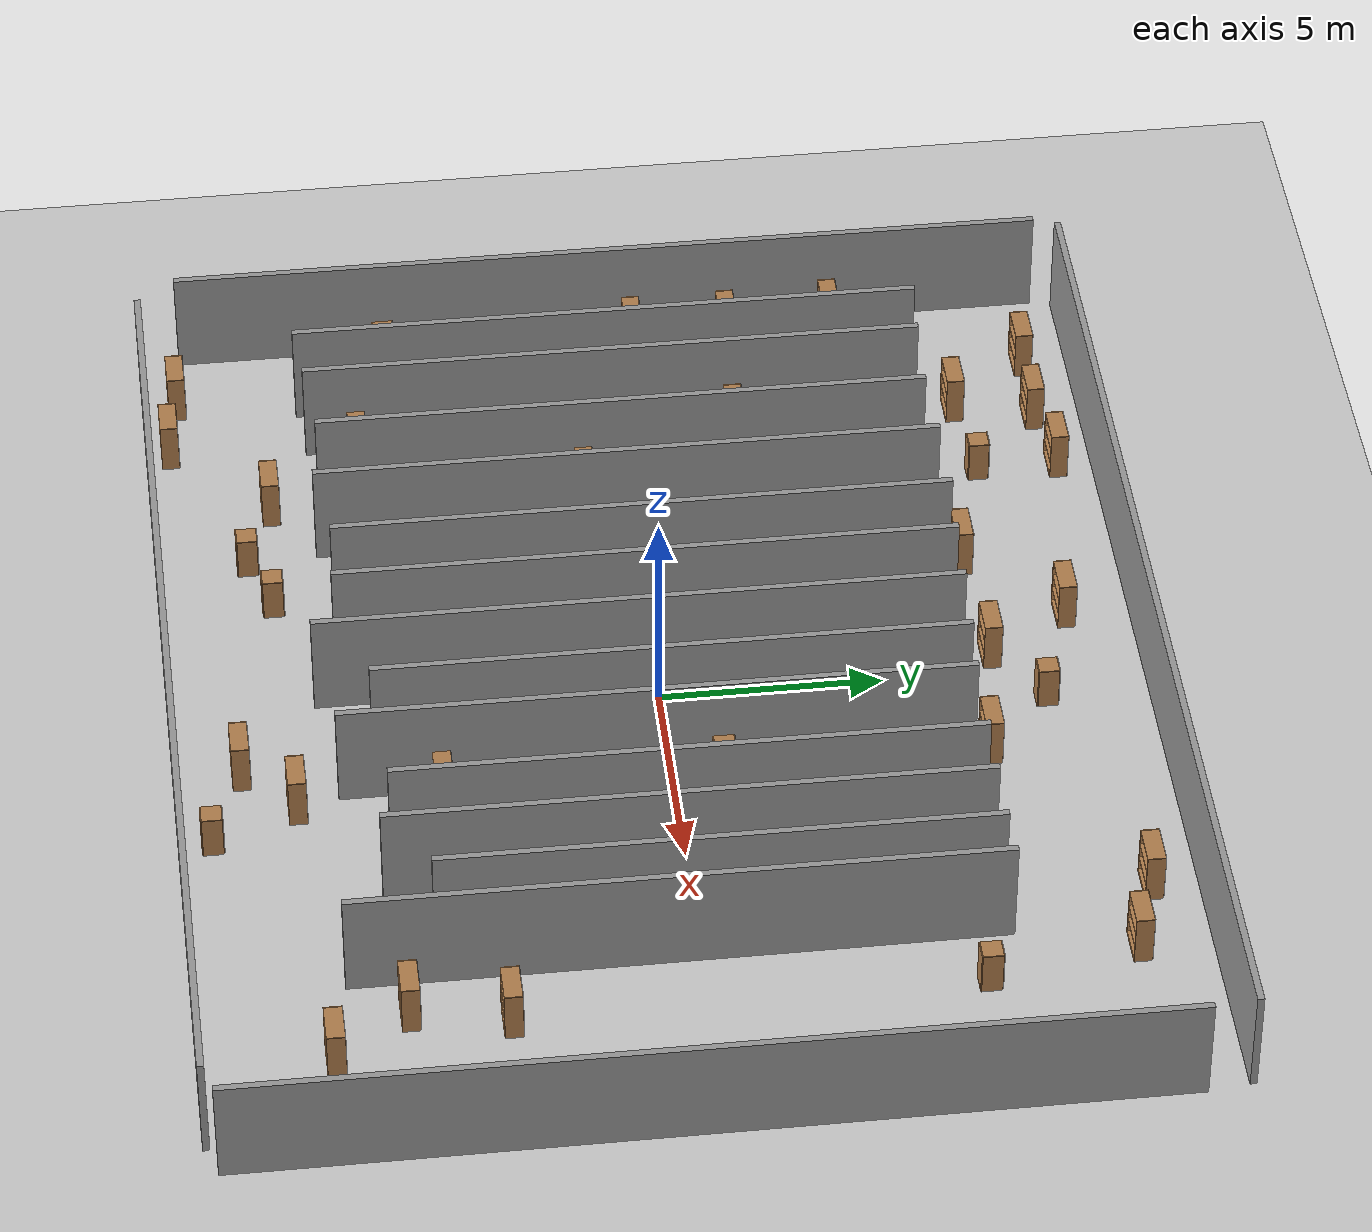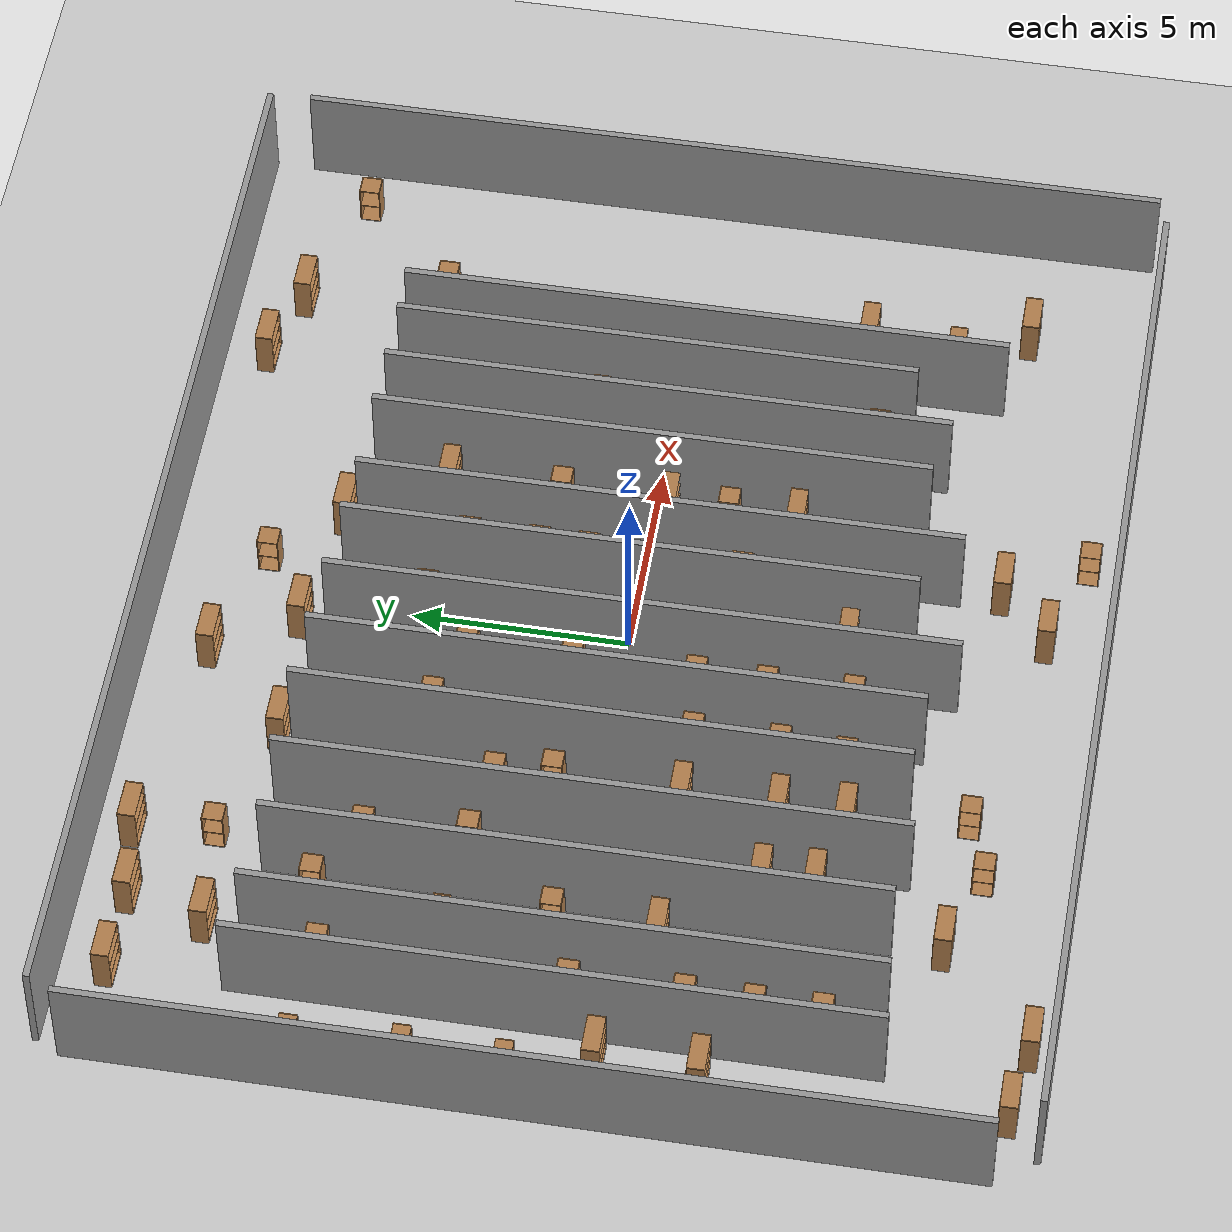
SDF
<sdf version="1.6">
 <world name="default">
  <light name="sun" type="directional">
   <cast_shadows>0</cast_shadows>
   <pose>0 0 10 0 -0 0</pose>
   <diffuse>0.8 0.8 0.8 1</diffuse>
   <specular>0.2 0.2 0.2 1</specular>
   <attenuation>
    <range>1000</range>
    <constant>0.9</constant>
    <linear>0.01</linear>
    <quadratic>0.001</quadratic>
   </attenuation>
   <direction>-0.5 0.1 -0.9</direction>
  </light>
  <model name="ground_plane">
   <static>1</static>
   <link name="link">
    <collision name="collision">
     <geometry><plane><normal>0 0 1</normal><size>100 100</size></plane></geometry>
     <surface><friction><ode><mu>100</mu><mu2>50</mu2></ode></friction></surface>
    </collision>
    <visual name="visual">
     <cast_shadows>0</cast_shadows>
     <geometry><plane><normal>0 0 1</normal><size>100 100</size></plane></geometry>
     <material>
      <script><uri>file://media/materials/scripts/gazebo.material</uri><name>Gazebo/Grey</name></script>
     </material>
    </visual>
   </link>
  </model>
  <gravity>0 0 -9.8</gravity>
  <magnetic_field>6e-06 2.3e-05 -4.2e-05</magnetic_field>
  <atmosphere type="adiabatic"/>
  <physics name="default_physics" default="0" type="ode">
   <max_step_size>0.001</max_step_size>
   <real_time_factor>1</real_time_factor>
   <real_time_update_rate>1000</real_time_update_rate>
  </physics>
  <scene><ambient>0.4 0.4 0.4 1</ambient><background>0.7 0.7 0.7 1</background><shadows>1</shadows></scene>
  <audio><device>default</device></audio>
  <spherical_coordinates>
   <surface_model>EARTH_WGS84</surface_model>
   <latitude_deg>0</latitude_deg>
   <longitude_deg>0</longitude_deg>
   <elevation>0</elevation>
   <heading_deg>0</heading_deg>
  </spherical_coordinates>
  <model name="room15">
   <pose>0.149288 0.057 0 0 -0 0</pose>
   <link name="Wall_0">
    <collision name="Wall_0_Collision">
     <geometry><box><size>25.75 0.15 2.5</size></box></geometry>
     <pose>0 0 1.25 0 -0 0</pose>
    </collision>
    <visual name="Wall_0_Visual">
     <pose>0 0 1.25 0 -0 0</pose>
     <geometry><box><size>25.75 0.15 2.5</size></box></geometry>
     <material>
      <script><uri>file://media/materials/scripts/gazebo.material</uri><name>Gazebo/Grey</name></script>
      <ambient>1 1 1 1</ambient>
     </material>
     <meta><layer>0</layer></meta>
    </visual>
    <pose>0.089731 10.8367 0 0 -0 0</pose>
   </link>
   <link name="Wall_10">
    <collision name="Wall_10_Collision">
     <geometry><box><size>14.25 0.15 2.5</size></box></geometry>
     <pose>0 0 1.25 0 -0 0</pose>
    </collision>
    <visual name="Wall_10_Visual">
     <pose>0 0 1.25 0 -0 0</pose>
     <geometry><box><size>14.25 0.15 2.5</size></box></geometry>
     <material>
      <script><uri>file://media/materials/scripts/gazebo.material</uri><name>Gazebo/Grey</name></script>
      <ambient>1 1 1 1</ambient>
     </material>
     <meta><layer>0</layer></meta>
    </visual>
    <pose>-9.40259 -0.099252 0 0 -0 -1.5708</pose>
   </link>
   <link name="Wall_12">
    <collision name="Wall_12_Collision">
     <geometry><box><size>14 0.15 2.5</size></box></geometry>
     <pose>0 0 1.25 0 -0 0</pose>
    </collision>
    <visual name="Wall_12_Visual">
     <pose>0 0 1.25 0 -0 0</pose>
     <geometry><box><size>14 0.15 2.5</size></box></geometry>
     <material>
      <script><uri>file://media/materials/scripts/gazebo.material</uri><name>Gazebo/Grey</name></script>
      <ambient>1 1 1 1</ambient>
     </material>
     <meta><layer>0</layer></meta>
    </visual>
    <pose>-7.55214 -0.066775 0 0 -0 -1.5708</pose>
   </link>
   <link name="Wall_14">
    <collision name="Wall_14_Collision">
     <geometry><box><size>14.25 0.15 2.5</size></box></geometry>
     <pose>0 0 1.25 0 -0 0</pose>
    </collision>
    <visual name="Wall_14_Visual">
     <pose>0 0 1.25 0 -0 0</pose>
     <geometry><box><size>14.25 0.15 2.5</size></box></geometry>
     <material>
      <script><uri>file://media/materials/scripts/gazebo.material</uri><name>Gazebo/Grey</name></script>
      <ambient>1 1 1 1</ambient>
     </material>
     <meta><layer>0</layer></meta>
    </visual>
    <pose>-5.79422 -0.122383 0 0 -0 -1.5708</pose>
   </link>
   <link name="Wall_16">
    <collision name="Wall_16_Collision">
     <geometry><box><size>14 0.15 2.5</size></box></geometry>
     <pose>0 0 1.25 0 -0 0</pose>
    </collision>
    <visual name="Wall_16_Visual">
     <pose>0 0 1.25 0 -0 0</pose>
     <geometry><box><size>14 0.15 2.5</size></box></geometry>
     <material>
      <script><uri>file://media/materials/scripts/gazebo.material</uri><name>Gazebo/Grey</name></script>
      <ambient>1 1 1 1</ambient>
     </material>
     <meta><layer>0</layer></meta>
    </visual>
    <pose>-3.89751 0.002617 0 0 -0 -1.5708</pose>
   </link>
   <link name="Wall_18">
    <collision name="Wall_18_Collision">
     <geometry><box><size>14 0.15 2.5</size></box></geometry>
     <pose>0 0 1.25 0 -0 0</pose>
    </collision>
    <visual name="Wall_18_Visual">
     <pose>0 0 1.25 0 -0 0</pose>
     <geometry><box><size>14 0.15 2.5</size></box></geometry>
     <material>
      <script><uri>file://media/materials/scripts/gazebo.material</uri><name>Gazebo/Grey</name></script>
      <ambient>1 1 1 1</ambient>
     </material>
     <meta><layer>0</layer></meta>
    </visual>
    <pose>-2.34776 -0.089905 0 0 -0 -1.5708</pose>
   </link>
   <link name="Wall_2">
    <collision name="Wall_2_Collision">
     <geometry><box><size>20.5 0.15 2.5</size></box></geometry>
     <pose>0 0 1.25 0 -0 0</pose>
    </collision>
    <visual name="Wall_2_Visual">
     <pose>0 0 1.25 0 -0 0</pose>
     <geometry><box><size>20.5 0.15 2.5</size></box></geometry>
     <material>
      <script><uri>file://media/materials/scripts/gazebo.material</uri><name>Gazebo/Grey</name></script>
      <ambient>1 1 1 1</ambient>
     </material>
     <meta><layer>0</layer></meta>
    </visual>
    <pose>13.011 -0.379188 0 0 -0 -1.5708</pose>
   </link>
   <link name="Wall_20">
    <collision name="Wall_20_Collision">
     <geometry><box><size>14.5 0.15 2.5</size></box></geometry>
     <pose>0 0 1.25 0 -0 0</pose>
    </collision>
    <visual name="Wall_20_Visual">
     <pose>0 0 1.25 0 -0 0</pose>
     <geometry><box><size>14.5 0.15 2.5</size></box></geometry>
     <material>
      <script><uri>file://media/materials/scripts/gazebo.material</uri><name>Gazebo/Grey</name></script>
      <ambient>1 1 1 1</ambient>
     </material>
     <meta><layer>0</layer></meta>
    </visual>
    <pose>-0.774876 -0.409297 0 0 -0 -1.5708</pose>
   </link>
   <link name="Wall_22">
    <collision name="Wall_22_Collision">
     <geometry><box><size>13.25 0.15 2.5</size></box></geometry>
     <pose>0 0 1.25 0 -0 0</pose>
    </collision>
    <visual name="Wall_22_Visual">
     <pose>0 0 1.25 0 -0 0</pose>
     <geometry><box><size>13.25 0.15 2.5</size></box></geometry>
     <material>
      <script><uri>file://media/materials/scripts/gazebo.material</uri><name>Gazebo/Grey</name></script>
      <ambient>1 1 1 1</ambient>
     </material>
     <meta><layer>0</layer></meta>
    </visual>
    <pose>0.867398 0.12318 0 0 -0 -1.5708</pose>
   </link>
   <link name="Wall_24">
    <collision name="Wall_24_Collision">
     <geometry><box><size>14 0.15 2.5</size></box></geometry>
     <pose>0 0 1.25 0 -0 0</pose>
    </collision>
    <visual name="Wall_24_Visual">
     <pose>0 0 1.25 0 -0 0</pose>
     <geometry><box><size>14 0.15 2.5</size></box></geometry>
     <material>
      <script><uri>file://media/materials/scripts/gazebo.material</uri><name>Gazebo/Grey</name></script>
      <ambient>1 1 1 1</ambient>
     </material>
     <meta><layer>0</layer></meta>
    </visual>
    <pose>2.20897 -0.344342 0 0 -0 -1.5708</pose>
   </link>
   <link name="Wall_26">
    <collision name="Wall_26_Collision">
     <geometry><box><size>13 0.15 2.5</size></box></geometry>
     <pose>0 0 1.25 0 -0 0</pose>
    </collision>
    <visual name="Wall_26_Visual">
     <pose>0 0 1.25 0 -0 0</pose>
     <geometry><box><size>13 0.15 2.5</size></box></geometry>
     <material>
      <script><uri>file://media/materials/scripts/gazebo.material</uri><name>Gazebo/Grey</name></script>
      <ambient>1 1 1 1</ambient>
     </material>
     <meta><layer>0</layer></meta>
    </visual>
    <pose>4.10568 0.132527 0 0 -0 -1.5708</pose>
   </link>
   <link name="Wall_28">
    <collision name="Wall_28_Collision">
     <geometry><box><size>13.25 0.15 2.5</size></box></geometry>
     <pose>0 0 1.25 0 -0 0</pose>
    </collision>
    <visual name="Wall_28_Visual">
     <pose>0 0 1.25 0 -0 0</pose>
     <geometry><box><size>13.25 0.15 2.5</size></box></geometry>
     <material>
      <script><uri>file://media/materials/scripts/gazebo.material</uri><name>Gazebo/Grey</name></script>
      <ambient>1 1 1 1</ambient>
     </material>
     <meta><layer>0</layer></meta>
    </visual>
    <pose>5.47039 -0.015603 0 0 -0 -1.5708</pose>
   </link>
   <link name="Wall_30">
    <collision name="Wall_30_Collision">
     <geometry><box><size>12.25 0.15 2.5</size></box></geometry>
     <pose>0 0 1.25 0 -0 0</pose>
    </collision>
    <visual name="Wall_30_Visual">
     <pose>0 0 1.25 0 -0 0</pose>
     <geometry><box><size>12.25 0.15 2.5</size></box></geometry>
     <material>
      <script><uri>file://media/materials/scripts/gazebo.material</uri><name>Gazebo/Grey</name></script>
      <ambient>1 1 1 1</ambient>
     </material>
     <meta><layer>0</layer></meta>
    </visual>
    <pose>6.90449 0.461266 0 0 -0 -1.5708</pose>
   </link>
   <link name="Wall_32">
    <collision name="Wall_32_Collision">
     <geometry><box><size>14.25 0.15 2.5</size></box></geometry>
     <pose>0 0 1.25 0 -0 0</pose>
    </collision>
    <visual name="Wall_32_Visual">
     <pose>0 0 1.25 0 -0 0</pose>
     <geometry><box><size>14.25 0.15 2.5</size></box></geometry>
     <material>
      <script><uri>file://media/materials/scripts/gazebo.material</uri><name>Gazebo/Grey</name></script>
      <ambient>1 1 1 1</ambient>
     </material>
     <meta><layer>0</layer></meta>
    </visual>
    <pose>7.99162 -0.515603 0 0 -0 -1.5708</pose>
   </link>
   <link name="Wall_4">
    <collision name="Wall_4_Collision">
     <geometry><box><size>24.75 0.15 2.5</size></box></geometry>
     <pose>0 0 1.25 0 -0 0</pose>
    </collision>
    <visual name="Wall_4_Visual">
     <pose>0 0 1.25 0 -0 0</pose>
     <geometry><box><size>24.75 0.15 2.5</size></box></geometry>
     <material>
      <script><uri>file://media/materials/scripts/gazebo.material</uri><name>Gazebo/Grey</name></script>
      <ambient>1 1 1 1</ambient>
     </material>
     <meta><layer>0</layer></meta>
    </visual>
    <pose>-0.006082 -10.8367 0 0 -0 3.14159</pose>
   </link>
   <link name="Wall_6">
    <collision name="Wall_6_Collision">
     <geometry><box><size>20.25 0.15 2.5</size></box></geometry>
     <pose>0 0 1.25 0 -0 0</pose>
    </collision>
    <visual name="Wall_6_Visual">
     <pose>0 0 1.25 0 -0 0</pose>
     <geometry><box><size>20.25 0.15 2.5</size></box></geometry>
     <material>
      <script><uri>file://media/materials/scripts/gazebo.material</uri><name>Gazebo/Grey</name></script>
      <ambient>1 1 1 1</ambient>
     </material>
     <meta><layer>0</layer></meta>
    </visual>
    <pose>-13.011 0.162163 0 0 -0 -1.5708</pose>
   </link>
   <link name="Wall_8">
    <collision name="Wall_8_Collision">
     <geometry><box><size>14.5 0.15 2.5</size></box></geometry>
     <pose>0 0 1.25 0 -0 0</pose>
    </collision>
    <visual name="Wall_8_Visual">
     <pose>0 0 1.25 0 -0 0</pose>
     <geometry><box><size>14.5 0.15 2.5</size></box></geometry>
     <material>
      <script><uri>file://media/materials/scripts/gazebo.material</uri><name>Gazebo/Grey</name></script>
      <ambient>1 1 1 1</ambient>
     </material>
     <meta><layer>0</layer></meta>
    </visual>
    <pose>-10.7904 -0.108599 0 0 -0 -1.5708</pose>
   </link>
   <static>1</static>
  </model>
  <model name="bookshelf">
   <static>1</static>
   <link name="link">
    <inertial><mass>1</mass></inertial>
    <collision name="back">
     <pose>0 0.005 0.6 0 -0 0</pose>
     <geometry><box><size>0.9 0.01 1.2</size></box></geometry>
    </collision>
    <visual name="visual1">
     <pose>0 0.005 0.6 0 -0 0</pose>
     <geometry><box><size>0.9 0.01 1.2</size></box></geometry>
     <material>
      <script><uri>file://media/materials/scripts/gazebo.material</uri><name>Gazebo/Wood</name></script>
     </material>
    </visual>
    <collision name="left_side">
     <pose>0.45 -0.195 0.6 0 -0 0</pose>
     <geometry><box><size>0.02 0.4 1.2</size></box></geometry>
    </collision>
    <visual name="visual2">
     <pose>0.45 -0.195 0.6 0 -0 0</pose>
     <geometry><box><size>0.02 0.4 1.2</size></box></geometry>
     <material>
      <script><uri>file://media/materials/scripts/gazebo.material</uri><name>Gazebo/Wood</name></script>
     </material>
    </visual>
    <collision name="right_side">
     <pose>-0.45 -0.195 0.6 0 -0 0</pose>
     <geometry><box><size>0.02 0.4 1.2</size></box></geometry>
    </collision>
    <visual name="visual3">
     <pose>-0.45 -0.195 0.6 0 -0 0</pose>
     <geometry><box><size>0.02 0.4 1.2</size></box></geometry>
     <material>
      <script><uri>file://media/materials/scripts/gazebo.material</uri><name>Gazebo/Wood</name></script>
     </material>
    </visual>
    <collision name="bottom">
     <pose>0 -0.195 0.03 0 -0 0</pose>
     <geometry><box><size>0.88 0.4 0.06</size></box></geometry>
    </collision>
    <visual name="visual4">
     <pose>0 -0.195 0.03 0 -0 0</pose>
     <geometry><box><size>0.88 0.4 0.06</size></box></geometry>
     <material>
      <script><uri>file://media/materials/scripts/gazebo.material</uri><name>Gazebo/Wood</name></script>
     </material>
    </visual>
    <collision name="top">
     <pose>0 -0.195 1.19 0 -0 0</pose>
     <geometry><box><size>0.88 0.4 0.02</size></box></geometry>
    </collision>
    <visual name="visual5">
     <pose>0 -0.195 1.19 0 -0 0</pose>
     <geometry><box><size>0.88 0.4 0.02</size></box></geometry>
     <material>
      <script><uri>file://media/materials/scripts/gazebo.material</uri><name>Gazebo/Wood</name></script>
     </material>
    </visual>
    <collision name="low_shelf">
     <pose>0 -0.195 0.43 0 -0 0</pose>
     <geometry><box><size>0.88 0.4 0.02</size></box></geometry>
    </collision>
    <visual name="visual6">
     <pose>0 -0.195 0.43 0 -0 0</pose>
     <geometry><box><size>0.88 0.4 0.02</size></box></geometry>
     <material>
      <script><uri>file://media/materials/scripts/gazebo.material</uri><name>Gazebo/Wood</name></script>
     </material>
    </visual>
    <collision name="high_shelf">
     <pose>0 -0.195 0.8 0 -0 0</pose>
     <geometry><box><size>0.88 0.4 0.02</size></box></geometry>
    </collision>
    <visual name="visual7">
     <pose>0 -0.195 0.8 0 -0 0</pose>
     <geometry><box><size>0.88 0.4 0.02</size></box></geometry>
     <material>
      <script><uri>file://media/materials/scripts/gazebo.material</uri><name>Gazebo/Wood</name></script>
     </material>
    </visual>
   </link>
   <pose>-10.5831 9.95635 0 0 -0 0</pose>
  </model>
  <model name="bookshelf_0">
   <static>1</static>
   <link name="link">
    <inertial><mass>1</mass></inertial>
    <collision name="back">
     <pose>0 0.005 0.6 0 -0 0</pose>
     <geometry><box><size>0.9 0.01 1.2</size></box></geometry>
    </collision>
    <visual name="visual1">
     <pose>0 0.005 0.6 0 -0 0</pose>
     <geometry><box><size>0.9 0.01 1.2</size></box></geometry>
     <material>
      <script><uri>file://media/materials/scripts/gazebo.material</uri><name>Gazebo/Wood</name></script>
     </material>
    </visual>
    <collision name="left_side">
     <pose>0.45 -0.195 0.6 0 -0 0</pose>
     <geometry><box><size>0.02 0.4 1.2</size></box></geometry>
    </collision>
    <visual name="visual2">
     <pose>0.45 -0.195 0.6 0 -0 0</pose>
     <geometry><box><size>0.02 0.4 1.2</size></box></geometry>
     <material>
      <script><uri>file://media/materials/scripts/gazebo.material</uri><name>Gazebo/Wood</name></script>
     </material>
    </visual>
    <collision name="right_side">
     <pose>-0.45 -0.195 0.6 0 -0 0</pose>
     <geometry><box><size>0.02 0.4 1.2</size></box></geometry>
    </collision>
    <visual name="visual3">
     <pose>-0.45 -0.195 0.6 0 -0 0</pose>
     <geometry><box><size>0.02 0.4 1.2</size></box></geometry>
     <material>
      <script><uri>file://media/materials/scripts/gazebo.material</uri><name>Gazebo/Wood</name></script>
     </material>
    </visual>
    <collision name="bottom">
     <pose>0 -0.195 0.03 0 -0 0</pose>
     <geometry><box><size>0.88 0.4 0.06</size></box></geometry>
    </collision>
    <visual name="visual4">
     <pose>0 -0.195 0.03 0 -0 0</pose>
     <geometry><box><size>0.88 0.4 0.06</size></box></geometry>
     <material>
      <script><uri>file://media/materials/scripts/gazebo.material</uri><name>Gazebo/Wood</name></script>
     </material>
    </visual>
    <collision name="top">
     <pose>0 -0.195 1.19 0 -0 0</pose>
     <geometry><box><size>0.88 0.4 0.02</size></box></geometry>
    </collision>
    <visual name="visual5">
     <pose>0 -0.195 1.19 0 -0 0</pose>
     <geometry><box><size>0.88 0.4 0.02</size></box></geometry>
     <material>
      <script><uri>file://media/materials/scripts/gazebo.material</uri><name>Gazebo/Wood</name></script>
     </material>
    </visual>
    <collision name="low_shelf">
     <pose>0 -0.195 0.43 0 -0 0</pose>
     <geometry><box><size>0.88 0.4 0.02</size></box></geometry>
    </collision>
    <visual name="visual6">
     <pose>0 -0.195 0.43 0 -0 0</pose>
     <geometry><box><size>0.88 0.4 0.02</size></box></geometry>
     <material>
      <script><uri>file://media/materials/scripts/gazebo.material</uri><name>Gazebo/Wood</name></script>
     </material>
    </visual>
    <collision name="high_shelf">
     <pose>0 -0.195 0.8 0 -0 0</pose>
     <geometry><box><size>0.88 0.4 0.02</size></box></geometry>
    </collision>
    <visual name="visual7">
     <pose>0 -0.195 0.8 0 -0 0</pose>
     <geometry><box><size>0.88 0.4 0.02</size></box></geometry>
     <material>
      <script><uri>file://media/materials/scripts/gazebo.material</uri><name>Gazebo/Wood</name></script>
     </material>
    </visual>
   </link>
   <pose>-8.62976 9.91802 0 0 -0 0</pose>
  </model>
  <model name="bookshelf_1">
   <static>1</static>
   <link name="link">
    <inertial><mass>1</mass></inertial>
    <collision name="back">
     <pose>0 0.005 0.6 0 -0 0</pose>
     <geometry><box><size>0.9 0.01 1.2</size></box></geometry>
    </collision>
    <visual name="visual1">
     <pose>0 0.005 0.6 0 -0 0</pose>
     <geometry><box><size>0.9 0.01 1.2</size></box></geometry>
     <material>
      <script><uri>file://media/materials/scripts/gazebo.material</uri><name>Gazebo/Wood</name></script>
     </material>
    </visual>
    <collision name="left_side">
     <pose>0.45 -0.195 0.6 0 -0 0</pose>
     <geometry><box><size>0.02 0.4 1.2</size></box></geometry>
    </collision>
    <visual name="visual2">
     <pose>0.45 -0.195 0.6 0 -0 0</pose>
     <geometry><box><size>0.02 0.4 1.2</size></box></geometry>
     <material>
      <script><uri>file://media/materials/scripts/gazebo.material</uri><name>Gazebo/Wood</name></script>
     </material>
    </visual>
    <collision name="right_side">
     <pose>-0.45 -0.195 0.6 0 -0 0</pose>
     <geometry><box><size>0.02 0.4 1.2</size></box></geometry>
    </collision>
    <visual name="visual3">
     <pose>-0.45 -0.195 0.6 0 -0 0</pose>
     <geometry><box><size>0.02 0.4 1.2</size></box></geometry>
     <material>
      <script><uri>file://media/materials/scripts/gazebo.material</uri><name>Gazebo/Wood</name></script>
     </material>
    </visual>
    <collision name="bottom">
     <pose>0 -0.195 0.03 0 -0 0</pose>
     <geometry><box><size>0.88 0.4 0.06</size></box></geometry>
    </collision>
    <visual name="visual4">
     <pose>0 -0.195 0.03 0 -0 0</pose>
     <geometry><box><size>0.88 0.4 0.06</size></box></geometry>
     <material>
      <script><uri>file://media/materials/scripts/gazebo.material</uri><name>Gazebo/Wood</name></script>
     </material>
    </visual>
    <collision name="top">
     <pose>0 -0.195 1.19 0 -0 0</pose>
     <geometry><box><size>0.88 0.4 0.02</size></box></geometry>
    </collision>
    <visual name="visual5">
     <pose>0 -0.195 1.19 0 -0 0</pose>
     <geometry><box><size>0.88 0.4 0.02</size></box></geometry>
     <material>
      <script><uri>file://media/materials/scripts/gazebo.material</uri><name>Gazebo/Wood</name></script>
     </material>
    </visual>
    <collision name="low_shelf">
     <pose>0 -0.195 0.43 0 -0 0</pose>
     <geometry><box><size>0.88 0.4 0.02</size></box></geometry>
    </collision>
    <visual name="visual6">
     <pose>0 -0.195 0.43 0 -0 0</pose>
     <geometry><box><size>0.88 0.4 0.02</size></box></geometry>
     <material>
      <script><uri>file://media/materials/scripts/gazebo.material</uri><name>Gazebo/Wood</name></script>
     </material>
    </visual>
    <collision name="high_shelf">
     <pose>0 -0.195 0.8 0 -0 0</pose>
     <geometry><box><size>0.88 0.4 0.02</size></box></geometry>
    </collision>
    <visual name="visual7">
     <pose>0 -0.195 0.8 0 -0 0</pose>
     <geometry><box><size>0.88 0.4 0.02</size></box></geometry>
     <material>
      <script><uri>file://media/materials/scripts/gazebo.material</uri><name>Gazebo/Wood</name></script>
     </material>
    </visual>
   </link>
   <pose>-11.2275 -9.84788 0 0 -0 0</pose>
  </model>
  <model name="bookshelf_2">
   <static>1</static>
   <link name="link">
    <inertial><mass>1</mass></inertial>
    <collision name="back">
     <pose>0 0.005 0.6 0 -0 0</pose>
     <geometry><box><size>0.9 0.01 1.2</size></box></geometry>
    </collision>
    <visual name="visual1">
     <pose>0 0.005 0.6 0 -0 0</pose>
     <geometry><box><size>0.9 0.01 1.2</size></box></geometry>
     <material>
      <script><uri>file://media/materials/scripts/gazebo.material</uri><name>Gazebo/Wood</name></script>
     </material>
    </visual>
    <collision name="left_side">
     <pose>0.45 -0.195 0.6 0 -0 0</pose>
     <geometry><box><size>0.02 0.4 1.2</size></box></geometry>
    </collision>
    <visual name="visual2">
     <pose>0.45 -0.195 0.6 0 -0 0</pose>
     <geometry><box><size>0.02 0.4 1.2</size></box></geometry>
     <material>
      <script><uri>file://media/materials/scripts/gazebo.material</uri><name>Gazebo/Wood</name></script>
     </material>
    </visual>
    <collision name="right_side">
     <pose>-0.45 -0.195 0.6 0 -0 0</pose>
     <geometry><box><size>0.02 0.4 1.2</size></box></geometry>
    </collision>
    <visual name="visual3">
     <pose>-0.45 -0.195 0.6 0 -0 0</pose>
     <geometry><box><size>0.02 0.4 1.2</size></box></geometry>
     <material>
      <script><uri>file://media/materials/scripts/gazebo.material</uri><name>Gazebo/Wood</name></script>
     </material>
    </visual>
    <collision name="bottom">
     <pose>0 -0.195 0.03 0 -0 0</pose>
     <geometry><box><size>0.88 0.4 0.06</size></box></geometry>
    </collision>
    <visual name="visual4">
     <pose>0 -0.195 0.03 0 -0 0</pose>
     <geometry><box><size>0.88 0.4 0.06</size></box></geometry>
     <material>
      <script><uri>file://media/materials/scripts/gazebo.material</uri><name>Gazebo/Wood</name></script>
     </material>
    </visual>
    <collision name="top">
     <pose>0 -0.195 1.19 0 -0 0</pose>
     <geometry><box><size>0.88 0.4 0.02</size></box></geometry>
    </collision>
    <visual name="visual5">
     <pose>0 -0.195 1.19 0 -0 0</pose>
     <geometry><box><size>0.88 0.4 0.02</size></box></geometry>
     <material>
      <script><uri>file://media/materials/scripts/gazebo.material</uri><name>Gazebo/Wood</name></script>
     </material>
    </visual>
    <collision name="low_shelf">
     <pose>0 -0.195 0.43 0 -0 0</pose>
     <geometry><box><size>0.88 0.4 0.02</size></box></geometry>
    </collision>
    <visual name="visual6">
     <pose>0 -0.195 0.43 0 -0 0</pose>
     <geometry><box><size>0.88 0.4 0.02</size></box></geometry>
     <material>
      <script><uri>file://media/materials/scripts/gazebo.material</uri><name>Gazebo/Wood</name></script>
     </material>
    </visual>
    <collision name="high_shelf">
     <pose>0 -0.195 0.8 0 -0 0</pose>
     <geometry><box><size>0.88 0.4 0.02</size></box></geometry>
    </collision>
    <visual name="visual7">
     <pose>0 -0.195 0.8 0 -0 0</pose>
     <geometry><box><size>0.88 0.4 0.02</size></box></geometry>
     <material>
      <script><uri>file://media/materials/scripts/gazebo.material</uri><name>Gazebo/Wood</name></script>
     </material>
    </visual>
   </link>
   <pose>-6.87508 10.1974 0 0 -0 0</pose>
  </model>
  <model name="bookshelf_3">
   <static>1</static>
   <link name="link">
    <inertial><mass>1</mass></inertial>
    <collision name="back">
     <pose>0 0.005 0.6 0 -0 0</pose>
     <geometry><box><size>0.9 0.01 1.2</size></box></geometry>
    </collision>
    <visual name="visual1">
     <pose>0 0.005 0.6 0 -0 0</pose>
     <geometry><box><size>0.9 0.01 1.2</size></box></geometry>
     <material>
      <script><uri>file://media/materials/scripts/gazebo.material</uri><name>Gazebo/Wood</name></script>
     </material>
    </visual>
    <collision name="left_side">
     <pose>0.45 -0.195 0.6 0 -0 0</pose>
     <geometry><box><size>0.02 0.4 1.2</size></box></geometry>
    </collision>
    <visual name="visual2">
     <pose>0.45 -0.195 0.6 0 -0 0</pose>
     <geometry><box><size>0.02 0.4 1.2</size></box></geometry>
     <material>
      <script><uri>file://media/materials/scripts/gazebo.material</uri><name>Gazebo/Wood</name></script>
     </material>
    </visual>
    <collision name="right_side">
     <pose>-0.45 -0.195 0.6 0 -0 0</pose>
     <geometry><box><size>0.02 0.4 1.2</size></box></geometry>
    </collision>
    <visual name="visual3">
     <pose>-0.45 -0.195 0.6 0 -0 0</pose>
     <geometry><box><size>0.02 0.4 1.2</size></box></geometry>
     <material>
      <script><uri>file://media/materials/scripts/gazebo.material</uri><name>Gazebo/Wood</name></script>
     </material>
    </visual>
    <collision name="bottom">
     <pose>0 -0.195 0.03 0 -0 0</pose>
     <geometry><box><size>0.88 0.4 0.06</size></box></geometry>
    </collision>
    <visual name="visual4">
     <pose>0 -0.195 0.03 0 -0 0</pose>
     <geometry><box><size>0.88 0.4 0.06</size></box></geometry>
     <material>
      <script><uri>file://media/materials/scripts/gazebo.material</uri><name>Gazebo/Wood</name></script>
     </material>
    </visual>
    <collision name="top">
     <pose>0 -0.195 1.19 0 -0 0</pose>
     <geometry><box><size>0.88 0.4 0.02</size></box></geometry>
    </collision>
    <visual name="visual5">
     <pose>0 -0.195 1.19 0 -0 0</pose>
     <geometry><box><size>0.88 0.4 0.02</size></box></geometry>
     <material>
      <script><uri>file://media/materials/scripts/gazebo.material</uri><name>Gazebo/Wood</name></script>
     </material>
    </visual>
    <collision name="low_shelf">
     <pose>0 -0.195 0.43 0 -0 0</pose>
     <geometry><box><size>0.88 0.4 0.02</size></box></geometry>
    </collision>
    <visual name="visual6">
     <pose>0 -0.195 0.43 0 -0 0</pose>
     <geometry><box><size>0.88 0.4 0.02</size></box></geometry>
     <material>
      <script><uri>file://media/materials/scripts/gazebo.material</uri><name>Gazebo/Wood</name></script>
     </material>
    </visual>
    <collision name="high_shelf">
     <pose>0 -0.195 0.8 0 -0 0</pose>
     <geometry><box><size>0.88 0.4 0.02</size></box></geometry>
    </collision>
    <visual name="visual7">
     <pose>0 -0.195 0.8 0 -0 0</pose>
     <geometry><box><size>0.88 0.4 0.02</size></box></geometry>
     <material>
      <script><uri>file://media/materials/scripts/gazebo.material</uri><name>Gazebo/Wood</name></script>
     </material>
    </visual>
   </link>
   <pose>-9.50662 -10.1006 0 0 -0 0</pose>
  </model>
  <model name="bookshelf_4">
   <static>1</static>
   <link name="link">
    <inertial><mass>1</mass></inertial>
    <collision name="back">
     <pose>0 0.005 0.6 0 -0 0</pose>
     <geometry><box><size>0.9 0.01 1.2</size></box></geometry>
    </collision>
    <visual name="visual1">
     <pose>0 0.005 0.6 0 -0 0</pose>
     <geometry><box><size>0.9 0.01 1.2</size></box></geometry>
     <material>
      <script><uri>file://media/materials/scripts/gazebo.material</uri><name>Gazebo/Wood</name></script>
     </material>
    </visual>
    <collision name="left_side">
     <pose>0.45 -0.195 0.6 0 -0 0</pose>
     <geometry><box><size>0.02 0.4 1.2</size></box></geometry>
    </collision>
    <visual name="visual2">
     <pose>0.45 -0.195 0.6 0 -0 0</pose>
     <geometry><box><size>0.02 0.4 1.2</size></box></geometry>
     <material>
      <script><uri>file://media/materials/scripts/gazebo.material</uri><name>Gazebo/Wood</name></script>
     </material>
    </visual>
    <collision name="right_side">
     <pose>-0.45 -0.195 0.6 0 -0 0</pose>
     <geometry><box><size>0.02 0.4 1.2</size></box></geometry>
    </collision>
    <visual name="visual3">
     <pose>-0.45 -0.195 0.6 0 -0 0</pose>
     <geometry><box><size>0.02 0.4 1.2</size></box></geometry>
     <material>
      <script><uri>file://media/materials/scripts/gazebo.material</uri><name>Gazebo/Wood</name></script>
     </material>
    </visual>
    <collision name="bottom">
     <pose>0 -0.195 0.03 0 -0 0</pose>
     <geometry><box><size>0.88 0.4 0.06</size></box></geometry>
    </collision>
    <visual name="visual4">
     <pose>0 -0.195 0.03 0 -0 0</pose>
     <geometry><box><size>0.88 0.4 0.06</size></box></geometry>
     <material>
      <script><uri>file://media/materials/scripts/gazebo.material</uri><name>Gazebo/Wood</name></script>
     </material>
    </visual>
    <collision name="top">
     <pose>0 -0.195 1.19 0 -0 0</pose>
     <geometry><box><size>0.88 0.4 0.02</size></box></geometry>
    </collision>
    <visual name="visual5">
     <pose>0 -0.195 1.19 0 -0 0</pose>
     <geometry><box><size>0.88 0.4 0.02</size></box></geometry>
     <material>
      <script><uri>file://media/materials/scripts/gazebo.material</uri><name>Gazebo/Wood</name></script>
     </material>
    </visual>
    <collision name="low_shelf">
     <pose>0 -0.195 0.43 0 -0 0</pose>
     <geometry><box><size>0.88 0.4 0.02</size></box></geometry>
    </collision>
    <visual name="visual6">
     <pose>0 -0.195 0.43 0 -0 0</pose>
     <geometry><box><size>0.88 0.4 0.02</size></box></geometry>
     <material>
      <script><uri>file://media/materials/scripts/gazebo.material</uri><name>Gazebo/Wood</name></script>
     </material>
    </visual>
    <collision name="high_shelf">
     <pose>0 -0.195 0.8 0 -0 0</pose>
     <geometry><box><size>0.88 0.4 0.02</size></box></geometry>
    </collision>
    <visual name="visual7">
     <pose>0 -0.195 0.8 0 -0 0</pose>
     <geometry><box><size>0.88 0.4 0.02</size></box></geometry>
     <material>
      <script><uri>file://media/materials/scripts/gazebo.material</uri><name>Gazebo/Wood</name></script>
     </material>
    </visual>
   </link>
   <pose>-1.73803 9.54025 0 0 -0 0</pose>
  </model>
  <model name="bookshelf_5">
   <static>1</static>
   <link name="link">
    <inertial><mass>1</mass></inertial>
    <collision name="back">
     <pose>0 0.005 0.6 0 -0 0</pose>
     <geometry><box><size>0.9 0.01 1.2</size></box></geometry>
    </collision>
    <visual name="visual1">
     <pose>0 0.005 0.6 0 -0 0</pose>
     <geometry><box><size>0.9 0.01 1.2</size></box></geometry>
     <material>
      <script><uri>file://media/materials/scripts/gazebo.material</uri><name>Gazebo/Wood</name></script>
     </material>
    </visual>
    <collision name="left_side">
     <pose>0.45 -0.195 0.6 0 -0 0</pose>
     <geometry><box><size>0.02 0.4 1.2</size></box></geometry>
    </collision>
    <visual name="visual2">
     <pose>0.45 -0.195 0.6 0 -0 0</pose>
     <geometry><box><size>0.02 0.4 1.2</size></box></geometry>
     <material>
      <script><uri>file://media/materials/scripts/gazebo.material</uri><name>Gazebo/Wood</name></script>
     </material>
    </visual>
    <collision name="right_side">
     <pose>-0.45 -0.195 0.6 0 -0 0</pose>
     <geometry><box><size>0.02 0.4 1.2</size></box></geometry>
    </collision>
    <visual name="visual3">
     <pose>-0.45 -0.195 0.6 0 -0 0</pose>
     <geometry><box><size>0.02 0.4 1.2</size></box></geometry>
     <material>
      <script><uri>file://media/materials/scripts/gazebo.material</uri><name>Gazebo/Wood</name></script>
     </material>
    </visual>
    <collision name="bottom">
     <pose>0 -0.195 0.03 0 -0 0</pose>
     <geometry><box><size>0.88 0.4 0.06</size></box></geometry>
    </collision>
    <visual name="visual4">
     <pose>0 -0.195 0.03 0 -0 0</pose>
     <geometry><box><size>0.88 0.4 0.06</size></box></geometry>
     <material>
      <script><uri>file://media/materials/scripts/gazebo.material</uri><name>Gazebo/Wood</name></script>
     </material>
    </visual>
    <collision name="top">
     <pose>0 -0.195 1.19 0 -0 0</pose>
     <geometry><box><size>0.88 0.4 0.02</size></box></geometry>
    </collision>
    <visual name="visual5">
     <pose>0 -0.195 1.19 0 -0 0</pose>
     <geometry><box><size>0.88 0.4 0.02</size></box></geometry>
     <material>
      <script><uri>file://media/materials/scripts/gazebo.material</uri><name>Gazebo/Wood</name></script>
     </material>
    </visual>
    <collision name="low_shelf">
     <pose>0 -0.195 0.43 0 -0 0</pose>
     <geometry><box><size>0.88 0.4 0.02</size></box></geometry>
    </collision>
    <visual name="visual6">
     <pose>0 -0.195 0.43 0 -0 0</pose>
     <geometry><box><size>0.88 0.4 0.02</size></box></geometry>
     <material>
      <script><uri>file://media/materials/scripts/gazebo.material</uri><name>Gazebo/Wood</name></script>
     </material>
    </visual>
    <collision name="high_shelf">
     <pose>0 -0.195 0.8 0 -0 0</pose>
     <geometry><box><size>0.88 0.4 0.02</size></box></geometry>
    </collision>
    <visual name="visual7">
     <pose>0 -0.195 0.8 0 -0 0</pose>
     <geometry><box><size>0.88 0.4 0.02</size></box></geometry>
     <material>
      <script><uri>file://media/materials/scripts/gazebo.material</uri><name>Gazebo/Wood</name></script>
     </material>
    </visual>
   </link>
   <pose>-0.58974 7.68107 0 0 -0 0</pose>
  </model>
  <model name="bookshelf_6">
   <static>1</static>
   <link name="link">
    <inertial><mass>1</mass></inertial>
    <collision name="back">
     <pose>0 0.005 0.6 0 -0 0</pose>
     <geometry><box><size>0.9 0.01 1.2</size></box></geometry>
    </collision>
    <visual name="visual1">
     <pose>0 0.005 0.6 0 -0 0</pose>
     <geometry><box><size>0.9 0.01 1.2</size></box></geometry>
     <material>
      <script><uri>file://media/materials/scripts/gazebo.material</uri><name>Gazebo/Wood</name></script>
     </material>
    </visual>
    <collision name="left_side">
     <pose>0.45 -0.195 0.6 0 -0 0</pose>
     <geometry><box><size>0.02 0.4 1.2</size></box></geometry>
    </collision>
    <visual name="visual2">
     <pose>0.45 -0.195 0.6 0 -0 0</pose>
     <geometry><box><size>0.02 0.4 1.2</size></box></geometry>
     <material>
      <script><uri>file://media/materials/scripts/gazebo.material</uri><name>Gazebo/Wood</name></script>
     </material>
    </visual>
    <collision name="right_side">
     <pose>-0.45 -0.195 0.6 0 -0 0</pose>
     <geometry><box><size>0.02 0.4 1.2</size></box></geometry>
    </collision>
    <visual name="visual3">
     <pose>-0.45 -0.195 0.6 0 -0 0</pose>
     <geometry><box><size>0.02 0.4 1.2</size></box></geometry>
     <material>
      <script><uri>file://media/materials/scripts/gazebo.material</uri><name>Gazebo/Wood</name></script>
     </material>
    </visual>
    <collision name="bottom">
     <pose>0 -0.195 0.03 0 -0 0</pose>
     <geometry><box><size>0.88 0.4 0.06</size></box></geometry>
    </collision>
    <visual name="visual4">
     <pose>0 -0.195 0.03 0 -0 0</pose>
     <geometry><box><size>0.88 0.4 0.06</size></box></geometry>
     <material>
      <script><uri>file://media/materials/scripts/gazebo.material</uri><name>Gazebo/Wood</name></script>
     </material>
    </visual>
    <collision name="top">
     <pose>0 -0.195 1.19 0 -0 0</pose>
     <geometry><box><size>0.88 0.4 0.02</size></box></geometry>
    </collision>
    <visual name="visual5">
     <pose>0 -0.195 1.19 0 -0 0</pose>
     <geometry><box><size>0.88 0.4 0.02</size></box></geometry>
     <material>
      <script><uri>file://media/materials/scripts/gazebo.material</uri><name>Gazebo/Wood</name></script>
     </material>
    </visual>
    <collision name="low_shelf">
     <pose>0 -0.195 0.43 0 -0 0</pose>
     <geometry><box><size>0.88 0.4 0.02</size></box></geometry>
    </collision>
    <visual name="visual6">
     <pose>0 -0.195 0.43 0 -0 0</pose>
     <geometry><box><size>0.88 0.4 0.02</size></box></geometry>
     <material>
      <script><uri>file://media/materials/scripts/gazebo.material</uri><name>Gazebo/Wood</name></script>
     </material>
    </visual>
    <collision name="high_shelf">
     <pose>0 -0.195 0.8 0 -0 0</pose>
     <geometry><box><size>0.88 0.4 0.02</size></box></geometry>
    </collision>
    <visual name="visual7">
     <pose>0 -0.195 0.8 0 -0 0</pose>
     <geometry><box><size>0.88 0.4 0.02</size></box></geometry>
     <material>
      <script><uri>file://media/materials/scripts/gazebo.material</uri><name>Gazebo/Wood</name></script>
     </material>
    </visual>
   </link>
   <pose>2.49876 7.225 0 0 -0 0</pose>
  </model>
  <model name="bookshelf_7">
   <static>1</static>
   <link name="link">
    <inertial><mass>1</mass></inertial>
    <collision name="back">
     <pose>0 0.005 0.6 0 -0 0</pose>
     <geometry><box><size>0.9 0.01 1.2</size></box></geometry>
    </collision>
    <visual name="visual1">
     <pose>0 0.005 0.6 0 -0 0</pose>
     <geometry><box><size>0.9 0.01 1.2</size></box></geometry>
     <material>
      <script><uri>file://media/materials/scripts/gazebo.material</uri><name>Gazebo/Wood</name></script>
     </material>
    </visual>
    <collision name="left_side">
     <pose>0.45 -0.195 0.6 0 -0 0</pose>
     <geometry><box><size>0.02 0.4 1.2</size></box></geometry>
    </collision>
    <visual name="visual2">
     <pose>0.45 -0.195 0.6 0 -0 0</pose>
     <geometry><box><size>0.02 0.4 1.2</size></box></geometry>
     <material>
      <script><uri>file://media/materials/scripts/gazebo.material</uri><name>Gazebo/Wood</name></script>
     </material>
    </visual>
    <collision name="right_side">
     <pose>-0.45 -0.195 0.6 0 -0 0</pose>
     <geometry><box><size>0.02 0.4 1.2</size></box></geometry>
    </collision>
    <visual name="visual3">
     <pose>-0.45 -0.195 0.6 0 -0 0</pose>
     <geometry><box><size>0.02 0.4 1.2</size></box></geometry>
     <material>
      <script><uri>file://media/materials/scripts/gazebo.material</uri><name>Gazebo/Wood</name></script>
     </material>
    </visual>
    <collision name="bottom">
     <pose>0 -0.195 0.03 0 -0 0</pose>
     <geometry><box><size>0.88 0.4 0.06</size></box></geometry>
    </collision>
    <visual name="visual4">
     <pose>0 -0.195 0.03 0 -0 0</pose>
     <geometry><box><size>0.88 0.4 0.06</size></box></geometry>
     <material>
      <script><uri>file://media/materials/scripts/gazebo.material</uri><name>Gazebo/Wood</name></script>
     </material>
    </visual>
    <collision name="top">
     <pose>0 -0.195 1.19 0 -0 0</pose>
     <geometry><box><size>0.88 0.4 0.02</size></box></geometry>
    </collision>
    <visual name="visual5">
     <pose>0 -0.195 1.19 0 -0 0</pose>
     <geometry><box><size>0.88 0.4 0.02</size></box></geometry>
     <material>
      <script><uri>file://media/materials/scripts/gazebo.material</uri><name>Gazebo/Wood</name></script>
     </material>
    </visual>
    <collision name="low_shelf">
     <pose>0 -0.195 0.43 0 -0 0</pose>
     <geometry><box><size>0.88 0.4 0.02</size></box></geometry>
    </collision>
    <visual name="visual6">
     <pose>0 -0.195 0.43 0 -0 0</pose>
     <geometry><box><size>0.88 0.4 0.02</size></box></geometry>
     <material>
      <script><uri>file://media/materials/scripts/gazebo.material</uri><name>Gazebo/Wood</name></script>
     </material>
    </visual>
    <collision name="high_shelf">
     <pose>0 -0.195 0.8 0 -0 0</pose>
     <geometry><box><size>0.88 0.4 0.02</size></box></geometry>
    </collision>
    <visual name="visual7">
     <pose>0 -0.195 0.8 0 -0 0</pose>
     <geometry><box><size>0.88 0.4 0.02</size></box></geometry>
     <material>
      <script><uri>file://media/materials/scripts/gazebo.material</uri><name>Gazebo/Wood</name></script>
     </material>
    </visual>
   </link>
   <pose>-3.76246 7.5113 0 0 -0 0</pose>
  </model>
  <model name="bookshelf_8">
   <static>1</static>
   <link name="link">
    <inertial><mass>1</mass></inertial>
    <collision name="back">
     <pose>0 0.005 0.6 0 -0 0</pose>
     <geometry><box><size>0.9 0.01 1.2</size></box></geometry>
    </collision>
    <visual name="visual1">
     <pose>0 0.005 0.6 0 -0 0</pose>
     <geometry><box><size>0.9 0.01 1.2</size></box></geometry>
     <material>
      <script><uri>file://media/materials/scripts/gazebo.material</uri><name>Gazebo/Wood</name></script>
     </material>
    </visual>
    <collision name="left_side">
     <pose>0.45 -0.195 0.6 0 -0 0</pose>
     <geometry><box><size>0.02 0.4 1.2</size></box></geometry>
    </collision>
    <visual name="visual2">
     <pose>0.45 -0.195 0.6 0 -0 0</pose>
     <geometry><box><size>0.02 0.4 1.2</size></box></geometry>
     <material>
      <script><uri>file://media/materials/scripts/gazebo.material</uri><name>Gazebo/Wood</name></script>
     </material>
    </visual>
    <collision name="right_side">
     <pose>-0.45 -0.195 0.6 0 -0 0</pose>
     <geometry><box><size>0.02 0.4 1.2</size></box></geometry>
    </collision>
    <visual name="visual3">
     <pose>-0.45 -0.195 0.6 0 -0 0</pose>
     <geometry><box><size>0.02 0.4 1.2</size></box></geometry>
     <material>
      <script><uri>file://media/materials/scripts/gazebo.material</uri><name>Gazebo/Wood</name></script>
     </material>
    </visual>
    <collision name="bottom">
     <pose>0 -0.195 0.03 0 -0 0</pose>
     <geometry><box><size>0.88 0.4 0.06</size></box></geometry>
    </collision>
    <visual name="visual4">
     <pose>0 -0.195 0.03 0 -0 0</pose>
     <geometry><box><size>0.88 0.4 0.06</size></box></geometry>
     <material>
      <script><uri>file://media/materials/scripts/gazebo.material</uri><name>Gazebo/Wood</name></script>
     </material>
    </visual>
    <collision name="top">
     <pose>0 -0.195 1.19 0 -0 0</pose>
     <geometry><box><size>0.88 0.4 0.02</size></box></geometry>
    </collision>
    <visual name="visual5">
     <pose>0 -0.195 1.19 0 -0 0</pose>
     <geometry><box><size>0.88 0.4 0.02</size></box></geometry>
     <material>
      <script><uri>file://media/materials/scripts/gazebo.material</uri><name>Gazebo/Wood</name></script>
     </material>
    </visual>
    <collision name="low_shelf">
     <pose>0 -0.195 0.43 0 -0 0</pose>
     <geometry><box><size>0.88 0.4 0.02</size></box></geometry>
    </collision>
    <visual name="visual6">
     <pose>0 -0.195 0.43 0 -0 0</pose>
     <geometry><box><size>0.88 0.4 0.02</size></box></geometry>
     <material>
      <script><uri>file://media/materials/scripts/gazebo.material</uri><name>Gazebo/Wood</name></script>
     </material>
    </visual>
    <collision name="high_shelf">
     <pose>0 -0.195 0.8 0 -0 0</pose>
     <geometry><box><size>0.88 0.4 0.02</size></box></geometry>
    </collision>
    <visual name="visual7">
     <pose>0 -0.195 0.8 0 -0 0</pose>
     <geometry><box><size>0.88 0.4 0.02</size></box></geometry>
     <material>
      <script><uri>file://media/materials/scripts/gazebo.material</uri><name>Gazebo/Wood</name></script>
     </material>
    </visual>
   </link>
   <pose>-9.11498 8.11541 0 0 -0 0</pose>
  </model>
  <model name="cabinet">
   <static>1</static>
   <link name="cabinet_bottom_plate">
    <inertial>
     <pose>0 0 -1 0 -0 0</pose>
     <inertia><ixx>2.05</ixx><ixy>0</ixy><ixz>0</ixz><iyy>2.05</iyy><iyz>0</iyz><izz>2.05</izz></inertia>
     <mass>25</mass>
    </inertial>
    <collision name="cabinet_bottom_plate_geom">
     <pose>0 0 0.01 0 -0 0</pose>
     <geometry><box><size>0.45 0.45 0.02</size></box></geometry>
    </collision>
    <visual name="cabinet_bottom_plate_geom_visual">
     <pose>0 0 0.01 0 -0 0</pose>
     <geometry><box><size>0.45 0.45 0.02</size></box></geometry>
     <material>
      <script><uri>file://media/materials/scripts/gazebo.material</uri><name>Gazebo/Wood</name></script>
     </material>
    </visual>
    <collision name="cabinet_bottom_plate_geom_cabinet_back_plate">
     <pose>0.235 0 0.51 0 -0 0</pose>
     <geometry><box><size>0.02 0.45 1.02</size></box></geometry>
    </collision>
    <visual name="cabinet_bottom_plate_geom_cabinet_back_plate_visual">
     <pose>0.235 0 0.51 0 -0 0</pose>
     <geometry><box><size>0.02 0.45 1.02</size></box></geometry>
     <material>
      <script><uri>file://media/materials/scripts/gazebo.material</uri><name>Gazebo/Wood</name></script>
     </material>
    </visual>
    <collision name="cabinet_bottom_plate_geom_cabinet_left_plate">
     <pose>0 0.235 0.51 0 -0 0</pose>
     <geometry><box><size>0.45 0.02 1.02</size></box></geometry>
    </collision>
    <visual name="cabinet_bottom_plate_geom_cabinet_left_plate_visual">
     <pose>0 0.235 0.51 0 -0 0</pose>
     <geometry><box><size>0.45 0.02 1.02</size></box></geometry>
     <material>
      <script><uri>file://media/materials/scripts/gazebo.material</uri><name>Gazebo/Wood</name></script>
     </material>
    </visual>
    <collision name="cabinet_bottom_plate_geom_cabinet_middle_plate">
     <pose>0 0 0.51 0 -0 0</pose>
     <geometry><box><size>0.45 0.45 0.02</size></box></geometry>
    </collision>
    <visual name="cabinet_bottom_plate_geom_cabinet_middle_plate_visual">
     <pose>0 0 0.51 0 -0 0</pose>
     <geometry><box><size>0.45 0.45 0.02</size></box></geometry>
     <material>
      <script><uri>file://media/materials/scripts/gazebo.material</uri><name>Gazebo/Wood</name></script>
     </material>
    </visual>
    <collision name="cabinet_bottom_plate_geom_cabinet_right_plate">
     <pose>0 -0.235 0.51 0 -0 0</pose>
     <geometry><box><size>0.45 0.02 1.02</size></box></geometry>
    </collision>
    <visual name="cabinet_bottom_plate_geom_cabinet_right_plate_visual">
     <pose>0 -0.235 0.51 0 -0 0</pose>
     <geometry><box><size>0.45 0.02 1.02</size></box></geometry>
     <material>
      <script><uri>file://media/materials/scripts/gazebo.material</uri><name>Gazebo/Wood</name></script>
     </material>
    </visual>
    <collision name="cabinet_bottom_plate_geom_cabinet_top_plate">
     <pose>0 0 1.01 0 -0 0</pose>
     <geometry><box><size>0.45 0.45 0.02</size></box></geometry>
    </collision>
    <visual name="cabinet_bottom_plate_geom_cabinet_top_plate_visual">
     <pose>0 0 1.01 0 -0 0</pose>
     <geometry><box><size>0.45 0.45 0.02</size></box></geometry>
     <material>
      <script><uri>file://media/materials/scripts/gazebo.material</uri><name>Gazebo/Wood</name></script>
     </material>
    </visual>
   </link>
   <pose>0.987671 8.5173 0 0 -0 0</pose>
  </model>
  <model name="bookshelf_9">
   <static>1</static>
   <link name="link">
    <inertial><mass>1</mass></inertial>
    <collision name="back">
     <pose>0 0.005 0.6 0 -0 0</pose>
     <geometry><box><size>0.9 0.01 1.2</size></box></geometry>
    </collision>
    <visual name="visual1">
     <pose>0 0.005 0.6 0 -0 0</pose>
     <geometry><box><size>0.9 0.01 1.2</size></box></geometry>
     <material>
      <script><uri>file://media/materials/scripts/gazebo.material</uri><name>Gazebo/Wood</name></script>
     </material>
    </visual>
    <collision name="left_side">
     <pose>0.45 -0.195 0.6 0 -0 0</pose>
     <geometry><box><size>0.02 0.4 1.2</size></box></geometry>
    </collision>
    <visual name="visual2">
     <pose>0.45 -0.195 0.6 0 -0 0</pose>
     <geometry><box><size>0.02 0.4 1.2</size></box></geometry>
     <material>
      <script><uri>file://media/materials/scripts/gazebo.material</uri><name>Gazebo/Wood</name></script>
     </material>
    </visual>
    <collision name="right_side">
     <pose>-0.45 -0.195 0.6 0 -0 0</pose>
     <geometry><box><size>0.02 0.4 1.2</size></box></geometry>
    </collision>
    <visual name="visual3">
     <pose>-0.45 -0.195 0.6 0 -0 0</pose>
     <geometry><box><size>0.02 0.4 1.2</size></box></geometry>
     <material>
      <script><uri>file://media/materials/scripts/gazebo.material</uri><name>Gazebo/Wood</name></script>
     </material>
    </visual>
    <collision name="bottom">
     <pose>0 -0.195 0.03 0 -0 0</pose>
     <geometry><box><size>0.88 0.4 0.06</size></box></geometry>
    </collision>
    <visual name="visual4">
     <pose>0 -0.195 0.03 0 -0 0</pose>
     <geometry><box><size>0.88 0.4 0.06</size></box></geometry>
     <material>
      <script><uri>file://media/materials/scripts/gazebo.material</uri><name>Gazebo/Wood</name></script>
     </material>
    </visual>
    <collision name="top">
     <pose>0 -0.195 1.19 0 -0 0</pose>
     <geometry><box><size>0.88 0.4 0.02</size></box></geometry>
    </collision>
    <visual name="visual5">
     <pose>0 -0.195 1.19 0 -0 0</pose>
     <geometry><box><size>0.88 0.4 0.02</size></box></geometry>
     <material>
      <script><uri>file://media/materials/scripts/gazebo.material</uri><name>Gazebo/Wood</name></script>
     </material>
    </visual>
    <collision name="low_shelf">
     <pose>0 -0.195 0.43 0 -0 0</pose>
     <geometry><box><size>0.88 0.4 0.02</size></box></geometry>
    </collision>
    <visual name="visual6">
     <pose>0 -0.195 0.43 0 -0 0</pose>
     <geometry><box><size>0.88 0.4 0.02</size></box></geometry>
     <material>
      <script><uri>file://media/materials/scripts/gazebo.material</uri><name>Gazebo/Wood</name></script>
     </material>
    </visual>
    <collision name="high_shelf">
     <pose>0 -0.195 0.8 0 -0 0</pose>
     <geometry><box><size>0.88 0.4 0.02</size></box></geometry>
    </collision>
    <visual name="visual7">
     <pose>0 -0.195 0.8 0 -0 0</pose>
     <geometry><box><size>0.88 0.4 0.02</size></box></geometry>
     <material>
      <script><uri>file://media/materials/scripts/gazebo.material</uri><name>Gazebo/Wood</name></script>
     </material>
    </visual>
   </link>
   <pose>7.05604 9.99191 0 0 -0 0</pose>
  </model>
  <model name="bookshelf_10">
   <static>1</static>
   <link name="link">
    <inertial><mass>1</mass></inertial>
    <collision name="back">
     <pose>0 0.005 0.6 0 -0 0</pose>
     <geometry><box><size>0.9 0.01 1.2</size></box></geometry>
    </collision>
    <visual name="visual1">
     <pose>0 0.005 0.6 0 -0 0</pose>
     <geometry><box><size>0.9 0.01 1.2</size></box></geometry>
     <material>
      <script><uri>file://media/materials/scripts/gazebo.material</uri><name>Gazebo/Wood</name></script>
     </material>
    </visual>
    <collision name="left_side">
     <pose>0.45 -0.195 0.6 0 -0 0</pose>
     <geometry><box><size>0.02 0.4 1.2</size></box></geometry>
    </collision>
    <visual name="visual2">
     <pose>0.45 -0.195 0.6 0 -0 0</pose>
     <geometry><box><size>0.02 0.4 1.2</size></box></geometry>
     <material>
      <script><uri>file://media/materials/scripts/gazebo.material</uri><name>Gazebo/Wood</name></script>
     </material>
    </visual>
    <collision name="right_side">
     <pose>-0.45 -0.195 0.6 0 -0 0</pose>
     <geometry><box><size>0.02 0.4 1.2</size></box></geometry>
    </collision>
    <visual name="visual3">
     <pose>-0.45 -0.195 0.6 0 -0 0</pose>
     <geometry><box><size>0.02 0.4 1.2</size></box></geometry>
     <material>
      <script><uri>file://media/materials/scripts/gazebo.material</uri><name>Gazebo/Wood</name></script>
     </material>
    </visual>
    <collision name="bottom">
     <pose>0 -0.195 0.03 0 -0 0</pose>
     <geometry><box><size>0.88 0.4 0.06</size></box></geometry>
    </collision>
    <visual name="visual4">
     <pose>0 -0.195 0.03 0 -0 0</pose>
     <geometry><box><size>0.88 0.4 0.06</size></box></geometry>
     <material>
      <script><uri>file://media/materials/scripts/gazebo.material</uri><name>Gazebo/Wood</name></script>
     </material>
    </visual>
    <collision name="top">
     <pose>0 -0.195 1.19 0 -0 0</pose>
     <geometry><box><size>0.88 0.4 0.02</size></box></geometry>
    </collision>
    <visual name="visual5">
     <pose>0 -0.195 1.19 0 -0 0</pose>
     <geometry><box><size>0.88 0.4 0.02</size></box></geometry>
     <material>
      <script><uri>file://media/materials/scripts/gazebo.material</uri><name>Gazebo/Wood</name></script>
     </material>
    </visual>
    <collision name="low_shelf">
     <pose>0 -0.195 0.43 0 -0 0</pose>
     <geometry><box><size>0.88 0.4 0.02</size></box></geometry>
    </collision>
    <visual name="visual6">
     <pose>0 -0.195 0.43 0 -0 0</pose>
     <geometry><box><size>0.88 0.4 0.02</size></box></geometry>
     <material>
      <script><uri>file://media/materials/scripts/gazebo.material</uri><name>Gazebo/Wood</name></script>
     </material>
    </visual>
    <collision name="high_shelf">
     <pose>0 -0.195 0.8 0 -0 0</pose>
     <geometry><box><size>0.88 0.4 0.02</size></box></geometry>
    </collision>
    <visual name="visual7">
     <pose>0 -0.195 0.8 0 -0 0</pose>
     <geometry><box><size>0.88 0.4 0.02</size></box></geometry>
     <material>
      <script><uri>file://media/materials/scripts/gazebo.material</uri><name>Gazebo/Wood</name></script>
     </material>
    </visual>
   </link>
   <pose>8.86557 9.4373 0 0 -0 0</pose>
  </model>
  <model name="cabinet_0">
   <static>1</static>
   <link name="cabinet_bottom_plate">
    <inertial>
     <pose>0 0 -1 0 -0 0</pose>
     <inertia><ixx>2.05</ixx><ixy>0</ixy><ixz>0</ixz><iyy>2.05</iyy><iyz>0</iyz><izz>2.05</izz></inertia>
     <mass>25</mass>
    </inertial>
    <collision name="cabinet_bottom_plate_geom">
     <pose>0 0 0.01 0 -0 0</pose>
     <geometry><box><size>0.45 0.45 0.02</size></box></geometry>
    </collision>
    <visual name="cabinet_bottom_plate_geom_visual">
     <pose>0 0 0.01 0 -0 0</pose>
     <geometry><box><size>0.45 0.45 0.02</size></box></geometry>
     <material>
      <script><uri>file://media/materials/scripts/gazebo.material</uri><name>Gazebo/Wood</name></script>
     </material>
    </visual>
    <collision name="cabinet_bottom_plate_geom_cabinet_back_plate">
     <pose>0.235 0 0.51 0 -0 0</pose>
     <geometry><box><size>0.02 0.45 1.02</size></box></geometry>
    </collision>
    <visual name="cabinet_bottom_plate_geom_cabinet_back_plate_visual">
     <pose>0.235 0 0.51 0 -0 0</pose>
     <geometry><box><size>0.02 0.45 1.02</size></box></geometry>
     <material>
      <script><uri>file://media/materials/scripts/gazebo.material</uri><name>Gazebo/Wood</name></script>
     </material>
    </visual>
    <collision name="cabinet_bottom_plate_geom_cabinet_left_plate">
     <pose>0 0.235 0.51 0 -0 0</pose>
     <geometry><box><size>0.45 0.02 1.02</size></box></geometry>
    </collision>
    <visual name="cabinet_bottom_plate_geom_cabinet_left_plate_visual">
     <pose>0 0.235 0.51 0 -0 0</pose>
     <geometry><box><size>0.45 0.02 1.02</size></box></geometry>
     <material>
      <script><uri>file://media/materials/scripts/gazebo.material</uri><name>Gazebo/Wood</name></script>
     </material>
    </visual>
    <collision name="cabinet_bottom_plate_geom_cabinet_middle_plate">
     <pose>0 0 0.51 0 -0 0</pose>
     <geometry><box><size>0.45 0.45 0.02</size></box></geometry>
    </collision>
    <visual name="cabinet_bottom_plate_geom_cabinet_middle_plate_visual">
     <pose>0 0 0.51 0 -0 0</pose>
     <geometry><box><size>0.45 0.45 0.02</size></box></geometry>
     <material>
      <script><uri>file://media/materials/scripts/gazebo.material</uri><name>Gazebo/Wood</name></script>
     </material>
    </visual>
    <collision name="cabinet_bottom_plate_geom_cabinet_right_plate">
     <pose>0 -0.235 0.51 0 -0 0</pose>
     <geometry><box><size>0.45 0.02 1.02</size></box></geometry>
    </collision>
    <visual name="cabinet_bottom_plate_geom_cabinet_right_plate_visual">
     <pose>0 -0.235 0.51 0 -0 0</pose>
     <geometry><box><size>0.45 0.02 1.02</size></box></geometry>
     <material>
      <script><uri>file://media/materials/scripts/gazebo.material</uri><name>Gazebo/Wood</name></script>
     </material>
    </visual>
    <collision name="cabinet_bottom_plate_geom_cabinet_top_plate">
     <pose>0 0 1.01 0 -0 0</pose>
     <geometry><box><size>0.45 0.45 0.02</size></box></geometry>
    </collision>
    <visual name="cabinet_bottom_plate_geom_cabinet_top_plate_visual">
     <pose>0 0 1.01 0 -0 0</pose>
     <geometry><box><size>0.45 0.45 0.02</size></box></geometry>
     <material>
      <script><uri>file://media/materials/scripts/gazebo.material</uri><name>Gazebo/Wood</name></script>
     </material>
    </visual>
   </link>
   <pose>-6.78646 8.15302 0 0 -0 0</pose>
  </model>
  <model name="cabinet_1">
   <static>1</static>
   <link name="cabinet_bottom_plate">
    <inertial>
     <pose>0 0 -1 0 -0 0</pose>
     <inertia><ixx>2.05</ixx><ixy>0</ixy><ixz>0</ixz><iyy>2.05</iyy><iyz>0</iyz><izz>2.05</izz></inertia>
     <mass>25</mass>
    </inertial>
    <collision name="cabinet_bottom_plate_geom">
     <pose>0 0 0.01 0 -0 0</pose>
     <geometry><box><size>0.45 0.45 0.02</size></box></geometry>
    </collision>
    <visual name="cabinet_bottom_plate_geom_visual">
     <pose>0 0 0.01 0 -0 0</pose>
     <geometry><box><size>0.45 0.45 0.02</size></box></geometry>
     <material>
      <script><uri>file://media/materials/scripts/gazebo.material</uri><name>Gazebo/Wood</name></script>
     </material>
    </visual>
    <collision name="cabinet_bottom_plate_geom_cabinet_back_plate">
     <pose>0.235 0 0.51 0 -0 0</pose>
     <geometry><box><size>0.02 0.45 1.02</size></box></geometry>
    </collision>
    <visual name="cabinet_bottom_plate_geom_cabinet_back_plate_visual">
     <pose>0.235 0 0.51 0 -0 0</pose>
     <geometry><box><size>0.02 0.45 1.02</size></box></geometry>
     <material>
      <script><uri>file://media/materials/scripts/gazebo.material</uri><name>Gazebo/Wood</name></script>
     </material>
    </visual>
    <collision name="cabinet_bottom_plate_geom_cabinet_left_plate">
     <pose>0 0.235 0.51 0 -0 0</pose>
     <geometry><box><size>0.45 0.02 1.02</size></box></geometry>
    </collision>
    <visual name="cabinet_bottom_plate_geom_cabinet_left_plate_visual">
     <pose>0 0.235 0.51 0 -0 0</pose>
     <geometry><box><size>0.45 0.02 1.02</size></box></geometry>
     <material>
      <script><uri>file://media/materials/scripts/gazebo.material</uri><name>Gazebo/Wood</name></script>
     </material>
    </visual>
    <collision name="cabinet_bottom_plate_geom_cabinet_middle_plate">
     <pose>0 0 0.51 0 -0 0</pose>
     <geometry><box><size>0.45 0.45 0.02</size></box></geometry>
    </collision>
    <visual name="cabinet_bottom_plate_geom_cabinet_middle_plate_visual">
     <pose>0 0 0.51 0 -0 0</pose>
     <geometry><box><size>0.45 0.45 0.02</size></box></geometry>
     <material>
      <script><uri>file://media/materials/scripts/gazebo.material</uri><name>Gazebo/Wood</name></script>
     </material>
    </visual>
    <collision name="cabinet_bottom_plate_geom_cabinet_right_plate">
     <pose>0 -0.235 0.51 0 -0 0</pose>
     <geometry><box><size>0.45 0.02 1.02</size></box></geometry>
    </collision>
    <visual name="cabinet_bottom_plate_geom_cabinet_right_plate_visual">
     <pose>0 -0.235 0.51 0 -0 0</pose>
     <geometry><box><size>0.45 0.02 1.02</size></box></geometry>
     <material>
      <script><uri>file://media/materials/scripts/gazebo.material</uri><name>Gazebo/Wood</name></script>
     </material>
    </visual>
    <collision name="cabinet_bottom_plate_geom_cabinet_top_plate">
     <pose>0 0 1.01 0 -0 0</pose>
     <geometry><box><size>0.45 0.45 0.02</size></box></geometry>
    </collision>
    <visual name="cabinet_bottom_plate_geom_cabinet_top_plate_visual">
     <pose>0 0 1.01 0 -0 0</pose>
     <geometry><box><size>0.45 0.45 0.02</size></box></geometry>
     <material>
      <script><uri>file://media/materials/scripts/gazebo.material</uri><name>Gazebo/Wood</name></script>
     </material>
    </visual>
   </link>
   <pose>11.9001 8.25575 0 0 -0 0</pose>
  </model>
  <model name="cabinet_2">
   <static>1</static>
   <link name="cabinet_bottom_plate">
    <inertial>
     <pose>0 0 -1 0 -0 0</pose>
     <inertia><ixx>2.05</ixx><ixy>0</ixy><ixz>0</ixz><iyy>2.05</iyy><iyz>0</iyz><izz>2.05</izz></inertia>
     <mass>25</mass>
    </inertial>
    <collision name="cabinet_bottom_plate_geom">
     <pose>0 0 0.01 0 -0 0</pose>
     <geometry><box><size>0.45 0.45 0.02</size></box></geometry>
    </collision>
    <visual name="cabinet_bottom_plate_geom_visual">
     <pose>0 0 0.01 0 -0 0</pose>
     <geometry><box><size>0.45 0.45 0.02</size></box></geometry>
     <material>
      <script><uri>file://media/materials/scripts/gazebo.material</uri><name>Gazebo/Wood</name></script>
     </material>
    </visual>
    <collision name="cabinet_bottom_plate_geom_cabinet_back_plate">
     <pose>0.235 0 0.51 0 -0 0</pose>
     <geometry><box><size>0.02 0.45 1.02</size></box></geometry>
    </collision>
    <visual name="cabinet_bottom_plate_geom_cabinet_back_plate_visual">
     <pose>0.235 0 0.51 0 -0 0</pose>
     <geometry><box><size>0.02 0.45 1.02</size></box></geometry>
     <material>
      <script><uri>file://media/materials/scripts/gazebo.material</uri><name>Gazebo/Wood</name></script>
     </material>
    </visual>
    <collision name="cabinet_bottom_plate_geom_cabinet_left_plate">
     <pose>0 0.235 0.51 0 -0 0</pose>
     <geometry><box><size>0.45 0.02 1.02</size></box></geometry>
    </collision>
    <visual name="cabinet_bottom_plate_geom_cabinet_left_plate_visual">
     <pose>0 0.235 0.51 0 -0 0</pose>
     <geometry><box><size>0.45 0.02 1.02</size></box></geometry>
     <material>
      <script><uri>file://media/materials/scripts/gazebo.material</uri><name>Gazebo/Wood</name></script>
     </material>
    </visual>
    <collision name="cabinet_bottom_plate_geom_cabinet_middle_plate">
     <pose>0 0 0.51 0 -0 0</pose>
     <geometry><box><size>0.45 0.45 0.02</size></box></geometry>
    </collision>
    <visual name="cabinet_bottom_plate_geom_cabinet_middle_plate_visual">
     <pose>0 0 0.51 0 -0 0</pose>
     <geometry><box><size>0.45 0.45 0.02</size></box></geometry>
     <material>
      <script><uri>file://media/materials/scripts/gazebo.material</uri><name>Gazebo/Wood</name></script>
     </material>
    </visual>
    <collision name="cabinet_bottom_plate_geom_cabinet_right_plate">
     <pose>0 -0.235 0.51 0 -0 0</pose>
     <geometry><box><size>0.45 0.02 1.02</size></box></geometry>
    </collision>
    <visual name="cabinet_bottom_plate_geom_cabinet_right_plate_visual">
     <pose>0 -0.235 0.51 0 -0 0</pose>
     <geometry><box><size>0.45 0.02 1.02</size></box></geometry>
     <material>
      <script><uri>file://media/materials/scripts/gazebo.material</uri><name>Gazebo/Wood</name></script>
     </material>
    </visual>
    <collision name="cabinet_bottom_plate_geom_cabinet_top_plate">
     <pose>0 0 1.01 0 -0 0</pose>
     <geometry><box><size>0.45 0.45 0.02</size></box></geometry>
    </collision>
    <visual name="cabinet_bottom_plate_geom_cabinet_top_plate_visual">
     <pose>0 0 1.01 0 -0 0</pose>
     <geometry><box><size>0.45 0.45 0.02</size></box></geometry>
     <material>
      <script><uri>file://media/materials/scripts/gazebo.material</uri><name>Gazebo/Wood</name></script>
     </material>
    </visual>
   </link>
   <pose>9.58467 5.92843 0 0 -0 0</pose>
  </model>
  <model name="bookshelf_11">
   <static>1</static>
   <link name="link">
    <inertial><mass>1</mass></inertial>
    <collision name="back">
     <pose>0 0.005 0.6 0 -0 0</pose>
     <geometry><box><size>0.9 0.01 1.2</size></box></geometry>
    </collision>
    <visual name="visual1">
     <pose>0 0.005 0.6 0 -0 0</pose>
     <geometry><box><size>0.9 0.01 1.2</size></box></geometry>
     <material>
      <script><uri>file://media/materials/scripts/gazebo.material</uri><name>Gazebo/Wood</name></script>
     </material>
    </visual>
    <collision name="left_side">
     <pose>0.45 -0.195 0.6 0 -0 0</pose>
     <geometry><box><size>0.02 0.4 1.2</size></box></geometry>
    </collision>
    <visual name="visual2">
     <pose>0.45 -0.195 0.6 0 -0 0</pose>
     <geometry><box><size>0.02 0.4 1.2</size></box></geometry>
     <material>
      <script><uri>file://media/materials/scripts/gazebo.material</uri><name>Gazebo/Wood</name></script>
     </material>
    </visual>
    <collision name="right_side">
     <pose>-0.45 -0.195 0.6 0 -0 0</pose>
     <geometry><box><size>0.02 0.4 1.2</size></box></geometry>
    </collision>
    <visual name="visual3">
     <pose>-0.45 -0.195 0.6 0 -0 0</pose>
     <geometry><box><size>0.02 0.4 1.2</size></box></geometry>
     <material>
      <script><uri>file://media/materials/scripts/gazebo.material</uri><name>Gazebo/Wood</name></script>
     </material>
    </visual>
    <collision name="bottom">
     <pose>0 -0.195 0.03 0 -0 0</pose>
     <geometry><box><size>0.88 0.4 0.06</size></box></geometry>
    </collision>
    <visual name="visual4">
     <pose>0 -0.195 0.03 0 -0 0</pose>
     <geometry><box><size>0.88 0.4 0.06</size></box></geometry>
     <material>
      <script><uri>file://media/materials/scripts/gazebo.material</uri><name>Gazebo/Wood</name></script>
     </material>
    </visual>
    <collision name="top">
     <pose>0 -0.195 1.19 0 -0 0</pose>
     <geometry><box><size>0.88 0.4 0.02</size></box></geometry>
    </collision>
    <visual name="visual5">
     <pose>0 -0.195 1.19 0 -0 0</pose>
     <geometry><box><size>0.88 0.4 0.02</size></box></geometry>
     <material>
      <script><uri>file://media/materials/scripts/gazebo.material</uri><name>Gazebo/Wood</name></script>
     </material>
    </visual>
    <collision name="low_shelf">
     <pose>0 -0.195 0.43 0 -0 0</pose>
     <geometry><box><size>0.88 0.4 0.02</size></box></geometry>
    </collision>
    <visual name="visual6">
     <pose>0 -0.195 0.43 0 -0 0</pose>
     <geometry><box><size>0.88 0.4 0.02</size></box></geometry>
     <material>
      <script><uri>file://media/materials/scripts/gazebo.material</uri><name>Gazebo/Wood</name></script>
     </material>
    </visual>
    <collision name="high_shelf">
     <pose>0 -0.195 0.8 0 -0 0</pose>
     <geometry><box><size>0.88 0.4 0.02</size></box></geometry>
    </collision>
    <visual name="visual7">
     <pose>0 -0.195 0.8 0 -0 0</pose>
     <geometry><box><size>0.88 0.4 0.02</size></box></geometry>
     <material>
      <script><uri>file://media/materials/scripts/gazebo.material</uri><name>Gazebo/Wood</name></script>
     </material>
    </visual>
   </link>
   <pose>9.58566 -3.99306 0 0 -0 0</pose>
  </model>
  <model name="bookshelf_12">
   <static>1</static>
   <link name="link">
    <inertial><mass>1</mass></inertial>
    <collision name="back">
     <pose>0 0.005 0.6 0 -0 0</pose>
     <geometry><box><size>0.9 0.01 1.2</size></box></geometry>
    </collision>
    <visual name="visual1">
     <pose>0 0.005 0.6 0 -0 0</pose>
     <geometry><box><size>0.9 0.01 1.2</size></box></geometry>
     <material>
      <script><uri>file://media/materials/scripts/gazebo.material</uri><name>Gazebo/Wood</name></script>
     </material>
    </visual>
    <collision name="left_side">
     <pose>0.45 -0.195 0.6 0 -0 0</pose>
     <geometry><box><size>0.02 0.4 1.2</size></box></geometry>
    </collision>
    <visual name="visual2">
     <pose>0.45 -0.195 0.6 0 -0 0</pose>
     <geometry><box><size>0.02 0.4 1.2</size></box></geometry>
     <material>
      <script><uri>file://media/materials/scripts/gazebo.material</uri><name>Gazebo/Wood</name></script>
     </material>
    </visual>
    <collision name="right_side">
     <pose>-0.45 -0.195 0.6 0 -0 0</pose>
     <geometry><box><size>0.02 0.4 1.2</size></box></geometry>
    </collision>
    <visual name="visual3">
     <pose>-0.45 -0.195 0.6 0 -0 0</pose>
     <geometry><box><size>0.02 0.4 1.2</size></box></geometry>
     <material>
      <script><uri>file://media/materials/scripts/gazebo.material</uri><name>Gazebo/Wood</name></script>
     </material>
    </visual>
    <collision name="bottom">
     <pose>0 -0.195 0.03 0 -0 0</pose>
     <geometry><box><size>0.88 0.4 0.06</size></box></geometry>
    </collision>
    <visual name="visual4">
     <pose>0 -0.195 0.03 0 -0 0</pose>
     <geometry><box><size>0.88 0.4 0.06</size></box></geometry>
     <material>
      <script><uri>file://media/materials/scripts/gazebo.material</uri><name>Gazebo/Wood</name></script>
     </material>
    </visual>
    <collision name="top">
     <pose>0 -0.195 1.19 0 -0 0</pose>
     <geometry><box><size>0.88 0.4 0.02</size></box></geometry>
    </collision>
    <visual name="visual5">
     <pose>0 -0.195 1.19 0 -0 0</pose>
     <geometry><box><size>0.88 0.4 0.02</size></box></geometry>
     <material>
      <script><uri>file://media/materials/scripts/gazebo.material</uri><name>Gazebo/Wood</name></script>
     </material>
    </visual>
    <collision name="low_shelf">
     <pose>0 -0.195 0.43 0 -0 0</pose>
     <geometry><box><size>0.88 0.4 0.02</size></box></geometry>
    </collision>
    <visual name="visual6">
     <pose>0 -0.195 0.43 0 -0 0</pose>
     <geometry><box><size>0.88 0.4 0.02</size></box></geometry>
     <material>
      <script><uri>file://media/materials/scripts/gazebo.material</uri><name>Gazebo/Wood</name></script>
     </material>
    </visual>
    <collision name="high_shelf">
     <pose>0 -0.195 0.8 0 -0 0</pose>
     <geometry><box><size>0.88 0.4 0.02</size></box></geometry>
    </collision>
    <visual name="visual7">
     <pose>0 -0.195 0.8 0 -0 0</pose>
     <geometry><box><size>0.88 0.4 0.02</size></box></geometry>
     <material>
      <script><uri>file://media/materials/scripts/gazebo.material</uri><name>Gazebo/Wood</name></script>
     </material>
    </visual>
   </link>
   <pose>9.15205 -6.10619 0 0 -0 0</pose>
  </model>
  <model name="bookshelf_13">
   <static>1</static>
   <link name="link">
    <inertial><mass>1</mass></inertial>
    <collision name="back">
     <pose>0 0.005 0.6 0 -0 0</pose>
     <geometry><box><size>0.9 0.01 1.2</size></box></geometry>
    </collision>
    <visual name="visual1">
     <pose>0 0.005 0.6 0 -0 0</pose>
     <geometry><box><size>0.9 0.01 1.2</size></box></geometry>
     <material>
      <script><uri>file://media/materials/scripts/gazebo.material</uri><name>Gazebo/Wood</name></script>
     </material>
    </visual>
    <collision name="left_side">
     <pose>0.45 -0.195 0.6 0 -0 0</pose>
     <geometry><box><size>0.02 0.4 1.2</size></box></geometry>
    </collision>
    <visual name="visual2">
     <pose>0.45 -0.195 0.6 0 -0 0</pose>
     <geometry><box><size>0.02 0.4 1.2</size></box></geometry>
     <material>
      <script><uri>file://media/materials/scripts/gazebo.material</uri><name>Gazebo/Wood</name></script>
     </material>
    </visual>
    <collision name="right_side">
     <pose>-0.45 -0.195 0.6 0 -0 0</pose>
     <geometry><box><size>0.02 0.4 1.2</size></box></geometry>
    </collision>
    <visual name="visual3">
     <pose>-0.45 -0.195 0.6 0 -0 0</pose>
     <geometry><box><size>0.02 0.4 1.2</size></box></geometry>
     <material>
      <script><uri>file://media/materials/scripts/gazebo.material</uri><name>Gazebo/Wood</name></script>
     </material>
    </visual>
    <collision name="bottom">
     <pose>0 -0.195 0.03 0 -0 0</pose>
     <geometry><box><size>0.88 0.4 0.06</size></box></geometry>
    </collision>
    <visual name="visual4">
     <pose>0 -0.195 0.03 0 -0 0</pose>
     <geometry><box><size>0.88 0.4 0.06</size></box></geometry>
     <material>
      <script><uri>file://media/materials/scripts/gazebo.material</uri><name>Gazebo/Wood</name></script>
     </material>
    </visual>
    <collision name="top">
     <pose>0 -0.195 1.19 0 -0 0</pose>
     <geometry><box><size>0.88 0.4 0.02</size></box></geometry>
    </collision>
    <visual name="visual5">
     <pose>0 -0.195 1.19 0 -0 0</pose>
     <geometry><box><size>0.88 0.4 0.02</size></box></geometry>
     <material>
      <script><uri>file://media/materials/scripts/gazebo.material</uri><name>Gazebo/Wood</name></script>
     </material>
    </visual>
    <collision name="low_shelf">
     <pose>0 -0.195 0.43 0 -0 0</pose>
     <geometry><box><size>0.88 0.4 0.02</size></box></geometry>
    </collision>
    <visual name="visual6">
     <pose>0 -0.195 0.43 0 -0 0</pose>
     <geometry><box><size>0.88 0.4 0.02</size></box></geometry>
     <material>
      <script><uri>file://media/materials/scripts/gazebo.material</uri><name>Gazebo/Wood</name></script>
     </material>
    </visual>
    <collision name="high_shelf">
     <pose>0 -0.195 0.8 0 -0 0</pose>
     <geometry><box><size>0.88 0.4 0.02</size></box></geometry>
    </collision>
    <visual name="visual7">
     <pose>0 -0.195 0.8 0 -0 0</pose>
     <geometry><box><size>0.88 0.4 0.02</size></box></geometry>
     <material>
      <script><uri>file://media/materials/scripts/gazebo.material</uri><name>Gazebo/Wood</name></script>
     </material>
    </visual>
   </link>
   <pose>10.3318 -7.74978 0 0 -0 0</pose>
  </model>
  <model name="bookshelf_14">
   <static>1</static>
   <link name="link">
    <inertial><mass>1</mass></inertial>
    <collision name="back">
     <pose>0 0.005 0.6 0 -0 0</pose>
     <geometry><box><size>0.9 0.01 1.2</size></box></geometry>
    </collision>
    <visual name="visual1">
     <pose>0 0.005 0.6 0 -0 0</pose>
     <geometry><box><size>0.9 0.01 1.2</size></box></geometry>
     <material>
      <script><uri>file://media/materials/scripts/gazebo.material</uri><name>Gazebo/Wood</name></script>
     </material>
    </visual>
    <collision name="left_side">
     <pose>0.45 -0.195 0.6 0 -0 0</pose>
     <geometry><box><size>0.02 0.4 1.2</size></box></geometry>
    </collision>
    <visual name="visual2">
     <pose>0.45 -0.195 0.6 0 -0 0</pose>
     <geometry><box><size>0.02 0.4 1.2</size></box></geometry>
     <material>
      <script><uri>file://media/materials/scripts/gazebo.material</uri><name>Gazebo/Wood</name></script>
     </material>
    </visual>
    <collision name="right_side">
     <pose>-0.45 -0.195 0.6 0 -0 0</pose>
     <geometry><box><size>0.02 0.4 1.2</size></box></geometry>
    </collision>
    <visual name="visual3">
     <pose>-0.45 -0.195 0.6 0 -0 0</pose>
     <geometry><box><size>0.02 0.4 1.2</size></box></geometry>
     <material>
      <script><uri>file://media/materials/scripts/gazebo.material</uri><name>Gazebo/Wood</name></script>
     </material>
    </visual>
    <collision name="bottom">
     <pose>0 -0.195 0.03 0 -0 0</pose>
     <geometry><box><size>0.88 0.4 0.06</size></box></geometry>
    </collision>
    <visual name="visual4">
     <pose>0 -0.195 0.03 0 -0 0</pose>
     <geometry><box><size>0.88 0.4 0.06</size></box></geometry>
     <material>
      <script><uri>file://media/materials/scripts/gazebo.material</uri><name>Gazebo/Wood</name></script>
     </material>
    </visual>
    <collision name="top">
     <pose>0 -0.195 1.19 0 -0 0</pose>
     <geometry><box><size>0.88 0.4 0.02</size></box></geometry>
    </collision>
    <visual name="visual5">
     <pose>0 -0.195 1.19 0 -0 0</pose>
     <geometry><box><size>0.88 0.4 0.02</size></box></geometry>
     <material>
      <script><uri>file://media/materials/scripts/gazebo.material</uri><name>Gazebo/Wood</name></script>
     </material>
    </visual>
    <collision name="low_shelf">
     <pose>0 -0.195 0.43 0 -0 0</pose>
     <geometry><box><size>0.88 0.4 0.02</size></box></geometry>
    </collision>
    <visual name="visual6">
     <pose>0 -0.195 0.43 0 -0 0</pose>
     <geometry><box><size>0.88 0.4 0.02</size></box></geometry>
     <material>
      <script><uri>file://media/materials/scripts/gazebo.material</uri><name>Gazebo/Wood</name></script>
     </material>
    </visual>
    <collision name="high_shelf">
     <pose>0 -0.195 0.8 0 -0 0</pose>
     <geometry><box><size>0.88 0.4 0.02</size></box></geometry>
    </collision>
    <visual name="visual7">
     <pose>0 -0.195 0.8 0 -0 0</pose>
     <geometry><box><size>0.88 0.4 0.02</size></box></geometry>
     <material>
      <script><uri>file://media/materials/scripts/gazebo.material</uri><name>Gazebo/Wood</name></script>
     </material>
    </visual>
   </link>
   <pose>2.65393 -8.01215 0 0 -0 0</pose>
  </model>
  <model name="bookshelf_15">
   <static>1</static>
   <link name="link">
    <inertial><mass>1</mass></inertial>
    <collision name="back">
     <pose>0 0.005 0.6 0 -0 0</pose>
     <geometry><box><size>0.9 0.01 1.2</size></box></geometry>
    </collision>
    <visual name="visual1">
     <pose>0 0.005 0.6 0 -0 0</pose>
     <geometry><box><size>0.9 0.01 1.2</size></box></geometry>
     <material>
      <script><uri>file://media/materials/scripts/gazebo.material</uri><name>Gazebo/Wood</name></script>
     </material>
    </visual>
    <collision name="left_side">
     <pose>0.45 -0.195 0.6 0 -0 0</pose>
     <geometry><box><size>0.02 0.4 1.2</size></box></geometry>
    </collision>
    <visual name="visual2">
     <pose>0.45 -0.195 0.6 0 -0 0</pose>
     <geometry><box><size>0.02 0.4 1.2</size></box></geometry>
     <material>
      <script><uri>file://media/materials/scripts/gazebo.material</uri><name>Gazebo/Wood</name></script>
     </material>
    </visual>
    <collision name="right_side">
     <pose>-0.45 -0.195 0.6 0 -0 0</pose>
     <geometry><box><size>0.02 0.4 1.2</size></box></geometry>
    </collision>
    <visual name="visual3">
     <pose>-0.45 -0.195 0.6 0 -0 0</pose>
     <geometry><box><size>0.02 0.4 1.2</size></box></geometry>
     <material>
      <script><uri>file://media/materials/scripts/gazebo.material</uri><name>Gazebo/Wood</name></script>
     </material>
    </visual>
    <collision name="bottom">
     <pose>0 -0.195 0.03 0 -0 0</pose>
     <geometry><box><size>0.88 0.4 0.06</size></box></geometry>
    </collision>
    <visual name="visual4">
     <pose>0 -0.195 0.03 0 -0 0</pose>
     <geometry><box><size>0.88 0.4 0.06</size></box></geometry>
     <material>
      <script><uri>file://media/materials/scripts/gazebo.material</uri><name>Gazebo/Wood</name></script>
     </material>
    </visual>
    <collision name="top">
     <pose>0 -0.195 1.19 0 -0 0</pose>
     <geometry><box><size>0.88 0.4 0.02</size></box></geometry>
    </collision>
    <visual name="visual5">
     <pose>0 -0.195 1.19 0 -0 0</pose>
     <geometry><box><size>0.88 0.4 0.02</size></box></geometry>
     <material>
      <script><uri>file://media/materials/scripts/gazebo.material</uri><name>Gazebo/Wood</name></script>
     </material>
    </visual>
    <collision name="low_shelf">
     <pose>0 -0.195 0.43 0 -0 0</pose>
     <geometry><box><size>0.88 0.4 0.02</size></box></geometry>
    </collision>
    <visual name="visual6">
     <pose>0 -0.195 0.43 0 -0 0</pose>
     <geometry><box><size>0.88 0.4 0.02</size></box></geometry>
     <material>
      <script><uri>file://media/materials/scripts/gazebo.material</uri><name>Gazebo/Wood</name></script>
     </material>
    </visual>
    <collision name="high_shelf">
     <pose>0 -0.195 0.8 0 -0 0</pose>
     <geometry><box><size>0.88 0.4 0.02</size></box></geometry>
    </collision>
    <visual name="visual7">
     <pose>0 -0.195 0.8 0 -0 0</pose>
     <geometry><box><size>0.88 0.4 0.02</size></box></geometry>
     <material>
      <script><uri>file://media/materials/scripts/gazebo.material</uri><name>Gazebo/Wood</name></script>
     </material>
    </visual>
   </link>
   <pose>1.45592 -9.16354 0 0 -0 0</pose>
  </model>
  <model name="cabinet_3">
   <static>1</static>
   <link name="cabinet_bottom_plate">
    <inertial>
     <pose>0 0 -1 0 -0 0</pose>
     <inertia><ixx>2.05</ixx><ixy>0</ixy><ixz>0</ixz><iyy>2.05</iyy><iyz>0</iyz><izz>2.05</izz></inertia>
     <mass>25</mass>
    </inertial>
    <collision name="cabinet_bottom_plate_geom">
     <pose>0 0 0.01 0 -0 0</pose>
     <geometry><box><size>0.45 0.45 0.02</size></box></geometry>
    </collision>
    <visual name="cabinet_bottom_plate_geom_visual">
     <pose>0 0 0.01 0 -0 0</pose>
     <geometry><box><size>0.45 0.45 0.02</size></box></geometry>
     <material>
      <script><uri>file://media/materials/scripts/gazebo.material</uri><name>Gazebo/Wood</name></script>
     </material>
    </visual>
    <collision name="cabinet_bottom_plate_geom_cabinet_back_plate">
     <pose>0.235 0 0.51 0 -0 0</pose>
     <geometry><box><size>0.02 0.45 1.02</size></box></geometry>
    </collision>
    <visual name="cabinet_bottom_plate_geom_cabinet_back_plate_visual">
     <pose>0.235 0 0.51 0 -0 0</pose>
     <geometry><box><size>0.02 0.45 1.02</size></box></geometry>
     <material>
      <script><uri>file://media/materials/scripts/gazebo.material</uri><name>Gazebo/Wood</name></script>
     </material>
    </visual>
    <collision name="cabinet_bottom_plate_geom_cabinet_left_plate">
     <pose>0 0.235 0.51 0 -0 0</pose>
     <geometry><box><size>0.45 0.02 1.02</size></box></geometry>
    </collision>
    <visual name="cabinet_bottom_plate_geom_cabinet_left_plate_visual">
     <pose>0 0.235 0.51 0 -0 0</pose>
     <geometry><box><size>0.45 0.02 1.02</size></box></geometry>
     <material>
      <script><uri>file://media/materials/scripts/gazebo.material</uri><name>Gazebo/Wood</name></script>
     </material>
    </visual>
    <collision name="cabinet_bottom_plate_geom_cabinet_middle_plate">
     <pose>0 0 0.51 0 -0 0</pose>
     <geometry><box><size>0.45 0.45 0.02</size></box></geometry>
    </collision>
    <visual name="cabinet_bottom_plate_geom_cabinet_middle_plate_visual">
     <pose>0 0 0.51 0 -0 0</pose>
     <geometry><box><size>0.45 0.45 0.02</size></box></geometry>
     <material>
      <script><uri>file://media/materials/scripts/gazebo.material</uri><name>Gazebo/Wood</name></script>
     </material>
    </visual>
    <collision name="cabinet_bottom_plate_geom_cabinet_right_plate">
     <pose>0 -0.235 0.51 0 -0 0</pose>
     <geometry><box><size>0.45 0.02 1.02</size></box></geometry>
    </collision>
    <visual name="cabinet_bottom_plate_geom_cabinet_right_plate_visual">
     <pose>0 -0.235 0.51 0 -0 0</pose>
     <geometry><box><size>0.45 0.02 1.02</size></box></geometry>
     <material>
      <script><uri>file://media/materials/scripts/gazebo.material</uri><name>Gazebo/Wood</name></script>
     </material>
    </visual>
    <collision name="cabinet_bottom_plate_geom_cabinet_top_plate">
     <pose>0 0 1.01 0 -0 0</pose>
     <geometry><box><size>0.45 0.45 0.02</size></box></geometry>
    </collision>
    <visual name="cabinet_bottom_plate_geom_cabinet_top_plate_visual">
     <pose>0 0 1.01 0 -0 0</pose>
     <geometry><box><size>0.45 0.45 0.02</size></box></geometry>
     <material>
      <script><uri>file://media/materials/scripts/gazebo.material</uri><name>Gazebo/Wood</name></script>
     </material>
    </visual>
   </link>
   <pose>3.60937 -10.0961 0 0 -0 0</pose>
  </model>
  <model name="cabinet_4">
   <static>1</static>
   <link name="cabinet_bottom_plate">
    <inertial>
     <pose>0 0 -1 0 -0 0</pose>
     <inertia><ixx>2.05</ixx><ixy>0</ixy><ixz>0</ixz><iyy>2.05</iyy><iyz>0</iyz><izz>2.05</izz></inertia>
     <mass>25</mass>
    </inertial>
    <collision name="cabinet_bottom_plate_geom">
     <pose>0 0 0.01 0 -0 0</pose>
     <geometry><box><size>0.45 0.45 0.02</size></box></geometry>
    </collision>
    <visual name="cabinet_bottom_plate_geom_visual">
     <pose>0 0 0.01 0 -0 0</pose>
     <geometry><box><size>0.45 0.45 0.02</size></box></geometry>
     <material>
      <script><uri>file://media/materials/scripts/gazebo.material</uri><name>Gazebo/Wood</name></script>
     </material>
    </visual>
    <collision name="cabinet_bottom_plate_geom_cabinet_back_plate">
     <pose>0.235 0 0.51 0 -0 0</pose>
     <geometry><box><size>0.02 0.45 1.02</size></box></geometry>
    </collision>
    <visual name="cabinet_bottom_plate_geom_cabinet_back_plate_visual">
     <pose>0.235 0 0.51 0 -0 0</pose>
     <geometry><box><size>0.02 0.45 1.02</size></box></geometry>
     <material>
      <script><uri>file://media/materials/scripts/gazebo.material</uri><name>Gazebo/Wood</name></script>
     </material>
    </visual>
    <collision name="cabinet_bottom_plate_geom_cabinet_left_plate">
     <pose>0 0.235 0.51 0 -0 0</pose>
     <geometry><box><size>0.45 0.02 1.02</size></box></geometry>
    </collision>
    <visual name="cabinet_bottom_plate_geom_cabinet_left_plate_visual">
     <pose>0 0.235 0.51 0 -0 0</pose>
     <geometry><box><size>0.45 0.02 1.02</size></box></geometry>
     <material>
      <script><uri>file://media/materials/scripts/gazebo.material</uri><name>Gazebo/Wood</name></script>
     </material>
    </visual>
    <collision name="cabinet_bottom_plate_geom_cabinet_middle_plate">
     <pose>0 0 0.51 0 -0 0</pose>
     <geometry><box><size>0.45 0.45 0.02</size></box></geometry>
    </collision>
    <visual name="cabinet_bottom_plate_geom_cabinet_middle_plate_visual">
     <pose>0 0 0.51 0 -0 0</pose>
     <geometry><box><size>0.45 0.45 0.02</size></box></geometry>
     <material>
      <script><uri>file://media/materials/scripts/gazebo.material</uri><name>Gazebo/Wood</name></script>
     </material>
    </visual>
    <collision name="cabinet_bottom_plate_geom_cabinet_right_plate">
     <pose>0 -0.235 0.51 0 -0 0</pose>
     <geometry><box><size>0.45 0.02 1.02</size></box></geometry>
    </collision>
    <visual name="cabinet_bottom_plate_geom_cabinet_right_plate_visual">
     <pose>0 -0.235 0.51 0 -0 0</pose>
     <geometry><box><size>0.45 0.02 1.02</size></box></geometry>
     <material>
      <script><uri>file://media/materials/scripts/gazebo.material</uri><name>Gazebo/Wood</name></script>
     </material>
    </visual>
    <collision name="cabinet_bottom_plate_geom_cabinet_top_plate">
     <pose>0 0 1.01 0 -0 0</pose>
     <geometry><box><size>0.45 0.45 0.02</size></box></geometry>
    </collision>
    <visual name="cabinet_bottom_plate_geom_cabinet_top_plate_visual">
     <pose>0 0 1.01 0 -0 0</pose>
     <geometry><box><size>0.45 0.45 0.02</size></box></geometry>
     <material>
      <script><uri>file://media/materials/scripts/gazebo.material</uri><name>Gazebo/Wood</name></script>
     </material>
    </visual>
   </link>
   <pose>-3.89679 -8.28342 0 0 -0 0</pose>
  </model>
  <model name="cabinet_5">
   <static>1</static>
   <link name="cabinet_bottom_plate">
    <inertial>
     <pose>0 0 -1 0 -0 0</pose>
     <inertia><ixx>2.05</ixx><ixy>0</ixy><ixz>0</ixz><iyy>2.05</iyy><iyz>0</iyz><izz>2.05</izz></inertia>
     <mass>25</mass>
    </inertial>
    <collision name="cabinet_bottom_plate_geom">
     <pose>0 0 0.01 0 -0 0</pose>
     <geometry><box><size>0.45 0.45 0.02</size></box></geometry>
    </collision>
    <visual name="cabinet_bottom_plate_geom_visual">
     <pose>0 0 0.01 0 -0 0</pose>
     <geometry><box><size>0.45 0.45 0.02</size></box></geometry>
     <material>
      <script><uri>file://media/materials/scripts/gazebo.material</uri><name>Gazebo/Wood</name></script>
     </material>
    </visual>
    <collision name="cabinet_bottom_plate_geom_cabinet_back_plate">
     <pose>0.235 0 0.51 0 -0 0</pose>
     <geometry><box><size>0.02 0.45 1.02</size></box></geometry>
    </collision>
    <visual name="cabinet_bottom_plate_geom_cabinet_back_plate_visual">
     <pose>0.235 0 0.51 0 -0 0</pose>
     <geometry><box><size>0.02 0.45 1.02</size></box></geometry>
     <material>
      <script><uri>file://media/materials/scripts/gazebo.material</uri><name>Gazebo/Wood</name></script>
     </material>
    </visual>
    <collision name="cabinet_bottom_plate_geom_cabinet_left_plate">
     <pose>0 0.235 0.51 0 -0 0</pose>
     <geometry><box><size>0.45 0.02 1.02</size></box></geometry>
    </collision>
    <visual name="cabinet_bottom_plate_geom_cabinet_left_plate_visual">
     <pose>0 0.235 0.51 0 -0 0</pose>
     <geometry><box><size>0.45 0.02 1.02</size></box></geometry>
     <material>
      <script><uri>file://media/materials/scripts/gazebo.material</uri><name>Gazebo/Wood</name></script>
     </material>
    </visual>
    <collision name="cabinet_bottom_plate_geom_cabinet_middle_plate">
     <pose>0 0 0.51 0 -0 0</pose>
     <geometry><box><size>0.45 0.45 0.02</size></box></geometry>
    </collision>
    <visual name="cabinet_bottom_plate_geom_cabinet_middle_plate_visual">
     <pose>0 0 0.51 0 -0 0</pose>
     <geometry><box><size>0.45 0.45 0.02</size></box></geometry>
     <material>
      <script><uri>file://media/materials/scripts/gazebo.material</uri><name>Gazebo/Wood</name></script>
     </material>
    </visual>
    <collision name="cabinet_bottom_plate_geom_cabinet_right_plate">
     <pose>0 -0.235 0.51 0 -0 0</pose>
     <geometry><box><size>0.45 0.02 1.02</size></box></geometry>
    </collision>
    <visual name="cabinet_bottom_plate_geom_cabinet_right_plate_visual">
     <pose>0 -0.235 0.51 0 -0 0</pose>
     <geometry><box><size>0.45 0.02 1.02</size></box></geometry>
     <material>
      <script><uri>file://media/materials/scripts/gazebo.material</uri><name>Gazebo/Wood</name></script>
     </material>
    </visual>
    <collision name="cabinet_bottom_plate_geom_cabinet_top_plate">
     <pose>0 0 1.01 0 -0 0</pose>
     <geometry><box><size>0.45 0.45 0.02</size></box></geometry>
    </collision>
    <visual name="cabinet_bottom_plate_geom_cabinet_top_plate_visual">
     <pose>0 0 1.01 0 -0 0</pose>
     <geometry><box><size>0.45 0.45 0.02</size></box></geometry>
     <material>
      <script><uri>file://media/materials/scripts/gazebo.material</uri><name>Gazebo/Wood</name></script>
     </material>
    </visual>
   </link>
   <pose>-5.3525 -8.76287 0 0 -0 0</pose>
  </model>
  <model name="bookshelf_16">
   <static>1</static>
   <link name="link">
    <inertial><mass>1</mass></inertial>
    <collision name="back">
     <pose>0 0.005 0.6 0 -0 0</pose>
     <geometry><box><size>0.9 0.01 1.2</size></box></geometry>
    </collision>
    <visual name="visual1">
     <pose>0 0.005 0.6 0 -0 0</pose>
     <geometry><box><size>0.9 0.01 1.2</size></box></geometry>
     <material>
      <script><uri>file://media/materials/scripts/gazebo.material</uri><name>Gazebo/Wood</name></script>
     </material>
    </visual>
    <collision name="left_side">
     <pose>0.45 -0.195 0.6 0 -0 0</pose>
     <geometry><box><size>0.02 0.4 1.2</size></box></geometry>
    </collision>
    <visual name="visual2">
     <pose>0.45 -0.195 0.6 0 -0 0</pose>
     <geometry><box><size>0.02 0.4 1.2</size></box></geometry>
     <material>
      <script><uri>file://media/materials/scripts/gazebo.material</uri><name>Gazebo/Wood</name></script>
     </material>
    </visual>
    <collision name="right_side">
     <pose>-0.45 -0.195 0.6 0 -0 0</pose>
     <geometry><box><size>0.02 0.4 1.2</size></box></geometry>
    </collision>
    <visual name="visual3">
     <pose>-0.45 -0.195 0.6 0 -0 0</pose>
     <geometry><box><size>0.02 0.4 1.2</size></box></geometry>
     <material>
      <script><uri>file://media/materials/scripts/gazebo.material</uri><name>Gazebo/Wood</name></script>
     </material>
    </visual>
    <collision name="bottom">
     <pose>0 -0.195 0.03 0 -0 0</pose>
     <geometry><box><size>0.88 0.4 0.06</size></box></geometry>
    </collision>
    <visual name="visual4">
     <pose>0 -0.195 0.03 0 -0 0</pose>
     <geometry><box><size>0.88 0.4 0.06</size></box></geometry>
     <material>
      <script><uri>file://media/materials/scripts/gazebo.material</uri><name>Gazebo/Wood</name></script>
     </material>
    </visual>
    <collision name="top">
     <pose>0 -0.195 1.19 0 -0 0</pose>
     <geometry><box><size>0.88 0.4 0.02</size></box></geometry>
    </collision>
    <visual name="visual5">
     <pose>0 -0.195 1.19 0 -0 0</pose>
     <geometry><box><size>0.88 0.4 0.02</size></box></geometry>
     <material>
      <script><uri>file://media/materials/scripts/gazebo.material</uri><name>Gazebo/Wood</name></script>
     </material>
    </visual>
    <collision name="low_shelf">
     <pose>0 -0.195 0.43 0 -0 0</pose>
     <geometry><box><size>0.88 0.4 0.02</size></box></geometry>
    </collision>
    <visual name="visual6">
     <pose>0 -0.195 0.43 0 -0 0</pose>
     <geometry><box><size>0.88 0.4 0.02</size></box></geometry>
     <material>
      <script><uri>file://media/materials/scripts/gazebo.material</uri><name>Gazebo/Wood</name></script>
     </material>
    </visual>
    <collision name="high_shelf">
     <pose>0 -0.195 0.8 0 -0 0</pose>
     <geometry><box><size>0.88 0.4 0.02</size></box></geometry>
    </collision>
    <visual name="visual7">
     <pose>0 -0.195 0.8 0 -0 0</pose>
     <geometry><box><size>0.88 0.4 0.02</size></box></geometry>
     <material>
      <script><uri>file://media/materials/scripts/gazebo.material</uri><name>Gazebo/Wood</name></script>
     </material>
    </visual>
   </link>
   <pose>-7.23256 -7.92648 0 0 -0 0</pose>
  </model>
  <model name="bookshelf_17">
   <static>1</static>
   <link name="link">
    <inertial><mass>1</mass></inertial>
    <collision name="back">
     <pose>0 0.005 0.6 0 -0 0</pose>
     <geometry><box><size>0.9 0.01 1.2</size></box></geometry>
    </collision>
    <visual name="visual1">
     <pose>0 0.005 0.6 0 -0 0</pose>
     <geometry><box><size>0.9 0.01 1.2</size></box></geometry>
     <material>
      <script><uri>file://media/materials/scripts/gazebo.material</uri><name>Gazebo/Wood</name></script>
     </material>
    </visual>
    <collision name="left_side">
     <pose>0.45 -0.195 0.6 0 -0 0</pose>
     <geometry><box><size>0.02 0.4 1.2</size></box></geometry>
    </collision>
    <visual name="visual2">
     <pose>0.45 -0.195 0.6 0 -0 0</pose>
     <geometry><box><size>0.02 0.4 1.2</size></box></geometry>
     <material>
      <script><uri>file://media/materials/scripts/gazebo.material</uri><name>Gazebo/Wood</name></script>
     </material>
    </visual>
    <collision name="right_side">
     <pose>-0.45 -0.195 0.6 0 -0 0</pose>
     <geometry><box><size>0.02 0.4 1.2</size></box></geometry>
    </collision>
    <visual name="visual3">
     <pose>-0.45 -0.195 0.6 0 -0 0</pose>
     <geometry><box><size>0.02 0.4 1.2</size></box></geometry>
     <material>
      <script><uri>file://media/materials/scripts/gazebo.material</uri><name>Gazebo/Wood</name></script>
     </material>
    </visual>
    <collision name="bottom">
     <pose>0 -0.195 0.03 0 -0 0</pose>
     <geometry><box><size>0.88 0.4 0.06</size></box></geometry>
    </collision>
    <visual name="visual4">
     <pose>0 -0.195 0.03 0 -0 0</pose>
     <geometry><box><size>0.88 0.4 0.06</size></box></geometry>
     <material>
      <script><uri>file://media/materials/scripts/gazebo.material</uri><name>Gazebo/Wood</name></script>
     </material>
    </visual>
    <collision name="top">
     <pose>0 -0.195 1.19 0 -0 0</pose>
     <geometry><box><size>0.88 0.4 0.02</size></box></geometry>
    </collision>
    <visual name="visual5">
     <pose>0 -0.195 1.19 0 -0 0</pose>
     <geometry><box><size>0.88 0.4 0.02</size></box></geometry>
     <material>
      <script><uri>file://media/materials/scripts/gazebo.material</uri><name>Gazebo/Wood</name></script>
     </material>
    </visual>
    <collision name="low_shelf">
     <pose>0 -0.195 0.43 0 -0 0</pose>
     <geometry><box><size>0.88 0.4 0.02</size></box></geometry>
    </collision>
    <visual name="visual6">
     <pose>0 -0.195 0.43 0 -0 0</pose>
     <geometry><box><size>0.88 0.4 0.02</size></box></geometry>
     <material>
      <script><uri>file://media/materials/scripts/gazebo.material</uri><name>Gazebo/Wood</name></script>
     </material>
    </visual>
    <collision name="high_shelf">
     <pose>0 -0.195 0.8 0 -0 0</pose>
     <geometry><box><size>0.88 0.4 0.02</size></box></geometry>
    </collision>
    <visual name="visual7">
     <pose>0 -0.195 0.8 0 -0 0</pose>
     <geometry><box><size>0.88 0.4 0.02</size></box></geometry>
     <material>
      <script><uri>file://media/materials/scripts/gazebo.material</uri><name>Gazebo/Wood</name></script>
     </material>
    </visual>
   </link>
   <pose>-12.2963 5.6296 0 0 -0 0</pose>
  </model>
  <model name="bookshelf_18">
   <static>1</static>
   <link name="link">
    <inertial><mass>1</mass></inertial>
    <collision name="back">
     <pose>0 0.005 0.6 0 -0 0</pose>
     <geometry><box><size>0.9 0.01 1.2</size></box></geometry>
    </collision>
    <visual name="visual1">
     <pose>0 0.005 0.6 0 -0 0</pose>
     <geometry><box><size>0.9 0.01 1.2</size></box></geometry>
     <material>
      <script><uri>file://media/materials/scripts/gazebo.material</uri><name>Gazebo/Wood</name></script>
     </material>
    </visual>
    <collision name="left_side">
     <pose>0.45 -0.195 0.6 0 -0 0</pose>
     <geometry><box><size>0.02 0.4 1.2</size></box></geometry>
    </collision>
    <visual name="visual2">
     <pose>0.45 -0.195 0.6 0 -0 0</pose>
     <geometry><box><size>0.02 0.4 1.2</size></box></geometry>
     <material>
      <script><uri>file://media/materials/scripts/gazebo.material</uri><name>Gazebo/Wood</name></script>
     </material>
    </visual>
    <collision name="right_side">
     <pose>-0.45 -0.195 0.6 0 -0 0</pose>
     <geometry><box><size>0.02 0.4 1.2</size></box></geometry>
    </collision>
    <visual name="visual3">
     <pose>-0.45 -0.195 0.6 0 -0 0</pose>
     <geometry><box><size>0.02 0.4 1.2</size></box></geometry>
     <material>
      <script><uri>file://media/materials/scripts/gazebo.material</uri><name>Gazebo/Wood</name></script>
     </material>
    </visual>
    <collision name="bottom">
     <pose>0 -0.195 0.03 0 -0 0</pose>
     <geometry><box><size>0.88 0.4 0.06</size></box></geometry>
    </collision>
    <visual name="visual4">
     <pose>0 -0.195 0.03 0 -0 0</pose>
     <geometry><box><size>0.88 0.4 0.06</size></box></geometry>
     <material>
      <script><uri>file://media/materials/scripts/gazebo.material</uri><name>Gazebo/Wood</name></script>
     </material>
    </visual>
    <collision name="top">
     <pose>0 -0.195 1.19 0 -0 0</pose>
     <geometry><box><size>0.88 0.4 0.02</size></box></geometry>
    </collision>
    <visual name="visual5">
     <pose>0 -0.195 1.19 0 -0 0</pose>
     <geometry><box><size>0.88 0.4 0.02</size></box></geometry>
     <material>
      <script><uri>file://media/materials/scripts/gazebo.material</uri><name>Gazebo/Wood</name></script>
     </material>
    </visual>
    <collision name="low_shelf">
     <pose>0 -0.195 0.43 0 -0 0</pose>
     <geometry><box><size>0.88 0.4 0.02</size></box></geometry>
    </collision>
    <visual name="visual6">
     <pose>0 -0.195 0.43 0 -0 0</pose>
     <geometry><box><size>0.88 0.4 0.02</size></box></geometry>
     <material>
      <script><uri>file://media/materials/scripts/gazebo.material</uri><name>Gazebo/Wood</name></script>
     </material>
    </visual>
    <collision name="high_shelf">
     <pose>0 -0.195 0.8 0 -0 0</pose>
     <geometry><box><size>0.88 0.4 0.02</size></box></geometry>
    </collision>
    <visual name="visual7">
     <pose>0 -0.195 0.8 0 -0 0</pose>
     <geometry><box><size>0.88 0.4 0.02</size></box></geometry>
     <material>
      <script><uri>file://media/materials/scripts/gazebo.material</uri><name>Gazebo/Wood</name></script>
     </material>
    </visual>
   </link>
   <pose>-12.1596 3.17661 0 0 -0 0</pose>
  </model>
  <model name="bookshelf_19">
   <static>1</static>
   <link name="link">
    <inertial><mass>1</mass></inertial>
    <collision name="back">
     <pose>0 0.005 0.6 0 -0 0</pose>
     <geometry><box><size>0.9 0.01 1.2</size></box></geometry>
    </collision>
    <visual name="visual1">
     <pose>0 0.005 0.6 0 -0 0</pose>
     <geometry><box><size>0.9 0.01 1.2</size></box></geometry>
     <material>
      <script><uri>file://media/materials/scripts/gazebo.material</uri><name>Gazebo/Wood</name></script>
     </material>
    </visual>
    <collision name="left_side">
     <pose>0.45 -0.195 0.6 0 -0 0</pose>
     <geometry><box><size>0.02 0.4 1.2</size></box></geometry>
    </collision>
    <visual name="visual2">
     <pose>0.45 -0.195 0.6 0 -0 0</pose>
     <geometry><box><size>0.02 0.4 1.2</size></box></geometry>
     <material>
      <script><uri>file://media/materials/scripts/gazebo.material</uri><name>Gazebo/Wood</name></script>
     </material>
    </visual>
    <collision name="right_side">
     <pose>-0.45 -0.195 0.6 0 -0 0</pose>
     <geometry><box><size>0.02 0.4 1.2</size></box></geometry>
    </collision>
    <visual name="visual3">
     <pose>-0.45 -0.195 0.6 0 -0 0</pose>
     <geometry><box><size>0.02 0.4 1.2</size></box></geometry>
     <material>
      <script><uri>file://media/materials/scripts/gazebo.material</uri><name>Gazebo/Wood</name></script>
     </material>
    </visual>
    <collision name="bottom">
     <pose>0 -0.195 0.03 0 -0 0</pose>
     <geometry><box><size>0.88 0.4 0.06</size></box></geometry>
    </collision>
    <visual name="visual4">
     <pose>0 -0.195 0.03 0 -0 0</pose>
     <geometry><box><size>0.88 0.4 0.06</size></box></geometry>
     <material>
      <script><uri>file://media/materials/scripts/gazebo.material</uri><name>Gazebo/Wood</name></script>
     </material>
    </visual>
    <collision name="top">
     <pose>0 -0.195 1.19 0 -0 0</pose>
     <geometry><box><size>0.88 0.4 0.02</size></box></geometry>
    </collision>
    <visual name="visual5">
     <pose>0 -0.195 1.19 0 -0 0</pose>
     <geometry><box><size>0.88 0.4 0.02</size></box></geometry>
     <material>
      <script><uri>file://media/materials/scripts/gazebo.material</uri><name>Gazebo/Wood</name></script>
     </material>
    </visual>
    <collision name="low_shelf">
     <pose>0 -0.195 0.43 0 -0 0</pose>
     <geometry><box><size>0.88 0.4 0.02</size></box></geometry>
    </collision>
    <visual name="visual6">
     <pose>0 -0.195 0.43 0 -0 0</pose>
     <geometry><box><size>0.88 0.4 0.02</size></box></geometry>
     <material>
      <script><uri>file://media/materials/scripts/gazebo.material</uri><name>Gazebo/Wood</name></script>
     </material>
    </visual>
    <collision name="high_shelf">
     <pose>0 -0.195 0.8 0 -0 0</pose>
     <geometry><box><size>0.88 0.4 0.02</size></box></geometry>
    </collision>
    <visual name="visual7">
     <pose>0 -0.195 0.8 0 -0 0</pose>
     <geometry><box><size>0.88 0.4 0.02</size></box></geometry>
     <material>
      <script><uri>file://media/materials/scripts/gazebo.material</uri><name>Gazebo/Wood</name></script>
     </material>
    </visual>
   </link>
   <pose>-12.18 0.947028 0 0 -0 0</pose>
  </model>
  <model name="bookshelf_20">
   <static>1</static>
   <link name="link">
    <inertial><mass>1</mass></inertial>
    <collision name="back">
     <pose>0 0.005 0.6 0 -0 0</pose>
     <geometry><box><size>0.9 0.01 1.2</size></box></geometry>
    </collision>
    <visual name="visual1">
     <pose>0 0.005 0.6 0 -0 0</pose>
     <geometry><box><size>0.9 0.01 1.2</size></box></geometry>
     <material>
      <script><uri>file://media/materials/scripts/gazebo.material</uri><name>Gazebo/Wood</name></script>
     </material>
    </visual>
    <collision name="left_side">
     <pose>0.45 -0.195 0.6 0 -0 0</pose>
     <geometry><box><size>0.02 0.4 1.2</size></box></geometry>
    </collision>
    <visual name="visual2">
     <pose>0.45 -0.195 0.6 0 -0 0</pose>
     <geometry><box><size>0.02 0.4 1.2</size></box></geometry>
     <material>
      <script><uri>file://media/materials/scripts/gazebo.material</uri><name>Gazebo/Wood</name></script>
     </material>
    </visual>
    <collision name="right_side">
     <pose>-0.45 -0.195 0.6 0 -0 0</pose>
     <geometry><box><size>0.02 0.4 1.2</size></box></geometry>
    </collision>
    <visual name="visual3">
     <pose>-0.45 -0.195 0.6 0 -0 0</pose>
     <geometry><box><size>0.02 0.4 1.2</size></box></geometry>
     <material>
      <script><uri>file://media/materials/scripts/gazebo.material</uri><name>Gazebo/Wood</name></script>
     </material>
    </visual>
    <collision name="bottom">
     <pose>0 -0.195 0.03 0 -0 0</pose>
     <geometry><box><size>0.88 0.4 0.06</size></box></geometry>
    </collision>
    <visual name="visual4">
     <pose>0 -0.195 0.03 0 -0 0</pose>
     <geometry><box><size>0.88 0.4 0.06</size></box></geometry>
     <material>
      <script><uri>file://media/materials/scripts/gazebo.material</uri><name>Gazebo/Wood</name></script>
     </material>
    </visual>
    <collision name="top">
     <pose>0 -0.195 1.19 0 -0 0</pose>
     <geometry><box><size>0.88 0.4 0.02</size></box></geometry>
    </collision>
    <visual name="visual5">
     <pose>0 -0.195 1.19 0 -0 0</pose>
     <geometry><box><size>0.88 0.4 0.02</size></box></geometry>
     <material>
      <script><uri>file://media/materials/scripts/gazebo.material</uri><name>Gazebo/Wood</name></script>
     </material>
    </visual>
    <collision name="low_shelf">
     <pose>0 -0.195 0.43 0 -0 0</pose>
     <geometry><box><size>0.88 0.4 0.02</size></box></geometry>
    </collision>
    <visual name="visual6">
     <pose>0 -0.195 0.43 0 -0 0</pose>
     <geometry><box><size>0.88 0.4 0.02</size></box></geometry>
     <material>
      <script><uri>file://media/materials/scripts/gazebo.material</uri><name>Gazebo/Wood</name></script>
     </material>
    </visual>
    <collision name="high_shelf">
     <pose>0 -0.195 0.8 0 -0 0</pose>
     <geometry><box><size>0.88 0.4 0.02</size></box></geometry>
    </collision>
    <visual name="visual7">
     <pose>0 -0.195 0.8 0 -0 0</pose>
     <geometry><box><size>0.88 0.4 0.02</size></box></geometry>
     <material>
      <script><uri>file://media/materials/scripts/gazebo.material</uri><name>Gazebo/Wood</name></script>
     </material>
    </visual>
   </link>
   <pose>-11.2678 -0.884884 0 0 -0 0</pose>
  </model>
  <model name="bookshelf_21">
   <static>1</static>
   <link name="link">
    <inertial><mass>1</mass></inertial>
    <collision name="back">
     <pose>0 0.005 0.6 0 -0 0</pose>
     <geometry><box><size>0.9 0.01 1.2</size></box></geometry>
    </collision>
    <visual name="visual1">
     <pose>0 0.005 0.6 0 -0 0</pose>
     <geometry><box><size>0.9 0.01 1.2</size></box></geometry>
     <material>
      <script><uri>file://media/materials/scripts/gazebo.material</uri><name>Gazebo/Wood</name></script>
     </material>
    </visual>
    <collision name="left_side">
     <pose>0.45 -0.195 0.6 0 -0 0</pose>
     <geometry><box><size>0.02 0.4 1.2</size></box></geometry>
    </collision>
    <visual name="visual2">
     <pose>0.45 -0.195 0.6 0 -0 0</pose>
     <geometry><box><size>0.02 0.4 1.2</size></box></geometry>
     <material>
      <script><uri>file://media/materials/scripts/gazebo.material</uri><name>Gazebo/Wood</name></script>
     </material>
    </visual>
    <collision name="right_side">
     <pose>-0.45 -0.195 0.6 0 -0 0</pose>
     <geometry><box><size>0.02 0.4 1.2</size></box></geometry>
    </collision>
    <visual name="visual3">
     <pose>-0.45 -0.195 0.6 0 -0 0</pose>
     <geometry><box><size>0.02 0.4 1.2</size></box></geometry>
     <material>
      <script><uri>file://media/materials/scripts/gazebo.material</uri><name>Gazebo/Wood</name></script>
     </material>
    </visual>
    <collision name="bottom">
     <pose>0 -0.195 0.03 0 -0 0</pose>
     <geometry><box><size>0.88 0.4 0.06</size></box></geometry>
    </collision>
    <visual name="visual4">
     <pose>0 -0.195 0.03 0 -0 0</pose>
     <geometry><box><size>0.88 0.4 0.06</size></box></geometry>
     <material>
      <script><uri>file://media/materials/scripts/gazebo.material</uri><name>Gazebo/Wood</name></script>
     </material>
    </visual>
    <collision name="top">
     <pose>0 -0.195 1.19 0 -0 0</pose>
     <geometry><box><size>0.88 0.4 0.02</size></box></geometry>
    </collision>
    <visual name="visual5">
     <pose>0 -0.195 1.19 0 -0 0</pose>
     <geometry><box><size>0.88 0.4 0.02</size></box></geometry>
     <material>
      <script><uri>file://media/materials/scripts/gazebo.material</uri><name>Gazebo/Wood</name></script>
     </material>
    </visual>
    <collision name="low_shelf">
     <pose>0 -0.195 0.43 0 -0 0</pose>
     <geometry><box><size>0.88 0.4 0.02</size></box></geometry>
    </collision>
    <visual name="visual6">
     <pose>0 -0.195 0.43 0 -0 0</pose>
     <geometry><box><size>0.88 0.4 0.02</size></box></geometry>
     <material>
      <script><uri>file://media/materials/scripts/gazebo.material</uri><name>Gazebo/Wood</name></script>
     </material>
    </visual>
    <collision name="high_shelf">
     <pose>0 -0.195 0.8 0 -0 0</pose>
     <geometry><box><size>0.88 0.4 0.02</size></box></geometry>
    </collision>
    <visual name="visual7">
     <pose>0 -0.195 0.8 0 -0 0</pose>
     <geometry><box><size>0.88 0.4 0.02</size></box></geometry>
     <material>
      <script><uri>file://media/materials/scripts/gazebo.material</uri><name>Gazebo/Wood</name></script>
     </material>
    </visual>
   </link>
   <pose>-11.361 -3.17094 0 0 -0 0</pose>
  </model>
  <model name="cabinet_6">
   <static>1</static>
   <link name="cabinet_bottom_plate">
    <inertial>
     <pose>0 0 -1 0 -0 0</pose>
     <inertia><ixx>2.05</ixx><ixy>0</ixy><ixz>0</ixz><iyy>2.05</iyy><iyz>0</iyz><izz>2.05</izz></inertia>
     <mass>25</mass>
    </inertial>
    <collision name="cabinet_bottom_plate_geom">
     <pose>0 0 0.01 0 -0 0</pose>
     <geometry><box><size>0.45 0.45 0.02</size></box></geometry>
    </collision>
    <visual name="cabinet_bottom_plate_geom_visual">
     <pose>0 0 0.01 0 -0 0</pose>
     <geometry><box><size>0.45 0.45 0.02</size></box></geometry>
     <material>
      <script><uri>file://media/materials/scripts/gazebo.material</uri><name>Gazebo/Wood</name></script>
     </material>
    </visual>
    <collision name="cabinet_bottom_plate_geom_cabinet_back_plate">
     <pose>0.235 0 0.51 0 -0 0</pose>
     <geometry><box><size>0.02 0.45 1.02</size></box></geometry>
    </collision>
    <visual name="cabinet_bottom_plate_geom_cabinet_back_plate_visual">
     <pose>0.235 0 0.51 0 -0 0</pose>
     <geometry><box><size>0.02 0.45 1.02</size></box></geometry>
     <material>
      <script><uri>file://media/materials/scripts/gazebo.material</uri><name>Gazebo/Wood</name></script>
     </material>
    </visual>
    <collision name="cabinet_bottom_plate_geom_cabinet_left_plate">
     <pose>0 0.235 0.51 0 -0 0</pose>
     <geometry><box><size>0.45 0.02 1.02</size></box></geometry>
    </collision>
    <visual name="cabinet_bottom_plate_geom_cabinet_left_plate_visual">
     <pose>0 0.235 0.51 0 -0 0</pose>
     <geometry><box><size>0.45 0.02 1.02</size></box></geometry>
     <material>
      <script><uri>file://media/materials/scripts/gazebo.material</uri><name>Gazebo/Wood</name></script>
     </material>
    </visual>
    <collision name="cabinet_bottom_plate_geom_cabinet_middle_plate">
     <pose>0 0 0.51 0 -0 0</pose>
     <geometry><box><size>0.45 0.45 0.02</size></box></geometry>
    </collision>
    <visual name="cabinet_bottom_plate_geom_cabinet_middle_plate_visual">
     <pose>0 0 0.51 0 -0 0</pose>
     <geometry><box><size>0.45 0.45 0.02</size></box></geometry>
     <material>
      <script><uri>file://media/materials/scripts/gazebo.material</uri><name>Gazebo/Wood</name></script>
     </material>
    </visual>
    <collision name="cabinet_bottom_plate_geom_cabinet_right_plate">
     <pose>0 -0.235 0.51 0 -0 0</pose>
     <geometry><box><size>0.45 0.02 1.02</size></box></geometry>
    </collision>
    <visual name="cabinet_bottom_plate_geom_cabinet_right_plate_visual">
     <pose>0 -0.235 0.51 0 -0 0</pose>
     <geometry><box><size>0.45 0.02 1.02</size></box></geometry>
     <material>
      <script><uri>file://media/materials/scripts/gazebo.material</uri><name>Gazebo/Wood</name></script>
     </material>
    </visual>
    <collision name="cabinet_bottom_plate_geom_cabinet_top_plate">
     <pose>0 0 1.01 0 -0 0</pose>
     <geometry><box><size>0.45 0.45 0.02</size></box></geometry>
    </collision>
    <visual name="cabinet_bottom_plate_geom_cabinet_top_plate_visual">
     <pose>0 0 1.01 0 -0 0</pose>
     <geometry><box><size>0.45 0.45 0.02</size></box></geometry>
     <material>
      <script><uri>file://media/materials/scripts/gazebo.material</uri><name>Gazebo/Wood</name></script>
     </material>
    </visual>
   </link>
   <pose>-12.3886 -5.10227 0 0 -0 0</pose>
  </model>
  <model name="cabinet_7">
   <static>1</static>
   <link name="cabinet_bottom_plate">
    <inertial>
     <pose>0 0 -1 0 -0 0</pose>
     <inertia><ixx>2.05</ixx><ixy>0</ixy><ixz>0</ixz><iyy>2.05</iyy><iyz>0</iyz><izz>2.05</izz></inertia>
     <mass>25</mass>
    </inertial>
    <collision name="cabinet_bottom_plate_geom">
     <pose>0 0 0.01 0 -0 0</pose>
     <geometry><box><size>0.45 0.45 0.02</size></box></geometry>
    </collision>
    <visual name="cabinet_bottom_plate_geom_visual">
     <pose>0 0 0.01 0 -0 0</pose>
     <geometry><box><size>0.45 0.45 0.02</size></box></geometry>
     <material>
      <script><uri>file://media/materials/scripts/gazebo.material</uri><name>Gazebo/Wood</name></script>
     </material>
    </visual>
    <collision name="cabinet_bottom_plate_geom_cabinet_back_plate">
     <pose>0.235 0 0.51 0 -0 0</pose>
     <geometry><box><size>0.02 0.45 1.02</size></box></geometry>
    </collision>
    <visual name="cabinet_bottom_plate_geom_cabinet_back_plate_visual">
     <pose>0.235 0 0.51 0 -0 0</pose>
     <geometry><box><size>0.02 0.45 1.02</size></box></geometry>
     <material>
      <script><uri>file://media/materials/scripts/gazebo.material</uri><name>Gazebo/Wood</name></script>
     </material>
    </visual>
    <collision name="cabinet_bottom_plate_geom_cabinet_left_plate">
     <pose>0 0.235 0.51 0 -0 0</pose>
     <geometry><box><size>0.45 0.02 1.02</size></box></geometry>
    </collision>
    <visual name="cabinet_bottom_plate_geom_cabinet_left_plate_visual">
     <pose>0 0.235 0.51 0 -0 0</pose>
     <geometry><box><size>0.45 0.02 1.02</size></box></geometry>
     <material>
      <script><uri>file://media/materials/scripts/gazebo.material</uri><name>Gazebo/Wood</name></script>
     </material>
    </visual>
    <collision name="cabinet_bottom_plate_geom_cabinet_middle_plate">
     <pose>0 0 0.51 0 -0 0</pose>
     <geometry><box><size>0.45 0.45 0.02</size></box></geometry>
    </collision>
    <visual name="cabinet_bottom_plate_geom_cabinet_middle_plate_visual">
     <pose>0 0 0.51 0 -0 0</pose>
     <geometry><box><size>0.45 0.45 0.02</size></box></geometry>
     <material>
      <script><uri>file://media/materials/scripts/gazebo.material</uri><name>Gazebo/Wood</name></script>
     </material>
    </visual>
    <collision name="cabinet_bottom_plate_geom_cabinet_right_plate">
     <pose>0 -0.235 0.51 0 -0 0</pose>
     <geometry><box><size>0.45 0.02 1.02</size></box></geometry>
    </collision>
    <visual name="cabinet_bottom_plate_geom_cabinet_right_plate_visual">
     <pose>0 -0.235 0.51 0 -0 0</pose>
     <geometry><box><size>0.45 0.02 1.02</size></box></geometry>
     <material>
      <script><uri>file://media/materials/scripts/gazebo.material</uri><name>Gazebo/Wood</name></script>
     </material>
    </visual>
    <collision name="cabinet_bottom_plate_geom_cabinet_top_plate">
     <pose>0 0 1.01 0 -0 0</pose>
     <geometry><box><size>0.45 0.45 0.02</size></box></geometry>
    </collision>
    <visual name="cabinet_bottom_plate_geom_cabinet_top_plate_visual">
     <pose>0 0 1.01 0 -0 0</pose>
     <geometry><box><size>0.45 0.45 0.02</size></box></geometry>
     <material>
      <script><uri>file://media/materials/scripts/gazebo.material</uri><name>Gazebo/Wood</name></script>
     </material>
    </visual>
   </link>
   <pose>-9.56047 -5.78191 0 0 -0 0</pose>
  </model>
  <model name="cabinet_8">
   <static>1</static>
   <link name="cabinet_bottom_plate">
    <inertial>
     <pose>0 0 -1 0 -0 0</pose>
     <inertia><ixx>2.05</ixx><ixy>0</ixy><ixz>0</ixz><iyy>2.05</iyy><iyz>0</iyz><izz>2.05</izz></inertia>
     <mass>25</mass>
    </inertial>
    <collision name="cabinet_bottom_plate_geom">
     <pose>0 0 0.01 0 -0 0</pose>
     <geometry><box><size>0.45 0.45 0.02</size></box></geometry>
    </collision>
    <visual name="cabinet_bottom_plate_geom_visual">
     <pose>0 0 0.01 0 -0 0</pose>
     <geometry><box><size>0.45 0.45 0.02</size></box></geometry>
     <material>
      <script><uri>file://media/materials/scripts/gazebo.material</uri><name>Gazebo/Wood</name></script>
     </material>
    </visual>
    <collision name="cabinet_bottom_plate_geom_cabinet_back_plate">
     <pose>0.235 0 0.51 0 -0 0</pose>
     <geometry><box><size>0.02 0.45 1.02</size></box></geometry>
    </collision>
    <visual name="cabinet_bottom_plate_geom_cabinet_back_plate_visual">
     <pose>0.235 0 0.51 0 -0 0</pose>
     <geometry><box><size>0.02 0.45 1.02</size></box></geometry>
     <material>
      <script><uri>file://media/materials/scripts/gazebo.material</uri><name>Gazebo/Wood</name></script>
     </material>
    </visual>
    <collision name="cabinet_bottom_plate_geom_cabinet_left_plate">
     <pose>0 0.235 0.51 0 -0 0</pose>
     <geometry><box><size>0.45 0.02 1.02</size></box></geometry>
    </collision>
    <visual name="cabinet_bottom_plate_geom_cabinet_left_plate_visual">
     <pose>0 0.235 0.51 0 -0 0</pose>
     <geometry><box><size>0.45 0.02 1.02</size></box></geometry>
     <material>
      <script><uri>file://media/materials/scripts/gazebo.material</uri><name>Gazebo/Wood</name></script>
     </material>
    </visual>
    <collision name="cabinet_bottom_plate_geom_cabinet_middle_plate">
     <pose>0 0 0.51 0 -0 0</pose>
     <geometry><box><size>0.45 0.45 0.02</size></box></geometry>
    </collision>
    <visual name="cabinet_bottom_plate_geom_cabinet_middle_plate_visual">
     <pose>0 0 0.51 0 -0 0</pose>
     <geometry><box><size>0.45 0.45 0.02</size></box></geometry>
     <material>
      <script><uri>file://media/materials/scripts/gazebo.material</uri><name>Gazebo/Wood</name></script>
     </material>
    </visual>
    <collision name="cabinet_bottom_plate_geom_cabinet_right_plate">
     <pose>0 -0.235 0.51 0 -0 0</pose>
     <geometry><box><size>0.45 0.02 1.02</size></box></geometry>
    </collision>
    <visual name="cabinet_bottom_plate_geom_cabinet_right_plate_visual">
     <pose>0 -0.235 0.51 0 -0 0</pose>
     <geometry><box><size>0.45 0.02 1.02</size></box></geometry>
     <material>
      <script><uri>file://media/materials/scripts/gazebo.material</uri><name>Gazebo/Wood</name></script>
     </material>
    </visual>
    <collision name="cabinet_bottom_plate_geom_cabinet_top_plate">
     <pose>0 0 1.01 0 -0 0</pose>
     <geometry><box><size>0.45 0.45 0.02</size></box></geometry>
    </collision>
    <visual name="cabinet_bottom_plate_geom_cabinet_top_plate_visual">
     <pose>0 0 1.01 0 -0 0</pose>
     <geometry><box><size>0.45 0.45 0.02</size></box></geometry>
     <material>
      <script><uri>file://media/materials/scripts/gazebo.material</uri><name>Gazebo/Wood</name></script>
     </material>
    </visual>
   </link>
   <pose>-9.58503 -4.29442 0 0 -0 0</pose>
  </model>
  <model name="cabinet_9">
   <static>1</static>
   <link name="cabinet_bottom_plate">
    <inertial>
     <pose>0 0 -1 0 -0 0</pose>
     <inertia><ixx>2.05</ixx><ixy>0</ixy><ixz>0</ixz><iyy>2.05</iyy><iyz>0</iyz><izz>2.05</izz></inertia>
     <mass>25</mass>
    </inertial>
    <collision name="cabinet_bottom_plate_geom">
     <pose>0 0 0.01 0 -0 0</pose>
     <geometry><box><size>0.45 0.45 0.02</size></box></geometry>
    </collision>
    <visual name="cabinet_bottom_plate_geom_visual">
     <pose>0 0 0.01 0 -0 0</pose>
     <geometry><box><size>0.45 0.45 0.02</size></box></geometry>
     <material>
      <script><uri>file://media/materials/scripts/gazebo.material</uri><name>Gazebo/Wood</name></script>
     </material>
    </visual>
    <collision name="cabinet_bottom_plate_geom_cabinet_back_plate">
     <pose>0.235 0 0.51 0 -0 0</pose>
     <geometry><box><size>0.02 0.45 1.02</size></box></geometry>
    </collision>
    <visual name="cabinet_bottom_plate_geom_cabinet_back_plate_visual">
     <pose>0.235 0 0.51 0 -0 0</pose>
     <geometry><box><size>0.02 0.45 1.02</size></box></geometry>
     <material>
      <script><uri>file://media/materials/scripts/gazebo.material</uri><name>Gazebo/Wood</name></script>
     </material>
    </visual>
    <collision name="cabinet_bottom_plate_geom_cabinet_left_plate">
     <pose>0 0.235 0.51 0 -0 0</pose>
     <geometry><box><size>0.45 0.02 1.02</size></box></geometry>
    </collision>
    <visual name="cabinet_bottom_plate_geom_cabinet_left_plate_visual">
     <pose>0 0.235 0.51 0 -0 0</pose>
     <geometry><box><size>0.45 0.02 1.02</size></box></geometry>
     <material>
      <script><uri>file://media/materials/scripts/gazebo.material</uri><name>Gazebo/Wood</name></script>
     </material>
    </visual>
    <collision name="cabinet_bottom_plate_geom_cabinet_middle_plate">
     <pose>0 0 0.51 0 -0 0</pose>
     <geometry><box><size>0.45 0.45 0.02</size></box></geometry>
    </collision>
    <visual name="cabinet_bottom_plate_geom_cabinet_middle_plate_visual">
     <pose>0 0 0.51 0 -0 0</pose>
     <geometry><box><size>0.45 0.45 0.02</size></box></geometry>
     <material>
      <script><uri>file://media/materials/scripts/gazebo.material</uri><name>Gazebo/Wood</name></script>
     </material>
    </visual>
    <collision name="cabinet_bottom_plate_geom_cabinet_right_plate">
     <pose>0 -0.235 0.51 0 -0 0</pose>
     <geometry><box><size>0.45 0.02 1.02</size></box></geometry>
    </collision>
    <visual name="cabinet_bottom_plate_geom_cabinet_right_plate_visual">
     <pose>0 -0.235 0.51 0 -0 0</pose>
     <geometry><box><size>0.45 0.02 1.02</size></box></geometry>
     <material>
      <script><uri>file://media/materials/scripts/gazebo.material</uri><name>Gazebo/Wood</name></script>
     </material>
    </visual>
    <collision name="cabinet_bottom_plate_geom_cabinet_top_plate">
     <pose>0 0 1.01 0 -0 0</pose>
     <geometry><box><size>0.45 0.45 0.02</size></box></geometry>
    </collision>
    <visual name="cabinet_bottom_plate_geom_cabinet_top_plate_visual">
     <pose>0 0 1.01 0 -0 0</pose>
     <geometry><box><size>0.45 0.45 0.02</size></box></geometry>
     <material>
      <script><uri>file://media/materials/scripts/gazebo.material</uri><name>Gazebo/Wood</name></script>
     </material>
    </visual>
   </link>
   <pose>-9.57575 -2.77074 0 0 -0 0</pose>
  </model>
  <model name="cabinet_10">
   <static>1</static>
   <link name="cabinet_bottom_plate">
    <inertial>
     <pose>0 0 -1 0 -0 0</pose>
     <inertia><ixx>2.05</ixx><ixy>0</ixy><ixz>0</ixz><iyy>2.05</iyy><iyz>0</iyz><izz>2.05</izz></inertia>
     <mass>25</mass>
    </inertial>
    <collision name="cabinet_bottom_plate_geom">
     <pose>0 0 0.01 0 -0 0</pose>
     <geometry><box><size>0.45 0.45 0.02</size></box></geometry>
    </collision>
    <visual name="cabinet_bottom_plate_geom_visual">
     <pose>0 0 0.01 0 -0 0</pose>
     <geometry><box><size>0.45 0.45 0.02</size></box></geometry>
     <material>
      <script><uri>file://media/materials/scripts/gazebo.material</uri><name>Gazebo/Wood</name></script>
     </material>
    </visual>
    <collision name="cabinet_bottom_plate_geom_cabinet_back_plate">
     <pose>0.235 0 0.51 0 -0 0</pose>
     <geometry><box><size>0.02 0.45 1.02</size></box></geometry>
    </collision>
    <visual name="cabinet_bottom_plate_geom_cabinet_back_plate_visual">
     <pose>0.235 0 0.51 0 -0 0</pose>
     <geometry><box><size>0.02 0.45 1.02</size></box></geometry>
     <material>
      <script><uri>file://media/materials/scripts/gazebo.material</uri><name>Gazebo/Wood</name></script>
     </material>
    </visual>
    <collision name="cabinet_bottom_plate_geom_cabinet_left_plate">
     <pose>0 0.235 0.51 0 -0 0</pose>
     <geometry><box><size>0.45 0.02 1.02</size></box></geometry>
    </collision>
    <visual name="cabinet_bottom_plate_geom_cabinet_left_plate_visual">
     <pose>0 0.235 0.51 0 -0 0</pose>
     <geometry><box><size>0.45 0.02 1.02</size></box></geometry>
     <material>
      <script><uri>file://media/materials/scripts/gazebo.material</uri><name>Gazebo/Wood</name></script>
     </material>
    </visual>
    <collision name="cabinet_bottom_plate_geom_cabinet_middle_plate">
     <pose>0 0 0.51 0 -0 0</pose>
     <geometry><box><size>0.45 0.45 0.02</size></box></geometry>
    </collision>
    <visual name="cabinet_bottom_plate_geom_cabinet_middle_plate_visual">
     <pose>0 0 0.51 0 -0 0</pose>
     <geometry><box><size>0.45 0.45 0.02</size></box></geometry>
     <material>
      <script><uri>file://media/materials/scripts/gazebo.material</uri><name>Gazebo/Wood</name></script>
     </material>
    </visual>
    <collision name="cabinet_bottom_plate_geom_cabinet_right_plate">
     <pose>0 -0.235 0.51 0 -0 0</pose>
     <geometry><box><size>0.45 0.02 1.02</size></box></geometry>
    </collision>
    <visual name="cabinet_bottom_plate_geom_cabinet_right_plate_visual">
     <pose>0 -0.235 0.51 0 -0 0</pose>
     <geometry><box><size>0.45 0.02 1.02</size></box></geometry>
     <material>
      <script><uri>file://media/materials/scripts/gazebo.material</uri><name>Gazebo/Wood</name></script>
     </material>
    </visual>
    <collision name="cabinet_bottom_plate_geom_cabinet_top_plate">
     <pose>0 0 1.01 0 -0 0</pose>
     <geometry><box><size>0.45 0.45 0.02</size></box></geometry>
    </collision>
    <visual name="cabinet_bottom_plate_geom_cabinet_top_plate_visual">
     <pose>0 0 1.01 0 -0 0</pose>
     <geometry><box><size>0.45 0.45 0.02</size></box></geometry>
     <material>
      <script><uri>file://media/materials/scripts/gazebo.material</uri><name>Gazebo/Wood</name></script>
     </material>
    </visual>
   </link>
   <pose>-10.3756 -1.71932 0 0 -0 0</pose>
  </model>
  <model name="cabinet_11">
   <static>1</static>
   <link name="cabinet_bottom_plate">
    <inertial>
     <pose>0 0 -1 0 -0 0</pose>
     <inertia><ixx>2.05</ixx><ixy>0</ixy><ixz>0</ixz><iyy>2.05</iyy><iyz>0</iyz><izz>2.05</izz></inertia>
     <mass>25</mass>
    </inertial>
    <collision name="cabinet_bottom_plate_geom">
     <pose>0 0 0.01 0 -0 0</pose>
     <geometry><box><size>0.45 0.45 0.02</size></box></geometry>
    </collision>
    <visual name="cabinet_bottom_plate_geom_visual">
     <pose>0 0 0.01 0 -0 0</pose>
     <geometry><box><size>0.45 0.45 0.02</size></box></geometry>
     <material>
      <script><uri>file://media/materials/scripts/gazebo.material</uri><name>Gazebo/Wood</name></script>
     </material>
    </visual>
    <collision name="cabinet_bottom_plate_geom_cabinet_back_plate">
     <pose>0.235 0 0.51 0 -0 0</pose>
     <geometry><box><size>0.02 0.45 1.02</size></box></geometry>
    </collision>
    <visual name="cabinet_bottom_plate_geom_cabinet_back_plate_visual">
     <pose>0.235 0 0.51 0 -0 0</pose>
     <geometry><box><size>0.02 0.45 1.02</size></box></geometry>
     <material>
      <script><uri>file://media/materials/scripts/gazebo.material</uri><name>Gazebo/Wood</name></script>
     </material>
    </visual>
    <collision name="cabinet_bottom_plate_geom_cabinet_left_plate">
     <pose>0 0.235 0.51 0 -0 0</pose>
     <geometry><box><size>0.45 0.02 1.02</size></box></geometry>
    </collision>
    <visual name="cabinet_bottom_plate_geom_cabinet_left_plate_visual">
     <pose>0 0.235 0.51 0 -0 0</pose>
     <geometry><box><size>0.45 0.02 1.02</size></box></geometry>
     <material>
      <script><uri>file://media/materials/scripts/gazebo.material</uri><name>Gazebo/Wood</name></script>
     </material>
    </visual>
    <collision name="cabinet_bottom_plate_geom_cabinet_middle_plate">
     <pose>0 0 0.51 0 -0 0</pose>
     <geometry><box><size>0.45 0.45 0.02</size></box></geometry>
    </collision>
    <visual name="cabinet_bottom_plate_geom_cabinet_middle_plate_visual">
     <pose>0 0 0.51 0 -0 0</pose>
     <geometry><box><size>0.45 0.45 0.02</size></box></geometry>
     <material>
      <script><uri>file://media/materials/scripts/gazebo.material</uri><name>Gazebo/Wood</name></script>
     </material>
    </visual>
    <collision name="cabinet_bottom_plate_geom_cabinet_right_plate">
     <pose>0 -0.235 0.51 0 -0 0</pose>
     <geometry><box><size>0.45 0.02 1.02</size></box></geometry>
    </collision>
    <visual name="cabinet_bottom_plate_geom_cabinet_right_plate_visual">
     <pose>0 -0.235 0.51 0 -0 0</pose>
     <geometry><box><size>0.45 0.02 1.02</size></box></geometry>
     <material>
      <script><uri>file://media/materials/scripts/gazebo.material</uri><name>Gazebo/Wood</name></script>
     </material>
    </visual>
    <collision name="cabinet_bottom_plate_geom_cabinet_top_plate">
     <pose>0 0 1.01 0 -0 0</pose>
     <geometry><box><size>0.45 0.45 0.02</size></box></geometry>
    </collision>
    <visual name="cabinet_bottom_plate_geom_cabinet_top_plate_visual">
     <pose>0 0 1.01 0 -0 0</pose>
     <geometry><box><size>0.45 0.45 0.02</size></box></geometry>
     <material>
      <script><uri>file://media/materials/scripts/gazebo.material</uri><name>Gazebo/Wood</name></script>
     </material>
    </visual>
   </link>
   <pose>-9.60301 -0.227006 0 0 -0 0</pose>
  </model>
  <model name="cabinet_12">
   <static>1</static>
   <link name="cabinet_bottom_plate">
    <inertial>
     <pose>0 0 -1 0 -0 0</pose>
     <inertia><ixx>2.05</ixx><ixy>0</ixy><ixz>0</ixz><iyy>2.05</iyy><iyz>0</iyz><izz>2.05</izz></inertia>
     <mass>25</mass>
    </inertial>
    <collision name="cabinet_bottom_plate_geom">
     <pose>0 0 0.01 0 -0 0</pose>
     <geometry><box><size>0.45 0.45 0.02</size></box></geometry>
    </collision>
    <visual name="cabinet_bottom_plate_geom_visual">
     <pose>0 0 0.01 0 -0 0</pose>
     <geometry><box><size>0.45 0.45 0.02</size></box></geometry>
     <material>
      <script><uri>file://media/materials/scripts/gazebo.material</uri><name>Gazebo/Wood</name></script>
     </material>
    </visual>
    <collision name="cabinet_bottom_plate_geom_cabinet_back_plate">
     <pose>0.235 0 0.51 0 -0 0</pose>
     <geometry><box><size>0.02 0.45 1.02</size></box></geometry>
    </collision>
    <visual name="cabinet_bottom_plate_geom_cabinet_back_plate_visual">
     <pose>0.235 0 0.51 0 -0 0</pose>
     <geometry><box><size>0.02 0.45 1.02</size></box></geometry>
     <material>
      <script><uri>file://media/materials/scripts/gazebo.material</uri><name>Gazebo/Wood</name></script>
     </material>
    </visual>
    <collision name="cabinet_bottom_plate_geom_cabinet_left_plate">
     <pose>0 0.235 0.51 0 -0 0</pose>
     <geometry><box><size>0.45 0.02 1.02</size></box></geometry>
    </collision>
    <visual name="cabinet_bottom_plate_geom_cabinet_left_plate_visual">
     <pose>0 0.235 0.51 0 -0 0</pose>
     <geometry><box><size>0.45 0.02 1.02</size></box></geometry>
     <material>
      <script><uri>file://media/materials/scripts/gazebo.material</uri><name>Gazebo/Wood</name></script>
     </material>
    </visual>
    <collision name="cabinet_bottom_plate_geom_cabinet_middle_plate">
     <pose>0 0 0.51 0 -0 0</pose>
     <geometry><box><size>0.45 0.45 0.02</size></box></geometry>
    </collision>
    <visual name="cabinet_bottom_plate_geom_cabinet_middle_plate_visual">
     <pose>0 0 0.51 0 -0 0</pose>
     <geometry><box><size>0.45 0.45 0.02</size></box></geometry>
     <material>
      <script><uri>file://media/materials/scripts/gazebo.material</uri><name>Gazebo/Wood</name></script>
     </material>
    </visual>
    <collision name="cabinet_bottom_plate_geom_cabinet_right_plate">
     <pose>0 -0.235 0.51 0 -0 0</pose>
     <geometry><box><size>0.45 0.02 1.02</size></box></geometry>
    </collision>
    <visual name="cabinet_bottom_plate_geom_cabinet_right_plate_visual">
     <pose>0 -0.235 0.51 0 -0 0</pose>
     <geometry><box><size>0.45 0.02 1.02</size></box></geometry>
     <material>
      <script><uri>file://media/materials/scripts/gazebo.material</uri><name>Gazebo/Wood</name></script>
     </material>
    </visual>
    <collision name="cabinet_bottom_plate_geom_cabinet_top_plate">
     <pose>0 0 1.01 0 -0 0</pose>
     <geometry><box><size>0.45 0.45 0.02</size></box></geometry>
    </collision>
    <visual name="cabinet_bottom_plate_geom_cabinet_top_plate_visual">
     <pose>0 0 1.01 0 -0 0</pose>
     <geometry><box><size>0.45 0.45 0.02</size></box></geometry>
     <material>
      <script><uri>file://media/materials/scripts/gazebo.material</uri><name>Gazebo/Wood</name></script>
     </material>
    </visual>
   </link>
   <pose>-10.3341 1.24901 0 0 -0 0</pose>
  </model>
  <model name="cabinet_13">
   <static>1</static>
   <link name="cabinet_bottom_plate">
    <inertial>
     <pose>0 0 -1 0 -0 0</pose>
     <inertia><ixx>2.05</ixx><ixy>0</ixy><ixz>0</ixz><iyy>2.05</iyy><iyz>0</iyz><izz>2.05</izz></inertia>
     <mass>25</mass>
    </inertial>
    <collision name="cabinet_bottom_plate_geom">
     <pose>0 0 0.01 0 -0 0</pose>
     <geometry><box><size>0.45 0.45 0.02</size></box></geometry>
    </collision>
    <visual name="cabinet_bottom_plate_geom_visual">
     <pose>0 0 0.01 0 -0 0</pose>
     <geometry><box><size>0.45 0.45 0.02</size></box></geometry>
     <material>
      <script><uri>file://media/materials/scripts/gazebo.material</uri><name>Gazebo/Wood</name></script>
     </material>
    </visual>
    <collision name="cabinet_bottom_plate_geom_cabinet_back_plate">
     <pose>0.235 0 0.51 0 -0 0</pose>
     <geometry><box><size>0.02 0.45 1.02</size></box></geometry>
    </collision>
    <visual name="cabinet_bottom_plate_geom_cabinet_back_plate_visual">
     <pose>0.235 0 0.51 0 -0 0</pose>
     <geometry><box><size>0.02 0.45 1.02</size></box></geometry>
     <material>
      <script><uri>file://media/materials/scripts/gazebo.material</uri><name>Gazebo/Wood</name></script>
     </material>
    </visual>
    <collision name="cabinet_bottom_plate_geom_cabinet_left_plate">
     <pose>0 0.235 0.51 0 -0 0</pose>
     <geometry><box><size>0.45 0.02 1.02</size></box></geometry>
    </collision>
    <visual name="cabinet_bottom_plate_geom_cabinet_left_plate_visual">
     <pose>0 0.235 0.51 0 -0 0</pose>
     <geometry><box><size>0.45 0.02 1.02</size></box></geometry>
     <material>
      <script><uri>file://media/materials/scripts/gazebo.material</uri><name>Gazebo/Wood</name></script>
     </material>
    </visual>
    <collision name="cabinet_bottom_plate_geom_cabinet_middle_plate">
     <pose>0 0 0.51 0 -0 0</pose>
     <geometry><box><size>0.45 0.45 0.02</size></box></geometry>
    </collision>
    <visual name="cabinet_bottom_plate_geom_cabinet_middle_plate_visual">
     <pose>0 0 0.51 0 -0 0</pose>
     <geometry><box><size>0.45 0.45 0.02</size></box></geometry>
     <material>
      <script><uri>file://media/materials/scripts/gazebo.material</uri><name>Gazebo/Wood</name></script>
     </material>
    </visual>
    <collision name="cabinet_bottom_plate_geom_cabinet_right_plate">
     <pose>0 -0.235 0.51 0 -0 0</pose>
     <geometry><box><size>0.45 0.02 1.02</size></box></geometry>
    </collision>
    <visual name="cabinet_bottom_plate_geom_cabinet_right_plate_visual">
     <pose>0 -0.235 0.51 0 -0 0</pose>
     <geometry><box><size>0.45 0.02 1.02</size></box></geometry>
     <material>
      <script><uri>file://media/materials/scripts/gazebo.material</uri><name>Gazebo/Wood</name></script>
     </material>
    </visual>
    <collision name="cabinet_bottom_plate_geom_cabinet_top_plate">
     <pose>0 0 1.01 0 -0 0</pose>
     <geometry><box><size>0.45 0.45 0.02</size></box></geometry>
    </collision>
    <visual name="cabinet_bottom_plate_geom_cabinet_top_plate_visual">
     <pose>0 0 1.01 0 -0 0</pose>
     <geometry><box><size>0.45 0.45 0.02</size></box></geometry>
     <material>
      <script><uri>file://media/materials/scripts/gazebo.material</uri><name>Gazebo/Wood</name></script>
     </material>
    </visual>
   </link>
   <pose>-10.3499 2.45666 0 0 -0 0</pose>
  </model>
  <model name="cabinet_15">
   <static>1</static>
   <link name="cabinet_bottom_plate">
    <inertial>
     <pose>0 0 -1 0 -0 0</pose>
     <inertia><ixx>2.05</ixx><ixy>0</ixy><ixz>0</ixz><iyy>2.05</iyy><iyz>0</iyz><izz>2.05</izz></inertia>
     <mass>25</mass>
    </inertial>
    <collision name="cabinet_bottom_plate_geom">
     <pose>0 0 0.01 0 -0 0</pose>
     <geometry><box><size>0.45 0.45 0.02</size></box></geometry>
    </collision>
    <visual name="cabinet_bottom_plate_geom_visual">
     <pose>0 0 0.01 0 -0 0</pose>
     <geometry><box><size>0.45 0.45 0.02</size></box></geometry>
     <material>
      <script><uri>file://media/materials/scripts/gazebo.material</uri><name>Gazebo/Wood</name></script>
     </material>
    </visual>
    <collision name="cabinet_bottom_plate_geom_cabinet_back_plate">
     <pose>0.235 0 0.51 0 -0 0</pose>
     <geometry><box><size>0.02 0.45 1.02</size></box></geometry>
    </collision>
    <visual name="cabinet_bottom_plate_geom_cabinet_back_plate_visual">
     <pose>0.235 0 0.51 0 -0 0</pose>
     <geometry><box><size>0.02 0.45 1.02</size></box></geometry>
     <material>
      <script><uri>file://media/materials/scripts/gazebo.material</uri><name>Gazebo/Wood</name></script>
     </material>
    </visual>
    <collision name="cabinet_bottom_plate_geom_cabinet_left_plate">
     <pose>0 0.235 0.51 0 -0 0</pose>
     <geometry><box><size>0.45 0.02 1.02</size></box></geometry>
    </collision>
    <visual name="cabinet_bottom_plate_geom_cabinet_left_plate_visual">
     <pose>0 0.235 0.51 0 -0 0</pose>
     <geometry><box><size>0.45 0.02 1.02</size></box></geometry>
     <material>
      <script><uri>file://media/materials/scripts/gazebo.material</uri><name>Gazebo/Wood</name></script>
     </material>
    </visual>
    <collision name="cabinet_bottom_plate_geom_cabinet_middle_plate">
     <pose>0 0 0.51 0 -0 0</pose>
     <geometry><box><size>0.45 0.45 0.02</size></box></geometry>
    </collision>
    <visual name="cabinet_bottom_plate_geom_cabinet_middle_plate_visual">
     <pose>0 0 0.51 0 -0 0</pose>
     <geometry><box><size>0.45 0.45 0.02</size></box></geometry>
     <material>
      <script><uri>file://media/materials/scripts/gazebo.material</uri><name>Gazebo/Wood</name></script>
     </material>
    </visual>
    <collision name="cabinet_bottom_plate_geom_cabinet_right_plate">
     <pose>0 -0.235 0.51 0 -0 0</pose>
     <geometry><box><size>0.45 0.02 1.02</size></box></geometry>
    </collision>
    <visual name="cabinet_bottom_plate_geom_cabinet_right_plate_visual">
     <pose>0 -0.235 0.51 0 -0 0</pose>
     <geometry><box><size>0.45 0.02 1.02</size></box></geometry>
     <material>
      <script><uri>file://media/materials/scripts/gazebo.material</uri><name>Gazebo/Wood</name></script>
     </material>
    </visual>
    <collision name="cabinet_bottom_plate_geom_cabinet_top_plate">
     <pose>0 0 1.01 0 -0 0</pose>
     <geometry><box><size>0.45 0.45 0.02</size></box></geometry>
    </collision>
    <visual name="cabinet_bottom_plate_geom_cabinet_top_plate_visual">
     <pose>0 0 1.01 0 -0 0</pose>
     <geometry><box><size>0.45 0.45 0.02</size></box></geometry>
     <material>
      <script><uri>file://media/materials/scripts/gazebo.material</uri><name>Gazebo/Wood</name></script>
     </material>
    </visual>
   </link>
   <pose>-9.56492 5.30335 0 0 -0 0</pose>
  </model>
  <model name="bookshelf_22">
   <static>1</static>
   <link name="link">
    <inertial><mass>1</mass></inertial>
    <collision name="back">
     <pose>0 0.005 0.6 0 -0 0</pose>
     <geometry><box><size>0.9 0.01 1.2</size></box></geometry>
    </collision>
    <visual name="visual1">
     <pose>0 0.005 0.6 0 -0 0</pose>
     <geometry><box><size>0.9 0.01 1.2</size></box></geometry>
     <material>
      <script><uri>file://media/materials/scripts/gazebo.material</uri><name>Gazebo/Wood</name></script>
     </material>
    </visual>
    <collision name="left_side">
     <pose>0.45 -0.195 0.6 0 -0 0</pose>
     <geometry><box><size>0.02 0.4 1.2</size></box></geometry>
    </collision>
    <visual name="visual2">
     <pose>0.45 -0.195 0.6 0 -0 0</pose>
     <geometry><box><size>0.02 0.4 1.2</size></box></geometry>
     <material>
      <script><uri>file://media/materials/scripts/gazebo.material</uri><name>Gazebo/Wood</name></script>
     </material>
    </visual>
    <collision name="right_side">
     <pose>-0.45 -0.195 0.6 0 -0 0</pose>
     <geometry><box><size>0.02 0.4 1.2</size></box></geometry>
    </collision>
    <visual name="visual3">
     <pose>-0.45 -0.195 0.6 0 -0 0</pose>
     <geometry><box><size>0.02 0.4 1.2</size></box></geometry>
     <material>
      <script><uri>file://media/materials/scripts/gazebo.material</uri><name>Gazebo/Wood</name></script>
     </material>
    </visual>
    <collision name="bottom">
     <pose>0 -0.195 0.03 0 -0 0</pose>
     <geometry><box><size>0.88 0.4 0.06</size></box></geometry>
    </collision>
    <visual name="visual4">
     <pose>0 -0.195 0.03 0 -0 0</pose>
     <geometry><box><size>0.88 0.4 0.06</size></box></geometry>
     <material>
      <script><uri>file://media/materials/scripts/gazebo.material</uri><name>Gazebo/Wood</name></script>
     </material>
    </visual>
    <collision name="top">
     <pose>0 -0.195 1.19 0 -0 0</pose>
     <geometry><box><size>0.88 0.4 0.02</size></box></geometry>
    </collision>
    <visual name="visual5">
     <pose>0 -0.195 1.19 0 -0 0</pose>
     <geometry><box><size>0.88 0.4 0.02</size></box></geometry>
     <material>
      <script><uri>file://media/materials/scripts/gazebo.material</uri><name>Gazebo/Wood</name></script>
     </material>
    </visual>
    <collision name="low_shelf">
     <pose>0 -0.195 0.43 0 -0 0</pose>
     <geometry><box><size>0.88 0.4 0.02</size></box></geometry>
    </collision>
    <visual name="visual6">
     <pose>0 -0.195 0.43 0 -0 0</pose>
     <geometry><box><size>0.88 0.4 0.02</size></box></geometry>
     <material>
      <script><uri>file://media/materials/scripts/gazebo.material</uri><name>Gazebo/Wood</name></script>
     </material>
    </visual>
    <collision name="high_shelf">
     <pose>0 -0.195 0.8 0 -0 0</pose>
     <geometry><box><size>0.88 0.4 0.02</size></box></geometry>
    </collision>
    <visual name="visual7">
     <pose>0 -0.195 0.8 0 -0 0</pose>
     <geometry><box><size>0.88 0.4 0.02</size></box></geometry>
     <material>
      <script><uri>file://media/materials/scripts/gazebo.material</uri><name>Gazebo/Wood</name></script>
     </material>
    </visual>
   </link>
   <pose>-8.78498 -5.79268 0 0 -0 0</pose>
  </model>
  <model name="cabinet_16">
   <static>1</static>
   <link name="cabinet_bottom_plate">
    <inertial>
     <pose>0 0 -1 0 -0 0</pose>
     <inertia><ixx>2.05</ixx><ixy>0</ixy><ixz>0</ixz><iyy>2.05</iyy><iyz>0</iyz><izz>2.05</izz></inertia>
     <mass>25</mass>
    </inertial>
    <collision name="cabinet_bottom_plate_geom">
     <pose>0 0 0.01 0 -0 0</pose>
     <geometry><box><size>0.45 0.45 0.02</size></box></geometry>
    </collision>
    <visual name="cabinet_bottom_plate_geom_visual">
     <pose>0 0 0.01 0 -0 0</pose>
     <geometry><box><size>0.45 0.45 0.02</size></box></geometry>
     <material>
      <script><uri>file://media/materials/scripts/gazebo.material</uri><name>Gazebo/Wood</name></script>
     </material>
    </visual>
    <collision name="cabinet_bottom_plate_geom_cabinet_back_plate">
     <pose>0.235 0 0.51 0 -0 0</pose>
     <geometry><box><size>0.02 0.45 1.02</size></box></geometry>
    </collision>
    <visual name="cabinet_bottom_plate_geom_cabinet_back_plate_visual">
     <pose>0.235 0 0.51 0 -0 0</pose>
     <geometry><box><size>0.02 0.45 1.02</size></box></geometry>
     <material>
      <script><uri>file://media/materials/scripts/gazebo.material</uri><name>Gazebo/Wood</name></script>
     </material>
    </visual>
    <collision name="cabinet_bottom_plate_geom_cabinet_left_plate">
     <pose>0 0.235 0.51 0 -0 0</pose>
     <geometry><box><size>0.45 0.02 1.02</size></box></geometry>
    </collision>
    <visual name="cabinet_bottom_plate_geom_cabinet_left_plate_visual">
     <pose>0 0.235 0.51 0 -0 0</pose>
     <geometry><box><size>0.45 0.02 1.02</size></box></geometry>
     <material>
      <script><uri>file://media/materials/scripts/gazebo.material</uri><name>Gazebo/Wood</name></script>
     </material>
    </visual>
    <collision name="cabinet_bottom_plate_geom_cabinet_middle_plate">
     <pose>0 0 0.51 0 -0 0</pose>
     <geometry><box><size>0.45 0.45 0.02</size></box></geometry>
    </collision>
    <visual name="cabinet_bottom_plate_geom_cabinet_middle_plate_visual">
     <pose>0 0 0.51 0 -0 0</pose>
     <geometry><box><size>0.45 0.45 0.02</size></box></geometry>
     <material>
      <script><uri>file://media/materials/scripts/gazebo.material</uri><name>Gazebo/Wood</name></script>
     </material>
    </visual>
    <collision name="cabinet_bottom_plate_geom_cabinet_right_plate">
     <pose>0 -0.235 0.51 0 -0 0</pose>
     <geometry><box><size>0.45 0.02 1.02</size></box></geometry>
    </collision>
    <visual name="cabinet_bottom_plate_geom_cabinet_right_plate_visual">
     <pose>0 -0.235 0.51 0 -0 0</pose>
     <geometry><box><size>0.45 0.02 1.02</size></box></geometry>
     <material>
      <script><uri>file://media/materials/scripts/gazebo.material</uri><name>Gazebo/Wood</name></script>
     </material>
    </visual>
    <collision name="cabinet_bottom_plate_geom_cabinet_top_plate">
     <pose>0 0 1.01 0 -0 0</pose>
     <geometry><box><size>0.45 0.45 0.02</size></box></geometry>
    </collision>
    <visual name="cabinet_bottom_plate_geom_cabinet_top_plate_visual">
     <pose>0 0 1.01 0 -0 0</pose>
     <geometry><box><size>0.45 0.45 0.02</size></box></geometry>
     <material>
      <script><uri>file://media/materials/scripts/gazebo.material</uri><name>Gazebo/Wood</name></script>
     </material>
    </visual>
   </link>
   <pose>-8.94036 -4.44904 0 0 -0 0</pose>
  </model>
  <model name="bookshelf_24">
   <static>1</static>
   <link name="link">
    <inertial><mass>1</mass></inertial>
    <collision name="back">
     <pose>0 0.005 0.6 0 -0 0</pose>
     <geometry><box><size>0.9 0.01 1.2</size></box></geometry>
    </collision>
    <visual name="visual1">
     <pose>0 0.005 0.6 0 -0 0</pose>
     <geometry><box><size>0.9 0.01 1.2</size></box></geometry>
     <material>
      <script><uri>file://media/materials/scripts/gazebo.material</uri><name>Gazebo/Wood</name></script>
     </material>
    </visual>
    <collision name="left_side">
     <pose>0.45 -0.195 0.6 0 -0 0</pose>
     <geometry><box><size>0.02 0.4 1.2</size></box></geometry>
    </collision>
    <visual name="visual2">
     <pose>0.45 -0.195 0.6 0 -0 0</pose>
     <geometry><box><size>0.02 0.4 1.2</size></box></geometry>
     <material>
      <script><uri>file://media/materials/scripts/gazebo.material</uri><name>Gazebo/Wood</name></script>
     </material>
    </visual>
    <collision name="right_side">
     <pose>-0.45 -0.195 0.6 0 -0 0</pose>
     <geometry><box><size>0.02 0.4 1.2</size></box></geometry>
    </collision>
    <visual name="visual3">
     <pose>-0.45 -0.195 0.6 0 -0 0</pose>
     <geometry><box><size>0.02 0.4 1.2</size></box></geometry>
     <material>
      <script><uri>file://media/materials/scripts/gazebo.material</uri><name>Gazebo/Wood</name></script>
     </material>
    </visual>
    <collision name="bottom">
     <pose>0 -0.195 0.03 0 -0 0</pose>
     <geometry><box><size>0.88 0.4 0.06</size></box></geometry>
    </collision>
    <visual name="visual4">
     <pose>0 -0.195 0.03 0 -0 0</pose>
     <geometry><box><size>0.88 0.4 0.06</size></box></geometry>
     <material>
      <script><uri>file://media/materials/scripts/gazebo.material</uri><name>Gazebo/Wood</name></script>
     </material>
    </visual>
    <collision name="top">
     <pose>0 -0.195 1.19 0 -0 0</pose>
     <geometry><box><size>0.88 0.4 0.02</size></box></geometry>
    </collision>
    <visual name="visual5">
     <pose>0 -0.195 1.19 0 -0 0</pose>
     <geometry><box><size>0.88 0.4 0.02</size></box></geometry>
     <material>
      <script><uri>file://media/materials/scripts/gazebo.material</uri><name>Gazebo/Wood</name></script>
     </material>
    </visual>
    <collision name="low_shelf">
     <pose>0 -0.195 0.43 0 -0 0</pose>
     <geometry><box><size>0.88 0.4 0.02</size></box></geometry>
    </collision>
    <visual name="visual6">
     <pose>0 -0.195 0.43 0 -0 0</pose>
     <geometry><box><size>0.88 0.4 0.02</size></box></geometry>
     <material>
      <script><uri>file://media/materials/scripts/gazebo.material</uri><name>Gazebo/Wood</name></script>
     </material>
    </visual>
    <collision name="high_shelf">
     <pose>0 -0.195 0.8 0 -0 0</pose>
     <geometry><box><size>0.88 0.4 0.02</size></box></geometry>
    </collision>
    <visual name="visual7">
     <pose>0 -0.195 0.8 0 -0 0</pose>
     <geometry><box><size>0.88 0.4 0.02</size></box></geometry>
     <material>
      <script><uri>file://media/materials/scripts/gazebo.material</uri><name>Gazebo/Wood</name></script>
     </material>
    </visual>
   </link>
   <pose>-8.02454 -1.74312 0 0 -0 0</pose>
  </model>
  <model name="cabinet_17">
   <static>1</static>
   <link name="cabinet_bottom_plate">
    <inertial>
     <pose>0 0 -1 0 -0 0</pose>
     <inertia><ixx>2.05</ixx><ixy>0</ixy><ixz>0</ixz><iyy>2.05</iyy><iyz>0</iyz><izz>2.05</izz></inertia>
     <mass>25</mass>
    </inertial>
    <collision name="cabinet_bottom_plate_geom">
     <pose>0 0 0.01 0 -0 0</pose>
     <geometry><box><size>0.45 0.45 0.02</size></box></geometry>
    </collision>
    <visual name="cabinet_bottom_plate_geom_visual">
     <pose>0 0 0.01 0 -0 0</pose>
     <geometry><box><size>0.45 0.45 0.02</size></box></geometry>
     <material>
      <script><uri>file://media/materials/scripts/gazebo.material</uri><name>Gazebo/Wood</name></script>
     </material>
    </visual>
    <collision name="cabinet_bottom_plate_geom_cabinet_back_plate">
     <pose>0.235 0 0.51 0 -0 0</pose>
     <geometry><box><size>0.02 0.45 1.02</size></box></geometry>
    </collision>
    <visual name="cabinet_bottom_plate_geom_cabinet_back_plate_visual">
     <pose>0.235 0 0.51 0 -0 0</pose>
     <geometry><box><size>0.02 0.45 1.02</size></box></geometry>
     <material>
      <script><uri>file://media/materials/scripts/gazebo.material</uri><name>Gazebo/Wood</name></script>
     </material>
    </visual>
    <collision name="cabinet_bottom_plate_geom_cabinet_left_plate">
     <pose>0 0.235 0.51 0 -0 0</pose>
     <geometry><box><size>0.45 0.02 1.02</size></box></geometry>
    </collision>
    <visual name="cabinet_bottom_plate_geom_cabinet_left_plate_visual">
     <pose>0 0.235 0.51 0 -0 0</pose>
     <geometry><box><size>0.45 0.02 1.02</size></box></geometry>
     <material>
      <script><uri>file://media/materials/scripts/gazebo.material</uri><name>Gazebo/Wood</name></script>
     </material>
    </visual>
    <collision name="cabinet_bottom_plate_geom_cabinet_middle_plate">
     <pose>0 0 0.51 0 -0 0</pose>
     <geometry><box><size>0.45 0.45 0.02</size></box></geometry>
    </collision>
    <visual name="cabinet_bottom_plate_geom_cabinet_middle_plate_visual">
     <pose>0 0 0.51 0 -0 0</pose>
     <geometry><box><size>0.45 0.45 0.02</size></box></geometry>
     <material>
      <script><uri>file://media/materials/scripts/gazebo.material</uri><name>Gazebo/Wood</name></script>
     </material>
    </visual>
    <collision name="cabinet_bottom_plate_geom_cabinet_right_plate">
     <pose>0 -0.235 0.51 0 -0 0</pose>
     <geometry><box><size>0.45 0.02 1.02</size></box></geometry>
    </collision>
    <visual name="cabinet_bottom_plate_geom_cabinet_right_plate_visual">
     <pose>0 -0.235 0.51 0 -0 0</pose>
     <geometry><box><size>0.45 0.02 1.02</size></box></geometry>
     <material>
      <script><uri>file://media/materials/scripts/gazebo.material</uri><name>Gazebo/Wood</name></script>
     </material>
    </visual>
    <collision name="cabinet_bottom_plate_geom_cabinet_top_plate">
     <pose>0 0 1.01 0 -0 0</pose>
     <geometry><box><size>0.45 0.45 0.02</size></box></geometry>
    </collision>
    <visual name="cabinet_bottom_plate_geom_cabinet_top_plate_visual">
     <pose>0 0 1.01 0 -0 0</pose>
     <geometry><box><size>0.45 0.45 0.02</size></box></geometry>
     <material>
      <script><uri>file://media/materials/scripts/gazebo.material</uri><name>Gazebo/Wood</name></script>
     </material>
    </visual>
   </link>
   <pose>-8.93436 -0.583523 0 0 -0 0</pose>
  </model>
  <model name="cabinet_18">
   <static>1</static>
   <link name="cabinet_bottom_plate">
    <inertial>
     <pose>0 0 -1 0 -0 0</pose>
     <inertia><ixx>2.05</ixx><ixy>0</ixy><ixz>0</ixz><iyy>2.05</iyy><iyz>0</iyz><izz>2.05</izz></inertia>
     <mass>25</mass>
    </inertial>
    <collision name="cabinet_bottom_plate_geom">
     <pose>0 0 0.01 0 -0 0</pose>
     <geometry><box><size>0.45 0.45 0.02</size></box></geometry>
    </collision>
    <visual name="cabinet_bottom_plate_geom_visual">
     <pose>0 0 0.01 0 -0 0</pose>
     <geometry><box><size>0.45 0.45 0.02</size></box></geometry>
     <material>
      <script><uri>file://media/materials/scripts/gazebo.material</uri><name>Gazebo/Wood</name></script>
     </material>
    </visual>
    <collision name="cabinet_bottom_plate_geom_cabinet_back_plate">
     <pose>0.235 0 0.51 0 -0 0</pose>
     <geometry><box><size>0.02 0.45 1.02</size></box></geometry>
    </collision>
    <visual name="cabinet_bottom_plate_geom_cabinet_back_plate_visual">
     <pose>0.235 0 0.51 0 -0 0</pose>
     <geometry><box><size>0.02 0.45 1.02</size></box></geometry>
     <material>
      <script><uri>file://media/materials/scripts/gazebo.material</uri><name>Gazebo/Wood</name></script>
     </material>
    </visual>
    <collision name="cabinet_bottom_plate_geom_cabinet_left_plate">
     <pose>0 0.235 0.51 0 -0 0</pose>
     <geometry><box><size>0.45 0.02 1.02</size></box></geometry>
    </collision>
    <visual name="cabinet_bottom_plate_geom_cabinet_left_plate_visual">
     <pose>0 0.235 0.51 0 -0 0</pose>
     <geometry><box><size>0.45 0.02 1.02</size></box></geometry>
     <material>
      <script><uri>file://media/materials/scripts/gazebo.material</uri><name>Gazebo/Wood</name></script>
     </material>
    </visual>
    <collision name="cabinet_bottom_plate_geom_cabinet_middle_plate">
     <pose>0 0 0.51 0 -0 0</pose>
     <geometry><box><size>0.45 0.45 0.02</size></box></geometry>
    </collision>
    <visual name="cabinet_bottom_plate_geom_cabinet_middle_plate_visual">
     <pose>0 0 0.51 0 -0 0</pose>
     <geometry><box><size>0.45 0.45 0.02</size></box></geometry>
     <material>
      <script><uri>file://media/materials/scripts/gazebo.material</uri><name>Gazebo/Wood</name></script>
     </material>
    </visual>
    <collision name="cabinet_bottom_plate_geom_cabinet_right_plate">
     <pose>0 -0.235 0.51 0 -0 0</pose>
     <geometry><box><size>0.45 0.02 1.02</size></box></geometry>
    </collision>
    <visual name="cabinet_bottom_plate_geom_cabinet_right_plate_visual">
     <pose>0 -0.235 0.51 0 -0 0</pose>
     <geometry><box><size>0.45 0.02 1.02</size></box></geometry>
     <material>
      <script><uri>file://media/materials/scripts/gazebo.material</uri><name>Gazebo/Wood</name></script>
     </material>
    </visual>
    <collision name="cabinet_bottom_plate_geom_cabinet_top_plate">
     <pose>0 0 1.01 0 -0 0</pose>
     <geometry><box><size>0.45 0.45 0.02</size></box></geometry>
    </collision>
    <visual name="cabinet_bottom_plate_geom_cabinet_top_plate_visual">
     <pose>0 0 1.01 0 -0 0</pose>
     <geometry><box><size>0.45 0.45 0.02</size></box></geometry>
     <material>
      <script><uri>file://media/materials/scripts/gazebo.material</uri><name>Gazebo/Wood</name></script>
     </material>
    </visual>
   </link>
   <pose>-7.80378 0.422882 0 0 -0 0</pose>
  </model>
  <model name="bookshelf_25">
   <static>1</static>
   <link name="link">
    <inertial><mass>1</mass></inertial>
    <collision name="back">
     <pose>0 0.005 0.6 0 -0 0</pose>
     <geometry><box><size>0.9 0.01 1.2</size></box></geometry>
    </collision>
    <visual name="visual1">
     <pose>0 0.005 0.6 0 -0 0</pose>
     <geometry><box><size>0.9 0.01 1.2</size></box></geometry>
     <material>
      <script><uri>file://media/materials/scripts/gazebo.material</uri><name>Gazebo/Wood</name></script>
     </material>
    </visual>
    <collision name="left_side">
     <pose>0.45 -0.195 0.6 0 -0 0</pose>
     <geometry><box><size>0.02 0.4 1.2</size></box></geometry>
    </collision>
    <visual name="visual2">
     <pose>0.45 -0.195 0.6 0 -0 0</pose>
     <geometry><box><size>0.02 0.4 1.2</size></box></geometry>
     <material>
      <script><uri>file://media/materials/scripts/gazebo.material</uri><name>Gazebo/Wood</name></script>
     </material>
    </visual>
    <collision name="right_side">
     <pose>-0.45 -0.195 0.6 0 -0 0</pose>
     <geometry><box><size>0.02 0.4 1.2</size></box></geometry>
    </collision>
    <visual name="visual3">
     <pose>-0.45 -0.195 0.6 0 -0 0</pose>
     <geometry><box><size>0.02 0.4 1.2</size></box></geometry>
     <material>
      <script><uri>file://media/materials/scripts/gazebo.material</uri><name>Gazebo/Wood</name></script>
     </material>
    </visual>
    <collision name="bottom">
     <pose>0 -0.195 0.03 0 -0 0</pose>
     <geometry><box><size>0.88 0.4 0.06</size></box></geometry>
    </collision>
    <visual name="visual4">
     <pose>0 -0.195 0.03 0 -0 0</pose>
     <geometry><box><size>0.88 0.4 0.06</size></box></geometry>
     <material>
      <script><uri>file://media/materials/scripts/gazebo.material</uri><name>Gazebo/Wood</name></script>
     </material>
    </visual>
    <collision name="top">
     <pose>0 -0.195 1.19 0 -0 0</pose>
     <geometry><box><size>0.88 0.4 0.02</size></box></geometry>
    </collision>
    <visual name="visual5">
     <pose>0 -0.195 1.19 0 -0 0</pose>
     <geometry><box><size>0.88 0.4 0.02</size></box></geometry>
     <material>
      <script><uri>file://media/materials/scripts/gazebo.material</uri><name>Gazebo/Wood</name></script>
     </material>
    </visual>
    <collision name="low_shelf">
     <pose>0 -0.195 0.43 0 -0 0</pose>
     <geometry><box><size>0.88 0.4 0.02</size></box></geometry>
    </collision>
    <visual name="visual6">
     <pose>0 -0.195 0.43 0 -0 0</pose>
     <geometry><box><size>0.88 0.4 0.02</size></box></geometry>
     <material>
      <script><uri>file://media/materials/scripts/gazebo.material</uri><name>Gazebo/Wood</name></script>
     </material>
    </visual>
    <collision name="high_shelf">
     <pose>0 -0.195 0.8 0 -0 0</pose>
     <geometry><box><size>0.88 0.4 0.02</size></box></geometry>
    </collision>
    <visual name="visual7">
     <pose>0 -0.195 0.8 0 -0 0</pose>
     <geometry><box><size>0.88 0.4 0.02</size></box></geometry>
     <material>
      <script><uri>file://media/materials/scripts/gazebo.material</uri><name>Gazebo/Wood</name></script>
     </material>
    </visual>
   </link>
   <pose>-8.71163 2.94722 0 0 -0 0</pose>
  </model>
  <model name="cabinet_20">
   <static>1</static>
   <link name="cabinet_bottom_plate">
    <inertial>
     <pose>0 0 -1 0 -0 0</pose>
     <inertia><ixx>2.05</ixx><ixy>0</ixy><ixz>0</ixz><iyy>2.05</iyy><iyz>0</iyz><izz>2.05</izz></inertia>
     <mass>25</mass>
    </inertial>
    <collision name="cabinet_bottom_plate_geom">
     <pose>0 0 0.01 0 -0 0</pose>
     <geometry><box><size>0.45 0.45 0.02</size></box></geometry>
    </collision>
    <visual name="cabinet_bottom_plate_geom_visual">
     <pose>0 0 0.01 0 -0 0</pose>
     <geometry><box><size>0.45 0.45 0.02</size></box></geometry>
     <material>
      <script><uri>file://media/materials/scripts/gazebo.material</uri><name>Gazebo/Wood</name></script>
     </material>
    </visual>
    <collision name="cabinet_bottom_plate_geom_cabinet_back_plate">
     <pose>0.235 0 0.51 0 -0 0</pose>
     <geometry><box><size>0.02 0.45 1.02</size></box></geometry>
    </collision>
    <visual name="cabinet_bottom_plate_geom_cabinet_back_plate_visual">
     <pose>0.235 0 0.51 0 -0 0</pose>
     <geometry><box><size>0.02 0.45 1.02</size></box></geometry>
     <material>
      <script><uri>file://media/materials/scripts/gazebo.material</uri><name>Gazebo/Wood</name></script>
     </material>
    </visual>
    <collision name="cabinet_bottom_plate_geom_cabinet_left_plate">
     <pose>0 0.235 0.51 0 -0 0</pose>
     <geometry><box><size>0.45 0.02 1.02</size></box></geometry>
    </collision>
    <visual name="cabinet_bottom_plate_geom_cabinet_left_plate_visual">
     <pose>0 0.235 0.51 0 -0 0</pose>
     <geometry><box><size>0.45 0.02 1.02</size></box></geometry>
     <material>
      <script><uri>file://media/materials/scripts/gazebo.material</uri><name>Gazebo/Wood</name></script>
     </material>
    </visual>
    <collision name="cabinet_bottom_plate_geom_cabinet_middle_plate">
     <pose>0 0 0.51 0 -0 0</pose>
     <geometry><box><size>0.45 0.45 0.02</size></box></geometry>
    </collision>
    <visual name="cabinet_bottom_plate_geom_cabinet_middle_plate_visual">
     <pose>0 0 0.51 0 -0 0</pose>
     <geometry><box><size>0.45 0.45 0.02</size></box></geometry>
     <material>
      <script><uri>file://media/materials/scripts/gazebo.material</uri><name>Gazebo/Wood</name></script>
     </material>
    </visual>
    <collision name="cabinet_bottom_plate_geom_cabinet_right_plate">
     <pose>0 -0.235 0.51 0 -0 0</pose>
     <geometry><box><size>0.45 0.02 1.02</size></box></geometry>
    </collision>
    <visual name="cabinet_bottom_plate_geom_cabinet_right_plate_visual">
     <pose>0 -0.235 0.51 0 -0 0</pose>
     <geometry><box><size>0.45 0.02 1.02</size></box></geometry>
     <material>
      <script><uri>file://media/materials/scripts/gazebo.material</uri><name>Gazebo/Wood</name></script>
     </material>
    </visual>
    <collision name="cabinet_bottom_plate_geom_cabinet_top_plate">
     <pose>0 0 1.01 0 -0 0</pose>
     <geometry><box><size>0.45 0.45 0.02</size></box></geometry>
    </collision>
    <visual name="cabinet_bottom_plate_geom_cabinet_top_plate_visual">
     <pose>0 0 1.01 0 -0 0</pose>
     <geometry><box><size>0.45 0.45 0.02</size></box></geometry>
     <material>
      <script><uri>file://media/materials/scripts/gazebo.material</uri><name>Gazebo/Wood</name></script>
     </material>
    </visual>
   </link>
   <pose>-7.79155 5.7629 0 0 -0 0</pose>
  </model>
  <model name="bookshelf_26">
   <static>1</static>
   <link name="link">
    <inertial><mass>1</mass></inertial>
    <collision name="back">
     <pose>0 0.005 0.6 0 -0 0</pose>
     <geometry><box><size>0.9 0.01 1.2</size></box></geometry>
    </collision>
    <visual name="visual1">
     <pose>0 0.005 0.6 0 -0 0</pose>
     <geometry><box><size>0.9 0.01 1.2</size></box></geometry>
     <material>
      <script><uri>file://media/materials/scripts/gazebo.material</uri><name>Gazebo/Wood</name></script>
     </material>
    </visual>
    <collision name="left_side">
     <pose>0.45 -0.195 0.6 0 -0 0</pose>
     <geometry><box><size>0.02 0.4 1.2</size></box></geometry>
    </collision>
    <visual name="visual2">
     <pose>0.45 -0.195 0.6 0 -0 0</pose>
     <geometry><box><size>0.02 0.4 1.2</size></box></geometry>
     <material>
      <script><uri>file://media/materials/scripts/gazebo.material</uri><name>Gazebo/Wood</name></script>
     </material>
    </visual>
    <collision name="right_side">
     <pose>-0.45 -0.195 0.6 0 -0 0</pose>
     <geometry><box><size>0.02 0.4 1.2</size></box></geometry>
    </collision>
    <visual name="visual3">
     <pose>-0.45 -0.195 0.6 0 -0 0</pose>
     <geometry><box><size>0.02 0.4 1.2</size></box></geometry>
     <material>
      <script><uri>file://media/materials/scripts/gazebo.material</uri><name>Gazebo/Wood</name></script>
     </material>
    </visual>
    <collision name="bottom">
     <pose>0 -0.195 0.03 0 -0 0</pose>
     <geometry><box><size>0.88 0.4 0.06</size></box></geometry>
    </collision>
    <visual name="visual4">
     <pose>0 -0.195 0.03 0 -0 0</pose>
     <geometry><box><size>0.88 0.4 0.06</size></box></geometry>
     <material>
      <script><uri>file://media/materials/scripts/gazebo.material</uri><name>Gazebo/Wood</name></script>
     </material>
    </visual>
    <collision name="top">
     <pose>0 -0.195 1.19 0 -0 0</pose>
     <geometry><box><size>0.88 0.4 0.02</size></box></geometry>
    </collision>
    <visual name="visual5">
     <pose>0 -0.195 1.19 0 -0 0</pose>
     <geometry><box><size>0.88 0.4 0.02</size></box></geometry>
     <material>
      <script><uri>file://media/materials/scripts/gazebo.material</uri><name>Gazebo/Wood</name></script>
     </material>
    </visual>
    <collision name="low_shelf">
     <pose>0 -0.195 0.43 0 -0 0</pose>
     <geometry><box><size>0.88 0.4 0.02</size></box></geometry>
    </collision>
    <visual name="visual6">
     <pose>0 -0.195 0.43 0 -0 0</pose>
     <geometry><box><size>0.88 0.4 0.02</size></box></geometry>
     <material>
      <script><uri>file://media/materials/scripts/gazebo.material</uri><name>Gazebo/Wood</name></script>
     </material>
    </visual>
    <collision name="high_shelf">
     <pose>0 -0.195 0.8 0 -0 0</pose>
     <geometry><box><size>0.88 0.4 0.02</size></box></geometry>
    </collision>
    <visual name="visual7">
     <pose>0 -0.195 0.8 0 -0 0</pose>
     <geometry><box><size>0.88 0.4 0.02</size></box></geometry>
     <material>
      <script><uri>file://media/materials/scripts/gazebo.material</uri><name>Gazebo/Wood</name></script>
     </material>
    </visual>
   </link>
   <pose>-6.18584 -4.9399 0 0 -0 0</pose>
  </model>
  <model name="bookshelf_27">
   <static>1</static>
   <link name="link">
    <inertial><mass>1</mass></inertial>
    <collision name="back">
     <pose>0 0.005 0.6 0 -0 0</pose>
     <geometry><box><size>0.9 0.01 1.2</size></box></geometry>
    </collision>
    <visual name="visual1">
     <pose>0 0.005 0.6 0 -0 0</pose>
     <geometry><box><size>0.9 0.01 1.2</size></box></geometry>
     <material>
      <script><uri>file://media/materials/scripts/gazebo.material</uri><name>Gazebo/Wood</name></script>
     </material>
    </visual>
    <collision name="left_side">
     <pose>0.45 -0.195 0.6 0 -0 0</pose>
     <geometry><box><size>0.02 0.4 1.2</size></box></geometry>
    </collision>
    <visual name="visual2">
     <pose>0.45 -0.195 0.6 0 -0 0</pose>
     <geometry><box><size>0.02 0.4 1.2</size></box></geometry>
     <material>
      <script><uri>file://media/materials/scripts/gazebo.material</uri><name>Gazebo/Wood</name></script>
     </material>
    </visual>
    <collision name="right_side">
     <pose>-0.45 -0.195 0.6 0 -0 0</pose>
     <geometry><box><size>0.02 0.4 1.2</size></box></geometry>
    </collision>
    <visual name="visual3">
     <pose>-0.45 -0.195 0.6 0 -0 0</pose>
     <geometry><box><size>0.02 0.4 1.2</size></box></geometry>
     <material>
      <script><uri>file://media/materials/scripts/gazebo.material</uri><name>Gazebo/Wood</name></script>
     </material>
    </visual>
    <collision name="bottom">
     <pose>0 -0.195 0.03 0 -0 0</pose>
     <geometry><box><size>0.88 0.4 0.06</size></box></geometry>
    </collision>
    <visual name="visual4">
     <pose>0 -0.195 0.03 0 -0 0</pose>
     <geometry><box><size>0.88 0.4 0.06</size></box></geometry>
     <material>
      <script><uri>file://media/materials/scripts/gazebo.material</uri><name>Gazebo/Wood</name></script>
     </material>
    </visual>
    <collision name="top">
     <pose>0 -0.195 1.19 0 -0 0</pose>
     <geometry><box><size>0.88 0.4 0.02</size></box></geometry>
    </collision>
    <visual name="visual5">
     <pose>0 -0.195 1.19 0 -0 0</pose>
     <geometry><box><size>0.88 0.4 0.02</size></box></geometry>
     <material>
      <script><uri>file://media/materials/scripts/gazebo.material</uri><name>Gazebo/Wood</name></script>
     </material>
    </visual>
    <collision name="low_shelf">
     <pose>0 -0.195 0.43 0 -0 0</pose>
     <geometry><box><size>0.88 0.4 0.02</size></box></geometry>
    </collision>
    <visual name="visual6">
     <pose>0 -0.195 0.43 0 -0 0</pose>
     <geometry><box><size>0.88 0.4 0.02</size></box></geometry>
     <material>
      <script><uri>file://media/materials/scripts/gazebo.material</uri><name>Gazebo/Wood</name></script>
     </material>
    </visual>
    <collision name="high_shelf">
     <pose>0 -0.195 0.8 0 -0 0</pose>
     <geometry><box><size>0.88 0.4 0.02</size></box></geometry>
    </collision>
    <visual name="visual7">
     <pose>0 -0.195 0.8 0 -0 0</pose>
     <geometry><box><size>0.88 0.4 0.02</size></box></geometry>
     <material>
      <script><uri>file://media/materials/scripts/gazebo.material</uri><name>Gazebo/Wood</name></script>
     </material>
    </visual>
   </link>
   <pose>-6.24732 -3.75081 0 0 -0 0</pose>
  </model>
  <model name="bookshelf_28">
   <static>1</static>
   <link name="link">
    <inertial><mass>1</mass></inertial>
    <collision name="back">
     <pose>0 0.005 0.6 0 -0 0</pose>
     <geometry><box><size>0.9 0.01 1.2</size></box></geometry>
    </collision>
    <visual name="visual1">
     <pose>0 0.005 0.6 0 -0 0</pose>
     <geometry><box><size>0.9 0.01 1.2</size></box></geometry>
     <material>
      <script><uri>file://media/materials/scripts/gazebo.material</uri><name>Gazebo/Wood</name></script>
     </material>
    </visual>
    <collision name="left_side">
     <pose>0.45 -0.195 0.6 0 -0 0</pose>
     <geometry><box><size>0.02 0.4 1.2</size></box></geometry>
    </collision>
    <visual name="visual2">
     <pose>0.45 -0.195 0.6 0 -0 0</pose>
     <geometry><box><size>0.02 0.4 1.2</size></box></geometry>
     <material>
      <script><uri>file://media/materials/scripts/gazebo.material</uri><name>Gazebo/Wood</name></script>
     </material>
    </visual>
    <collision name="right_side">
     <pose>-0.45 -0.195 0.6 0 -0 0</pose>
     <geometry><box><size>0.02 0.4 1.2</size></box></geometry>
    </collision>
    <visual name="visual3">
     <pose>-0.45 -0.195 0.6 0 -0 0</pose>
     <geometry><box><size>0.02 0.4 1.2</size></box></geometry>
     <material>
      <script><uri>file://media/materials/scripts/gazebo.material</uri><name>Gazebo/Wood</name></script>
     </material>
    </visual>
    <collision name="bottom">
     <pose>0 -0.195 0.03 0 -0 0</pose>
     <geometry><box><size>0.88 0.4 0.06</size></box></geometry>
    </collision>
    <visual name="visual4">
     <pose>0 -0.195 0.03 0 -0 0</pose>
     <geometry><box><size>0.88 0.4 0.06</size></box></geometry>
     <material>
      <script><uri>file://media/materials/scripts/gazebo.material</uri><name>Gazebo/Wood</name></script>
     </material>
    </visual>
    <collision name="top">
     <pose>0 -0.195 1.19 0 -0 0</pose>
     <geometry><box><size>0.88 0.4 0.02</size></box></geometry>
    </collision>
    <visual name="visual5">
     <pose>0 -0.195 1.19 0 -0 0</pose>
     <geometry><box><size>0.88 0.4 0.02</size></box></geometry>
     <material>
      <script><uri>file://media/materials/scripts/gazebo.material</uri><name>Gazebo/Wood</name></script>
     </material>
    </visual>
    <collision name="low_shelf">
     <pose>0 -0.195 0.43 0 -0 0</pose>
     <geometry><box><size>0.88 0.4 0.02</size></box></geometry>
    </collision>
    <visual name="visual6">
     <pose>0 -0.195 0.43 0 -0 0</pose>
     <geometry><box><size>0.88 0.4 0.02</size></box></geometry>
     <material>
      <script><uri>file://media/materials/scripts/gazebo.material</uri><name>Gazebo/Wood</name></script>
     </material>
    </visual>
    <collision name="high_shelf">
     <pose>0 -0.195 0.8 0 -0 0</pose>
     <geometry><box><size>0.88 0.4 0.02</size></box></geometry>
    </collision>
    <visual name="visual7">
     <pose>0 -0.195 0.8 0 -0 0</pose>
     <geometry><box><size>0.88 0.4 0.02</size></box></geometry>
     <material>
      <script><uri>file://media/materials/scripts/gazebo.material</uri><name>Gazebo/Wood</name></script>
     </material>
    </visual>
   </link>
   <pose>-6.89441 -0.716947 0 0 -0 0</pose>
  </model>
  <model name="cabinet_21">
   <static>1</static>
   <link name="cabinet_bottom_plate">
    <inertial>
     <pose>0 0 -1 0 -0 0</pose>
     <inertia><ixx>2.05</ixx><ixy>0</ixy><ixz>0</ixz><iyy>2.05</iyy><iyz>0</iyz><izz>2.05</izz></inertia>
     <mass>25</mass>
    </inertial>
    <collision name="cabinet_bottom_plate_geom">
     <pose>0 0 0.01 0 -0 0</pose>
     <geometry><box><size>0.45 0.45 0.02</size></box></geometry>
    </collision>
    <visual name="cabinet_bottom_plate_geom_visual">
     <pose>0 0 0.01 0 -0 0</pose>
     <geometry><box><size>0.45 0.45 0.02</size></box></geometry>
     <material>
      <script><uri>file://media/materials/scripts/gazebo.material</uri><name>Gazebo/Wood</name></script>
     </material>
    </visual>
    <collision name="cabinet_bottom_plate_geom_cabinet_back_plate">
     <pose>0.235 0 0.51 0 -0 0</pose>
     <geometry><box><size>0.02 0.45 1.02</size></box></geometry>
    </collision>
    <visual name="cabinet_bottom_plate_geom_cabinet_back_plate_visual">
     <pose>0.235 0 0.51 0 -0 0</pose>
     <geometry><box><size>0.02 0.45 1.02</size></box></geometry>
     <material>
      <script><uri>file://media/materials/scripts/gazebo.material</uri><name>Gazebo/Wood</name></script>
     </material>
    </visual>
    <collision name="cabinet_bottom_plate_geom_cabinet_left_plate">
     <pose>0 0.235 0.51 0 -0 0</pose>
     <geometry><box><size>0.45 0.02 1.02</size></box></geometry>
    </collision>
    <visual name="cabinet_bottom_plate_geom_cabinet_left_plate_visual">
     <pose>0 0.235 0.51 0 -0 0</pose>
     <geometry><box><size>0.45 0.02 1.02</size></box></geometry>
     <material>
      <script><uri>file://media/materials/scripts/gazebo.material</uri><name>Gazebo/Wood</name></script>
     </material>
    </visual>
    <collision name="cabinet_bottom_plate_geom_cabinet_middle_plate">
     <pose>0 0 0.51 0 -0 0</pose>
     <geometry><box><size>0.45 0.45 0.02</size></box></geometry>
    </collision>
    <visual name="cabinet_bottom_plate_geom_cabinet_middle_plate_visual">
     <pose>0 0 0.51 0 -0 0</pose>
     <geometry><box><size>0.45 0.45 0.02</size></box></geometry>
     <material>
      <script><uri>file://media/materials/scripts/gazebo.material</uri><name>Gazebo/Wood</name></script>
     </material>
    </visual>
    <collision name="cabinet_bottom_plate_geom_cabinet_right_plate">
     <pose>0 -0.235 0.51 0 -0 0</pose>
     <geometry><box><size>0.45 0.02 1.02</size></box></geometry>
    </collision>
    <visual name="cabinet_bottom_plate_geom_cabinet_right_plate_visual">
     <pose>0 -0.235 0.51 0 -0 0</pose>
     <geometry><box><size>0.45 0.02 1.02</size></box></geometry>
     <material>
      <script><uri>file://media/materials/scripts/gazebo.material</uri><name>Gazebo/Wood</name></script>
     </material>
    </visual>
    <collision name="cabinet_bottom_plate_geom_cabinet_top_plate">
     <pose>0 0 1.01 0 -0 0</pose>
     <geometry><box><size>0.45 0.45 0.02</size></box></geometry>
    </collision>
    <visual name="cabinet_bottom_plate_geom_cabinet_top_plate_visual">
     <pose>0 0 1.01 0 -0 0</pose>
     <geometry><box><size>0.45 0.45 0.02</size></box></geometry>
     <material>
      <script><uri>file://media/materials/scripts/gazebo.material</uri><name>Gazebo/Wood</name></script>
     </material>
    </visual>
   </link>
   <pose>-7.10165 1.25625 0 0 -0 0</pose>
  </model>
  <model name="cabinet_22">
   <static>1</static>
   <link name="cabinet_bottom_plate">
    <inertial>
     <pose>0 0 -1 0 -0 0</pose>
     <inertia><ixx>2.05</ixx><ixy>0</ixy><ixz>0</ixz><iyy>2.05</iyy><iyz>0</iyz><izz>2.05</izz></inertia>
     <mass>25</mass>
    </inertial>
    <collision name="cabinet_bottom_plate_geom">
     <pose>0 0 0.01 0 -0 0</pose>
     <geometry><box><size>0.45 0.45 0.02</size></box></geometry>
    </collision>
    <visual name="cabinet_bottom_plate_geom_visual">
     <pose>0 0 0.01 0 -0 0</pose>
     <geometry><box><size>0.45 0.45 0.02</size></box></geometry>
     <material>
      <script><uri>file://media/materials/scripts/gazebo.material</uri><name>Gazebo/Wood</name></script>
     </material>
    </visual>
    <collision name="cabinet_bottom_plate_geom_cabinet_back_plate">
     <pose>0.235 0 0.51 0 -0 0</pose>
     <geometry><box><size>0.02 0.45 1.02</size></box></geometry>
    </collision>
    <visual name="cabinet_bottom_plate_geom_cabinet_back_plate_visual">
     <pose>0.235 0 0.51 0 -0 0</pose>
     <geometry><box><size>0.02 0.45 1.02</size></box></geometry>
     <material>
      <script><uri>file://media/materials/scripts/gazebo.material</uri><name>Gazebo/Wood</name></script>
     </material>
    </visual>
    <collision name="cabinet_bottom_plate_geom_cabinet_left_plate">
     <pose>0 0.235 0.51 0 -0 0</pose>
     <geometry><box><size>0.45 0.02 1.02</size></box></geometry>
    </collision>
    <visual name="cabinet_bottom_plate_geom_cabinet_left_plate_visual">
     <pose>0 0.235 0.51 0 -0 0</pose>
     <geometry><box><size>0.45 0.02 1.02</size></box></geometry>
     <material>
      <script><uri>file://media/materials/scripts/gazebo.material</uri><name>Gazebo/Wood</name></script>
     </material>
    </visual>
    <collision name="cabinet_bottom_plate_geom_cabinet_middle_plate">
     <pose>0 0 0.51 0 -0 0</pose>
     <geometry><box><size>0.45 0.45 0.02</size></box></geometry>
    </collision>
    <visual name="cabinet_bottom_plate_geom_cabinet_middle_plate_visual">
     <pose>0 0 0.51 0 -0 0</pose>
     <geometry><box><size>0.45 0.45 0.02</size></box></geometry>
     <material>
      <script><uri>file://media/materials/scripts/gazebo.material</uri><name>Gazebo/Wood</name></script>
     </material>
    </visual>
    <collision name="cabinet_bottom_plate_geom_cabinet_right_plate">
     <pose>0 -0.235 0.51 0 -0 0</pose>
     <geometry><box><size>0.45 0.02 1.02</size></box></geometry>
    </collision>
    <visual name="cabinet_bottom_plate_geom_cabinet_right_plate_visual">
     <pose>0 -0.235 0.51 0 -0 0</pose>
     <geometry><box><size>0.45 0.02 1.02</size></box></geometry>
     <material>
      <script><uri>file://media/materials/scripts/gazebo.material</uri><name>Gazebo/Wood</name></script>
     </material>
    </visual>
    <collision name="cabinet_bottom_plate_geom_cabinet_top_plate">
     <pose>0 0 1.01 0 -0 0</pose>
     <geometry><box><size>0.45 0.45 0.02</size></box></geometry>
    </collision>
    <visual name="cabinet_bottom_plate_geom_cabinet_top_plate_visual">
     <pose>0 0 1.01 0 -0 0</pose>
     <geometry><box><size>0.45 0.45 0.02</size></box></geometry>
     <material>
      <script><uri>file://media/materials/scripts/gazebo.material</uri><name>Gazebo/Wood</name></script>
     </material>
    </visual>
   </link>
   <pose>-6.06757 2.58493 0 0 -0 0</pose>
  </model>
  <model name="cabinet_23">
   <static>1</static>
   <link name="cabinet_bottom_plate">
    <inertial>
     <pose>0 0 -1 0 -0 0</pose>
     <inertia><ixx>2.05</ixx><ixy>0</ixy><ixz>0</ixz><iyy>2.05</iyy><iyz>0</iyz><izz>2.05</izz></inertia>
     <mass>25</mass>
    </inertial>
    <collision name="cabinet_bottom_plate_geom">
     <pose>0 0 0.01 0 -0 0</pose>
     <geometry><box><size>0.45 0.45 0.02</size></box></geometry>
    </collision>
    <visual name="cabinet_bottom_plate_geom_visual">
     <pose>0 0 0.01 0 -0 0</pose>
     <geometry><box><size>0.45 0.45 0.02</size></box></geometry>
     <material>
      <script><uri>file://media/materials/scripts/gazebo.material</uri><name>Gazebo/Wood</name></script>
     </material>
    </visual>
    <collision name="cabinet_bottom_plate_geom_cabinet_back_plate">
     <pose>0.235 0 0.51 0 -0 0</pose>
     <geometry><box><size>0.02 0.45 1.02</size></box></geometry>
    </collision>
    <visual name="cabinet_bottom_plate_geom_cabinet_back_plate_visual">
     <pose>0.235 0 0.51 0 -0 0</pose>
     <geometry><box><size>0.02 0.45 1.02</size></box></geometry>
     <material>
      <script><uri>file://media/materials/scripts/gazebo.material</uri><name>Gazebo/Wood</name></script>
     </material>
    </visual>
    <collision name="cabinet_bottom_plate_geom_cabinet_left_plate">
     <pose>0 0.235 0.51 0 -0 0</pose>
     <geometry><box><size>0.45 0.02 1.02</size></box></geometry>
    </collision>
    <visual name="cabinet_bottom_plate_geom_cabinet_left_plate_visual">
     <pose>0 0.235 0.51 0 -0 0</pose>
     <geometry><box><size>0.45 0.02 1.02</size></box></geometry>
     <material>
      <script><uri>file://media/materials/scripts/gazebo.material</uri><name>Gazebo/Wood</name></script>
     </material>
    </visual>
    <collision name="cabinet_bottom_plate_geom_cabinet_middle_plate">
     <pose>0 0 0.51 0 -0 0</pose>
     <geometry><box><size>0.45 0.45 0.02</size></box></geometry>
    </collision>
    <visual name="cabinet_bottom_plate_geom_cabinet_middle_plate_visual">
     <pose>0 0 0.51 0 -0 0</pose>
     <geometry><box><size>0.45 0.45 0.02</size></box></geometry>
     <material>
      <script><uri>file://media/materials/scripts/gazebo.material</uri><name>Gazebo/Wood</name></script>
     </material>
    </visual>
    <collision name="cabinet_bottom_plate_geom_cabinet_right_plate">
     <pose>0 -0.235 0.51 0 -0 0</pose>
     <geometry><box><size>0.45 0.02 1.02</size></box></geometry>
    </collision>
    <visual name="cabinet_bottom_plate_geom_cabinet_right_plate_visual">
     <pose>0 -0.235 0.51 0 -0 0</pose>
     <geometry><box><size>0.45 0.02 1.02</size></box></geometry>
     <material>
      <script><uri>file://media/materials/scripts/gazebo.material</uri><name>Gazebo/Wood</name></script>
     </material>
    </visual>
    <collision name="cabinet_bottom_plate_geom_cabinet_top_plate">
     <pose>0 0 1.01 0 -0 0</pose>
     <geometry><box><size>0.45 0.45 0.02</size></box></geometry>
    </collision>
    <visual name="cabinet_bottom_plate_geom_cabinet_top_plate_visual">
     <pose>0 0 1.01 0 -0 0</pose>
     <geometry><box><size>0.45 0.45 0.02</size></box></geometry>
     <material>
      <script><uri>file://media/materials/scripts/gazebo.material</uri><name>Gazebo/Wood</name></script>
     </material>
    </visual>
   </link>
   <pose>-6.89678 3.62189 0 0 -0 0</pose>
  </model>
  <model name="cabinet_24">
   <static>1</static>
   <link name="cabinet_bottom_plate">
    <inertial>
     <pose>0 0 -1 0 -0 0</pose>
     <inertia><ixx>2.05</ixx><ixy>0</ixy><ixz>0</ixz><iyy>2.05</iyy><iyz>0</iyz><izz>2.05</izz></inertia>
     <mass>25</mass>
    </inertial>
    <collision name="cabinet_bottom_plate_geom">
     <pose>0 0 0.01 0 -0 0</pose>
     <geometry><box><size>0.45 0.45 0.02</size></box></geometry>
    </collision>
    <visual name="cabinet_bottom_plate_geom_visual">
     <pose>0 0 0.01 0 -0 0</pose>
     <geometry><box><size>0.45 0.45 0.02</size></box></geometry>
     <material>
      <script><uri>file://media/materials/scripts/gazebo.material</uri><name>Gazebo/Wood</name></script>
     </material>
    </visual>
    <collision name="cabinet_bottom_plate_geom_cabinet_back_plate">
     <pose>0.235 0 0.51 0 -0 0</pose>
     <geometry><box><size>0.02 0.45 1.02</size></box></geometry>
    </collision>
    <visual name="cabinet_bottom_plate_geom_cabinet_back_plate_visual">
     <pose>0.235 0 0.51 0 -0 0</pose>
     <geometry><box><size>0.02 0.45 1.02</size></box></geometry>
     <material>
      <script><uri>file://media/materials/scripts/gazebo.material</uri><name>Gazebo/Wood</name></script>
     </material>
    </visual>
    <collision name="cabinet_bottom_plate_geom_cabinet_left_plate">
     <pose>0 0.235 0.51 0 -0 0</pose>
     <geometry><box><size>0.45 0.02 1.02</size></box></geometry>
    </collision>
    <visual name="cabinet_bottom_plate_geom_cabinet_left_plate_visual">
     <pose>0 0.235 0.51 0 -0 0</pose>
     <geometry><box><size>0.45 0.02 1.02</size></box></geometry>
     <material>
      <script><uri>file://media/materials/scripts/gazebo.material</uri><name>Gazebo/Wood</name></script>
     </material>
    </visual>
    <collision name="cabinet_bottom_plate_geom_cabinet_middle_plate">
     <pose>0 0 0.51 0 -0 0</pose>
     <geometry><box><size>0.45 0.45 0.02</size></box></geometry>
    </collision>
    <visual name="cabinet_bottom_plate_geom_cabinet_middle_plate_visual">
     <pose>0 0 0.51 0 -0 0</pose>
     <geometry><box><size>0.45 0.45 0.02</size></box></geometry>
     <material>
      <script><uri>file://media/materials/scripts/gazebo.material</uri><name>Gazebo/Wood</name></script>
     </material>
    </visual>
    <collision name="cabinet_bottom_plate_geom_cabinet_right_plate">
     <pose>0 -0.235 0.51 0 -0 0</pose>
     <geometry><box><size>0.45 0.02 1.02</size></box></geometry>
    </collision>
    <visual name="cabinet_bottom_plate_geom_cabinet_right_plate_visual">
     <pose>0 -0.235 0.51 0 -0 0</pose>
     <geometry><box><size>0.45 0.02 1.02</size></box></geometry>
     <material>
      <script><uri>file://media/materials/scripts/gazebo.material</uri><name>Gazebo/Wood</name></script>
     </material>
    </visual>
    <collision name="cabinet_bottom_plate_geom_cabinet_top_plate">
     <pose>0 0 1.01 0 -0 0</pose>
     <geometry><box><size>0.45 0.45 0.02</size></box></geometry>
    </collision>
    <visual name="cabinet_bottom_plate_geom_cabinet_top_plate_visual">
     <pose>0 0 1.01 0 -0 0</pose>
     <geometry><box><size>0.45 0.45 0.02</size></box></geometry>
     <material>
      <script><uri>file://media/materials/scripts/gazebo.material</uri><name>Gazebo/Wood</name></script>
     </material>
    </visual>
   </link>
   <pose>-6.34017 4.91005 0 0 -0 0</pose>
  </model>
  <model name="bookshelf_30">
   <static>1</static>
   <link name="link">
    <inertial><mass>1</mass></inertial>
    <collision name="back">
     <pose>0 0.005 0.6 0 -0 0</pose>
     <geometry><box><size>0.9 0.01 1.2</size></box></geometry>
    </collision>
    <visual name="visual1">
     <pose>0 0.005 0.6 0 -0 0</pose>
     <geometry><box><size>0.9 0.01 1.2</size></box></geometry>
     <material>
      <script><uri>file://media/materials/scripts/gazebo.material</uri><name>Gazebo/Wood</name></script>
     </material>
    </visual>
    <collision name="left_side">
     <pose>0.45 -0.195 0.6 0 -0 0</pose>
     <geometry><box><size>0.02 0.4 1.2</size></box></geometry>
    </collision>
    <visual name="visual2">
     <pose>0.45 -0.195 0.6 0 -0 0</pose>
     <geometry><box><size>0.02 0.4 1.2</size></box></geometry>
     <material>
      <script><uri>file://media/materials/scripts/gazebo.material</uri><name>Gazebo/Wood</name></script>
     </material>
    </visual>
    <collision name="right_side">
     <pose>-0.45 -0.195 0.6 0 -0 0</pose>
     <geometry><box><size>0.02 0.4 1.2</size></box></geometry>
    </collision>
    <visual name="visual3">
     <pose>-0.45 -0.195 0.6 0 -0 0</pose>
     <geometry><box><size>0.02 0.4 1.2</size></box></geometry>
     <material>
      <script><uri>file://media/materials/scripts/gazebo.material</uri><name>Gazebo/Wood</name></script>
     </material>
    </visual>
    <collision name="bottom">
     <pose>0 -0.195 0.03 0 -0 0</pose>
     <geometry><box><size>0.88 0.4 0.06</size></box></geometry>
    </collision>
    <visual name="visual4">
     <pose>0 -0.195 0.03 0 -0 0</pose>
     <geometry><box><size>0.88 0.4 0.06</size></box></geometry>
     <material>
      <script><uri>file://media/materials/scripts/gazebo.material</uri><name>Gazebo/Wood</name></script>
     </material>
    </visual>
    <collision name="top">
     <pose>0 -0.195 1.19 0 -0 0</pose>
     <geometry><box><size>0.88 0.4 0.02</size></box></geometry>
    </collision>
    <visual name="visual5">
     <pose>0 -0.195 1.19 0 -0 0</pose>
     <geometry><box><size>0.88 0.4 0.02</size></box></geometry>
     <material>
      <script><uri>file://media/materials/scripts/gazebo.material</uri><name>Gazebo/Wood</name></script>
     </material>
    </visual>
    <collision name="low_shelf">
     <pose>0 -0.195 0.43 0 -0 0</pose>
     <geometry><box><size>0.88 0.4 0.02</size></box></geometry>
    </collision>
    <visual name="visual6">
     <pose>0 -0.195 0.43 0 -0 0</pose>
     <geometry><box><size>0.88 0.4 0.02</size></box></geometry>
     <material>
      <script><uri>file://media/materials/scripts/gazebo.material</uri><name>Gazebo/Wood</name></script>
     </material>
    </visual>
    <collision name="high_shelf">
     <pose>0 -0.195 0.8 0 -0 0</pose>
     <geometry><box><size>0.88 0.4 0.02</size></box></geometry>
    </collision>
    <visual name="visual7">
     <pose>0 -0.195 0.8 0 -0 0</pose>
     <geometry><box><size>0.88 0.4 0.02</size></box></geometry>
     <material>
      <script><uri>file://media/materials/scripts/gazebo.material</uri><name>Gazebo/Wood</name></script>
     </material>
    </visual>
   </link>
   <pose>-4.315 -5.36121 0 0 -0 0</pose>
  </model>
  <model name="bookshelf_31">
   <static>1</static>
   <link name="link">
    <inertial><mass>1</mass></inertial>
    <collision name="back">
     <pose>0 0.005 0.6 0 -0 0</pose>
     <geometry><box><size>0.9 0.01 1.2</size></box></geometry>
    </collision>
    <visual name="visual1">
     <pose>0 0.005 0.6 0 -0 0</pose>
     <geometry><box><size>0.9 0.01 1.2</size></box></geometry>
     <material>
      <script><uri>file://media/materials/scripts/gazebo.material</uri><name>Gazebo/Wood</name></script>
     </material>
    </visual>
    <collision name="left_side">
     <pose>0.45 -0.195 0.6 0 -0 0</pose>
     <geometry><box><size>0.02 0.4 1.2</size></box></geometry>
    </collision>
    <visual name="visual2">
     <pose>0.45 -0.195 0.6 0 -0 0</pose>
     <geometry><box><size>0.02 0.4 1.2</size></box></geometry>
     <material>
      <script><uri>file://media/materials/scripts/gazebo.material</uri><name>Gazebo/Wood</name></script>
     </material>
    </visual>
    <collision name="right_side">
     <pose>-0.45 -0.195 0.6 0 -0 0</pose>
     <geometry><box><size>0.02 0.4 1.2</size></box></geometry>
    </collision>
    <visual name="visual3">
     <pose>-0.45 -0.195 0.6 0 -0 0</pose>
     <geometry><box><size>0.02 0.4 1.2</size></box></geometry>
     <material>
      <script><uri>file://media/materials/scripts/gazebo.material</uri><name>Gazebo/Wood</name></script>
     </material>
    </visual>
    <collision name="bottom">
     <pose>0 -0.195 0.03 0 -0 0</pose>
     <geometry><box><size>0.88 0.4 0.06</size></box></geometry>
    </collision>
    <visual name="visual4">
     <pose>0 -0.195 0.03 0 -0 0</pose>
     <geometry><box><size>0.88 0.4 0.06</size></box></geometry>
     <material>
      <script><uri>file://media/materials/scripts/gazebo.material</uri><name>Gazebo/Wood</name></script>
     </material>
    </visual>
    <collision name="top">
     <pose>0 -0.195 1.19 0 -0 0</pose>
     <geometry><box><size>0.88 0.4 0.02</size></box></geometry>
    </collision>
    <visual name="visual5">
     <pose>0 -0.195 1.19 0 -0 0</pose>
     <geometry><box><size>0.88 0.4 0.02</size></box></geometry>
     <material>
      <script><uri>file://media/materials/scripts/gazebo.material</uri><name>Gazebo/Wood</name></script>
     </material>
    </visual>
    <collision name="low_shelf">
     <pose>0 -0.195 0.43 0 -0 0</pose>
     <geometry><box><size>0.88 0.4 0.02</size></box></geometry>
    </collision>
    <visual name="visual6">
     <pose>0 -0.195 0.43 0 -0 0</pose>
     <geometry><box><size>0.88 0.4 0.02</size></box></geometry>
     <material>
      <script><uri>file://media/materials/scripts/gazebo.material</uri><name>Gazebo/Wood</name></script>
     </material>
    </visual>
    <collision name="high_shelf">
     <pose>0 -0.195 0.8 0 -0 0</pose>
     <geometry><box><size>0.88 0.4 0.02</size></box></geometry>
    </collision>
    <visual name="visual7">
     <pose>0 -0.195 0.8 0 -0 0</pose>
     <geometry><box><size>0.88 0.4 0.02</size></box></geometry>
     <material>
      <script><uri>file://media/materials/scripts/gazebo.material</uri><name>Gazebo/Wood</name></script>
     </material>
    </visual>
   </link>
   <pose>-4.33183 -3.84618 0 0 -0 0</pose>
  </model>
  <model name="bookshelf_32">
   <static>1</static>
   <link name="link">
    <inertial><mass>1</mass></inertial>
    <collision name="back">
     <pose>0 0.005 0.6 0 -0 0</pose>
     <geometry><box><size>0.9 0.01 1.2</size></box></geometry>
    </collision>
    <visual name="visual1">
     <pose>0 0.005 0.6 0 -0 0</pose>
     <geometry><box><size>0.9 0.01 1.2</size></box></geometry>
     <material>
      <script><uri>file://media/materials/scripts/gazebo.material</uri><name>Gazebo/Wood</name></script>
     </material>
    </visual>
    <collision name="left_side">
     <pose>0.45 -0.195 0.6 0 -0 0</pose>
     <geometry><box><size>0.02 0.4 1.2</size></box></geometry>
    </collision>
    <visual name="visual2">
     <pose>0.45 -0.195 0.6 0 -0 0</pose>
     <geometry><box><size>0.02 0.4 1.2</size></box></geometry>
     <material>
      <script><uri>file://media/materials/scripts/gazebo.material</uri><name>Gazebo/Wood</name></script>
     </material>
    </visual>
    <collision name="right_side">
     <pose>-0.45 -0.195 0.6 0 -0 0</pose>
     <geometry><box><size>0.02 0.4 1.2</size></box></geometry>
    </collision>
    <visual name="visual3">
     <pose>-0.45 -0.195 0.6 0 -0 0</pose>
     <geometry><box><size>0.02 0.4 1.2</size></box></geometry>
     <material>
      <script><uri>file://media/materials/scripts/gazebo.material</uri><name>Gazebo/Wood</name></script>
     </material>
    </visual>
    <collision name="bottom">
     <pose>0 -0.195 0.03 0 -0 0</pose>
     <geometry><box><size>0.88 0.4 0.06</size></box></geometry>
    </collision>
    <visual name="visual4">
     <pose>0 -0.195 0.03 0 -0 0</pose>
     <geometry><box><size>0.88 0.4 0.06</size></box></geometry>
     <material>
      <script><uri>file://media/materials/scripts/gazebo.material</uri><name>Gazebo/Wood</name></script>
     </material>
    </visual>
    <collision name="top">
     <pose>0 -0.195 1.19 0 -0 0</pose>
     <geometry><box><size>0.88 0.4 0.02</size></box></geometry>
    </collision>
    <visual name="visual5">
     <pose>0 -0.195 1.19 0 -0 0</pose>
     <geometry><box><size>0.88 0.4 0.02</size></box></geometry>
     <material>
      <script><uri>file://media/materials/scripts/gazebo.material</uri><name>Gazebo/Wood</name></script>
     </material>
    </visual>
    <collision name="low_shelf">
     <pose>0 -0.195 0.43 0 -0 0</pose>
     <geometry><box><size>0.88 0.4 0.02</size></box></geometry>
    </collision>
    <visual name="visual6">
     <pose>0 -0.195 0.43 0 -0 0</pose>
     <geometry><box><size>0.88 0.4 0.02</size></box></geometry>
     <material>
      <script><uri>file://media/materials/scripts/gazebo.material</uri><name>Gazebo/Wood</name></script>
     </material>
    </visual>
    <collision name="high_shelf">
     <pose>0 -0.195 0.8 0 -0 0</pose>
     <geometry><box><size>0.88 0.4 0.02</size></box></geometry>
    </collision>
    <visual name="visual7">
     <pose>0 -0.195 0.8 0 -0 0</pose>
     <geometry><box><size>0.88 0.4 0.02</size></box></geometry>
     <material>
      <script><uri>file://media/materials/scripts/gazebo.material</uri><name>Gazebo/Wood</name></script>
     </material>
    </visual>
   </link>
   <pose>-4.33631 -1.67224 0 0 -0 0</pose>
  </model>
  <model name="cabinet_25">
   <static>1</static>
   <link name="cabinet_bottom_plate">
    <inertial>
     <pose>0 0 -1 0 -0 0</pose>
     <inertia><ixx>2.05</ixx><ixy>0</ixy><ixz>0</ixz><iyy>2.05</iyy><iyz>0</iyz><izz>2.05</izz></inertia>
     <mass>25</mass>
    </inertial>
    <collision name="cabinet_bottom_plate_geom">
     <pose>0 0 0.01 0 -0 0</pose>
     <geometry><box><size>0.45 0.45 0.02</size></box></geometry>
    </collision>
    <visual name="cabinet_bottom_plate_geom_visual">
     <pose>0 0 0.01 0 -0 0</pose>
     <geometry><box><size>0.45 0.45 0.02</size></box></geometry>
     <material>
      <script><uri>file://media/materials/scripts/gazebo.material</uri><name>Gazebo/Wood</name></script>
     </material>
    </visual>
    <collision name="cabinet_bottom_plate_geom_cabinet_back_plate">
     <pose>0.235 0 0.51 0 -0 0</pose>
     <geometry><box><size>0.02 0.45 1.02</size></box></geometry>
    </collision>
    <visual name="cabinet_bottom_plate_geom_cabinet_back_plate_visual">
     <pose>0.235 0 0.51 0 -0 0</pose>
     <geometry><box><size>0.02 0.45 1.02</size></box></geometry>
     <material>
      <script><uri>file://media/materials/scripts/gazebo.material</uri><name>Gazebo/Wood</name></script>
     </material>
    </visual>
    <collision name="cabinet_bottom_plate_geom_cabinet_left_plate">
     <pose>0 0.235 0.51 0 -0 0</pose>
     <geometry><box><size>0.45 0.02 1.02</size></box></geometry>
    </collision>
    <visual name="cabinet_bottom_plate_geom_cabinet_left_plate_visual">
     <pose>0 0.235 0.51 0 -0 0</pose>
     <geometry><box><size>0.45 0.02 1.02</size></box></geometry>
     <material>
      <script><uri>file://media/materials/scripts/gazebo.material</uri><name>Gazebo/Wood</name></script>
     </material>
    </visual>
    <collision name="cabinet_bottom_plate_geom_cabinet_middle_plate">
     <pose>0 0 0.51 0 -0 0</pose>
     <geometry><box><size>0.45 0.45 0.02</size></box></geometry>
    </collision>
    <visual name="cabinet_bottom_plate_geom_cabinet_middle_plate_visual">
     <pose>0 0 0.51 0 -0 0</pose>
     <geometry><box><size>0.45 0.45 0.02</size></box></geometry>
     <material>
      <script><uri>file://media/materials/scripts/gazebo.material</uri><name>Gazebo/Wood</name></script>
     </material>
    </visual>
    <collision name="cabinet_bottom_plate_geom_cabinet_right_plate">
     <pose>0 -0.235 0.51 0 -0 0</pose>
     <geometry><box><size>0.45 0.02 1.02</size></box></geometry>
    </collision>
    <visual name="cabinet_bottom_plate_geom_cabinet_right_plate_visual">
     <pose>0 -0.235 0.51 0 -0 0</pose>
     <geometry><box><size>0.45 0.02 1.02</size></box></geometry>
     <material>
      <script><uri>file://media/materials/scripts/gazebo.material</uri><name>Gazebo/Wood</name></script>
     </material>
    </visual>
    <collision name="cabinet_bottom_plate_geom_cabinet_top_plate">
     <pose>0 0 1.01 0 -0 0</pose>
     <geometry><box><size>0.45 0.45 0.02</size></box></geometry>
    </collision>
    <visual name="cabinet_bottom_plate_geom_cabinet_top_plate_visual">
     <pose>0 0 1.01 0 -0 0</pose>
     <geometry><box><size>0.45 0.45 0.02</size></box></geometry>
     <material>
      <script><uri>file://media/materials/scripts/gazebo.material</uri><name>Gazebo/Wood</name></script>
     </material>
    </visual>
   </link>
   <pose>-5.28225 0.074442 0 0 -0 0</pose>
  </model>
  <model name="cabinet_26">
   <static>1</static>
   <link name="cabinet_bottom_plate">
    <inertial>
     <pose>0 0 -1 0 -0 0</pose>
     <inertia><ixx>2.05</ixx><ixy>0</ixy><ixz>0</ixz><iyy>2.05</iyy><iyz>0</iyz><izz>2.05</izz></inertia>
     <mass>25</mass>
    </inertial>
    <collision name="cabinet_bottom_plate_geom">
     <pose>0 0 0.01 0 -0 0</pose>
     <geometry><box><size>0.45 0.45 0.02</size></box></geometry>
    </collision>
    <visual name="cabinet_bottom_plate_geom_visual">
     <pose>0 0 0.01 0 -0 0</pose>
     <geometry><box><size>0.45 0.45 0.02</size></box></geometry>
     <material>
      <script><uri>file://media/materials/scripts/gazebo.material</uri><name>Gazebo/Wood</name></script>
     </material>
    </visual>
    <collision name="cabinet_bottom_plate_geom_cabinet_back_plate">
     <pose>0.235 0 0.51 0 -0 0</pose>
     <geometry><box><size>0.02 0.45 1.02</size></box></geometry>
    </collision>
    <visual name="cabinet_bottom_plate_geom_cabinet_back_plate_visual">
     <pose>0.235 0 0.51 0 -0 0</pose>
     <geometry><box><size>0.02 0.45 1.02</size></box></geometry>
     <material>
      <script><uri>file://media/materials/scripts/gazebo.material</uri><name>Gazebo/Wood</name></script>
     </material>
    </visual>
    <collision name="cabinet_bottom_plate_geom_cabinet_left_plate">
     <pose>0 0.235 0.51 0 -0 0</pose>
     <geometry><box><size>0.45 0.02 1.02</size></box></geometry>
    </collision>
    <visual name="cabinet_bottom_plate_geom_cabinet_left_plate_visual">
     <pose>0 0.235 0.51 0 -0 0</pose>
     <geometry><box><size>0.45 0.02 1.02</size></box></geometry>
     <material>
      <script><uri>file://media/materials/scripts/gazebo.material</uri><name>Gazebo/Wood</name></script>
     </material>
    </visual>
    <collision name="cabinet_bottom_plate_geom_cabinet_middle_plate">
     <pose>0 0 0.51 0 -0 0</pose>
     <geometry><box><size>0.45 0.45 0.02</size></box></geometry>
    </collision>
    <visual name="cabinet_bottom_plate_geom_cabinet_middle_plate_visual">
     <pose>0 0 0.51 0 -0 0</pose>
     <geometry><box><size>0.45 0.45 0.02</size></box></geometry>
     <material>
      <script><uri>file://media/materials/scripts/gazebo.material</uri><name>Gazebo/Wood</name></script>
     </material>
    </visual>
    <collision name="cabinet_bottom_plate_geom_cabinet_right_plate">
     <pose>0 -0.235 0.51 0 -0 0</pose>
     <geometry><box><size>0.45 0.02 1.02</size></box></geometry>
    </collision>
    <visual name="cabinet_bottom_plate_geom_cabinet_right_plate_visual">
     <pose>0 -0.235 0.51 0 -0 0</pose>
     <geometry><box><size>0.45 0.02 1.02</size></box></geometry>
     <material>
      <script><uri>file://media/materials/scripts/gazebo.material</uri><name>Gazebo/Wood</name></script>
     </material>
    </visual>
    <collision name="cabinet_bottom_plate_geom_cabinet_top_plate">
     <pose>0 0 1.01 0 -0 0</pose>
     <geometry><box><size>0.45 0.45 0.02</size></box></geometry>
    </collision>
    <visual name="cabinet_bottom_plate_geom_cabinet_top_plate_visual">
     <pose>0 0 1.01 0 -0 0</pose>
     <geometry><box><size>0.45 0.45 0.02</size></box></geometry>
     <material>
      <script><uri>file://media/materials/scripts/gazebo.material</uri><name>Gazebo/Wood</name></script>
     </material>
    </visual>
   </link>
   <pose>-4.1589 1.02808 0 0 -0 0</pose>
  </model>
  <model name="cabinet_27">
   <static>1</static>
   <link name="cabinet_bottom_plate">
    <inertial>
     <pose>0 0 -1 0 -0 0</pose>
     <inertia><ixx>2.05</ixx><ixy>0</ixy><ixz>0</ixz><iyy>2.05</iyy><iyz>0</iyz><izz>2.05</izz></inertia>
     <mass>25</mass>
    </inertial>
    <collision name="cabinet_bottom_plate_geom">
     <pose>0 0 0.01 0 -0 0</pose>
     <geometry><box><size>0.45 0.45 0.02</size></box></geometry>
    </collision>
    <visual name="cabinet_bottom_plate_geom_visual">
     <pose>0 0 0.01 0 -0 0</pose>
     <geometry><box><size>0.45 0.45 0.02</size></box></geometry>
     <material>
      <script><uri>file://media/materials/scripts/gazebo.material</uri><name>Gazebo/Wood</name></script>
     </material>
    </visual>
    <collision name="cabinet_bottom_plate_geom_cabinet_back_plate">
     <pose>0.235 0 0.51 0 -0 0</pose>
     <geometry><box><size>0.02 0.45 1.02</size></box></geometry>
    </collision>
    <visual name="cabinet_bottom_plate_geom_cabinet_back_plate_visual">
     <pose>0.235 0 0.51 0 -0 0</pose>
     <geometry><box><size>0.02 0.45 1.02</size></box></geometry>
     <material>
      <script><uri>file://media/materials/scripts/gazebo.material</uri><name>Gazebo/Wood</name></script>
     </material>
    </visual>
    <collision name="cabinet_bottom_plate_geom_cabinet_left_plate">
     <pose>0 0.235 0.51 0 -0 0</pose>
     <geometry><box><size>0.45 0.02 1.02</size></box></geometry>
    </collision>
    <visual name="cabinet_bottom_plate_geom_cabinet_left_plate_visual">
     <pose>0 0.235 0.51 0 -0 0</pose>
     <geometry><box><size>0.45 0.02 1.02</size></box></geometry>
     <material>
      <script><uri>file://media/materials/scripts/gazebo.material</uri><name>Gazebo/Wood</name></script>
     </material>
    </visual>
    <collision name="cabinet_bottom_plate_geom_cabinet_middle_plate">
     <pose>0 0 0.51 0 -0 0</pose>
     <geometry><box><size>0.45 0.45 0.02</size></box></geometry>
    </collision>
    <visual name="cabinet_bottom_plate_geom_cabinet_middle_plate_visual">
     <pose>0 0 0.51 0 -0 0</pose>
     <geometry><box><size>0.45 0.45 0.02</size></box></geometry>
     <material>
      <script><uri>file://media/materials/scripts/gazebo.material</uri><name>Gazebo/Wood</name></script>
     </material>
    </visual>
    <collision name="cabinet_bottom_plate_geom_cabinet_right_plate">
     <pose>0 -0.235 0.51 0 -0 0</pose>
     <geometry><box><size>0.45 0.02 1.02</size></box></geometry>
    </collision>
    <visual name="cabinet_bottom_plate_geom_cabinet_right_plate_visual">
     <pose>0 -0.235 0.51 0 -0 0</pose>
     <geometry><box><size>0.45 0.02 1.02</size></box></geometry>
     <material>
      <script><uri>file://media/materials/scripts/gazebo.material</uri><name>Gazebo/Wood</name></script>
     </material>
    </visual>
    <collision name="cabinet_bottom_plate_geom_cabinet_top_plate">
     <pose>0 0 1.01 0 -0 0</pose>
     <geometry><box><size>0.45 0.45 0.02</size></box></geometry>
    </collision>
    <visual name="cabinet_bottom_plate_geom_cabinet_top_plate_visual">
     <pose>0 0 1.01 0 -0 0</pose>
     <geometry><box><size>0.45 0.45 0.02</size></box></geometry>
     <material>
      <script><uri>file://media/materials/scripts/gazebo.material</uri><name>Gazebo/Wood</name></script>
     </material>
    </visual>
   </link>
   <pose>-4.43215 2.3101 0 0 -0 0</pose>
  </model>
  <model name="cabinet_28">
   <static>1</static>
   <link name="cabinet_bottom_plate">
    <inertial>
     <pose>0 0 -1 0 -0 0</pose>
     <inertia><ixx>2.05</ixx><ixy>0</ixy><ixz>0</ixz><iyy>2.05</iyy><iyz>0</iyz><izz>2.05</izz></inertia>
     <mass>25</mass>
    </inertial>
    <collision name="cabinet_bottom_plate_geom">
     <pose>0 0 0.01 0 -0 0</pose>
     <geometry><box><size>0.45 0.45 0.02</size></box></geometry>
    </collision>
    <visual name="cabinet_bottom_plate_geom_visual">
     <pose>0 0 0.01 0 -0 0</pose>
     <geometry><box><size>0.45 0.45 0.02</size></box></geometry>
     <material>
      <script><uri>file://media/materials/scripts/gazebo.material</uri><name>Gazebo/Wood</name></script>
     </material>
    </visual>
    <collision name="cabinet_bottom_plate_geom_cabinet_back_plate">
     <pose>0.235 0 0.51 0 -0 0</pose>
     <geometry><box><size>0.02 0.45 1.02</size></box></geometry>
    </collision>
    <visual name="cabinet_bottom_plate_geom_cabinet_back_plate_visual">
     <pose>0.235 0 0.51 0 -0 0</pose>
     <geometry><box><size>0.02 0.45 1.02</size></box></geometry>
     <material>
      <script><uri>file://media/materials/scripts/gazebo.material</uri><name>Gazebo/Wood</name></script>
     </material>
    </visual>
    <collision name="cabinet_bottom_plate_geom_cabinet_left_plate">
     <pose>0 0.235 0.51 0 -0 0</pose>
     <geometry><box><size>0.45 0.02 1.02</size></box></geometry>
    </collision>
    <visual name="cabinet_bottom_plate_geom_cabinet_left_plate_visual">
     <pose>0 0.235 0.51 0 -0 0</pose>
     <geometry><box><size>0.45 0.02 1.02</size></box></geometry>
     <material>
      <script><uri>file://media/materials/scripts/gazebo.material</uri><name>Gazebo/Wood</name></script>
     </material>
    </visual>
    <collision name="cabinet_bottom_plate_geom_cabinet_middle_plate">
     <pose>0 0 0.51 0 -0 0</pose>
     <geometry><box><size>0.45 0.45 0.02</size></box></geometry>
    </collision>
    <visual name="cabinet_bottom_plate_geom_cabinet_middle_plate_visual">
     <pose>0 0 0.51 0 -0 0</pose>
     <geometry><box><size>0.45 0.45 0.02</size></box></geometry>
     <material>
      <script><uri>file://media/materials/scripts/gazebo.material</uri><name>Gazebo/Wood</name></script>
     </material>
    </visual>
    <collision name="cabinet_bottom_plate_geom_cabinet_right_plate">
     <pose>0 -0.235 0.51 0 -0 0</pose>
     <geometry><box><size>0.45 0.02 1.02</size></box></geometry>
    </collision>
    <visual name="cabinet_bottom_plate_geom_cabinet_right_plate_visual">
     <pose>0 -0.235 0.51 0 -0 0</pose>
     <geometry><box><size>0.45 0.02 1.02</size></box></geometry>
     <material>
      <script><uri>file://media/materials/scripts/gazebo.material</uri><name>Gazebo/Wood</name></script>
     </material>
    </visual>
    <collision name="cabinet_bottom_plate_geom_cabinet_top_plate">
     <pose>0 0 1.01 0 -0 0</pose>
     <geometry><box><size>0.45 0.45 0.02</size></box></geometry>
    </collision>
    <visual name="cabinet_bottom_plate_geom_cabinet_top_plate_visual">
     <pose>0 0 1.01 0 -0 0</pose>
     <geometry><box><size>0.45 0.45 0.02</size></box></geometry>
     <material>
      <script><uri>file://media/materials/scripts/gazebo.material</uri><name>Gazebo/Wood</name></script>
     </material>
    </visual>
   </link>
   <pose>-5.10438 3.70831 0 0 -0 0</pose>
  </model>
  <model name="cabinet_29">
   <static>1</static>
   <link name="cabinet_bottom_plate">
    <inertial>
     <pose>0 0 -1 0 -0 0</pose>
     <inertia><ixx>2.05</ixx><ixy>0</ixy><ixz>0</ixz><iyy>2.05</iyy><iyz>0</iyz><izz>2.05</izz></inertia>
     <mass>25</mass>
    </inertial>
    <collision name="cabinet_bottom_plate_geom">
     <pose>0 0 0.01 0 -0 0</pose>
     <geometry><box><size>0.45 0.45 0.02</size></box></geometry>
    </collision>
    <visual name="cabinet_bottom_plate_geom_visual">
     <pose>0 0 0.01 0 -0 0</pose>
     <geometry><box><size>0.45 0.45 0.02</size></box></geometry>
     <material>
      <script><uri>file://media/materials/scripts/gazebo.material</uri><name>Gazebo/Wood</name></script>
     </material>
    </visual>
    <collision name="cabinet_bottom_plate_geom_cabinet_back_plate">
     <pose>0.235 0 0.51 0 -0 0</pose>
     <geometry><box><size>0.02 0.45 1.02</size></box></geometry>
    </collision>
    <visual name="cabinet_bottom_plate_geom_cabinet_back_plate_visual">
     <pose>0.235 0 0.51 0 -0 0</pose>
     <geometry><box><size>0.02 0.45 1.02</size></box></geometry>
     <material>
      <script><uri>file://media/materials/scripts/gazebo.material</uri><name>Gazebo/Wood</name></script>
     </material>
    </visual>
    <collision name="cabinet_bottom_plate_geom_cabinet_left_plate">
     <pose>0 0.235 0.51 0 -0 0</pose>
     <geometry><box><size>0.45 0.02 1.02</size></box></geometry>
    </collision>
    <visual name="cabinet_bottom_plate_geom_cabinet_left_plate_visual">
     <pose>0 0.235 0.51 0 -0 0</pose>
     <geometry><box><size>0.45 0.02 1.02</size></box></geometry>
     <material>
      <script><uri>file://media/materials/scripts/gazebo.material</uri><name>Gazebo/Wood</name></script>
     </material>
    </visual>
    <collision name="cabinet_bottom_plate_geom_cabinet_middle_plate">
     <pose>0 0 0.51 0 -0 0</pose>
     <geometry><box><size>0.45 0.45 0.02</size></box></geometry>
    </collision>
    <visual name="cabinet_bottom_plate_geom_cabinet_middle_plate_visual">
     <pose>0 0 0.51 0 -0 0</pose>
     <geometry><box><size>0.45 0.45 0.02</size></box></geometry>
     <material>
      <script><uri>file://media/materials/scripts/gazebo.material</uri><name>Gazebo/Wood</name></script>
     </material>
    </visual>
    <collision name="cabinet_bottom_plate_geom_cabinet_right_plate">
     <pose>0 -0.235 0.51 0 -0 0</pose>
     <geometry><box><size>0.45 0.02 1.02</size></box></geometry>
    </collision>
    <visual name="cabinet_bottom_plate_geom_cabinet_right_plate_visual">
     <pose>0 -0.235 0.51 0 -0 0</pose>
     <geometry><box><size>0.45 0.02 1.02</size></box></geometry>
     <material>
      <script><uri>file://media/materials/scripts/gazebo.material</uri><name>Gazebo/Wood</name></script>
     </material>
    </visual>
    <collision name="cabinet_bottom_plate_geom_cabinet_top_plate">
     <pose>0 0 1.01 0 -0 0</pose>
     <geometry><box><size>0.45 0.45 0.02</size></box></geometry>
    </collision>
    <visual name="cabinet_bottom_plate_geom_cabinet_top_plate_visual">
     <pose>0 0 1.01 0 -0 0</pose>
     <geometry><box><size>0.45 0.45 0.02</size></box></geometry>
     <material>
      <script><uri>file://media/materials/scripts/gazebo.material</uri><name>Gazebo/Wood</name></script>
     </material>
    </visual>
   </link>
   <pose>-2.75456 -5.34135 0 0 -0 0</pose>
  </model>
  <model name="cabinet_30">
   <static>1</static>
   <link name="cabinet_bottom_plate">
    <inertial>
     <pose>0 0 -1 0 -0 0</pose>
     <inertia><ixx>2.05</ixx><ixy>0</ixy><ixz>0</ixz><iyy>2.05</iyy><iyz>0</iyz><izz>2.05</izz></inertia>
     <mass>25</mass>
    </inertial>
    <collision name="cabinet_bottom_plate_geom">
     <pose>0 0 0.01 0 -0 0</pose>
     <geometry><box><size>0.45 0.45 0.02</size></box></geometry>
    </collision>
    <visual name="cabinet_bottom_plate_geom_visual">
     <pose>0 0 0.01 0 -0 0</pose>
     <geometry><box><size>0.45 0.45 0.02</size></box></geometry>
     <material>
      <script><uri>file://media/materials/scripts/gazebo.material</uri><name>Gazebo/Wood</name></script>
     </material>
    </visual>
    <collision name="cabinet_bottom_plate_geom_cabinet_back_plate">
     <pose>0.235 0 0.51 0 -0 0</pose>
     <geometry><box><size>0.02 0.45 1.02</size></box></geometry>
    </collision>
    <visual name="cabinet_bottom_plate_geom_cabinet_back_plate_visual">
     <pose>0.235 0 0.51 0 -0 0</pose>
     <geometry><box><size>0.02 0.45 1.02</size></box></geometry>
     <material>
      <script><uri>file://media/materials/scripts/gazebo.material</uri><name>Gazebo/Wood</name></script>
     </material>
    </visual>
    <collision name="cabinet_bottom_plate_geom_cabinet_left_plate">
     <pose>0 0.235 0.51 0 -0 0</pose>
     <geometry><box><size>0.45 0.02 1.02</size></box></geometry>
    </collision>
    <visual name="cabinet_bottom_plate_geom_cabinet_left_plate_visual">
     <pose>0 0.235 0.51 0 -0 0</pose>
     <geometry><box><size>0.45 0.02 1.02</size></box></geometry>
     <material>
      <script><uri>file://media/materials/scripts/gazebo.material</uri><name>Gazebo/Wood</name></script>
     </material>
    </visual>
    <collision name="cabinet_bottom_plate_geom_cabinet_middle_plate">
     <pose>0 0 0.51 0 -0 0</pose>
     <geometry><box><size>0.45 0.45 0.02</size></box></geometry>
    </collision>
    <visual name="cabinet_bottom_plate_geom_cabinet_middle_plate_visual">
     <pose>0 0 0.51 0 -0 0</pose>
     <geometry><box><size>0.45 0.45 0.02</size></box></geometry>
     <material>
      <script><uri>file://media/materials/scripts/gazebo.material</uri><name>Gazebo/Wood</name></script>
     </material>
    </visual>
    <collision name="cabinet_bottom_plate_geom_cabinet_right_plate">
     <pose>0 -0.235 0.51 0 -0 0</pose>
     <geometry><box><size>0.45 0.02 1.02</size></box></geometry>
    </collision>
    <visual name="cabinet_bottom_plate_geom_cabinet_right_plate_visual">
     <pose>0 -0.235 0.51 0 -0 0</pose>
     <geometry><box><size>0.45 0.02 1.02</size></box></geometry>
     <material>
      <script><uri>file://media/materials/scripts/gazebo.material</uri><name>Gazebo/Wood</name></script>
     </material>
    </visual>
    <collision name="cabinet_bottom_plate_geom_cabinet_top_plate">
     <pose>0 0 1.01 0 -0 0</pose>
     <geometry><box><size>0.45 0.45 0.02</size></box></geometry>
    </collision>
    <visual name="cabinet_bottom_plate_geom_cabinet_top_plate_visual">
     <pose>0 0 1.01 0 -0 0</pose>
     <geometry><box><size>0.45 0.45 0.02</size></box></geometry>
     <material>
      <script><uri>file://media/materials/scripts/gazebo.material</uri><name>Gazebo/Wood</name></script>
     </material>
    </visual>
   </link>
   <pose>-2.64081 -3.83503 0 0 -0 0</pose>
  </model>
  <model name="cabinet_31">
   <static>1</static>
   <link name="cabinet_bottom_plate">
    <inertial>
     <pose>0 0 -1 0 -0 0</pose>
     <inertia><ixx>2.05</ixx><ixy>0</ixy><ixz>0</ixz><iyy>2.05</iyy><iyz>0</iyz><izz>2.05</izz></inertia>
     <mass>25</mass>
    </inertial>
    <collision name="cabinet_bottom_plate_geom">
     <pose>0 0 0.01 0 -0 0</pose>
     <geometry><box><size>0.45 0.45 0.02</size></box></geometry>
    </collision>
    <visual name="cabinet_bottom_plate_geom_visual">
     <pose>0 0 0.01 0 -0 0</pose>
     <geometry><box><size>0.45 0.45 0.02</size></box></geometry>
     <material>
      <script><uri>file://media/materials/scripts/gazebo.material</uri><name>Gazebo/Wood</name></script>
     </material>
    </visual>
    <collision name="cabinet_bottom_plate_geom_cabinet_back_plate">
     <pose>0.235 0 0.51 0 -0 0</pose>
     <geometry><box><size>0.02 0.45 1.02</size></box></geometry>
    </collision>
    <visual name="cabinet_bottom_plate_geom_cabinet_back_plate_visual">
     <pose>0.235 0 0.51 0 -0 0</pose>
     <geometry><box><size>0.02 0.45 1.02</size></box></geometry>
     <material>
      <script><uri>file://media/materials/scripts/gazebo.material</uri><name>Gazebo/Wood</name></script>
     </material>
    </visual>
    <collision name="cabinet_bottom_plate_geom_cabinet_left_plate">
     <pose>0 0.235 0.51 0 -0 0</pose>
     <geometry><box><size>0.45 0.02 1.02</size></box></geometry>
    </collision>
    <visual name="cabinet_bottom_plate_geom_cabinet_left_plate_visual">
     <pose>0 0.235 0.51 0 -0 0</pose>
     <geometry><box><size>0.45 0.02 1.02</size></box></geometry>
     <material>
      <script><uri>file://media/materials/scripts/gazebo.material</uri><name>Gazebo/Wood</name></script>
     </material>
    </visual>
    <collision name="cabinet_bottom_plate_geom_cabinet_middle_plate">
     <pose>0 0 0.51 0 -0 0</pose>
     <geometry><box><size>0.45 0.45 0.02</size></box></geometry>
    </collision>
    <visual name="cabinet_bottom_plate_geom_cabinet_middle_plate_visual">
     <pose>0 0 0.51 0 -0 0</pose>
     <geometry><box><size>0.45 0.45 0.02</size></box></geometry>
     <material>
      <script><uri>file://media/materials/scripts/gazebo.material</uri><name>Gazebo/Wood</name></script>
     </material>
    </visual>
    <collision name="cabinet_bottom_plate_geom_cabinet_right_plate">
     <pose>0 -0.235 0.51 0 -0 0</pose>
     <geometry><box><size>0.45 0.02 1.02</size></box></geometry>
    </collision>
    <visual name="cabinet_bottom_plate_geom_cabinet_right_plate_visual">
     <pose>0 -0.235 0.51 0 -0 0</pose>
     <geometry><box><size>0.45 0.02 1.02</size></box></geometry>
     <material>
      <script><uri>file://media/materials/scripts/gazebo.material</uri><name>Gazebo/Wood</name></script>
     </material>
    </visual>
    <collision name="cabinet_bottom_plate_geom_cabinet_top_plate">
     <pose>0 0 1.01 0 -0 0</pose>
     <geometry><box><size>0.45 0.45 0.02</size></box></geometry>
    </collision>
    <visual name="cabinet_bottom_plate_geom_cabinet_top_plate_visual">
     <pose>0 0 1.01 0 -0 0</pose>
     <geometry><box><size>0.45 0.45 0.02</size></box></geometry>
     <material>
      <script><uri>file://media/materials/scripts/gazebo.material</uri><name>Gazebo/Wood</name></script>
     </material>
    </visual>
   </link>
   <pose>-2.62734 -1.86956 0 0 -0 0</pose>
  </model>
  <model name="cabinet_32">
   <static>1</static>
   <link name="cabinet_bottom_plate">
    <inertial>
     <pose>0 0 -1 0 -0 0</pose>
     <inertia><ixx>2.05</ixx><ixy>0</ixy><ixz>0</ixz><iyy>2.05</iyy><iyz>0</iyz><izz>2.05</izz></inertia>
     <mass>25</mass>
    </inertial>
    <collision name="cabinet_bottom_plate_geom">
     <pose>0 0 0.01 0 -0 0</pose>
     <geometry><box><size>0.45 0.45 0.02</size></box></geometry>
    </collision>
    <visual name="cabinet_bottom_plate_geom_visual">
     <pose>0 0 0.01 0 -0 0</pose>
     <geometry><box><size>0.45 0.45 0.02</size></box></geometry>
     <material>
      <script><uri>file://media/materials/scripts/gazebo.material</uri><name>Gazebo/Wood</name></script>
     </material>
    </visual>
    <collision name="cabinet_bottom_plate_geom_cabinet_back_plate">
     <pose>0.235 0 0.51 0 -0 0</pose>
     <geometry><box><size>0.02 0.45 1.02</size></box></geometry>
    </collision>
    <visual name="cabinet_bottom_plate_geom_cabinet_back_plate_visual">
     <pose>0.235 0 0.51 0 -0 0</pose>
     <geometry><box><size>0.02 0.45 1.02</size></box></geometry>
     <material>
      <script><uri>file://media/materials/scripts/gazebo.material</uri><name>Gazebo/Wood</name></script>
     </material>
    </visual>
    <collision name="cabinet_bottom_plate_geom_cabinet_left_plate">
     <pose>0 0.235 0.51 0 -0 0</pose>
     <geometry><box><size>0.45 0.02 1.02</size></box></geometry>
    </collision>
    <visual name="cabinet_bottom_plate_geom_cabinet_left_plate_visual">
     <pose>0 0.235 0.51 0 -0 0</pose>
     <geometry><box><size>0.45 0.02 1.02</size></box></geometry>
     <material>
      <script><uri>file://media/materials/scripts/gazebo.material</uri><name>Gazebo/Wood</name></script>
     </material>
    </visual>
    <collision name="cabinet_bottom_plate_geom_cabinet_middle_plate">
     <pose>0 0 0.51 0 -0 0</pose>
     <geometry><box><size>0.45 0.45 0.02</size></box></geometry>
    </collision>
    <visual name="cabinet_bottom_plate_geom_cabinet_middle_plate_visual">
     <pose>0 0 0.51 0 -0 0</pose>
     <geometry><box><size>0.45 0.45 0.02</size></box></geometry>
     <material>
      <script><uri>file://media/materials/scripts/gazebo.material</uri><name>Gazebo/Wood</name></script>
     </material>
    </visual>
    <collision name="cabinet_bottom_plate_geom_cabinet_right_plate">
     <pose>0 -0.235 0.51 0 -0 0</pose>
     <geometry><box><size>0.45 0.02 1.02</size></box></geometry>
    </collision>
    <visual name="cabinet_bottom_plate_geom_cabinet_right_plate_visual">
     <pose>0 -0.235 0.51 0 -0 0</pose>
     <geometry><box><size>0.45 0.02 1.02</size></box></geometry>
     <material>
      <script><uri>file://media/materials/scripts/gazebo.material</uri><name>Gazebo/Wood</name></script>
     </material>
    </visual>
    <collision name="cabinet_bottom_plate_geom_cabinet_top_plate">
     <pose>0 0 1.01 0 -0 0</pose>
     <geometry><box><size>0.45 0.45 0.02</size></box></geometry>
    </collision>
    <visual name="cabinet_bottom_plate_geom_cabinet_top_plate_visual">
     <pose>0 0 1.01 0 -0 0</pose>
     <geometry><box><size>0.45 0.45 0.02</size></box></geometry>
     <material>
      <script><uri>file://media/materials/scripts/gazebo.material</uri><name>Gazebo/Wood</name></script>
     </material>
    </visual>
   </link>
   <pose>-3.28527 -0.3238 0 0 -0 0</pose>
  </model>
  <model name="bookshelf_33">
   <static>1</static>
   <link name="link">
    <inertial><mass>1</mass></inertial>
    <collision name="back">
     <pose>0 0.005 0.6 0 -0 0</pose>
     <geometry><box><size>0.9 0.01 1.2</size></box></geometry>
    </collision>
    <visual name="visual1">
     <pose>0 0.005 0.6 0 -0 0</pose>
     <geometry><box><size>0.9 0.01 1.2</size></box></geometry>
     <material>
      <script><uri>file://media/materials/scripts/gazebo.material</uri><name>Gazebo/Wood</name></script>
     </material>
    </visual>
    <collision name="left_side">
     <pose>0.45 -0.195 0.6 0 -0 0</pose>
     <geometry><box><size>0.02 0.4 1.2</size></box></geometry>
    </collision>
    <visual name="visual2">
     <pose>0.45 -0.195 0.6 0 -0 0</pose>
     <geometry><box><size>0.02 0.4 1.2</size></box></geometry>
     <material>
      <script><uri>file://media/materials/scripts/gazebo.material</uri><name>Gazebo/Wood</name></script>
     </material>
    </visual>
    <collision name="right_side">
     <pose>-0.45 -0.195 0.6 0 -0 0</pose>
     <geometry><box><size>0.02 0.4 1.2</size></box></geometry>
    </collision>
    <visual name="visual3">
     <pose>-0.45 -0.195 0.6 0 -0 0</pose>
     <geometry><box><size>0.02 0.4 1.2</size></box></geometry>
     <material>
      <script><uri>file://media/materials/scripts/gazebo.material</uri><name>Gazebo/Wood</name></script>
     </material>
    </visual>
    <collision name="bottom">
     <pose>0 -0.195 0.03 0 -0 0</pose>
     <geometry><box><size>0.88 0.4 0.06</size></box></geometry>
    </collision>
    <visual name="visual4">
     <pose>0 -0.195 0.03 0 -0 0</pose>
     <geometry><box><size>0.88 0.4 0.06</size></box></geometry>
     <material>
      <script><uri>file://media/materials/scripts/gazebo.material</uri><name>Gazebo/Wood</name></script>
     </material>
    </visual>
    <collision name="top">
     <pose>0 -0.195 1.19 0 -0 0</pose>
     <geometry><box><size>0.88 0.4 0.02</size></box></geometry>
    </collision>
    <visual name="visual5">
     <pose>0 -0.195 1.19 0 -0 0</pose>
     <geometry><box><size>0.88 0.4 0.02</size></box></geometry>
     <material>
      <script><uri>file://media/materials/scripts/gazebo.material</uri><name>Gazebo/Wood</name></script>
     </material>
    </visual>
    <collision name="low_shelf">
     <pose>0 -0.195 0.43 0 -0 0</pose>
     <geometry><box><size>0.88 0.4 0.02</size></box></geometry>
    </collision>
    <visual name="visual6">
     <pose>0 -0.195 0.43 0 -0 0</pose>
     <geometry><box><size>0.88 0.4 0.02</size></box></geometry>
     <material>
      <script><uri>file://media/materials/scripts/gazebo.material</uri><name>Gazebo/Wood</name></script>
     </material>
    </visual>
    <collision name="high_shelf">
     <pose>0 -0.195 0.8 0 -0 0</pose>
     <geometry><box><size>0.88 0.4 0.02</size></box></geometry>
    </collision>
    <visual name="visual7">
     <pose>0 -0.195 0.8 0 -0 0</pose>
     <geometry><box><size>0.88 0.4 0.02</size></box></geometry>
     <material>
      <script><uri>file://media/materials/scripts/gazebo.material</uri><name>Gazebo/Wood</name></script>
     </material>
    </visual>
   </link>
   <pose>-3.33267 2.61567 0 0 -0 0</pose>
  </model>
  <model name="cabinet_33">
   <static>1</static>
   <link name="cabinet_bottom_plate">
    <inertial>
     <pose>0 0 -1 0 -0 0</pose>
     <inertia><ixx>2.05</ixx><ixy>0</ixy><ixz>0</ixz><iyy>2.05</iyy><iyz>0</iyz><izz>2.05</izz></inertia>
     <mass>25</mass>
    </inertial>
    <collision name="cabinet_bottom_plate_geom">
     <pose>0 0 0.01 0 -0 0</pose>
     <geometry><box><size>0.45 0.45 0.02</size></box></geometry>
    </collision>
    <visual name="cabinet_bottom_plate_geom_visual">
     <pose>0 0 0.01 0 -0 0</pose>
     <geometry><box><size>0.45 0.45 0.02</size></box></geometry>
     <material>
      <script><uri>file://media/materials/scripts/gazebo.material</uri><name>Gazebo/Wood</name></script>
     </material>
    </visual>
    <collision name="cabinet_bottom_plate_geom_cabinet_back_plate">
     <pose>0.235 0 0.51 0 -0 0</pose>
     <geometry><box><size>0.02 0.45 1.02</size></box></geometry>
    </collision>
    <visual name="cabinet_bottom_plate_geom_cabinet_back_plate_visual">
     <pose>0.235 0 0.51 0 -0 0</pose>
     <geometry><box><size>0.02 0.45 1.02</size></box></geometry>
     <material>
      <script><uri>file://media/materials/scripts/gazebo.material</uri><name>Gazebo/Wood</name></script>
     </material>
    </visual>
    <collision name="cabinet_bottom_plate_geom_cabinet_left_plate">
     <pose>0 0.235 0.51 0 -0 0</pose>
     <geometry><box><size>0.45 0.02 1.02</size></box></geometry>
    </collision>
    <visual name="cabinet_bottom_plate_geom_cabinet_left_plate_visual">
     <pose>0 0.235 0.51 0 -0 0</pose>
     <geometry><box><size>0.45 0.02 1.02</size></box></geometry>
     <material>
      <script><uri>file://media/materials/scripts/gazebo.material</uri><name>Gazebo/Wood</name></script>
     </material>
    </visual>
    <collision name="cabinet_bottom_plate_geom_cabinet_middle_plate">
     <pose>0 0 0.51 0 -0 0</pose>
     <geometry><box><size>0.45 0.45 0.02</size></box></geometry>
    </collision>
    <visual name="cabinet_bottom_plate_geom_cabinet_middle_plate_visual">
     <pose>0 0 0.51 0 -0 0</pose>
     <geometry><box><size>0.45 0.45 0.02</size></box></geometry>
     <material>
      <script><uri>file://media/materials/scripts/gazebo.material</uri><name>Gazebo/Wood</name></script>
     </material>
    </visual>
    <collision name="cabinet_bottom_plate_geom_cabinet_right_plate">
     <pose>0 -0.235 0.51 0 -0 0</pose>
     <geometry><box><size>0.45 0.02 1.02</size></box></geometry>
    </collision>
    <visual name="cabinet_bottom_plate_geom_cabinet_right_plate_visual">
     <pose>0 -0.235 0.51 0 -0 0</pose>
     <geometry><box><size>0.45 0.02 1.02</size></box></geometry>
     <material>
      <script><uri>file://media/materials/scripts/gazebo.material</uri><name>Gazebo/Wood</name></script>
     </material>
    </visual>
    <collision name="cabinet_bottom_plate_geom_cabinet_top_plate">
     <pose>0 0 1.01 0 -0 0</pose>
     <geometry><box><size>0.45 0.45 0.02</size></box></geometry>
    </collision>
    <visual name="cabinet_bottom_plate_geom_cabinet_top_plate_visual">
     <pose>0 0 1.01 0 -0 0</pose>
     <geometry><box><size>0.45 0.45 0.02</size></box></geometry>
     <material>
      <script><uri>file://media/materials/scripts/gazebo.material</uri><name>Gazebo/Wood</name></script>
     </material>
    </visual>
   </link>
   <pose>-2.59292 4.05344 0 0 -0 0</pose>
  </model>
  <model name="cabinet_34">
   <static>1</static>
   <link name="cabinet_bottom_plate">
    <inertial>
     <pose>0 0 -1 0 -0 0</pose>
     <inertia><ixx>2.05</ixx><ixy>0</ixy><ixz>0</ixz><iyy>2.05</iyy><iyz>0</iyz><izz>2.05</izz></inertia>
     <mass>25</mass>
    </inertial>
    <collision name="cabinet_bottom_plate_geom">
     <pose>0 0 0.01 0 -0 0</pose>
     <geometry><box><size>0.45 0.45 0.02</size></box></geometry>
    </collision>
    <visual name="cabinet_bottom_plate_geom_visual">
     <pose>0 0 0.01 0 -0 0</pose>
     <geometry><box><size>0.45 0.45 0.02</size></box></geometry>
     <material>
      <script><uri>file://media/materials/scripts/gazebo.material</uri><name>Gazebo/Wood</name></script>
     </material>
    </visual>
    <collision name="cabinet_bottom_plate_geom_cabinet_back_plate">
     <pose>0.235 0 0.51 0 -0 0</pose>
     <geometry><box><size>0.02 0.45 1.02</size></box></geometry>
    </collision>
    <visual name="cabinet_bottom_plate_geom_cabinet_back_plate_visual">
     <pose>0.235 0 0.51 0 -0 0</pose>
     <geometry><box><size>0.02 0.45 1.02</size></box></geometry>
     <material>
      <script><uri>file://media/materials/scripts/gazebo.material</uri><name>Gazebo/Wood</name></script>
     </material>
    </visual>
    <collision name="cabinet_bottom_plate_geom_cabinet_left_plate">
     <pose>0 0.235 0.51 0 -0 0</pose>
     <geometry><box><size>0.45 0.02 1.02</size></box></geometry>
    </collision>
    <visual name="cabinet_bottom_plate_geom_cabinet_left_plate_visual">
     <pose>0 0.235 0.51 0 -0 0</pose>
     <geometry><box><size>0.45 0.02 1.02</size></box></geometry>
     <material>
      <script><uri>file://media/materials/scripts/gazebo.material</uri><name>Gazebo/Wood</name></script>
     </material>
    </visual>
    <collision name="cabinet_bottom_plate_geom_cabinet_middle_plate">
     <pose>0 0 0.51 0 -0 0</pose>
     <geometry><box><size>0.45 0.45 0.02</size></box></geometry>
    </collision>
    <visual name="cabinet_bottom_plate_geom_cabinet_middle_plate_visual">
     <pose>0 0 0.51 0 -0 0</pose>
     <geometry><box><size>0.45 0.45 0.02</size></box></geometry>
     <material>
      <script><uri>file://media/materials/scripts/gazebo.material</uri><name>Gazebo/Wood</name></script>
     </material>
    </visual>
    <collision name="cabinet_bottom_plate_geom_cabinet_right_plate">
     <pose>0 -0.235 0.51 0 -0 0</pose>
     <geometry><box><size>0.45 0.02 1.02</size></box></geometry>
    </collision>
    <visual name="cabinet_bottom_plate_geom_cabinet_right_plate_visual">
     <pose>0 -0.235 0.51 0 -0 0</pose>
     <geometry><box><size>0.45 0.02 1.02</size></box></geometry>
     <material>
      <script><uri>file://media/materials/scripts/gazebo.material</uri><name>Gazebo/Wood</name></script>
     </material>
    </visual>
    <collision name="cabinet_bottom_plate_geom_cabinet_top_plate">
     <pose>0 0 1.01 0 -0 0</pose>
     <geometry><box><size>0.45 0.45 0.02</size></box></geometry>
    </collision>
    <visual name="cabinet_bottom_plate_geom_cabinet_top_plate_visual">
     <pose>0 0 1.01 0 -0 0</pose>
     <geometry><box><size>0.45 0.45 0.02</size></box></geometry>
     <material>
      <script><uri>file://media/materials/scripts/gazebo.material</uri><name>Gazebo/Wood</name></script>
     </material>
    </visual>
   </link>
   <pose>-1.02027 -5.2669 0 0 -0 0</pose>
  </model>
  <model name="cabinet_35">
   <static>1</static>
   <link name="cabinet_bottom_plate">
    <inertial>
     <pose>0 0 -1 0 -0 0</pose>
     <inertia><ixx>2.05</ixx><ixy>0</ixy><ixz>0</ixz><iyy>2.05</iyy><iyz>0</iyz><izz>2.05</izz></inertia>
     <mass>25</mass>
    </inertial>
    <collision name="cabinet_bottom_plate_geom">
     <pose>0 0 0.01 0 -0 0</pose>
     <geometry><box><size>0.45 0.45 0.02</size></box></geometry>
    </collision>
    <visual name="cabinet_bottom_plate_geom_visual">
     <pose>0 0 0.01 0 -0 0</pose>
     <geometry><box><size>0.45 0.45 0.02</size></box></geometry>
     <material>
      <script><uri>file://media/materials/scripts/gazebo.material</uri><name>Gazebo/Wood</name></script>
     </material>
    </visual>
    <collision name="cabinet_bottom_plate_geom_cabinet_back_plate">
     <pose>0.235 0 0.51 0 -0 0</pose>
     <geometry><box><size>0.02 0.45 1.02</size></box></geometry>
    </collision>
    <visual name="cabinet_bottom_plate_geom_cabinet_back_plate_visual">
     <pose>0.235 0 0.51 0 -0 0</pose>
     <geometry><box><size>0.02 0.45 1.02</size></box></geometry>
     <material>
      <script><uri>file://media/materials/scripts/gazebo.material</uri><name>Gazebo/Wood</name></script>
     </material>
    </visual>
    <collision name="cabinet_bottom_plate_geom_cabinet_left_plate">
     <pose>0 0.235 0.51 0 -0 0</pose>
     <geometry><box><size>0.45 0.02 1.02</size></box></geometry>
    </collision>
    <visual name="cabinet_bottom_plate_geom_cabinet_left_plate_visual">
     <pose>0 0.235 0.51 0 -0 0</pose>
     <geometry><box><size>0.45 0.02 1.02</size></box></geometry>
     <material>
      <script><uri>file://media/materials/scripts/gazebo.material</uri><name>Gazebo/Wood</name></script>
     </material>
    </visual>
    <collision name="cabinet_bottom_plate_geom_cabinet_middle_plate">
     <pose>0 0 0.51 0 -0 0</pose>
     <geometry><box><size>0.45 0.45 0.02</size></box></geometry>
    </collision>
    <visual name="cabinet_bottom_plate_geom_cabinet_middle_plate_visual">
     <pose>0 0 0.51 0 -0 0</pose>
     <geometry><box><size>0.45 0.45 0.02</size></box></geometry>
     <material>
      <script><uri>file://media/materials/scripts/gazebo.material</uri><name>Gazebo/Wood</name></script>
     </material>
    </visual>
    <collision name="cabinet_bottom_plate_geom_cabinet_right_plate">
     <pose>0 -0.235 0.51 0 -0 0</pose>
     <geometry><box><size>0.45 0.02 1.02</size></box></geometry>
    </collision>
    <visual name="cabinet_bottom_plate_geom_cabinet_right_plate_visual">
     <pose>0 -0.235 0.51 0 -0 0</pose>
     <geometry><box><size>0.45 0.02 1.02</size></box></geometry>
     <material>
      <script><uri>file://media/materials/scripts/gazebo.material</uri><name>Gazebo/Wood</name></script>
     </material>
    </visual>
    <collision name="cabinet_bottom_plate_geom_cabinet_top_plate">
     <pose>0 0 1.01 0 -0 0</pose>
     <geometry><box><size>0.45 0.45 0.02</size></box></geometry>
    </collision>
    <visual name="cabinet_bottom_plate_geom_cabinet_top_plate_visual">
     <pose>0 0 1.01 0 -0 0</pose>
     <geometry><box><size>0.45 0.45 0.02</size></box></geometry>
     <material>
      <script><uri>file://media/materials/scripts/gazebo.material</uri><name>Gazebo/Wood</name></script>
     </material>
    </visual>
   </link>
   <pose>-1.07996 -3.3048 0 0 -0 0</pose>
  </model>
  <model name="cabinet_36">
   <static>1</static>
   <link name="cabinet_bottom_plate">
    <inertial>
     <pose>0 0 -1 0 -0 0</pose>
     <inertia><ixx>2.05</ixx><ixy>0</ixy><ixz>0</ixz><iyy>2.05</iyy><iyz>0</iyz><izz>2.05</izz></inertia>
     <mass>25</mass>
    </inertial>
    <collision name="cabinet_bottom_plate_geom">
     <pose>0 0 0.01 0 -0 0</pose>
     <geometry><box><size>0.45 0.45 0.02</size></box></geometry>
    </collision>
    <visual name="cabinet_bottom_plate_geom_visual">
     <pose>0 0 0.01 0 -0 0</pose>
     <geometry><box><size>0.45 0.45 0.02</size></box></geometry>
     <material>
      <script><uri>file://media/materials/scripts/gazebo.material</uri><name>Gazebo/Wood</name></script>
     </material>
    </visual>
    <collision name="cabinet_bottom_plate_geom_cabinet_back_plate">
     <pose>0.235 0 0.51 0 -0 0</pose>
     <geometry><box><size>0.02 0.45 1.02</size></box></geometry>
    </collision>
    <visual name="cabinet_bottom_plate_geom_cabinet_back_plate_visual">
     <pose>0.235 0 0.51 0 -0 0</pose>
     <geometry><box><size>0.02 0.45 1.02</size></box></geometry>
     <material>
      <script><uri>file://media/materials/scripts/gazebo.material</uri><name>Gazebo/Wood</name></script>
     </material>
    </visual>
    <collision name="cabinet_bottom_plate_geom_cabinet_left_plate">
     <pose>0 0.235 0.51 0 -0 0</pose>
     <geometry><box><size>0.45 0.02 1.02</size></box></geometry>
    </collision>
    <visual name="cabinet_bottom_plate_geom_cabinet_left_plate_visual">
     <pose>0 0.235 0.51 0 -0 0</pose>
     <geometry><box><size>0.45 0.02 1.02</size></box></geometry>
     <material>
      <script><uri>file://media/materials/scripts/gazebo.material</uri><name>Gazebo/Wood</name></script>
     </material>
    </visual>
    <collision name="cabinet_bottom_plate_geom_cabinet_middle_plate">
     <pose>0 0 0.51 0 -0 0</pose>
     <geometry><box><size>0.45 0.45 0.02</size></box></geometry>
    </collision>
    <visual name="cabinet_bottom_plate_geom_cabinet_middle_plate_visual">
     <pose>0 0 0.51 0 -0 0</pose>
     <geometry><box><size>0.45 0.45 0.02</size></box></geometry>
     <material>
      <script><uri>file://media/materials/scripts/gazebo.material</uri><name>Gazebo/Wood</name></script>
     </material>
    </visual>
    <collision name="cabinet_bottom_plate_geom_cabinet_right_plate">
     <pose>0 -0.235 0.51 0 -0 0</pose>
     <geometry><box><size>0.45 0.02 1.02</size></box></geometry>
    </collision>
    <visual name="cabinet_bottom_plate_geom_cabinet_right_plate_visual">
     <pose>0 -0.235 0.51 0 -0 0</pose>
     <geometry><box><size>0.45 0.02 1.02</size></box></geometry>
     <material>
      <script><uri>file://media/materials/scripts/gazebo.material</uri><name>Gazebo/Wood</name></script>
     </material>
    </visual>
    <collision name="cabinet_bottom_plate_geom_cabinet_top_plate">
     <pose>0 0 1.01 0 -0 0</pose>
     <geometry><box><size>0.45 0.45 0.02</size></box></geometry>
    </collision>
    <visual name="cabinet_bottom_plate_geom_cabinet_top_plate_visual">
     <pose>0 0 1.01 0 -0 0</pose>
     <geometry><box><size>0.45 0.45 0.02</size></box></geometry>
     <material>
      <script><uri>file://media/materials/scripts/gazebo.material</uri><name>Gazebo/Wood</name></script>
     </material>
    </visual>
   </link>
   <pose>-1.05196 -1.69592 0 0 -0 0</pose>
  </model>
  <model name="cabinet_37">
   <static>1</static>
   <link name="cabinet_bottom_plate">
    <inertial>
     <pose>0 0 -1 0 -0 0</pose>
     <inertia><ixx>2.05</ixx><ixy>0</ixy><ixz>0</ixz><iyy>2.05</iyy><iyz>0</iyz><izz>2.05</izz></inertia>
     <mass>25</mass>
    </inertial>
    <collision name="cabinet_bottom_plate_geom">
     <pose>0 0 0.01 0 -0 0</pose>
     <geometry><box><size>0.45 0.45 0.02</size></box></geometry>
    </collision>
    <visual name="cabinet_bottom_plate_geom_visual">
     <pose>0 0 0.01 0 -0 0</pose>
     <geometry><box><size>0.45 0.45 0.02</size></box></geometry>
     <material>
      <script><uri>file://media/materials/scripts/gazebo.material</uri><name>Gazebo/Wood</name></script>
     </material>
    </visual>
    <collision name="cabinet_bottom_plate_geom_cabinet_back_plate">
     <pose>0.235 0 0.51 0 -0 0</pose>
     <geometry><box><size>0.02 0.45 1.02</size></box></geometry>
    </collision>
    <visual name="cabinet_bottom_plate_geom_cabinet_back_plate_visual">
     <pose>0.235 0 0.51 0 -0 0</pose>
     <geometry><box><size>0.02 0.45 1.02</size></box></geometry>
     <material>
      <script><uri>file://media/materials/scripts/gazebo.material</uri><name>Gazebo/Wood</name></script>
     </material>
    </visual>
    <collision name="cabinet_bottom_plate_geom_cabinet_left_plate">
     <pose>0 0.235 0.51 0 -0 0</pose>
     <geometry><box><size>0.45 0.02 1.02</size></box></geometry>
    </collision>
    <visual name="cabinet_bottom_plate_geom_cabinet_left_plate_visual">
     <pose>0 0.235 0.51 0 -0 0</pose>
     <geometry><box><size>0.45 0.02 1.02</size></box></geometry>
     <material>
      <script><uri>file://media/materials/scripts/gazebo.material</uri><name>Gazebo/Wood</name></script>
     </material>
    </visual>
    <collision name="cabinet_bottom_plate_geom_cabinet_middle_plate">
     <pose>0 0 0.51 0 -0 0</pose>
     <geometry><box><size>0.45 0.45 0.02</size></box></geometry>
    </collision>
    <visual name="cabinet_bottom_plate_geom_cabinet_middle_plate_visual">
     <pose>0 0 0.51 0 -0 0</pose>
     <geometry><box><size>0.45 0.45 0.02</size></box></geometry>
     <material>
      <script><uri>file://media/materials/scripts/gazebo.material</uri><name>Gazebo/Wood</name></script>
     </material>
    </visual>
    <collision name="cabinet_bottom_plate_geom_cabinet_right_plate">
     <pose>0 -0.235 0.51 0 -0 0</pose>
     <geometry><box><size>0.45 0.02 1.02</size></box></geometry>
    </collision>
    <visual name="cabinet_bottom_plate_geom_cabinet_right_plate_visual">
     <pose>0 -0.235 0.51 0 -0 0</pose>
     <geometry><box><size>0.45 0.02 1.02</size></box></geometry>
     <material>
      <script><uri>file://media/materials/scripts/gazebo.material</uri><name>Gazebo/Wood</name></script>
     </material>
    </visual>
    <collision name="cabinet_bottom_plate_geom_cabinet_top_plate">
     <pose>0 0 1.01 0 -0 0</pose>
     <geometry><box><size>0.45 0.45 0.02</size></box></geometry>
    </collision>
    <visual name="cabinet_bottom_plate_geom_cabinet_top_plate_visual">
     <pose>0 0 1.01 0 -0 0</pose>
     <geometry><box><size>0.45 0.45 0.02</size></box></geometry>
     <material>
      <script><uri>file://media/materials/scripts/gazebo.material</uri><name>Gazebo/Wood</name></script>
     </material>
    </visual>
   </link>
   <pose>-1.85421 -0.474709 0 0 -0 0</pose>
  </model>
  <model name="cabinet_38">
   <static>1</static>
   <link name="cabinet_bottom_plate">
    <inertial>
     <pose>0 0 -1 0 -0 0</pose>
     <inertia><ixx>2.05</ixx><ixy>0</ixy><ixz>0</ixz><iyy>2.05</iyy><iyz>0</iyz><izz>2.05</izz></inertia>
     <mass>25</mass>
    </inertial>
    <collision name="cabinet_bottom_plate_geom">
     <pose>0 0 0.01 0 -0 0</pose>
     <geometry><box><size>0.45 0.45 0.02</size></box></geometry>
    </collision>
    <visual name="cabinet_bottom_plate_geom_visual">
     <pose>0 0 0.01 0 -0 0</pose>
     <geometry><box><size>0.45 0.45 0.02</size></box></geometry>
     <material>
      <script><uri>file://media/materials/scripts/gazebo.material</uri><name>Gazebo/Wood</name></script>
     </material>
    </visual>
    <collision name="cabinet_bottom_plate_geom_cabinet_back_plate">
     <pose>0.235 0 0.51 0 -0 0</pose>
     <geometry><box><size>0.02 0.45 1.02</size></box></geometry>
    </collision>
    <visual name="cabinet_bottom_plate_geom_cabinet_back_plate_visual">
     <pose>0.235 0 0.51 0 -0 0</pose>
     <geometry><box><size>0.02 0.45 1.02</size></box></geometry>
     <material>
      <script><uri>file://media/materials/scripts/gazebo.material</uri><name>Gazebo/Wood</name></script>
     </material>
    </visual>
    <collision name="cabinet_bottom_plate_geom_cabinet_left_plate">
     <pose>0 0.235 0.51 0 -0 0</pose>
     <geometry><box><size>0.45 0.02 1.02</size></box></geometry>
    </collision>
    <visual name="cabinet_bottom_plate_geom_cabinet_left_plate_visual">
     <pose>0 0.235 0.51 0 -0 0</pose>
     <geometry><box><size>0.45 0.02 1.02</size></box></geometry>
     <material>
      <script><uri>file://media/materials/scripts/gazebo.material</uri><name>Gazebo/Wood</name></script>
     </material>
    </visual>
    <collision name="cabinet_bottom_plate_geom_cabinet_middle_plate">
     <pose>0 0 0.51 0 -0 0</pose>
     <geometry><box><size>0.45 0.45 0.02</size></box></geometry>
    </collision>
    <visual name="cabinet_bottom_plate_geom_cabinet_middle_plate_visual">
     <pose>0 0 0.51 0 -0 0</pose>
     <geometry><box><size>0.45 0.45 0.02</size></box></geometry>
     <material>
      <script><uri>file://media/materials/scripts/gazebo.material</uri><name>Gazebo/Wood</name></script>
     </material>
    </visual>
    <collision name="cabinet_bottom_plate_geom_cabinet_right_plate">
     <pose>0 -0.235 0.51 0 -0 0</pose>
     <geometry><box><size>0.45 0.02 1.02</size></box></geometry>
    </collision>
    <visual name="cabinet_bottom_plate_geom_cabinet_right_plate_visual">
     <pose>0 -0.235 0.51 0 -0 0</pose>
     <geometry><box><size>0.45 0.02 1.02</size></box></geometry>
     <material>
      <script><uri>file://media/materials/scripts/gazebo.material</uri><name>Gazebo/Wood</name></script>
     </material>
    </visual>
    <collision name="cabinet_bottom_plate_geom_cabinet_top_plate">
     <pose>0 0 1.01 0 -0 0</pose>
     <geometry><box><size>0.45 0.45 0.02</size></box></geometry>
    </collision>
    <visual name="cabinet_bottom_plate_geom_cabinet_top_plate_visual">
     <pose>0 0 1.01 0 -0 0</pose>
     <geometry><box><size>0.45 0.45 0.02</size></box></geometry>
     <material>
      <script><uri>file://media/materials/scripts/gazebo.material</uri><name>Gazebo/Wood</name></script>
     </material>
    </visual>
   </link>
   <pose>-1.01025 1.12892 0 0 -0 0</pose>
  </model>
  <model name="bookshelf_34">
   <static>1</static>
   <link name="link">
    <inertial><mass>1</mass></inertial>
    <collision name="back">
     <pose>0 0.005 0.6 0 -0 0</pose>
     <geometry><box><size>0.9 0.01 1.2</size></box></geometry>
    </collision>
    <visual name="visual1">
     <pose>0 0.005 0.6 0 -0 0</pose>
     <geometry><box><size>0.9 0.01 1.2</size></box></geometry>
     <material>
      <script><uri>file://media/materials/scripts/gazebo.material</uri><name>Gazebo/Wood</name></script>
     </material>
    </visual>
    <collision name="left_side">
     <pose>0.45 -0.195 0.6 0 -0 0</pose>
     <geometry><box><size>0.02 0.4 1.2</size></box></geometry>
    </collision>
    <visual name="visual2">
     <pose>0.45 -0.195 0.6 0 -0 0</pose>
     <geometry><box><size>0.02 0.4 1.2</size></box></geometry>
     <material>
      <script><uri>file://media/materials/scripts/gazebo.material</uri><name>Gazebo/Wood</name></script>
     </material>
    </visual>
    <collision name="right_side">
     <pose>-0.45 -0.195 0.6 0 -0 0</pose>
     <geometry><box><size>0.02 0.4 1.2</size></box></geometry>
    </collision>
    <visual name="visual3">
     <pose>-0.45 -0.195 0.6 0 -0 0</pose>
     <geometry><box><size>0.02 0.4 1.2</size></box></geometry>
     <material>
      <script><uri>file://media/materials/scripts/gazebo.material</uri><name>Gazebo/Wood</name></script>
     </material>
    </visual>
    <collision name="bottom">
     <pose>0 -0.195 0.03 0 -0 0</pose>
     <geometry><box><size>0.88 0.4 0.06</size></box></geometry>
    </collision>
    <visual name="visual4">
     <pose>0 -0.195 0.03 0 -0 0</pose>
     <geometry><box><size>0.88 0.4 0.06</size></box></geometry>
     <material>
      <script><uri>file://media/materials/scripts/gazebo.material</uri><name>Gazebo/Wood</name></script>
     </material>
    </visual>
    <collision name="top">
     <pose>0 -0.195 1.19 0 -0 0</pose>
     <geometry><box><size>0.88 0.4 0.02</size></box></geometry>
    </collision>
    <visual name="visual5">
     <pose>0 -0.195 1.19 0 -0 0</pose>
     <geometry><box><size>0.88 0.4 0.02</size></box></geometry>
     <material>
      <script><uri>file://media/materials/scripts/gazebo.material</uri><name>Gazebo/Wood</name></script>
     </material>
    </visual>
    <collision name="low_shelf">
     <pose>0 -0.195 0.43 0 -0 0</pose>
     <geometry><box><size>0.88 0.4 0.02</size></box></geometry>
    </collision>
    <visual name="visual6">
     <pose>0 -0.195 0.43 0 -0 0</pose>
     <geometry><box><size>0.88 0.4 0.02</size></box></geometry>
     <material>
      <script><uri>file://media/materials/scripts/gazebo.material</uri><name>Gazebo/Wood</name></script>
     </material>
    </visual>
    <collision name="high_shelf">
     <pose>0 -0.195 0.8 0 -0 0</pose>
     <geometry><box><size>0.88 0.4 0.02</size></box></geometry>
    </collision>
    <visual name="visual7">
     <pose>0 -0.195 0.8 0 -0 0</pose>
     <geometry><box><size>0.88 0.4 0.02</size></box></geometry>
     <material>
      <script><uri>file://media/materials/scripts/gazebo.material</uri><name>Gazebo/Wood</name></script>
     </material>
    </visual>
   </link>
   <pose>0.634946 -4.7358 0 0 -0 0</pose>
  </model>
  <model name="cabinet_40">
   <static>1</static>
   <link name="cabinet_bottom_plate">
    <inertial>
     <pose>0 0 -1 0 -0 0</pose>
     <inertia><ixx>2.05</ixx><ixy>0</ixy><ixz>0</ixz><iyy>2.05</iyy><iyz>0</iyz><izz>2.05</izz></inertia>
     <mass>25</mass>
    </inertial>
    <collision name="cabinet_bottom_plate_geom">
     <pose>0 0 0.01 0 -0 0</pose>
     <geometry><box><size>0.45 0.45 0.02</size></box></geometry>
    </collision>
    <visual name="cabinet_bottom_plate_geom_visual">
     <pose>0 0 0.01 0 -0 0</pose>
     <geometry><box><size>0.45 0.45 0.02</size></box></geometry>
     <material>
      <script><uri>file://media/materials/scripts/gazebo.material</uri><name>Gazebo/Wood</name></script>
     </material>
    </visual>
    <collision name="cabinet_bottom_plate_geom_cabinet_back_plate">
     <pose>0.235 0 0.51 0 -0 0</pose>
     <geometry><box><size>0.02 0.45 1.02</size></box></geometry>
    </collision>
    <visual name="cabinet_bottom_plate_geom_cabinet_back_plate_visual">
     <pose>0.235 0 0.51 0 -0 0</pose>
     <geometry><box><size>0.02 0.45 1.02</size></box></geometry>
     <material>
      <script><uri>file://media/materials/scripts/gazebo.material</uri><name>Gazebo/Wood</name></script>
     </material>
    </visual>
    <collision name="cabinet_bottom_plate_geom_cabinet_left_plate">
     <pose>0 0.235 0.51 0 -0 0</pose>
     <geometry><box><size>0.45 0.02 1.02</size></box></geometry>
    </collision>
    <visual name="cabinet_bottom_plate_geom_cabinet_left_plate_visual">
     <pose>0 0.235 0.51 0 -0 0</pose>
     <geometry><box><size>0.45 0.02 1.02</size></box></geometry>
     <material>
      <script><uri>file://media/materials/scripts/gazebo.material</uri><name>Gazebo/Wood</name></script>
     </material>
    </visual>
    <collision name="cabinet_bottom_plate_geom_cabinet_middle_plate">
     <pose>0 0 0.51 0 -0 0</pose>
     <geometry><box><size>0.45 0.45 0.02</size></box></geometry>
    </collision>
    <visual name="cabinet_bottom_plate_geom_cabinet_middle_plate_visual">
     <pose>0 0 0.51 0 -0 0</pose>
     <geometry><box><size>0.45 0.45 0.02</size></box></geometry>
     <material>
      <script><uri>file://media/materials/scripts/gazebo.material</uri><name>Gazebo/Wood</name></script>
     </material>
    </visual>
    <collision name="cabinet_bottom_plate_geom_cabinet_right_plate">
     <pose>0 -0.235 0.51 0 -0 0</pose>
     <geometry><box><size>0.45 0.02 1.02</size></box></geometry>
    </collision>
    <visual name="cabinet_bottom_plate_geom_cabinet_right_plate_visual">
     <pose>0 -0.235 0.51 0 -0 0</pose>
     <geometry><box><size>0.45 0.02 1.02</size></box></geometry>
     <material>
      <script><uri>file://media/materials/scripts/gazebo.material</uri><name>Gazebo/Wood</name></script>
     </material>
    </visual>
    <collision name="cabinet_bottom_plate_geom_cabinet_top_plate">
     <pose>0 0 1.01 0 -0 0</pose>
     <geometry><box><size>0.45 0.45 0.02</size></box></geometry>
    </collision>
    <visual name="cabinet_bottom_plate_geom_cabinet_top_plate_visual">
     <pose>0 0 1.01 0 -0 0</pose>
     <geometry><box><size>0.45 0.45 0.02</size></box></geometry>
     <material>
      <script><uri>file://media/materials/scripts/gazebo.material</uri><name>Gazebo/Wood</name></script>
     </material>
    </visual>
   </link>
   <pose>-0.99063 3.54391 0 0 -0 0</pose>
  </model>
  <model name="cabinet_41">
   <static>1</static>
   <link name="cabinet_bottom_plate">
    <inertial>
     <pose>0 0 -1 0 -0 0</pose>
     <inertia><ixx>2.05</ixx><ixy>0</ixy><ixz>0</ixz><iyy>2.05</iyy><iyz>0</iyz><izz>2.05</izz></inertia>
     <mass>25</mass>
    </inertial>
    <collision name="cabinet_bottom_plate_geom">
     <pose>0 0 0.01 0 -0 0</pose>
     <geometry><box><size>0.45 0.45 0.02</size></box></geometry>
    </collision>
    <visual name="cabinet_bottom_plate_geom_visual">
     <pose>0 0 0.01 0 -0 0</pose>
     <geometry><box><size>0.45 0.45 0.02</size></box></geometry>
     <material>
      <script><uri>file://media/materials/scripts/gazebo.material</uri><name>Gazebo/Wood</name></script>
     </material>
    </visual>
    <collision name="cabinet_bottom_plate_geom_cabinet_back_plate">
     <pose>0.235 0 0.51 0 -0 0</pose>
     <geometry><box><size>0.02 0.45 1.02</size></box></geometry>
    </collision>
    <visual name="cabinet_bottom_plate_geom_cabinet_back_plate_visual">
     <pose>0.235 0 0.51 0 -0 0</pose>
     <geometry><box><size>0.02 0.45 1.02</size></box></geometry>
     <material>
      <script><uri>file://media/materials/scripts/gazebo.material</uri><name>Gazebo/Wood</name></script>
     </material>
    </visual>
    <collision name="cabinet_bottom_plate_geom_cabinet_left_plate">
     <pose>0 0.235 0.51 0 -0 0</pose>
     <geometry><box><size>0.45 0.02 1.02</size></box></geometry>
    </collision>
    <visual name="cabinet_bottom_plate_geom_cabinet_left_plate_visual">
     <pose>0 0.235 0.51 0 -0 0</pose>
     <geometry><box><size>0.45 0.02 1.02</size></box></geometry>
     <material>
      <script><uri>file://media/materials/scripts/gazebo.material</uri><name>Gazebo/Wood</name></script>
     </material>
    </visual>
    <collision name="cabinet_bottom_plate_geom_cabinet_middle_plate">
     <pose>0 0 0.51 0 -0 0</pose>
     <geometry><box><size>0.45 0.45 0.02</size></box></geometry>
    </collision>
    <visual name="cabinet_bottom_plate_geom_cabinet_middle_plate_visual">
     <pose>0 0 0.51 0 -0 0</pose>
     <geometry><box><size>0.45 0.45 0.02</size></box></geometry>
     <material>
      <script><uri>file://media/materials/scripts/gazebo.material</uri><name>Gazebo/Wood</name></script>
     </material>
    </visual>
    <collision name="cabinet_bottom_plate_geom_cabinet_right_plate">
     <pose>0 -0.235 0.51 0 -0 0</pose>
     <geometry><box><size>0.45 0.02 1.02</size></box></geometry>
    </collision>
    <visual name="cabinet_bottom_plate_geom_cabinet_right_plate_visual">
     <pose>0 -0.235 0.51 0 -0 0</pose>
     <geometry><box><size>0.45 0.02 1.02</size></box></geometry>
     <material>
      <script><uri>file://media/materials/scripts/gazebo.material</uri><name>Gazebo/Wood</name></script>
     </material>
    </visual>
    <collision name="cabinet_bottom_plate_geom_cabinet_top_plate">
     <pose>0 0 1.01 0 -0 0</pose>
     <geometry><box><size>0.45 0.45 0.02</size></box></geometry>
    </collision>
    <visual name="cabinet_bottom_plate_geom_cabinet_top_plate_visual">
     <pose>0 0 1.01 0 -0 0</pose>
     <geometry><box><size>0.45 0.45 0.02</size></box></geometry>
     <material>
      <script><uri>file://media/materials/scripts/gazebo.material</uri><name>Gazebo/Wood</name></script>
     </material>
    </visual>
   </link>
   <pose>-1.61724 5.55802 0 0 -0 0</pose>
  </model>
  <model name="cabinet_42">
   <static>1</static>
   <link name="cabinet_bottom_plate">
    <inertial>
     <pose>0 0 -1 0 -0 0</pose>
     <inertia><ixx>2.05</ixx><ixy>0</ixy><ixz>0</ixz><iyy>2.05</iyy><iyz>0</iyz><izz>2.05</izz></inertia>
     <mass>25</mass>
    </inertial>
    <collision name="cabinet_bottom_plate_geom">
     <pose>0 0 0.01 0 -0 0</pose>
     <geometry><box><size>0.45 0.45 0.02</size></box></geometry>
    </collision>
    <visual name="cabinet_bottom_plate_geom_visual">
     <pose>0 0 0.01 0 -0 0</pose>
     <geometry><box><size>0.45 0.45 0.02</size></box></geometry>
     <material>
      <script><uri>file://media/materials/scripts/gazebo.material</uri><name>Gazebo/Wood</name></script>
     </material>
    </visual>
    <collision name="cabinet_bottom_plate_geom_cabinet_back_plate">
     <pose>0.235 0 0.51 0 -0 0</pose>
     <geometry><box><size>0.02 0.45 1.02</size></box></geometry>
    </collision>
    <visual name="cabinet_bottom_plate_geom_cabinet_back_plate_visual">
     <pose>0.235 0 0.51 0 -0 0</pose>
     <geometry><box><size>0.02 0.45 1.02</size></box></geometry>
     <material>
      <script><uri>file://media/materials/scripts/gazebo.material</uri><name>Gazebo/Wood</name></script>
     </material>
    </visual>
    <collision name="cabinet_bottom_plate_geom_cabinet_left_plate">
     <pose>0 0.235 0.51 0 -0 0</pose>
     <geometry><box><size>0.45 0.02 1.02</size></box></geometry>
    </collision>
    <visual name="cabinet_bottom_plate_geom_cabinet_left_plate_visual">
     <pose>0 0.235 0.51 0 -0 0</pose>
     <geometry><box><size>0.45 0.02 1.02</size></box></geometry>
     <material>
      <script><uri>file://media/materials/scripts/gazebo.material</uri><name>Gazebo/Wood</name></script>
     </material>
    </visual>
    <collision name="cabinet_bottom_plate_geom_cabinet_middle_plate">
     <pose>0 0 0.51 0 -0 0</pose>
     <geometry><box><size>0.45 0.45 0.02</size></box></geometry>
    </collision>
    <visual name="cabinet_bottom_plate_geom_cabinet_middle_plate_visual">
     <pose>0 0 0.51 0 -0 0</pose>
     <geometry><box><size>0.45 0.45 0.02</size></box></geometry>
     <material>
      <script><uri>file://media/materials/scripts/gazebo.material</uri><name>Gazebo/Wood</name></script>
     </material>
    </visual>
    <collision name="cabinet_bottom_plate_geom_cabinet_right_plate">
     <pose>0 -0.235 0.51 0 -0 0</pose>
     <geometry><box><size>0.45 0.02 1.02</size></box></geometry>
    </collision>
    <visual name="cabinet_bottom_plate_geom_cabinet_right_plate_visual">
     <pose>0 -0.235 0.51 0 -0 0</pose>
     <geometry><box><size>0.45 0.02 1.02</size></box></geometry>
     <material>
      <script><uri>file://media/materials/scripts/gazebo.material</uri><name>Gazebo/Wood</name></script>
     </material>
    </visual>
    <collision name="cabinet_bottom_plate_geom_cabinet_top_plate">
     <pose>0 0 1.01 0 -0 0</pose>
     <geometry><box><size>0.45 0.45 0.02</size></box></geometry>
    </collision>
    <visual name="cabinet_bottom_plate_geom_cabinet_top_plate_visual">
     <pose>0 0 1.01 0 -0 0</pose>
     <geometry><box><size>0.45 0.45 0.02</size></box></geometry>
     <material>
      <script><uri>file://media/materials/scripts/gazebo.material</uri><name>Gazebo/Wood</name></script>
     </material>
    </visual>
   </link>
   <pose>-0.23898 2.78627 0 0 -0 0</pose>
  </model>
  <model name="cabinet_43">
   <static>1</static>
   <link name="cabinet_bottom_plate">
    <inertial>
     <pose>0 0 -1 0 -0 0</pose>
     <inertia><ixx>2.05</ixx><ixy>0</ixy><ixz>0</ixz><iyy>2.05</iyy><iyz>0</iyz><izz>2.05</izz></inertia>
     <mass>25</mass>
    </inertial>
    <collision name="cabinet_bottom_plate_geom">
     <pose>0 0 0.01 0 -0 0</pose>
     <geometry><box><size>0.45 0.45 0.02</size></box></geometry>
    </collision>
    <visual name="cabinet_bottom_plate_geom_visual">
     <pose>0 0 0.01 0 -0 0</pose>
     <geometry><box><size>0.45 0.45 0.02</size></box></geometry>
     <material>
      <script><uri>file://media/materials/scripts/gazebo.material</uri><name>Gazebo/Wood</name></script>
     </material>
    </visual>
    <collision name="cabinet_bottom_plate_geom_cabinet_back_plate">
     <pose>0.235 0 0.51 0 -0 0</pose>
     <geometry><box><size>0.02 0.45 1.02</size></box></geometry>
    </collision>
    <visual name="cabinet_bottom_plate_geom_cabinet_back_plate_visual">
     <pose>0.235 0 0.51 0 -0 0</pose>
     <geometry><box><size>0.02 0.45 1.02</size></box></geometry>
     <material>
      <script><uri>file://media/materials/scripts/gazebo.material</uri><name>Gazebo/Wood</name></script>
     </material>
    </visual>
    <collision name="cabinet_bottom_plate_geom_cabinet_left_plate">
     <pose>0 0.235 0.51 0 -0 0</pose>
     <geometry><box><size>0.45 0.02 1.02</size></box></geometry>
    </collision>
    <visual name="cabinet_bottom_plate_geom_cabinet_left_plate_visual">
     <pose>0 0.235 0.51 0 -0 0</pose>
     <geometry><box><size>0.45 0.02 1.02</size></box></geometry>
     <material>
      <script><uri>file://media/materials/scripts/gazebo.material</uri><name>Gazebo/Wood</name></script>
     </material>
    </visual>
    <collision name="cabinet_bottom_plate_geom_cabinet_middle_plate">
     <pose>0 0 0.51 0 -0 0</pose>
     <geometry><box><size>0.45 0.45 0.02</size></box></geometry>
    </collision>
    <visual name="cabinet_bottom_plate_geom_cabinet_middle_plate_visual">
     <pose>0 0 0.51 0 -0 0</pose>
     <geometry><box><size>0.45 0.45 0.02</size></box></geometry>
     <material>
      <script><uri>file://media/materials/scripts/gazebo.material</uri><name>Gazebo/Wood</name></script>
     </material>
    </visual>
    <collision name="cabinet_bottom_plate_geom_cabinet_right_plate">
     <pose>0 -0.235 0.51 0 -0 0</pose>
     <geometry><box><size>0.45 0.02 1.02</size></box></geometry>
    </collision>
    <visual name="cabinet_bottom_plate_geom_cabinet_right_plate_visual">
     <pose>0 -0.235 0.51 0 -0 0</pose>
     <geometry><box><size>0.45 0.02 1.02</size></box></geometry>
     <material>
      <script><uri>file://media/materials/scripts/gazebo.material</uri><name>Gazebo/Wood</name></script>
     </material>
    </visual>
    <collision name="cabinet_bottom_plate_geom_cabinet_top_plate">
     <pose>0 0 1.01 0 -0 0</pose>
     <geometry><box><size>0.45 0.45 0.02</size></box></geometry>
    </collision>
    <visual name="cabinet_bottom_plate_geom_cabinet_top_plate_visual">
     <pose>0 0 1.01 0 -0 0</pose>
     <geometry><box><size>0.45 0.45 0.02</size></box></geometry>
     <material>
      <script><uri>file://media/materials/scripts/gazebo.material</uri><name>Gazebo/Wood</name></script>
     </material>
    </visual>
   </link>
   <pose>0.374258 4.72951 0 0 -0 0</pose>
  </model>
  <model name="cabinet_44">
   <static>1</static>
   <link name="cabinet_bottom_plate">
    <inertial>
     <pose>0 0 -1 0 -0 0</pose>
     <inertia><ixx>2.05</ixx><ixy>0</ixy><ixz>0</ixz><iyy>2.05</iyy><iyz>0</iyz><izz>2.05</izz></inertia>
     <mass>25</mass>
    </inertial>
    <collision name="cabinet_bottom_plate_geom">
     <pose>0 0 0.01 0 -0 0</pose>
     <geometry><box><size>0.45 0.45 0.02</size></box></geometry>
    </collision>
    <visual name="cabinet_bottom_plate_geom_visual">
     <pose>0 0 0.01 0 -0 0</pose>
     <geometry><box><size>0.45 0.45 0.02</size></box></geometry>
     <material>
      <script><uri>file://media/materials/scripts/gazebo.material</uri><name>Gazebo/Wood</name></script>
     </material>
    </visual>
    <collision name="cabinet_bottom_plate_geom_cabinet_back_plate">
     <pose>0.235 0 0.51 0 -0 0</pose>
     <geometry><box><size>0.02 0.45 1.02</size></box></geometry>
    </collision>
    <visual name="cabinet_bottom_plate_geom_cabinet_back_plate_visual">
     <pose>0.235 0 0.51 0 -0 0</pose>
     <geometry><box><size>0.02 0.45 1.02</size></box></geometry>
     <material>
      <script><uri>file://media/materials/scripts/gazebo.material</uri><name>Gazebo/Wood</name></script>
     </material>
    </visual>
    <collision name="cabinet_bottom_plate_geom_cabinet_left_plate">
     <pose>0 0.235 0.51 0 -0 0</pose>
     <geometry><box><size>0.45 0.02 1.02</size></box></geometry>
    </collision>
    <visual name="cabinet_bottom_plate_geom_cabinet_left_plate_visual">
     <pose>0 0.235 0.51 0 -0 0</pose>
     <geometry><box><size>0.45 0.02 1.02</size></box></geometry>
     <material>
      <script><uri>file://media/materials/scripts/gazebo.material</uri><name>Gazebo/Wood</name></script>
     </material>
    </visual>
    <collision name="cabinet_bottom_plate_geom_cabinet_middle_plate">
     <pose>0 0 0.51 0 -0 0</pose>
     <geometry><box><size>0.45 0.45 0.02</size></box></geometry>
    </collision>
    <visual name="cabinet_bottom_plate_geom_cabinet_middle_plate_visual">
     <pose>0 0 0.51 0 -0 0</pose>
     <geometry><box><size>0.45 0.45 0.02</size></box></geometry>
     <material>
      <script><uri>file://media/materials/scripts/gazebo.material</uri><name>Gazebo/Wood</name></script>
     </material>
    </visual>
    <collision name="cabinet_bottom_plate_geom_cabinet_right_plate">
     <pose>0 -0.235 0.51 0 -0 0</pose>
     <geometry><box><size>0.45 0.02 1.02</size></box></geometry>
    </collision>
    <visual name="cabinet_bottom_plate_geom_cabinet_right_plate_visual">
     <pose>0 -0.235 0.51 0 -0 0</pose>
     <geometry><box><size>0.45 0.02 1.02</size></box></geometry>
     <material>
      <script><uri>file://media/materials/scripts/gazebo.material</uri><name>Gazebo/Wood</name></script>
     </material>
    </visual>
    <collision name="cabinet_bottom_plate_geom_cabinet_top_plate">
     <pose>0 0 1.01 0 -0 0</pose>
     <geometry><box><size>0.45 0.45 0.02</size></box></geometry>
    </collision>
    <visual name="cabinet_bottom_plate_geom_cabinet_top_plate_visual">
     <pose>0 0 1.01 0 -0 0</pose>
     <geometry><box><size>0.45 0.45 0.02</size></box></geometry>
     <material>
      <script><uri>file://media/materials/scripts/gazebo.material</uri><name>Gazebo/Wood</name></script>
     </material>
    </visual>
   </link>
   <pose>2.0542 4.06855 0 0 -0 0</pose>
  </model>
  <model name="cabinet_45">
   <static>1</static>
   <link name="cabinet_bottom_plate">
    <inertial>
     <pose>0 0 -1 0 -0 0</pose>
     <inertia><ixx>2.05</ixx><ixy>0</ixy><ixz>0</ixz><iyy>2.05</iyy><iyz>0</iyz><izz>2.05</izz></inertia>
     <mass>25</mass>
    </inertial>
    <collision name="cabinet_bottom_plate_geom">
     <pose>0 0 0.01 0 -0 0</pose>
     <geometry><box><size>0.45 0.45 0.02</size></box></geometry>
    </collision>
    <visual name="cabinet_bottom_plate_geom_visual">
     <pose>0 0 0.01 0 -0 0</pose>
     <geometry><box><size>0.45 0.45 0.02</size></box></geometry>
     <material>
      <script><uri>file://media/materials/scripts/gazebo.material</uri><name>Gazebo/Wood</name></script>
     </material>
    </visual>
    <collision name="cabinet_bottom_plate_geom_cabinet_back_plate">
     <pose>0.235 0 0.51 0 -0 0</pose>
     <geometry><box><size>0.02 0.45 1.02</size></box></geometry>
    </collision>
    <visual name="cabinet_bottom_plate_geom_cabinet_back_plate_visual">
     <pose>0.235 0 0.51 0 -0 0</pose>
     <geometry><box><size>0.02 0.45 1.02</size></box></geometry>
     <material>
      <script><uri>file://media/materials/scripts/gazebo.material</uri><name>Gazebo/Wood</name></script>
     </material>
    </visual>
    <collision name="cabinet_bottom_plate_geom_cabinet_left_plate">
     <pose>0 0.235 0.51 0 -0 0</pose>
     <geometry><box><size>0.45 0.02 1.02</size></box></geometry>
    </collision>
    <visual name="cabinet_bottom_plate_geom_cabinet_left_plate_visual">
     <pose>0 0.235 0.51 0 -0 0</pose>
     <geometry><box><size>0.45 0.02 1.02</size></box></geometry>
     <material>
      <script><uri>file://media/materials/scripts/gazebo.material</uri><name>Gazebo/Wood</name></script>
     </material>
    </visual>
    <collision name="cabinet_bottom_plate_geom_cabinet_middle_plate">
     <pose>0 0 0.51 0 -0 0</pose>
     <geometry><box><size>0.45 0.45 0.02</size></box></geometry>
    </collision>
    <visual name="cabinet_bottom_plate_geom_cabinet_middle_plate_visual">
     <pose>0 0 0.51 0 -0 0</pose>
     <geometry><box><size>0.45 0.45 0.02</size></box></geometry>
     <material>
      <script><uri>file://media/materials/scripts/gazebo.material</uri><name>Gazebo/Wood</name></script>
     </material>
    </visual>
    <collision name="cabinet_bottom_plate_geom_cabinet_right_plate">
     <pose>0 -0.235 0.51 0 -0 0</pose>
     <geometry><box><size>0.45 0.02 1.02</size></box></geometry>
    </collision>
    <visual name="cabinet_bottom_plate_geom_cabinet_right_plate_visual">
     <pose>0 -0.235 0.51 0 -0 0</pose>
     <geometry><box><size>0.45 0.02 1.02</size></box></geometry>
     <material>
      <script><uri>file://media/materials/scripts/gazebo.material</uri><name>Gazebo/Wood</name></script>
     </material>
    </visual>
    <collision name="cabinet_bottom_plate_geom_cabinet_top_plate">
     <pose>0 0 1.01 0 -0 0</pose>
     <geometry><box><size>0.45 0.45 0.02</size></box></geometry>
    </collision>
    <visual name="cabinet_bottom_plate_geom_cabinet_top_plate_visual">
     <pose>0 0 1.01 0 -0 0</pose>
     <geometry><box><size>0.45 0.45 0.02</size></box></geometry>
     <material>
      <script><uri>file://media/materials/scripts/gazebo.material</uri><name>Gazebo/Wood</name></script>
     </material>
    </visual>
   </link>
   <pose>2.05478 2.43794 0 0 -0 0</pose>
  </model>
  <model name="cabinet_46">
   <static>1</static>
   <link name="cabinet_bottom_plate">
    <inertial>
     <pose>0 0 -1 0 -0 0</pose>
     <inertia><ixx>2.05</ixx><ixy>0</ixy><ixz>0</ixz><iyy>2.05</iyy><iyz>0</iyz><izz>2.05</izz></inertia>
     <mass>25</mass>
    </inertial>
    <collision name="cabinet_bottom_plate_geom">
     <pose>0 0 0.01 0 -0 0</pose>
     <geometry><box><size>0.45 0.45 0.02</size></box></geometry>
    </collision>
    <visual name="cabinet_bottom_plate_geom_visual">
     <pose>0 0 0.01 0 -0 0</pose>
     <geometry><box><size>0.45 0.45 0.02</size></box></geometry>
     <material>
      <script><uri>file://media/materials/scripts/gazebo.material</uri><name>Gazebo/Wood</name></script>
     </material>
    </visual>
    <collision name="cabinet_bottom_plate_geom_cabinet_back_plate">
     <pose>0.235 0 0.51 0 -0 0</pose>
     <geometry><box><size>0.02 0.45 1.02</size></box></geometry>
    </collision>
    <visual name="cabinet_bottom_plate_geom_cabinet_back_plate_visual">
     <pose>0.235 0 0.51 0 -0 0</pose>
     <geometry><box><size>0.02 0.45 1.02</size></box></geometry>
     <material>
      <script><uri>file://media/materials/scripts/gazebo.material</uri><name>Gazebo/Wood</name></script>
     </material>
    </visual>
    <collision name="cabinet_bottom_plate_geom_cabinet_left_plate">
     <pose>0 0.235 0.51 0 -0 0</pose>
     <geometry><box><size>0.45 0.02 1.02</size></box></geometry>
    </collision>
    <visual name="cabinet_bottom_plate_geom_cabinet_left_plate_visual">
     <pose>0 0.235 0.51 0 -0 0</pose>
     <geometry><box><size>0.45 0.02 1.02</size></box></geometry>
     <material>
      <script><uri>file://media/materials/scripts/gazebo.material</uri><name>Gazebo/Wood</name></script>
     </material>
    </visual>
    <collision name="cabinet_bottom_plate_geom_cabinet_middle_plate">
     <pose>0 0 0.51 0 -0 0</pose>
     <geometry><box><size>0.45 0.45 0.02</size></box></geometry>
    </collision>
    <visual name="cabinet_bottom_plate_geom_cabinet_middle_plate_visual">
     <pose>0 0 0.51 0 -0 0</pose>
     <geometry><box><size>0.45 0.45 0.02</size></box></geometry>
     <material>
      <script><uri>file://media/materials/scripts/gazebo.material</uri><name>Gazebo/Wood</name></script>
     </material>
    </visual>
    <collision name="cabinet_bottom_plate_geom_cabinet_right_plate">
     <pose>0 -0.235 0.51 0 -0 0</pose>
     <geometry><box><size>0.45 0.02 1.02</size></box></geometry>
    </collision>
    <visual name="cabinet_bottom_plate_geom_cabinet_right_plate_visual">
     <pose>0 -0.235 0.51 0 -0 0</pose>
     <geometry><box><size>0.45 0.02 1.02</size></box></geometry>
     <material>
      <script><uri>file://media/materials/scripts/gazebo.material</uri><name>Gazebo/Wood</name></script>
     </material>
    </visual>
    <collision name="cabinet_bottom_plate_geom_cabinet_top_plate">
     <pose>0 0 1.01 0 -0 0</pose>
     <geometry><box><size>0.45 0.45 0.02</size></box></geometry>
    </collision>
    <visual name="cabinet_bottom_plate_geom_cabinet_top_plate_visual">
     <pose>0 0 1.01 0 -0 0</pose>
     <geometry><box><size>0.45 0.45 0.02</size></box></geometry>
     <material>
      <script><uri>file://media/materials/scripts/gazebo.material</uri><name>Gazebo/Wood</name></script>
     </material>
    </visual>
   </link>
   <pose>2.07036 1.28814 0 0 -0 0</pose>
  </model>
  <model name="cabinet_47">
   <static>1</static>
   <link name="cabinet_bottom_plate">
    <inertial>
     <pose>0 0 -1 0 -0 0</pose>
     <inertia><ixx>2.05</ixx><ixy>0</ixy><ixz>0</ixz><iyy>2.05</iyy><iyz>0</iyz><izz>2.05</izz></inertia>
     <mass>25</mass>
    </inertial>
    <collision name="cabinet_bottom_plate_geom">
     <pose>0 0 0.01 0 -0 0</pose>
     <geometry><box><size>0.45 0.45 0.02</size></box></geometry>
    </collision>
    <visual name="cabinet_bottom_plate_geom_visual">
     <pose>0 0 0.01 0 -0 0</pose>
     <geometry><box><size>0.45 0.45 0.02</size></box></geometry>
     <material>
      <script><uri>file://media/materials/scripts/gazebo.material</uri><name>Gazebo/Wood</name></script>
     </material>
    </visual>
    <collision name="cabinet_bottom_plate_geom_cabinet_back_plate">
     <pose>0.235 0 0.51 0 -0 0</pose>
     <geometry><box><size>0.02 0.45 1.02</size></box></geometry>
    </collision>
    <visual name="cabinet_bottom_plate_geom_cabinet_back_plate_visual">
     <pose>0.235 0 0.51 0 -0 0</pose>
     <geometry><box><size>0.02 0.45 1.02</size></box></geometry>
     <material>
      <script><uri>file://media/materials/scripts/gazebo.material</uri><name>Gazebo/Wood</name></script>
     </material>
    </visual>
    <collision name="cabinet_bottom_plate_geom_cabinet_left_plate">
     <pose>0 0.235 0.51 0 -0 0</pose>
     <geometry><box><size>0.45 0.02 1.02</size></box></geometry>
    </collision>
    <visual name="cabinet_bottom_plate_geom_cabinet_left_plate_visual">
     <pose>0 0.235 0.51 0 -0 0</pose>
     <geometry><box><size>0.45 0.02 1.02</size></box></geometry>
     <material>
      <script><uri>file://media/materials/scripts/gazebo.material</uri><name>Gazebo/Wood</name></script>
     </material>
    </visual>
    <collision name="cabinet_bottom_plate_geom_cabinet_middle_plate">
     <pose>0 0 0.51 0 -0 0</pose>
     <geometry><box><size>0.45 0.45 0.02</size></box></geometry>
    </collision>
    <visual name="cabinet_bottom_plate_geom_cabinet_middle_plate_visual">
     <pose>0 0 0.51 0 -0 0</pose>
     <geometry><box><size>0.45 0.45 0.02</size></box></geometry>
     <material>
      <script><uri>file://media/materials/scripts/gazebo.material</uri><name>Gazebo/Wood</name></script>
     </material>
    </visual>
    <collision name="cabinet_bottom_plate_geom_cabinet_right_plate">
     <pose>0 -0.235 0.51 0 -0 0</pose>
     <geometry><box><size>0.45 0.02 1.02</size></box></geometry>
    </collision>
    <visual name="cabinet_bottom_plate_geom_cabinet_right_plate_visual">
     <pose>0 -0.235 0.51 0 -0 0</pose>
     <geometry><box><size>0.45 0.02 1.02</size></box></geometry>
     <material>
      <script><uri>file://media/materials/scripts/gazebo.material</uri><name>Gazebo/Wood</name></script>
     </material>
    </visual>
    <collision name="cabinet_bottom_plate_geom_cabinet_top_plate">
     <pose>0 0 1.01 0 -0 0</pose>
     <geometry><box><size>0.45 0.45 0.02</size></box></geometry>
    </collision>
    <visual name="cabinet_bottom_plate_geom_cabinet_top_plate_visual">
     <pose>0 0 1.01 0 -0 0</pose>
     <geometry><box><size>0.45 0.45 0.02</size></box></geometry>
     <material>
      <script><uri>file://media/materials/scripts/gazebo.material</uri><name>Gazebo/Wood</name></script>
     </material>
    </visual>
   </link>
   <pose>1.33405 -1.15531 0 0 -0 0</pose>
  </model>
  <model name="cabinet_48">
   <static>1</static>
   <link name="cabinet_bottom_plate">
    <inertial>
     <pose>0 0 -1 0 -0 0</pose>
     <inertia><ixx>2.05</ixx><ixy>0</ixy><ixz>0</ixz><iyy>2.05</iyy><iyz>0</iyz><izz>2.05</izz></inertia>
     <mass>25</mass>
    </inertial>
    <collision name="cabinet_bottom_plate_geom">
     <pose>0 0 0.01 0 -0 0</pose>
     <geometry><box><size>0.45 0.45 0.02</size></box></geometry>
    </collision>
    <visual name="cabinet_bottom_plate_geom_visual">
     <pose>0 0 0.01 0 -0 0</pose>
     <geometry><box><size>0.45 0.45 0.02</size></box></geometry>
     <material>
      <script><uri>file://media/materials/scripts/gazebo.material</uri><name>Gazebo/Wood</name></script>
     </material>
    </visual>
    <collision name="cabinet_bottom_plate_geom_cabinet_back_plate">
     <pose>0.235 0 0.51 0 -0 0</pose>
     <geometry><box><size>0.02 0.45 1.02</size></box></geometry>
    </collision>
    <visual name="cabinet_bottom_plate_geom_cabinet_back_plate_visual">
     <pose>0.235 0 0.51 0 -0 0</pose>
     <geometry><box><size>0.02 0.45 1.02</size></box></geometry>
     <material>
      <script><uri>file://media/materials/scripts/gazebo.material</uri><name>Gazebo/Wood</name></script>
     </material>
    </visual>
    <collision name="cabinet_bottom_plate_geom_cabinet_left_plate">
     <pose>0 0.235 0.51 0 -0 0</pose>
     <geometry><box><size>0.45 0.02 1.02</size></box></geometry>
    </collision>
    <visual name="cabinet_bottom_plate_geom_cabinet_left_plate_visual">
     <pose>0 0.235 0.51 0 -0 0</pose>
     <geometry><box><size>0.45 0.02 1.02</size></box></geometry>
     <material>
      <script><uri>file://media/materials/scripts/gazebo.material</uri><name>Gazebo/Wood</name></script>
     </material>
    </visual>
    <collision name="cabinet_bottom_plate_geom_cabinet_middle_plate">
     <pose>0 0 0.51 0 -0 0</pose>
     <geometry><box><size>0.45 0.45 0.02</size></box></geometry>
    </collision>
    <visual name="cabinet_bottom_plate_geom_cabinet_middle_plate_visual">
     <pose>0 0 0.51 0 -0 0</pose>
     <geometry><box><size>0.45 0.45 0.02</size></box></geometry>
     <material>
      <script><uri>file://media/materials/scripts/gazebo.material</uri><name>Gazebo/Wood</name></script>
     </material>
    </visual>
    <collision name="cabinet_bottom_plate_geom_cabinet_right_plate">
     <pose>0 -0.235 0.51 0 -0 0</pose>
     <geometry><box><size>0.45 0.02 1.02</size></box></geometry>
    </collision>
    <visual name="cabinet_bottom_plate_geom_cabinet_right_plate_visual">
     <pose>0 -0.235 0.51 0 -0 0</pose>
     <geometry><box><size>0.45 0.02 1.02</size></box></geometry>
     <material>
      <script><uri>file://media/materials/scripts/gazebo.material</uri><name>Gazebo/Wood</name></script>
     </material>
    </visual>
    <collision name="cabinet_bottom_plate_geom_cabinet_top_plate">
     <pose>0 0 1.01 0 -0 0</pose>
     <geometry><box><size>0.45 0.45 0.02</size></box></geometry>
    </collision>
    <visual name="cabinet_bottom_plate_geom_cabinet_top_plate_visual">
     <pose>0 0 1.01 0 -0 0</pose>
     <geometry><box><size>0.45 0.45 0.02</size></box></geometry>
     <material>
      <script><uri>file://media/materials/scripts/gazebo.material</uri><name>Gazebo/Wood</name></script>
     </material>
    </visual>
   </link>
   <pose>2.12091 -2.26683 0 0 -0 0</pose>
  </model>
  <model name="bookshelf_35">
   <static>1</static>
   <link name="link">
    <inertial><mass>1</mass></inertial>
    <collision name="back">
     <pose>0 0.005 0.6 0 -0 0</pose>
     <geometry><box><size>0.9 0.01 1.2</size></box></geometry>
    </collision>
    <visual name="visual1">
     <pose>0 0.005 0.6 0 -0 0</pose>
     <geometry><box><size>0.9 0.01 1.2</size></box></geometry>
     <material>
      <script><uri>file://media/materials/scripts/gazebo.material</uri><name>Gazebo/Wood</name></script>
     </material>
    </visual>
    <collision name="left_side">
     <pose>0.45 -0.195 0.6 0 -0 0</pose>
     <geometry><box><size>0.02 0.4 1.2</size></box></geometry>
    </collision>
    <visual name="visual2">
     <pose>0.45 -0.195 0.6 0 -0 0</pose>
     <geometry><box><size>0.02 0.4 1.2</size></box></geometry>
     <material>
      <script><uri>file://media/materials/scripts/gazebo.material</uri><name>Gazebo/Wood</name></script>
     </material>
    </visual>
    <collision name="right_side">
     <pose>-0.45 -0.195 0.6 0 -0 0</pose>
     <geometry><box><size>0.02 0.4 1.2</size></box></geometry>
    </collision>
    <visual name="visual3">
     <pose>-0.45 -0.195 0.6 0 -0 0</pose>
     <geometry><box><size>0.02 0.4 1.2</size></box></geometry>
     <material>
      <script><uri>file://media/materials/scripts/gazebo.material</uri><name>Gazebo/Wood</name></script>
     </material>
    </visual>
    <collision name="bottom">
     <pose>0 -0.195 0.03 0 -0 0</pose>
     <geometry><box><size>0.88 0.4 0.06</size></box></geometry>
    </collision>
    <visual name="visual4">
     <pose>0 -0.195 0.03 0 -0 0</pose>
     <geometry><box><size>0.88 0.4 0.06</size></box></geometry>
     <material>
      <script><uri>file://media/materials/scripts/gazebo.material</uri><name>Gazebo/Wood</name></script>
     </material>
    </visual>
    <collision name="top">
     <pose>0 -0.195 1.19 0 -0 0</pose>
     <geometry><box><size>0.88 0.4 0.02</size></box></geometry>
    </collision>
    <visual name="visual5">
     <pose>0 -0.195 1.19 0 -0 0</pose>
     <geometry><box><size>0.88 0.4 0.02</size></box></geometry>
     <material>
      <script><uri>file://media/materials/scripts/gazebo.material</uri><name>Gazebo/Wood</name></script>
     </material>
    </visual>
    <collision name="low_shelf">
     <pose>0 -0.195 0.43 0 -0 0</pose>
     <geometry><box><size>0.88 0.4 0.02</size></box></geometry>
    </collision>
    <visual name="visual6">
     <pose>0 -0.195 0.43 0 -0 0</pose>
     <geometry><box><size>0.88 0.4 0.02</size></box></geometry>
     <material>
      <script><uri>file://media/materials/scripts/gazebo.material</uri><name>Gazebo/Wood</name></script>
     </material>
    </visual>
    <collision name="high_shelf">
     <pose>0 -0.195 0.8 0 -0 0</pose>
     <geometry><box><size>0.88 0.4 0.02</size></box></geometry>
    </collision>
    <visual name="visual7">
     <pose>0 -0.195 0.8 0 -0 0</pose>
     <geometry><box><size>0.88 0.4 0.02</size></box></geometry>
     <material>
      <script><uri>file://media/materials/scripts/gazebo.material</uri><name>Gazebo/Wood</name></script>
     </material>
    </visual>
   </link>
   <pose>2.79196 -4.83191 0 0 -0 0</pose>
  </model>
  <model name="bookshelf_36">
   <static>1</static>
   <link name="link">
    <inertial><mass>1</mass></inertial>
    <collision name="back">
     <pose>0 0.005 0.6 0 -0 0</pose>
     <geometry><box><size>0.9 0.01 1.2</size></box></geometry>
    </collision>
    <visual name="visual1">
     <pose>0 0.005 0.6 0 -0 0</pose>
     <geometry><box><size>0.9 0.01 1.2</size></box></geometry>
     <material>
      <script><uri>file://media/materials/scripts/gazebo.material</uri><name>Gazebo/Wood</name></script>
     </material>
    </visual>
    <collision name="left_side">
     <pose>0.45 -0.195 0.6 0 -0 0</pose>
     <geometry><box><size>0.02 0.4 1.2</size></box></geometry>
    </collision>
    <visual name="visual2">
     <pose>0.45 -0.195 0.6 0 -0 0</pose>
     <geometry><box><size>0.02 0.4 1.2</size></box></geometry>
     <material>
      <script><uri>file://media/materials/scripts/gazebo.material</uri><name>Gazebo/Wood</name></script>
     </material>
    </visual>
    <collision name="right_side">
     <pose>-0.45 -0.195 0.6 0 -0 0</pose>
     <geometry><box><size>0.02 0.4 1.2</size></box></geometry>
    </collision>
    <visual name="visual3">
     <pose>-0.45 -0.195 0.6 0 -0 0</pose>
     <geometry><box><size>0.02 0.4 1.2</size></box></geometry>
     <material>
      <script><uri>file://media/materials/scripts/gazebo.material</uri><name>Gazebo/Wood</name></script>
     </material>
    </visual>
    <collision name="bottom">
     <pose>0 -0.195 0.03 0 -0 0</pose>
     <geometry><box><size>0.88 0.4 0.06</size></box></geometry>
    </collision>
    <visual name="visual4">
     <pose>0 -0.195 0.03 0 -0 0</pose>
     <geometry><box><size>0.88 0.4 0.06</size></box></geometry>
     <material>
      <script><uri>file://media/materials/scripts/gazebo.material</uri><name>Gazebo/Wood</name></script>
     </material>
    </visual>
    <collision name="top">
     <pose>0 -0.195 1.19 0 -0 0</pose>
     <geometry><box><size>0.88 0.4 0.02</size></box></geometry>
    </collision>
    <visual name="visual5">
     <pose>0 -0.195 1.19 0 -0 0</pose>
     <geometry><box><size>0.88 0.4 0.02</size></box></geometry>
     <material>
      <script><uri>file://media/materials/scripts/gazebo.material</uri><name>Gazebo/Wood</name></script>
     </material>
    </visual>
    <collision name="low_shelf">
     <pose>0 -0.195 0.43 0 -0 0</pose>
     <geometry><box><size>0.88 0.4 0.02</size></box></geometry>
    </collision>
    <visual name="visual6">
     <pose>0 -0.195 0.43 0 -0 0</pose>
     <geometry><box><size>0.88 0.4 0.02</size></box></geometry>
     <material>
      <script><uri>file://media/materials/scripts/gazebo.material</uri><name>Gazebo/Wood</name></script>
     </material>
    </visual>
    <collision name="high_shelf">
     <pose>0 -0.195 0.8 0 -0 0</pose>
     <geometry><box><size>0.88 0.4 0.02</size></box></geometry>
    </collision>
    <visual name="visual7">
     <pose>0 -0.195 0.8 0 -0 0</pose>
     <geometry><box><size>0.88 0.4 0.02</size></box></geometry>
     <material>
      <script><uri>file://media/materials/scripts/gazebo.material</uri><name>Gazebo/Wood</name></script>
     </material>
    </visual>
   </link>
   <pose>3.71688 -3.09977 0 0 -0 0</pose>
  </model>
  <model name="cabinet_49">
   <static>1</static>
   <link name="cabinet_bottom_plate">
    <inertial>
     <pose>0 0 -1 0 -0 0</pose>
     <inertia><ixx>2.05</ixx><ixy>0</ixy><ixz>0</ixz><iyy>2.05</iyy><iyz>0</iyz><izz>2.05</izz></inertia>
     <mass>25</mass>
    </inertial>
    <collision name="cabinet_bottom_plate_geom">
     <pose>0 0 0.01 0 -0 0</pose>
     <geometry><box><size>0.45 0.45 0.02</size></box></geometry>
    </collision>
    <visual name="cabinet_bottom_plate_geom_visual">
     <pose>0 0 0.01 0 -0 0</pose>
     <geometry><box><size>0.45 0.45 0.02</size></box></geometry>
     <material>
      <script><uri>file://media/materials/scripts/gazebo.material</uri><name>Gazebo/Wood</name></script>
     </material>
    </visual>
    <collision name="cabinet_bottom_plate_geom_cabinet_back_plate">
     <pose>0.235 0 0.51 0 -0 0</pose>
     <geometry><box><size>0.02 0.45 1.02</size></box></geometry>
    </collision>
    <visual name="cabinet_bottom_plate_geom_cabinet_back_plate_visual">
     <pose>0.235 0 0.51 0 -0 0</pose>
     <geometry><box><size>0.02 0.45 1.02</size></box></geometry>
     <material>
      <script><uri>file://media/materials/scripts/gazebo.material</uri><name>Gazebo/Wood</name></script>
     </material>
    </visual>
    <collision name="cabinet_bottom_plate_geom_cabinet_left_plate">
     <pose>0 0.235 0.51 0 -0 0</pose>
     <geometry><box><size>0.45 0.02 1.02</size></box></geometry>
    </collision>
    <visual name="cabinet_bottom_plate_geom_cabinet_left_plate_visual">
     <pose>0 0.235 0.51 0 -0 0</pose>
     <geometry><box><size>0.45 0.02 1.02</size></box></geometry>
     <material>
      <script><uri>file://media/materials/scripts/gazebo.material</uri><name>Gazebo/Wood</name></script>
     </material>
    </visual>
    <collision name="cabinet_bottom_plate_geom_cabinet_middle_plate">
     <pose>0 0 0.51 0 -0 0</pose>
     <geometry><box><size>0.45 0.45 0.02</size></box></geometry>
    </collision>
    <visual name="cabinet_bottom_plate_geom_cabinet_middle_plate_visual">
     <pose>0 0 0.51 0 -0 0</pose>
     <geometry><box><size>0.45 0.45 0.02</size></box></geometry>
     <material>
      <script><uri>file://media/materials/scripts/gazebo.material</uri><name>Gazebo/Wood</name></script>
     </material>
    </visual>
    <collision name="cabinet_bottom_plate_geom_cabinet_right_plate">
     <pose>0 -0.235 0.51 0 -0 0</pose>
     <geometry><box><size>0.45 0.02 1.02</size></box></geometry>
    </collision>
    <visual name="cabinet_bottom_plate_geom_cabinet_right_plate_visual">
     <pose>0 -0.235 0.51 0 -0 0</pose>
     <geometry><box><size>0.45 0.02 1.02</size></box></geometry>
     <material>
      <script><uri>file://media/materials/scripts/gazebo.material</uri><name>Gazebo/Wood</name></script>
     </material>
    </visual>
    <collision name="cabinet_bottom_plate_geom_cabinet_top_plate">
     <pose>0 0 1.01 0 -0 0</pose>
     <geometry><box><size>0.45 0.45 0.02</size></box></geometry>
    </collision>
    <visual name="cabinet_bottom_plate_geom_cabinet_top_plate_visual">
     <pose>0 0 1.01 0 -0 0</pose>
     <geometry><box><size>0.45 0.45 0.02</size></box></geometry>
     <material>
      <script><uri>file://media/materials/scripts/gazebo.material</uri><name>Gazebo/Wood</name></script>
     </material>
    </visual>
   </link>
   <pose>3.86479 -1.70745 0 0 -0 0</pose>
  </model>
  <model name="bookshelf_37">
   <static>1</static>
   <link name="link">
    <inertial><mass>1</mass></inertial>
    <collision name="back">
     <pose>0 0.005 0.6 0 -0 0</pose>
     <geometry><box><size>0.9 0.01 1.2</size></box></geometry>
    </collision>
    <visual name="visual1">
     <pose>0 0.005 0.6 0 -0 0</pose>
     <geometry><box><size>0.9 0.01 1.2</size></box></geometry>
     <material>
      <script><uri>file://media/materials/scripts/gazebo.material</uri><name>Gazebo/Wood</name></script>
     </material>
    </visual>
    <collision name="left_side">
     <pose>0.45 -0.195 0.6 0 -0 0</pose>
     <geometry><box><size>0.02 0.4 1.2</size></box></geometry>
    </collision>
    <visual name="visual2">
     <pose>0.45 -0.195 0.6 0 -0 0</pose>
     <geometry><box><size>0.02 0.4 1.2</size></box></geometry>
     <material>
      <script><uri>file://media/materials/scripts/gazebo.material</uri><name>Gazebo/Wood</name></script>
     </material>
    </visual>
    <collision name="right_side">
     <pose>-0.45 -0.195 0.6 0 -0 0</pose>
     <geometry><box><size>0.02 0.4 1.2</size></box></geometry>
    </collision>
    <visual name="visual3">
     <pose>-0.45 -0.195 0.6 0 -0 0</pose>
     <geometry><box><size>0.02 0.4 1.2</size></box></geometry>
     <material>
      <script><uri>file://media/materials/scripts/gazebo.material</uri><name>Gazebo/Wood</name></script>
     </material>
    </visual>
    <collision name="bottom">
     <pose>0 -0.195 0.03 0 -0 0</pose>
     <geometry><box><size>0.88 0.4 0.06</size></box></geometry>
    </collision>
    <visual name="visual4">
     <pose>0 -0.195 0.03 0 -0 0</pose>
     <geometry><box><size>0.88 0.4 0.06</size></box></geometry>
     <material>
      <script><uri>file://media/materials/scripts/gazebo.material</uri><name>Gazebo/Wood</name></script>
     </material>
    </visual>
    <collision name="top">
     <pose>0 -0.195 1.19 0 -0 0</pose>
     <geometry><box><size>0.88 0.4 0.02</size></box></geometry>
    </collision>
    <visual name="visual5">
     <pose>0 -0.195 1.19 0 -0 0</pose>
     <geometry><box><size>0.88 0.4 0.02</size></box></geometry>
     <material>
      <script><uri>file://media/materials/scripts/gazebo.material</uri><name>Gazebo/Wood</name></script>
     </material>
    </visual>
    <collision name="low_shelf">
     <pose>0 -0.195 0.43 0 -0 0</pose>
     <geometry><box><size>0.88 0.4 0.02</size></box></geometry>
    </collision>
    <visual name="visual6">
     <pose>0 -0.195 0.43 0 -0 0</pose>
     <geometry><box><size>0.88 0.4 0.02</size></box></geometry>
     <material>
      <script><uri>file://media/materials/scripts/gazebo.material</uri><name>Gazebo/Wood</name></script>
     </material>
    </visual>
    <collision name="high_shelf">
     <pose>0 -0.195 0.8 0 -0 0</pose>
     <geometry><box><size>0.88 0.4 0.02</size></box></geometry>
    </collision>
    <visual name="visual7">
     <pose>0 -0.195 0.8 0 -0 0</pose>
     <geometry><box><size>0.88 0.4 0.02</size></box></geometry>
     <material>
      <script><uri>file://media/materials/scripts/gazebo.material</uri><name>Gazebo/Wood</name></script>
     </material>
    </visual>
   </link>
   <pose>3.79589 -0.11323 0 0 -0 0</pose>
  </model>
  <model name="cabinet_50">
   <static>1</static>
   <link name="cabinet_bottom_plate">
    <inertial>
     <pose>0 0 -1 0 -0 0</pose>
     <inertia><ixx>2.05</ixx><ixy>0</ixy><ixz>0</ixz><iyy>2.05</iyy><iyz>0</iyz><izz>2.05</izz></inertia>
     <mass>25</mass>
    </inertial>
    <collision name="cabinet_bottom_plate_geom">
     <pose>0 0 0.01 0 -0 0</pose>
     <geometry><box><size>0.45 0.45 0.02</size></box></geometry>
    </collision>
    <visual name="cabinet_bottom_plate_geom_visual">
     <pose>0 0 0.01 0 -0 0</pose>
     <geometry><box><size>0.45 0.45 0.02</size></box></geometry>
     <material>
      <script><uri>file://media/materials/scripts/gazebo.material</uri><name>Gazebo/Wood</name></script>
     </material>
    </visual>
    <collision name="cabinet_bottom_plate_geom_cabinet_back_plate">
     <pose>0.235 0 0.51 0 -0 0</pose>
     <geometry><box><size>0.02 0.45 1.02</size></box></geometry>
    </collision>
    <visual name="cabinet_bottom_plate_geom_cabinet_back_plate_visual">
     <pose>0.235 0 0.51 0 -0 0</pose>
     <geometry><box><size>0.02 0.45 1.02</size></box></geometry>
     <material>
      <script><uri>file://media/materials/scripts/gazebo.material</uri><name>Gazebo/Wood</name></script>
     </material>
    </visual>
    <collision name="cabinet_bottom_plate_geom_cabinet_left_plate">
     <pose>0 0.235 0.51 0 -0 0</pose>
     <geometry><box><size>0.45 0.02 1.02</size></box></geometry>
    </collision>
    <visual name="cabinet_bottom_plate_geom_cabinet_left_plate_visual">
     <pose>0 0.235 0.51 0 -0 0</pose>
     <geometry><box><size>0.45 0.02 1.02</size></box></geometry>
     <material>
      <script><uri>file://media/materials/scripts/gazebo.material</uri><name>Gazebo/Wood</name></script>
     </material>
    </visual>
    <collision name="cabinet_bottom_plate_geom_cabinet_middle_plate">
     <pose>0 0 0.51 0 -0 0</pose>
     <geometry><box><size>0.45 0.45 0.02</size></box></geometry>
    </collision>
    <visual name="cabinet_bottom_plate_geom_cabinet_middle_plate_visual">
     <pose>0 0 0.51 0 -0 0</pose>
     <geometry><box><size>0.45 0.45 0.02</size></box></geometry>
     <material>
      <script><uri>file://media/materials/scripts/gazebo.material</uri><name>Gazebo/Wood</name></script>
     </material>
    </visual>
    <collision name="cabinet_bottom_plate_geom_cabinet_right_plate">
     <pose>0 -0.235 0.51 0 -0 0</pose>
     <geometry><box><size>0.45 0.02 1.02</size></box></geometry>
    </collision>
    <visual name="cabinet_bottom_plate_geom_cabinet_right_plate_visual">
     <pose>0 -0.235 0.51 0 -0 0</pose>
     <geometry><box><size>0.45 0.02 1.02</size></box></geometry>
     <material>
      <script><uri>file://media/materials/scripts/gazebo.material</uri><name>Gazebo/Wood</name></script>
     </material>
    </visual>
    <collision name="cabinet_bottom_plate_geom_cabinet_top_plate">
     <pose>0 0 1.01 0 -0 0</pose>
     <geometry><box><size>0.45 0.45 0.02</size></box></geometry>
    </collision>
    <visual name="cabinet_bottom_plate_geom_cabinet_top_plate_visual">
     <pose>0 0 1.01 0 -0 0</pose>
     <geometry><box><size>0.45 0.45 0.02</size></box></geometry>
     <material>
      <script><uri>file://media/materials/scripts/gazebo.material</uri><name>Gazebo/Wood</name></script>
     </material>
    </visual>
   </link>
   <pose>2.63558 1.13269 0 0 -0 0</pose>
  </model>
  <model name="cabinet_51">
   <static>1</static>
   <link name="cabinet_bottom_plate">
    <inertial>
     <pose>0 0 -1 0 -0 0</pose>
     <inertia><ixx>2.05</ixx><ixy>0</ixy><ixz>0</ixz><iyy>2.05</iyy><iyz>0</iyz><izz>2.05</izz></inertia>
     <mass>25</mass>
    </inertial>
    <collision name="cabinet_bottom_plate_geom">
     <pose>0 0 0.01 0 -0 0</pose>
     <geometry><box><size>0.45 0.45 0.02</size></box></geometry>
    </collision>
    <visual name="cabinet_bottom_plate_geom_visual">
     <pose>0 0 0.01 0 -0 0</pose>
     <geometry><box><size>0.45 0.45 0.02</size></box></geometry>
     <material>
      <script><uri>file://media/materials/scripts/gazebo.material</uri><name>Gazebo/Wood</name></script>
     </material>
    </visual>
    <collision name="cabinet_bottom_plate_geom_cabinet_back_plate">
     <pose>0.235 0 0.51 0 -0 0</pose>
     <geometry><box><size>0.02 0.45 1.02</size></box></geometry>
    </collision>
    <visual name="cabinet_bottom_plate_geom_cabinet_back_plate_visual">
     <pose>0.235 0 0.51 0 -0 0</pose>
     <geometry><box><size>0.02 0.45 1.02</size></box></geometry>
     <material>
      <script><uri>file://media/materials/scripts/gazebo.material</uri><name>Gazebo/Wood</name></script>
     </material>
    </visual>
    <collision name="cabinet_bottom_plate_geom_cabinet_left_plate">
     <pose>0 0.235 0.51 0 -0 0</pose>
     <geometry><box><size>0.45 0.02 1.02</size></box></geometry>
    </collision>
    <visual name="cabinet_bottom_plate_geom_cabinet_left_plate_visual">
     <pose>0 0.235 0.51 0 -0 0</pose>
     <geometry><box><size>0.45 0.02 1.02</size></box></geometry>
     <material>
      <script><uri>file://media/materials/scripts/gazebo.material</uri><name>Gazebo/Wood</name></script>
     </material>
    </visual>
    <collision name="cabinet_bottom_plate_geom_cabinet_middle_plate">
     <pose>0 0 0.51 0 -0 0</pose>
     <geometry><box><size>0.45 0.45 0.02</size></box></geometry>
    </collision>
    <visual name="cabinet_bottom_plate_geom_cabinet_middle_plate_visual">
     <pose>0 0 0.51 0 -0 0</pose>
     <geometry><box><size>0.45 0.45 0.02</size></box></geometry>
     <material>
      <script><uri>file://media/materials/scripts/gazebo.material</uri><name>Gazebo/Wood</name></script>
     </material>
    </visual>
    <collision name="cabinet_bottom_plate_geom_cabinet_right_plate">
     <pose>0 -0.235 0.51 0 -0 0</pose>
     <geometry><box><size>0.45 0.02 1.02</size></box></geometry>
    </collision>
    <visual name="cabinet_bottom_plate_geom_cabinet_right_plate_visual">
     <pose>0 -0.235 0.51 0 -0 0</pose>
     <geometry><box><size>0.45 0.02 1.02</size></box></geometry>
     <material>
      <script><uri>file://media/materials/scripts/gazebo.material</uri><name>Gazebo/Wood</name></script>
     </material>
    </visual>
    <collision name="cabinet_bottom_plate_geom_cabinet_top_plate">
     <pose>0 0 1.01 0 -0 0</pose>
     <geometry><box><size>0.45 0.45 0.02</size></box></geometry>
    </collision>
    <visual name="cabinet_bottom_plate_geom_cabinet_top_plate_visual">
     <pose>0 0 1.01 0 -0 0</pose>
     <geometry><box><size>0.45 0.45 0.02</size></box></geometry>
     <material>
      <script><uri>file://media/materials/scripts/gazebo.material</uri><name>Gazebo/Wood</name></script>
     </material>
    </visual>
   </link>
   <pose>3.84955 2.19991 0 0 -0 0</pose>
  </model>
  <model name="cabinet_52">
   <static>1</static>
   <link name="cabinet_bottom_plate">
    <inertial>
     <pose>0 0 -1 0 -0 0</pose>
     <inertia><ixx>2.05</ixx><ixy>0</ixy><ixz>0</ixz><iyy>2.05</iyy><iyz>0</iyz><izz>2.05</izz></inertia>
     <mass>25</mass>
    </inertial>
    <collision name="cabinet_bottom_plate_geom">
     <pose>0 0 0.01 0 -0 0</pose>
     <geometry><box><size>0.45 0.45 0.02</size></box></geometry>
    </collision>
    <visual name="cabinet_bottom_plate_geom_visual">
     <pose>0 0 0.01 0 -0 0</pose>
     <geometry><box><size>0.45 0.45 0.02</size></box></geometry>
     <material>
      <script><uri>file://media/materials/scripts/gazebo.material</uri><name>Gazebo/Wood</name></script>
     </material>
    </visual>
    <collision name="cabinet_bottom_plate_geom_cabinet_back_plate">
     <pose>0.235 0 0.51 0 -0 0</pose>
     <geometry><box><size>0.02 0.45 1.02</size></box></geometry>
    </collision>
    <visual name="cabinet_bottom_plate_geom_cabinet_back_plate_visual">
     <pose>0.235 0 0.51 0 -0 0</pose>
     <geometry><box><size>0.02 0.45 1.02</size></box></geometry>
     <material>
      <script><uri>file://media/materials/scripts/gazebo.material</uri><name>Gazebo/Wood</name></script>
     </material>
    </visual>
    <collision name="cabinet_bottom_plate_geom_cabinet_left_plate">
     <pose>0 0.235 0.51 0 -0 0</pose>
     <geometry><box><size>0.45 0.02 1.02</size></box></geometry>
    </collision>
    <visual name="cabinet_bottom_plate_geom_cabinet_left_plate_visual">
     <pose>0 0.235 0.51 0 -0 0</pose>
     <geometry><box><size>0.45 0.02 1.02</size></box></geometry>
     <material>
      <script><uri>file://media/materials/scripts/gazebo.material</uri><name>Gazebo/Wood</name></script>
     </material>
    </visual>
    <collision name="cabinet_bottom_plate_geom_cabinet_middle_plate">
     <pose>0 0 0.51 0 -0 0</pose>
     <geometry><box><size>0.45 0.45 0.02</size></box></geometry>
    </collision>
    <visual name="cabinet_bottom_plate_geom_cabinet_middle_plate_visual">
     <pose>0 0 0.51 0 -0 0</pose>
     <geometry><box><size>0.45 0.45 0.02</size></box></geometry>
     <material>
      <script><uri>file://media/materials/scripts/gazebo.material</uri><name>Gazebo/Wood</name></script>
     </material>
    </visual>
    <collision name="cabinet_bottom_plate_geom_cabinet_right_plate">
     <pose>0 -0.235 0.51 0 -0 0</pose>
     <geometry><box><size>0.45 0.02 1.02</size></box></geometry>
    </collision>
    <visual name="cabinet_bottom_plate_geom_cabinet_right_plate_visual">
     <pose>0 -0.235 0.51 0 -0 0</pose>
     <geometry><box><size>0.45 0.02 1.02</size></box></geometry>
     <material>
      <script><uri>file://media/materials/scripts/gazebo.material</uri><name>Gazebo/Wood</name></script>
     </material>
    </visual>
    <collision name="cabinet_bottom_plate_geom_cabinet_top_plate">
     <pose>0 0 1.01 0 -0 0</pose>
     <geometry><box><size>0.45 0.45 0.02</size></box></geometry>
    </collision>
    <visual name="cabinet_bottom_plate_geom_cabinet_top_plate_visual">
     <pose>0 0 1.01 0 -0 0</pose>
     <geometry><box><size>0.45 0.45 0.02</size></box></geometry>
     <material>
      <script><uri>file://media/materials/scripts/gazebo.material</uri><name>Gazebo/Wood</name></script>
     </material>
    </visual>
   </link>
   <pose>2.9952 3.34253 0 0 -0 0</pose>
  </model>
  <model name="bookshelf_38">
   <static>1</static>
   <link name="link">
    <inertial><mass>1</mass></inertial>
    <collision name="back">
     <pose>0 0.005 0.6 0 -0 0</pose>
     <geometry><box><size>0.9 0.01 1.2</size></box></geometry>
    </collision>
    <visual name="visual1">
     <pose>0 0.005 0.6 0 -0 0</pose>
     <geometry><box><size>0.9 0.01 1.2</size></box></geometry>
     <material>
      <script><uri>file://media/materials/scripts/gazebo.material</uri><name>Gazebo/Wood</name></script>
     </material>
    </visual>
    <collision name="left_side">
     <pose>0.45 -0.195 0.6 0 -0 0</pose>
     <geometry><box><size>0.02 0.4 1.2</size></box></geometry>
    </collision>
    <visual name="visual2">
     <pose>0.45 -0.195 0.6 0 -0 0</pose>
     <geometry><box><size>0.02 0.4 1.2</size></box></geometry>
     <material>
      <script><uri>file://media/materials/scripts/gazebo.material</uri><name>Gazebo/Wood</name></script>
     </material>
    </visual>
    <collision name="right_side">
     <pose>-0.45 -0.195 0.6 0 -0 0</pose>
     <geometry><box><size>0.02 0.4 1.2</size></box></geometry>
    </collision>
    <visual name="visual3">
     <pose>-0.45 -0.195 0.6 0 -0 0</pose>
     <geometry><box><size>0.02 0.4 1.2</size></box></geometry>
     <material>
      <script><uri>file://media/materials/scripts/gazebo.material</uri><name>Gazebo/Wood</name></script>
     </material>
    </visual>
    <collision name="bottom">
     <pose>0 -0.195 0.03 0 -0 0</pose>
     <geometry><box><size>0.88 0.4 0.06</size></box></geometry>
    </collision>
    <visual name="visual4">
     <pose>0 -0.195 0.03 0 -0 0</pose>
     <geometry><box><size>0.88 0.4 0.06</size></box></geometry>
     <material>
      <script><uri>file://media/materials/scripts/gazebo.material</uri><name>Gazebo/Wood</name></script>
     </material>
    </visual>
    <collision name="top">
     <pose>0 -0.195 1.19 0 -0 0</pose>
     <geometry><box><size>0.88 0.4 0.02</size></box></geometry>
    </collision>
    <visual name="visual5">
     <pose>0 -0.195 1.19 0 -0 0</pose>
     <geometry><box><size>0.88 0.4 0.02</size></box></geometry>
     <material>
      <script><uri>file://media/materials/scripts/gazebo.material</uri><name>Gazebo/Wood</name></script>
     </material>
    </visual>
    <collision name="low_shelf">
     <pose>0 -0.195 0.43 0 -0 0</pose>
     <geometry><box><size>0.88 0.4 0.02</size></box></geometry>
    </collision>
    <visual name="visual6">
     <pose>0 -0.195 0.43 0 -0 0</pose>
     <geometry><box><size>0.88 0.4 0.02</size></box></geometry>
     <material>
      <script><uri>file://media/materials/scripts/gazebo.material</uri><name>Gazebo/Wood</name></script>
     </material>
    </visual>
    <collision name="high_shelf">
     <pose>0 -0.195 0.8 0 -0 0</pose>
     <geometry><box><size>0.88 0.4 0.02</size></box></geometry>
    </collision>
    <visual name="visual7">
     <pose>0 -0.195 0.8 0 -0 0</pose>
     <geometry><box><size>0.88 0.4 0.02</size></box></geometry>
     <material>
      <script><uri>file://media/materials/scripts/gazebo.material</uri><name>Gazebo/Wood</name></script>
     </material>
    </visual>
   </link>
   <pose>3.72064 5.01569 0 0 -0 0</pose>
  </model>
  <model name="cabinet_53">
   <static>1</static>
   <link name="cabinet_bottom_plate">
    <inertial>
     <pose>0 0 -1 0 -0 0</pose>
     <inertia><ixx>2.05</ixx><ixy>0</ixy><ixz>0</ixz><iyy>2.05</iyy><iyz>0</iyz><izz>2.05</izz></inertia>
     <mass>25</mass>
    </inertial>
    <collision name="cabinet_bottom_plate_geom">
     <pose>0 0 0.01 0 -0 0</pose>
     <geometry><box><size>0.45 0.45 0.02</size></box></geometry>
    </collision>
    <visual name="cabinet_bottom_plate_geom_visual">
     <pose>0 0 0.01 0 -0 0</pose>
     <geometry><box><size>0.45 0.45 0.02</size></box></geometry>
     <material>
      <script><uri>file://media/materials/scripts/gazebo.material</uri><name>Gazebo/Wood</name></script>
     </material>
    </visual>
    <collision name="cabinet_bottom_plate_geom_cabinet_back_plate">
     <pose>0.235 0 0.51 0 -0 0</pose>
     <geometry><box><size>0.02 0.45 1.02</size></box></geometry>
    </collision>
    <visual name="cabinet_bottom_plate_geom_cabinet_back_plate_visual">
     <pose>0.235 0 0.51 0 -0 0</pose>
     <geometry><box><size>0.02 0.45 1.02</size></box></geometry>
     <material>
      <script><uri>file://media/materials/scripts/gazebo.material</uri><name>Gazebo/Wood</name></script>
     </material>
    </visual>
    <collision name="cabinet_bottom_plate_geom_cabinet_left_plate">
     <pose>0 0.235 0.51 0 -0 0</pose>
     <geometry><box><size>0.45 0.02 1.02</size></box></geometry>
    </collision>
    <visual name="cabinet_bottom_plate_geom_cabinet_left_plate_visual">
     <pose>0 0.235 0.51 0 -0 0</pose>
     <geometry><box><size>0.45 0.02 1.02</size></box></geometry>
     <material>
      <script><uri>file://media/materials/scripts/gazebo.material</uri><name>Gazebo/Wood</name></script>
     </material>
    </visual>
    <collision name="cabinet_bottom_plate_geom_cabinet_middle_plate">
     <pose>0 0 0.51 0 -0 0</pose>
     <geometry><box><size>0.45 0.45 0.02</size></box></geometry>
    </collision>
    <visual name="cabinet_bottom_plate_geom_cabinet_middle_plate_visual">
     <pose>0 0 0.51 0 -0 0</pose>
     <geometry><box><size>0.45 0.45 0.02</size></box></geometry>
     <material>
      <script><uri>file://media/materials/scripts/gazebo.material</uri><name>Gazebo/Wood</name></script>
     </material>
    </visual>
    <collision name="cabinet_bottom_plate_geom_cabinet_right_plate">
     <pose>0 -0.235 0.51 0 -0 0</pose>
     <geometry><box><size>0.45 0.02 1.02</size></box></geometry>
    </collision>
    <visual name="cabinet_bottom_plate_geom_cabinet_right_plate_visual">
     <pose>0 -0.235 0.51 0 -0 0</pose>
     <geometry><box><size>0.45 0.02 1.02</size></box></geometry>
     <material>
      <script><uri>file://media/materials/scripts/gazebo.material</uri><name>Gazebo/Wood</name></script>
     </material>
    </visual>
    <collision name="cabinet_bottom_plate_geom_cabinet_top_plate">
     <pose>0 0 1.01 0 -0 0</pose>
     <geometry><box><size>0.45 0.45 0.02</size></box></geometry>
    </collision>
    <visual name="cabinet_bottom_plate_geom_cabinet_top_plate_visual">
     <pose>0 0 1.01 0 -0 0</pose>
     <geometry><box><size>0.45 0.45 0.02</size></box></geometry>
     <material>
      <script><uri>file://media/materials/scripts/gazebo.material</uri><name>Gazebo/Wood</name></script>
     </material>
    </visual>
   </link>
   <pose>5.25526 -5.26852 0 0 -0 0</pose>
  </model>
  <model name="cabinet_55">
   <static>1</static>
   <link name="cabinet_bottom_plate">
    <inertial>
     <pose>0 0 -1 0 -0 0</pose>
     <inertia><ixx>2.05</ixx><ixy>0</ixy><ixz>0</ixz><iyy>2.05</iyy><iyz>0</iyz><izz>2.05</izz></inertia>
     <mass>25</mass>
    </inertial>
    <collision name="cabinet_bottom_plate_geom">
     <pose>0 0 0.01 0 -0 0</pose>
     <geometry><box><size>0.45 0.45 0.02</size></box></geometry>
    </collision>
    <visual name="cabinet_bottom_plate_geom_visual">
     <pose>0 0 0.01 0 -0 0</pose>
     <geometry><box><size>0.45 0.45 0.02</size></box></geometry>
     <material>
      <script><uri>file://media/materials/scripts/gazebo.material</uri><name>Gazebo/Wood</name></script>
     </material>
    </visual>
    <collision name="cabinet_bottom_plate_geom_cabinet_back_plate">
     <pose>0.235 0 0.51 0 -0 0</pose>
     <geometry><box><size>0.02 0.45 1.02</size></box></geometry>
    </collision>
    <visual name="cabinet_bottom_plate_geom_cabinet_back_plate_visual">
     <pose>0.235 0 0.51 0 -0 0</pose>
     <geometry><box><size>0.02 0.45 1.02</size></box></geometry>
     <material>
      <script><uri>file://media/materials/scripts/gazebo.material</uri><name>Gazebo/Wood</name></script>
     </material>
    </visual>
    <collision name="cabinet_bottom_plate_geom_cabinet_left_plate">
     <pose>0 0.235 0.51 0 -0 0</pose>
     <geometry><box><size>0.45 0.02 1.02</size></box></geometry>
    </collision>
    <visual name="cabinet_bottom_plate_geom_cabinet_left_plate_visual">
     <pose>0 0.235 0.51 0 -0 0</pose>
     <geometry><box><size>0.45 0.02 1.02</size></box></geometry>
     <material>
      <script><uri>file://media/materials/scripts/gazebo.material</uri><name>Gazebo/Wood</name></script>
     </material>
    </visual>
    <collision name="cabinet_bottom_plate_geom_cabinet_middle_plate">
     <pose>0 0 0.51 0 -0 0</pose>
     <geometry><box><size>0.45 0.45 0.02</size></box></geometry>
    </collision>
    <visual name="cabinet_bottom_plate_geom_cabinet_middle_plate_visual">
     <pose>0 0 0.51 0 -0 0</pose>
     <geometry><box><size>0.45 0.45 0.02</size></box></geometry>
     <material>
      <script><uri>file://media/materials/scripts/gazebo.material</uri><name>Gazebo/Wood</name></script>
     </material>
    </visual>
    <collision name="cabinet_bottom_plate_geom_cabinet_right_plate">
     <pose>0 -0.235 0.51 0 -0 0</pose>
     <geometry><box><size>0.45 0.02 1.02</size></box></geometry>
    </collision>
    <visual name="cabinet_bottom_plate_geom_cabinet_right_plate_visual">
     <pose>0 -0.235 0.51 0 -0 0</pose>
     <geometry><box><size>0.45 0.02 1.02</size></box></geometry>
     <material>
      <script><uri>file://media/materials/scripts/gazebo.material</uri><name>Gazebo/Wood</name></script>
     </material>
    </visual>
    <collision name="cabinet_bottom_plate_geom_cabinet_top_plate">
     <pose>0 0 1.01 0 -0 0</pose>
     <geometry><box><size>0.45 0.45 0.02</size></box></geometry>
    </collision>
    <visual name="cabinet_bottom_plate_geom_cabinet_top_plate_visual">
     <pose>0 0 1.01 0 -0 0</pose>
     <geometry><box><size>0.45 0.45 0.02</size></box></geometry>
     <material>
      <script><uri>file://media/materials/scripts/gazebo.material</uri><name>Gazebo/Wood</name></script>
     </material>
    </visual>
   </link>
   <pose>4.55737 -2.67599 0 0 -0 0</pose>
  </model>
  <model name="cabinet_56">
   <static>1</static>
   <link name="cabinet_bottom_plate">
    <inertial>
     <pose>0 0 -1 0 -0 0</pose>
     <inertia><ixx>2.05</ixx><ixy>0</ixy><ixz>0</ixz><iyy>2.05</iyy><iyz>0</iyz><izz>2.05</izz></inertia>
     <mass>25</mass>
    </inertial>
    <collision name="cabinet_bottom_plate_geom">
     <pose>0 0 0.01 0 -0 0</pose>
     <geometry><box><size>0.45 0.45 0.02</size></box></geometry>
    </collision>
    <visual name="cabinet_bottom_plate_geom_visual">
     <pose>0 0 0.01 0 -0 0</pose>
     <geometry><box><size>0.45 0.45 0.02</size></box></geometry>
     <material>
      <script><uri>file://media/materials/scripts/gazebo.material</uri><name>Gazebo/Wood</name></script>
     </material>
    </visual>
    <collision name="cabinet_bottom_plate_geom_cabinet_back_plate">
     <pose>0.235 0 0.51 0 -0 0</pose>
     <geometry><box><size>0.02 0.45 1.02</size></box></geometry>
    </collision>
    <visual name="cabinet_bottom_plate_geom_cabinet_back_plate_visual">
     <pose>0.235 0 0.51 0 -0 0</pose>
     <geometry><box><size>0.02 0.45 1.02</size></box></geometry>
     <material>
      <script><uri>file://media/materials/scripts/gazebo.material</uri><name>Gazebo/Wood</name></script>
     </material>
    </visual>
    <collision name="cabinet_bottom_plate_geom_cabinet_left_plate">
     <pose>0 0.235 0.51 0 -0 0</pose>
     <geometry><box><size>0.45 0.02 1.02</size></box></geometry>
    </collision>
    <visual name="cabinet_bottom_plate_geom_cabinet_left_plate_visual">
     <pose>0 0.235 0.51 0 -0 0</pose>
     <geometry><box><size>0.45 0.02 1.02</size></box></geometry>
     <material>
      <script><uri>file://media/materials/scripts/gazebo.material</uri><name>Gazebo/Wood</name></script>
     </material>
    </visual>
    <collision name="cabinet_bottom_plate_geom_cabinet_middle_plate">
     <pose>0 0 0.51 0 -0 0</pose>
     <geometry><box><size>0.45 0.45 0.02</size></box></geometry>
    </collision>
    <visual name="cabinet_bottom_plate_geom_cabinet_middle_plate_visual">
     <pose>0 0 0.51 0 -0 0</pose>
     <geometry><box><size>0.45 0.45 0.02</size></box></geometry>
     <material>
      <script><uri>file://media/materials/scripts/gazebo.material</uri><name>Gazebo/Wood</name></script>
     </material>
    </visual>
    <collision name="cabinet_bottom_plate_geom_cabinet_right_plate">
     <pose>0 -0.235 0.51 0 -0 0</pose>
     <geometry><box><size>0.45 0.02 1.02</size></box></geometry>
    </collision>
    <visual name="cabinet_bottom_plate_geom_cabinet_right_plate_visual">
     <pose>0 -0.235 0.51 0 -0 0</pose>
     <geometry><box><size>0.45 0.02 1.02</size></box></geometry>
     <material>
      <script><uri>file://media/materials/scripts/gazebo.material</uri><name>Gazebo/Wood</name></script>
     </material>
    </visual>
    <collision name="cabinet_bottom_plate_geom_cabinet_top_plate">
     <pose>0 0 1.01 0 -0 0</pose>
     <geometry><box><size>0.45 0.45 0.02</size></box></geometry>
    </collision>
    <visual name="cabinet_bottom_plate_geom_cabinet_top_plate_visual">
     <pose>0 0 1.01 0 -0 0</pose>
     <geometry><box><size>0.45 0.45 0.02</size></box></geometry>
     <material>
      <script><uri>file://media/materials/scripts/gazebo.material</uri><name>Gazebo/Wood</name></script>
     </material>
    </visual>
   </link>
   <pose>5.27223 -1.36706 0 0 -0 0</pose>
  </model>
  <model name="cabinet_57">
   <static>1</static>
   <link name="cabinet_bottom_plate">
    <inertial>
     <pose>0 0 -1 0 -0 0</pose>
     <inertia><ixx>2.05</ixx><ixy>0</ixy><ixz>0</ixz><iyy>2.05</iyy><iyz>0</iyz><izz>2.05</izz></inertia>
     <mass>25</mass>
    </inertial>
    <collision name="cabinet_bottom_plate_geom">
     <pose>0 0 0.01 0 -0 0</pose>
     <geometry><box><size>0.45 0.45 0.02</size></box></geometry>
    </collision>
    <visual name="cabinet_bottom_plate_geom_visual">
     <pose>0 0 0.01 0 -0 0</pose>
     <geometry><box><size>0.45 0.45 0.02</size></box></geometry>
     <material>
      <script><uri>file://media/materials/scripts/gazebo.material</uri><name>Gazebo/Wood</name></script>
     </material>
    </visual>
    <collision name="cabinet_bottom_plate_geom_cabinet_back_plate">
     <pose>0.235 0 0.51 0 -0 0</pose>
     <geometry><box><size>0.02 0.45 1.02</size></box></geometry>
    </collision>
    <visual name="cabinet_bottom_plate_geom_cabinet_back_plate_visual">
     <pose>0.235 0 0.51 0 -0 0</pose>
     <geometry><box><size>0.02 0.45 1.02</size></box></geometry>
     <material>
      <script><uri>file://media/materials/scripts/gazebo.material</uri><name>Gazebo/Wood</name></script>
     </material>
    </visual>
    <collision name="cabinet_bottom_plate_geom_cabinet_left_plate">
     <pose>0 0.235 0.51 0 -0 0</pose>
     <geometry><box><size>0.45 0.02 1.02</size></box></geometry>
    </collision>
    <visual name="cabinet_bottom_plate_geom_cabinet_left_plate_visual">
     <pose>0 0.235 0.51 0 -0 0</pose>
     <geometry><box><size>0.45 0.02 1.02</size></box></geometry>
     <material>
      <script><uri>file://media/materials/scripts/gazebo.material</uri><name>Gazebo/Wood</name></script>
     </material>
    </visual>
    <collision name="cabinet_bottom_plate_geom_cabinet_middle_plate">
     <pose>0 0 0.51 0 -0 0</pose>
     <geometry><box><size>0.45 0.45 0.02</size></box></geometry>
    </collision>
    <visual name="cabinet_bottom_plate_geom_cabinet_middle_plate_visual">
     <pose>0 0 0.51 0 -0 0</pose>
     <geometry><box><size>0.45 0.45 0.02</size></box></geometry>
     <material>
      <script><uri>file://media/materials/scripts/gazebo.material</uri><name>Gazebo/Wood</name></script>
     </material>
    </visual>
    <collision name="cabinet_bottom_plate_geom_cabinet_right_plate">
     <pose>0 -0.235 0.51 0 -0 0</pose>
     <geometry><box><size>0.45 0.02 1.02</size></box></geometry>
    </collision>
    <visual name="cabinet_bottom_plate_geom_cabinet_right_plate_visual">
     <pose>0 -0.235 0.51 0 -0 0</pose>
     <geometry><box><size>0.45 0.02 1.02</size></box></geometry>
     <material>
      <script><uri>file://media/materials/scripts/gazebo.material</uri><name>Gazebo/Wood</name></script>
     </material>
    </visual>
    <collision name="cabinet_bottom_plate_geom_cabinet_top_plate">
     <pose>0 0 1.01 0 -0 0</pose>
     <geometry><box><size>0.45 0.45 0.02</size></box></geometry>
    </collision>
    <visual name="cabinet_bottom_plate_geom_cabinet_top_plate_visual">
     <pose>0 0 1.01 0 -0 0</pose>
     <geometry><box><size>0.45 0.45 0.02</size></box></geometry>
     <material>
      <script><uri>file://media/materials/scripts/gazebo.material</uri><name>Gazebo/Wood</name></script>
     </material>
    </visual>
   </link>
   <pose>5.27946 0.471398 0 0 -0 0</pose>
  </model>
  <model name="cabinet_58">
   <static>1</static>
   <link name="cabinet_bottom_plate">
    <inertial>
     <pose>0 0 -1 0 -0 0</pose>
     <inertia><ixx>2.05</ixx><ixy>0</ixy><ixz>0</ixz><iyy>2.05</iyy><iyz>0</iyz><izz>2.05</izz></inertia>
     <mass>25</mass>
    </inertial>
    <collision name="cabinet_bottom_plate_geom">
     <pose>0 0 0.01 0 -0 0</pose>
     <geometry><box><size>0.45 0.45 0.02</size></box></geometry>
    </collision>
    <visual name="cabinet_bottom_plate_geom_visual">
     <pose>0 0 0.01 0 -0 0</pose>
     <geometry><box><size>0.45 0.45 0.02</size></box></geometry>
     <material>
      <script><uri>file://media/materials/scripts/gazebo.material</uri><name>Gazebo/Wood</name></script>
     </material>
    </visual>
    <collision name="cabinet_bottom_plate_geom_cabinet_back_plate">
     <pose>0.235 0 0.51 0 -0 0</pose>
     <geometry><box><size>0.02 0.45 1.02</size></box></geometry>
    </collision>
    <visual name="cabinet_bottom_plate_geom_cabinet_back_plate_visual">
     <pose>0.235 0 0.51 0 -0 0</pose>
     <geometry><box><size>0.02 0.45 1.02</size></box></geometry>
     <material>
      <script><uri>file://media/materials/scripts/gazebo.material</uri><name>Gazebo/Wood</name></script>
     </material>
    </visual>
    <collision name="cabinet_bottom_plate_geom_cabinet_left_plate">
     <pose>0 0.235 0.51 0 -0 0</pose>
     <geometry><box><size>0.45 0.02 1.02</size></box></geometry>
    </collision>
    <visual name="cabinet_bottom_plate_geom_cabinet_left_plate_visual">
     <pose>0 0.235 0.51 0 -0 0</pose>
     <geometry><box><size>0.45 0.02 1.02</size></box></geometry>
     <material>
      <script><uri>file://media/materials/scripts/gazebo.material</uri><name>Gazebo/Wood</name></script>
     </material>
    </visual>
    <collision name="cabinet_bottom_plate_geom_cabinet_middle_plate">
     <pose>0 0 0.51 0 -0 0</pose>
     <geometry><box><size>0.45 0.45 0.02</size></box></geometry>
    </collision>
    <visual name="cabinet_bottom_plate_geom_cabinet_middle_plate_visual">
     <pose>0 0 0.51 0 -0 0</pose>
     <geometry><box><size>0.45 0.45 0.02</size></box></geometry>
     <material>
      <script><uri>file://media/materials/scripts/gazebo.material</uri><name>Gazebo/Wood</name></script>
     </material>
    </visual>
    <collision name="cabinet_bottom_plate_geom_cabinet_right_plate">
     <pose>0 -0.235 0.51 0 -0 0</pose>
     <geometry><box><size>0.45 0.02 1.02</size></box></geometry>
    </collision>
    <visual name="cabinet_bottom_plate_geom_cabinet_right_plate_visual">
     <pose>0 -0.235 0.51 0 -0 0</pose>
     <geometry><box><size>0.45 0.02 1.02</size></box></geometry>
     <material>
      <script><uri>file://media/materials/scripts/gazebo.material</uri><name>Gazebo/Wood</name></script>
     </material>
    </visual>
    <collision name="cabinet_bottom_plate_geom_cabinet_top_plate">
     <pose>0 0 1.01 0 -0 0</pose>
     <geometry><box><size>0.45 0.45 0.02</size></box></geometry>
    </collision>
    <visual name="cabinet_bottom_plate_geom_cabinet_top_plate_visual">
     <pose>0 0 1.01 0 -0 0</pose>
     <geometry><box><size>0.45 0.45 0.02</size></box></geometry>
     <material>
      <script><uri>file://media/materials/scripts/gazebo.material</uri><name>Gazebo/Wood</name></script>
     </material>
    </visual>
   </link>
   <pose>4.52318 1.72919 0 0 -0 0</pose>
  </model>
  <model name="cabinet_59">
   <static>1</static>
   <link name="cabinet_bottom_plate">
    <inertial>
     <pose>0 0 -1 0 -0 0</pose>
     <inertia><ixx>2.05</ixx><ixy>0</ixy><ixz>0</ixz><iyy>2.05</iyy><iyz>0</iyz><izz>2.05</izz></inertia>
     <mass>25</mass>
    </inertial>
    <collision name="cabinet_bottom_plate_geom">
     <pose>0 0 0.01 0 -0 0</pose>
     <geometry><box><size>0.45 0.45 0.02</size></box></geometry>
    </collision>
    <visual name="cabinet_bottom_plate_geom_visual">
     <pose>0 0 0.01 0 -0 0</pose>
     <geometry><box><size>0.45 0.45 0.02</size></box></geometry>
     <material>
      <script><uri>file://media/materials/scripts/gazebo.material</uri><name>Gazebo/Wood</name></script>
     </material>
    </visual>
    <collision name="cabinet_bottom_plate_geom_cabinet_back_plate">
     <pose>0.235 0 0.51 0 -0 0</pose>
     <geometry><box><size>0.02 0.45 1.02</size></box></geometry>
    </collision>
    <visual name="cabinet_bottom_plate_geom_cabinet_back_plate_visual">
     <pose>0.235 0 0.51 0 -0 0</pose>
     <geometry><box><size>0.02 0.45 1.02</size></box></geometry>
     <material>
      <script><uri>file://media/materials/scripts/gazebo.material</uri><name>Gazebo/Wood</name></script>
     </material>
    </visual>
    <collision name="cabinet_bottom_plate_geom_cabinet_left_plate">
     <pose>0 0.235 0.51 0 -0 0</pose>
     <geometry><box><size>0.45 0.02 1.02</size></box></geometry>
    </collision>
    <visual name="cabinet_bottom_plate_geom_cabinet_left_plate_visual">
     <pose>0 0.235 0.51 0 -0 0</pose>
     <geometry><box><size>0.45 0.02 1.02</size></box></geometry>
     <material>
      <script><uri>file://media/materials/scripts/gazebo.material</uri><name>Gazebo/Wood</name></script>
     </material>
    </visual>
    <collision name="cabinet_bottom_plate_geom_cabinet_middle_plate">
     <pose>0 0 0.51 0 -0 0</pose>
     <geometry><box><size>0.45 0.45 0.02</size></box></geometry>
    </collision>
    <visual name="cabinet_bottom_plate_geom_cabinet_middle_plate_visual">
     <pose>0 0 0.51 0 -0 0</pose>
     <geometry><box><size>0.45 0.45 0.02</size></box></geometry>
     <material>
      <script><uri>file://media/materials/scripts/gazebo.material</uri><name>Gazebo/Wood</name></script>
     </material>
    </visual>
    <collision name="cabinet_bottom_plate_geom_cabinet_right_plate">
     <pose>0 -0.235 0.51 0 -0 0</pose>
     <geometry><box><size>0.45 0.02 1.02</size></box></geometry>
    </collision>
    <visual name="cabinet_bottom_plate_geom_cabinet_right_plate_visual">
     <pose>0 -0.235 0.51 0 -0 0</pose>
     <geometry><box><size>0.45 0.02 1.02</size></box></geometry>
     <material>
      <script><uri>file://media/materials/scripts/gazebo.material</uri><name>Gazebo/Wood</name></script>
     </material>
    </visual>
    <collision name="cabinet_bottom_plate_geom_cabinet_top_plate">
     <pose>0 0 1.01 0 -0 0</pose>
     <geometry><box><size>0.45 0.45 0.02</size></box></geometry>
    </collision>
    <visual name="cabinet_bottom_plate_geom_cabinet_top_plate_visual">
     <pose>0 0 1.01 0 -0 0</pose>
     <geometry><box><size>0.45 0.45 0.02</size></box></geometry>
     <material>
      <script><uri>file://media/materials/scripts/gazebo.material</uri><name>Gazebo/Wood</name></script>
     </material>
    </visual>
   </link>
   <pose>4.55742 3.04291 0 0 -0 0</pose>
  </model>
  <model name="cabinet_60">
   <static>1</static>
   <link name="cabinet_bottom_plate">
    <inertial>
     <pose>0 0 -1 0 -0 0</pose>
     <inertia><ixx>2.05</ixx><ixy>0</ixy><ixz>0</ixz><iyy>2.05</iyy><iyz>0</iyz><izz>2.05</izz></inertia>
     <mass>25</mass>
    </inertial>
    <collision name="cabinet_bottom_plate_geom">
     <pose>0 0 0.01 0 -0 0</pose>
     <geometry><box><size>0.45 0.45 0.02</size></box></geometry>
    </collision>
    <visual name="cabinet_bottom_plate_geom_visual">
     <pose>0 0 0.01 0 -0 0</pose>
     <geometry><box><size>0.45 0.45 0.02</size></box></geometry>
     <material>
      <script><uri>file://media/materials/scripts/gazebo.material</uri><name>Gazebo/Wood</name></script>
     </material>
    </visual>
    <collision name="cabinet_bottom_plate_geom_cabinet_back_plate">
     <pose>0.235 0 0.51 0 -0 0</pose>
     <geometry><box><size>0.02 0.45 1.02</size></box></geometry>
    </collision>
    <visual name="cabinet_bottom_plate_geom_cabinet_back_plate_visual">
     <pose>0.235 0 0.51 0 -0 0</pose>
     <geometry><box><size>0.02 0.45 1.02</size></box></geometry>
     <material>
      <script><uri>file://media/materials/scripts/gazebo.material</uri><name>Gazebo/Wood</name></script>
     </material>
    </visual>
    <collision name="cabinet_bottom_plate_geom_cabinet_left_plate">
     <pose>0 0.235 0.51 0 -0 0</pose>
     <geometry><box><size>0.45 0.02 1.02</size></box></geometry>
    </collision>
    <visual name="cabinet_bottom_plate_geom_cabinet_left_plate_visual">
     <pose>0 0.235 0.51 0 -0 0</pose>
     <geometry><box><size>0.45 0.02 1.02</size></box></geometry>
     <material>
      <script><uri>file://media/materials/scripts/gazebo.material</uri><name>Gazebo/Wood</name></script>
     </material>
    </visual>
    <collision name="cabinet_bottom_plate_geom_cabinet_middle_plate">
     <pose>0 0 0.51 0 -0 0</pose>
     <geometry><box><size>0.45 0.45 0.02</size></box></geometry>
    </collision>
    <visual name="cabinet_bottom_plate_geom_cabinet_middle_plate_visual">
     <pose>0 0 0.51 0 -0 0</pose>
     <geometry><box><size>0.45 0.45 0.02</size></box></geometry>
     <material>
      <script><uri>file://media/materials/scripts/gazebo.material</uri><name>Gazebo/Wood</name></script>
     </material>
    </visual>
    <collision name="cabinet_bottom_plate_geom_cabinet_right_plate">
     <pose>0 -0.235 0.51 0 -0 0</pose>
     <geometry><box><size>0.45 0.02 1.02</size></box></geometry>
    </collision>
    <visual name="cabinet_bottom_plate_geom_cabinet_right_plate_visual">
     <pose>0 -0.235 0.51 0 -0 0</pose>
     <geometry><box><size>0.45 0.02 1.02</size></box></geometry>
     <material>
      <script><uri>file://media/materials/scripts/gazebo.material</uri><name>Gazebo/Wood</name></script>
     </material>
    </visual>
    <collision name="cabinet_bottom_plate_geom_cabinet_top_plate">
     <pose>0 0 1.01 0 -0 0</pose>
     <geometry><box><size>0.45 0.45 0.02</size></box></geometry>
    </collision>
    <visual name="cabinet_bottom_plate_geom_cabinet_top_plate_visual">
     <pose>0 0 1.01 0 -0 0</pose>
     <geometry><box><size>0.45 0.45 0.02</size></box></geometry>
     <material>
      <script><uri>file://media/materials/scripts/gazebo.material</uri><name>Gazebo/Wood</name></script>
     </material>
    </visual>
   </link>
   <pose>6.72402 -4.79174 0 0 -0 0</pose>
  </model>
  <model name="cabinet_61">
   <static>1</static>
   <link name="cabinet_bottom_plate">
    <inertial>
     <pose>0 0 -1 0 -0 0</pose>
     <inertia><ixx>2.05</ixx><ixy>0</ixy><ixz>0</ixz><iyy>2.05</iyy><iyz>0</iyz><izz>2.05</izz></inertia>
     <mass>25</mass>
    </inertial>
    <collision name="cabinet_bottom_plate_geom">
     <pose>0 0 0.01 0 -0 0</pose>
     <geometry><box><size>0.45 0.45 0.02</size></box></geometry>
    </collision>
    <visual name="cabinet_bottom_plate_geom_visual">
     <pose>0 0 0.01 0 -0 0</pose>
     <geometry><box><size>0.45 0.45 0.02</size></box></geometry>
     <material>
      <script><uri>file://media/materials/scripts/gazebo.material</uri><name>Gazebo/Wood</name></script>
     </material>
    </visual>
    <collision name="cabinet_bottom_plate_geom_cabinet_back_plate">
     <pose>0.235 0 0.51 0 -0 0</pose>
     <geometry><box><size>0.02 0.45 1.02</size></box></geometry>
    </collision>
    <visual name="cabinet_bottom_plate_geom_cabinet_back_plate_visual">
     <pose>0.235 0 0.51 0 -0 0</pose>
     <geometry><box><size>0.02 0.45 1.02</size></box></geometry>
     <material>
      <script><uri>file://media/materials/scripts/gazebo.material</uri><name>Gazebo/Wood</name></script>
     </material>
    </visual>
    <collision name="cabinet_bottom_plate_geom_cabinet_left_plate">
     <pose>0 0.235 0.51 0 -0 0</pose>
     <geometry><box><size>0.45 0.02 1.02</size></box></geometry>
    </collision>
    <visual name="cabinet_bottom_plate_geom_cabinet_left_plate_visual">
     <pose>0 0.235 0.51 0 -0 0</pose>
     <geometry><box><size>0.45 0.02 1.02</size></box></geometry>
     <material>
      <script><uri>file://media/materials/scripts/gazebo.material</uri><name>Gazebo/Wood</name></script>
     </material>
    </visual>
    <collision name="cabinet_bottom_plate_geom_cabinet_middle_plate">
     <pose>0 0 0.51 0 -0 0</pose>
     <geometry><box><size>0.45 0.45 0.02</size></box></geometry>
    </collision>
    <visual name="cabinet_bottom_plate_geom_cabinet_middle_plate_visual">
     <pose>0 0 0.51 0 -0 0</pose>
     <geometry><box><size>0.45 0.45 0.02</size></box></geometry>
     <material>
      <script><uri>file://media/materials/scripts/gazebo.material</uri><name>Gazebo/Wood</name></script>
     </material>
    </visual>
    <collision name="cabinet_bottom_plate_geom_cabinet_right_plate">
     <pose>0 -0.235 0.51 0 -0 0</pose>
     <geometry><box><size>0.45 0.02 1.02</size></box></geometry>
    </collision>
    <visual name="cabinet_bottom_plate_geom_cabinet_right_plate_visual">
     <pose>0 -0.235 0.51 0 -0 0</pose>
     <geometry><box><size>0.45 0.02 1.02</size></box></geometry>
     <material>
      <script><uri>file://media/materials/scripts/gazebo.material</uri><name>Gazebo/Wood</name></script>
     </material>
    </visual>
    <collision name="cabinet_bottom_plate_geom_cabinet_top_plate">
     <pose>0 0 1.01 0 -0 0</pose>
     <geometry><box><size>0.45 0.45 0.02</size></box></geometry>
    </collision>
    <visual name="cabinet_bottom_plate_geom_cabinet_top_plate_visual">
     <pose>0 0 1.01 0 -0 0</pose>
     <geometry><box><size>0.45 0.45 0.02</size></box></geometry>
     <material>
      <script><uri>file://media/materials/scripts/gazebo.material</uri><name>Gazebo/Wood</name></script>
     </material>
    </visual>
   </link>
   <pose>5.91953 -3.77024 0 0 -0 0</pose>
  </model>
  <model name="cabinet_62">
   <static>1</static>
   <link name="cabinet_bottom_plate">
    <inertial>
     <pose>0 0 -1 0 -0 0</pose>
     <inertia><ixx>2.05</ixx><ixy>0</ixy><ixz>0</ixz><iyy>2.05</iyy><iyz>0</iyz><izz>2.05</izz></inertia>
     <mass>25</mass>
    </inertial>
    <collision name="cabinet_bottom_plate_geom">
     <pose>0 0 0.01 0 -0 0</pose>
     <geometry><box><size>0.45 0.45 0.02</size></box></geometry>
    </collision>
    <visual name="cabinet_bottom_plate_geom_visual">
     <pose>0 0 0.01 0 -0 0</pose>
     <geometry><box><size>0.45 0.45 0.02</size></box></geometry>
     <material>
      <script><uri>file://media/materials/scripts/gazebo.material</uri><name>Gazebo/Wood</name></script>
     </material>
    </visual>
    <collision name="cabinet_bottom_plate_geom_cabinet_back_plate">
     <pose>0.235 0 0.51 0 -0 0</pose>
     <geometry><box><size>0.02 0.45 1.02</size></box></geometry>
    </collision>
    <visual name="cabinet_bottom_plate_geom_cabinet_back_plate_visual">
     <pose>0.235 0 0.51 0 -0 0</pose>
     <geometry><box><size>0.02 0.45 1.02</size></box></geometry>
     <material>
      <script><uri>file://media/materials/scripts/gazebo.material</uri><name>Gazebo/Wood</name></script>
     </material>
    </visual>
    <collision name="cabinet_bottom_plate_geom_cabinet_left_plate">
     <pose>0 0.235 0.51 0 -0 0</pose>
     <geometry><box><size>0.45 0.02 1.02</size></box></geometry>
    </collision>
    <visual name="cabinet_bottom_plate_geom_cabinet_left_plate_visual">
     <pose>0 0.235 0.51 0 -0 0</pose>
     <geometry><box><size>0.45 0.02 1.02</size></box></geometry>
     <material>
      <script><uri>file://media/materials/scripts/gazebo.material</uri><name>Gazebo/Wood</name></script>
     </material>
    </visual>
    <collision name="cabinet_bottom_plate_geom_cabinet_middle_plate">
     <pose>0 0 0.51 0 -0 0</pose>
     <geometry><box><size>0.45 0.45 0.02</size></box></geometry>
    </collision>
    <visual name="cabinet_bottom_plate_geom_cabinet_middle_plate_visual">
     <pose>0 0 0.51 0 -0 0</pose>
     <geometry><box><size>0.45 0.45 0.02</size></box></geometry>
     <material>
      <script><uri>file://media/materials/scripts/gazebo.material</uri><name>Gazebo/Wood</name></script>
     </material>
    </visual>
    <collision name="cabinet_bottom_plate_geom_cabinet_right_plate">
     <pose>0 -0.235 0.51 0 -0 0</pose>
     <geometry><box><size>0.45 0.02 1.02</size></box></geometry>
    </collision>
    <visual name="cabinet_bottom_plate_geom_cabinet_right_plate_visual">
     <pose>0 -0.235 0.51 0 -0 0</pose>
     <geometry><box><size>0.45 0.02 1.02</size></box></geometry>
     <material>
      <script><uri>file://media/materials/scripts/gazebo.material</uri><name>Gazebo/Wood</name></script>
     </material>
    </visual>
    <collision name="cabinet_bottom_plate_geom_cabinet_top_plate">
     <pose>0 0 1.01 0 -0 0</pose>
     <geometry><box><size>0.45 0.45 0.02</size></box></geometry>
    </collision>
    <visual name="cabinet_bottom_plate_geom_cabinet_top_plate_visual">
     <pose>0 0 1.01 0 -0 0</pose>
     <geometry><box><size>0.45 0.45 0.02</size></box></geometry>
     <material>
      <script><uri>file://media/materials/scripts/gazebo.material</uri><name>Gazebo/Wood</name></script>
     </material>
    </visual>
   </link>
   <pose>5.92779 -2.7646 0 0 -0 0</pose>
  </model>
  <model name="cabinet_63">
   <static>1</static>
   <link name="cabinet_bottom_plate">
    <inertial>
     <pose>0 0 -1 0 -0 0</pose>
     <inertia><ixx>2.05</ixx><ixy>0</ixy><ixz>0</ixz><iyy>2.05</iyy><iyz>0</iyz><izz>2.05</izz></inertia>
     <mass>25</mass>
    </inertial>
    <collision name="cabinet_bottom_plate_geom">
     <pose>0 0 0.01 0 -0 0</pose>
     <geometry><box><size>0.45 0.45 0.02</size></box></geometry>
    </collision>
    <visual name="cabinet_bottom_plate_geom_visual">
     <pose>0 0 0.01 0 -0 0</pose>
     <geometry><box><size>0.45 0.45 0.02</size></box></geometry>
     <material>
      <script><uri>file://media/materials/scripts/gazebo.material</uri><name>Gazebo/Wood</name></script>
     </material>
    </visual>
    <collision name="cabinet_bottom_plate_geom_cabinet_back_plate">
     <pose>0.235 0 0.51 0 -0 0</pose>
     <geometry><box><size>0.02 0.45 1.02</size></box></geometry>
    </collision>
    <visual name="cabinet_bottom_plate_geom_cabinet_back_plate_visual">
     <pose>0.235 0 0.51 0 -0 0</pose>
     <geometry><box><size>0.02 0.45 1.02</size></box></geometry>
     <material>
      <script><uri>file://media/materials/scripts/gazebo.material</uri><name>Gazebo/Wood</name></script>
     </material>
    </visual>
    <collision name="cabinet_bottom_plate_geom_cabinet_left_plate">
     <pose>0 0.235 0.51 0 -0 0</pose>
     <geometry><box><size>0.45 0.02 1.02</size></box></geometry>
    </collision>
    <visual name="cabinet_bottom_plate_geom_cabinet_left_plate_visual">
     <pose>0 0.235 0.51 0 -0 0</pose>
     <geometry><box><size>0.45 0.02 1.02</size></box></geometry>
     <material>
      <script><uri>file://media/materials/scripts/gazebo.material</uri><name>Gazebo/Wood</name></script>
     </material>
    </visual>
    <collision name="cabinet_bottom_plate_geom_cabinet_middle_plate">
     <pose>0 0 0.51 0 -0 0</pose>
     <geometry><box><size>0.45 0.45 0.02</size></box></geometry>
    </collision>
    <visual name="cabinet_bottom_plate_geom_cabinet_middle_plate_visual">
     <pose>0 0 0.51 0 -0 0</pose>
     <geometry><box><size>0.45 0.45 0.02</size></box></geometry>
     <material>
      <script><uri>file://media/materials/scripts/gazebo.material</uri><name>Gazebo/Wood</name></script>
     </material>
    </visual>
    <collision name="cabinet_bottom_plate_geom_cabinet_right_plate">
     <pose>0 -0.235 0.51 0 -0 0</pose>
     <geometry><box><size>0.45 0.02 1.02</size></box></geometry>
    </collision>
    <visual name="cabinet_bottom_plate_geom_cabinet_right_plate_visual">
     <pose>0 -0.235 0.51 0 -0 0</pose>
     <geometry><box><size>0.45 0.02 1.02</size></box></geometry>
     <material>
      <script><uri>file://media/materials/scripts/gazebo.material</uri><name>Gazebo/Wood</name></script>
     </material>
    </visual>
    <collision name="cabinet_bottom_plate_geom_cabinet_top_plate">
     <pose>0 0 1.01 0 -0 0</pose>
     <geometry><box><size>0.45 0.45 0.02</size></box></geometry>
    </collision>
    <visual name="cabinet_bottom_plate_geom_cabinet_top_plate_visual">
     <pose>0 0 1.01 0 -0 0</pose>
     <geometry><box><size>0.45 0.45 0.02</size></box></geometry>
     <material>
      <script><uri>file://media/materials/scripts/gazebo.material</uri><name>Gazebo/Wood</name></script>
     </material>
    </visual>
   </link>
   <pose>6.04711 -1.21239 0 0 -0 0</pose>
  </model>
  <model name="cabinet_64">
   <static>1</static>
   <link name="cabinet_bottom_plate">
    <inertial>
     <pose>0 0 -1 0 -0 0</pose>
     <inertia><ixx>2.05</ixx><ixy>0</ixy><ixz>0</ixz><iyy>2.05</iyy><iyz>0</iyz><izz>2.05</izz></inertia>
     <mass>25</mass>
    </inertial>
    <collision name="cabinet_bottom_plate_geom">
     <pose>0 0 0.01 0 -0 0</pose>
     <geometry><box><size>0.45 0.45 0.02</size></box></geometry>
    </collision>
    <visual name="cabinet_bottom_plate_geom_visual">
     <pose>0 0 0.01 0 -0 0</pose>
     <geometry><box><size>0.45 0.45 0.02</size></box></geometry>
     <material>
      <script><uri>file://media/materials/scripts/gazebo.material</uri><name>Gazebo/Wood</name></script>
     </material>
    </visual>
    <collision name="cabinet_bottom_plate_geom_cabinet_back_plate">
     <pose>0.235 0 0.51 0 -0 0</pose>
     <geometry><box><size>0.02 0.45 1.02</size></box></geometry>
    </collision>
    <visual name="cabinet_bottom_plate_geom_cabinet_back_plate_visual">
     <pose>0.235 0 0.51 0 -0 0</pose>
     <geometry><box><size>0.02 0.45 1.02</size></box></geometry>
     <material>
      <script><uri>file://media/materials/scripts/gazebo.material</uri><name>Gazebo/Wood</name></script>
     </material>
    </visual>
    <collision name="cabinet_bottom_plate_geom_cabinet_left_plate">
     <pose>0 0.235 0.51 0 -0 0</pose>
     <geometry><box><size>0.45 0.02 1.02</size></box></geometry>
    </collision>
    <visual name="cabinet_bottom_plate_geom_cabinet_left_plate_visual">
     <pose>0 0.235 0.51 0 -0 0</pose>
     <geometry><box><size>0.45 0.02 1.02</size></box></geometry>
     <material>
      <script><uri>file://media/materials/scripts/gazebo.material</uri><name>Gazebo/Wood</name></script>
     </material>
    </visual>
    <collision name="cabinet_bottom_plate_geom_cabinet_middle_plate">
     <pose>0 0 0.51 0 -0 0</pose>
     <geometry><box><size>0.45 0.45 0.02</size></box></geometry>
    </collision>
    <visual name="cabinet_bottom_plate_geom_cabinet_middle_plate_visual">
     <pose>0 0 0.51 0 -0 0</pose>
     <geometry><box><size>0.45 0.45 0.02</size></box></geometry>
     <material>
      <script><uri>file://media/materials/scripts/gazebo.material</uri><name>Gazebo/Wood</name></script>
     </material>
    </visual>
    <collision name="cabinet_bottom_plate_geom_cabinet_right_plate">
     <pose>0 -0.235 0.51 0 -0 0</pose>
     <geometry><box><size>0.45 0.02 1.02</size></box></geometry>
    </collision>
    <visual name="cabinet_bottom_plate_geom_cabinet_right_plate_visual">
     <pose>0 -0.235 0.51 0 -0 0</pose>
     <geometry><box><size>0.45 0.02 1.02</size></box></geometry>
     <material>
      <script><uri>file://media/materials/scripts/gazebo.material</uri><name>Gazebo/Wood</name></script>
     </material>
    </visual>
    <collision name="cabinet_bottom_plate_geom_cabinet_top_plate">
     <pose>0 0 1.01 0 -0 0</pose>
     <geometry><box><size>0.45 0.45 0.02</size></box></geometry>
    </collision>
    <visual name="cabinet_bottom_plate_geom_cabinet_top_plate_visual">
     <pose>0 0 1.01 0 -0 0</pose>
     <geometry><box><size>0.45 0.45 0.02</size></box></geometry>
     <material>
      <script><uri>file://media/materials/scripts/gazebo.material</uri><name>Gazebo/Wood</name></script>
     </material>
    </visual>
   </link>
   <pose>6.64244 0.219451 0 0 -0 0</pose>
  </model>
  <model name="cabinet_65">
   <static>1</static>
   <link name="cabinet_bottom_plate">
    <inertial>
     <pose>0 0 -1 0 -0 0</pose>
     <inertia><ixx>2.05</ixx><ixy>0</ixy><ixz>0</ixz><iyy>2.05</iyy><iyz>0</iyz><izz>2.05</izz></inertia>
     <mass>25</mass>
    </inertial>
    <collision name="cabinet_bottom_plate_geom">
     <pose>0 0 0.01 0 -0 0</pose>
     <geometry><box><size>0.45 0.45 0.02</size></box></geometry>
    </collision>
    <visual name="cabinet_bottom_plate_geom_visual">
     <pose>0 0 0.01 0 -0 0</pose>
     <geometry><box><size>0.45 0.45 0.02</size></box></geometry>
     <material>
      <script><uri>file://media/materials/scripts/gazebo.material</uri><name>Gazebo/Wood</name></script>
     </material>
    </visual>
    <collision name="cabinet_bottom_plate_geom_cabinet_back_plate">
     <pose>0.235 0 0.51 0 -0 0</pose>
     <geometry><box><size>0.02 0.45 1.02</size></box></geometry>
    </collision>
    <visual name="cabinet_bottom_plate_geom_cabinet_back_plate_visual">
     <pose>0.235 0 0.51 0 -0 0</pose>
     <geometry><box><size>0.02 0.45 1.02</size></box></geometry>
     <material>
      <script><uri>file://media/materials/scripts/gazebo.material</uri><name>Gazebo/Wood</name></script>
     </material>
    </visual>
    <collision name="cabinet_bottom_plate_geom_cabinet_left_plate">
     <pose>0 0.235 0.51 0 -0 0</pose>
     <geometry><box><size>0.45 0.02 1.02</size></box></geometry>
    </collision>
    <visual name="cabinet_bottom_plate_geom_cabinet_left_plate_visual">
     <pose>0 0.235 0.51 0 -0 0</pose>
     <geometry><box><size>0.45 0.02 1.02</size></box></geometry>
     <material>
      <script><uri>file://media/materials/scripts/gazebo.material</uri><name>Gazebo/Wood</name></script>
     </material>
    </visual>
    <collision name="cabinet_bottom_plate_geom_cabinet_middle_plate">
     <pose>0 0 0.51 0 -0 0</pose>
     <geometry><box><size>0.45 0.45 0.02</size></box></geometry>
    </collision>
    <visual name="cabinet_bottom_plate_geom_cabinet_middle_plate_visual">
     <pose>0 0 0.51 0 -0 0</pose>
     <geometry><box><size>0.45 0.45 0.02</size></box></geometry>
     <material>
      <script><uri>file://media/materials/scripts/gazebo.material</uri><name>Gazebo/Wood</name></script>
     </material>
    </visual>
    <collision name="cabinet_bottom_plate_geom_cabinet_right_plate">
     <pose>0 -0.235 0.51 0 -0 0</pose>
     <geometry><box><size>0.45 0.02 1.02</size></box></geometry>
    </collision>
    <visual name="cabinet_bottom_plate_geom_cabinet_right_plate_visual">
     <pose>0 -0.235 0.51 0 -0 0</pose>
     <geometry><box><size>0.45 0.02 1.02</size></box></geometry>
     <material>
      <script><uri>file://media/materials/scripts/gazebo.material</uri><name>Gazebo/Wood</name></script>
     </material>
    </visual>
    <collision name="cabinet_bottom_plate_geom_cabinet_top_plate">
     <pose>0 0 1.01 0 -0 0</pose>
     <geometry><box><size>0.45 0.45 0.02</size></box></geometry>
    </collision>
    <visual name="cabinet_bottom_plate_geom_cabinet_top_plate_visual">
     <pose>0 0 1.01 0 -0 0</pose>
     <geometry><box><size>0.45 0.45 0.02</size></box></geometry>
     <material>
      <script><uri>file://media/materials/scripts/gazebo.material</uri><name>Gazebo/Wood</name></script>
     </material>
    </visual>
   </link>
   <pose>6.69154 1.79678 0 0 -0 0</pose>
  </model>
  <plugin filename="libcollision_map_creator.so" name="collision_map_creator"/>
 </world>
</sdf>
